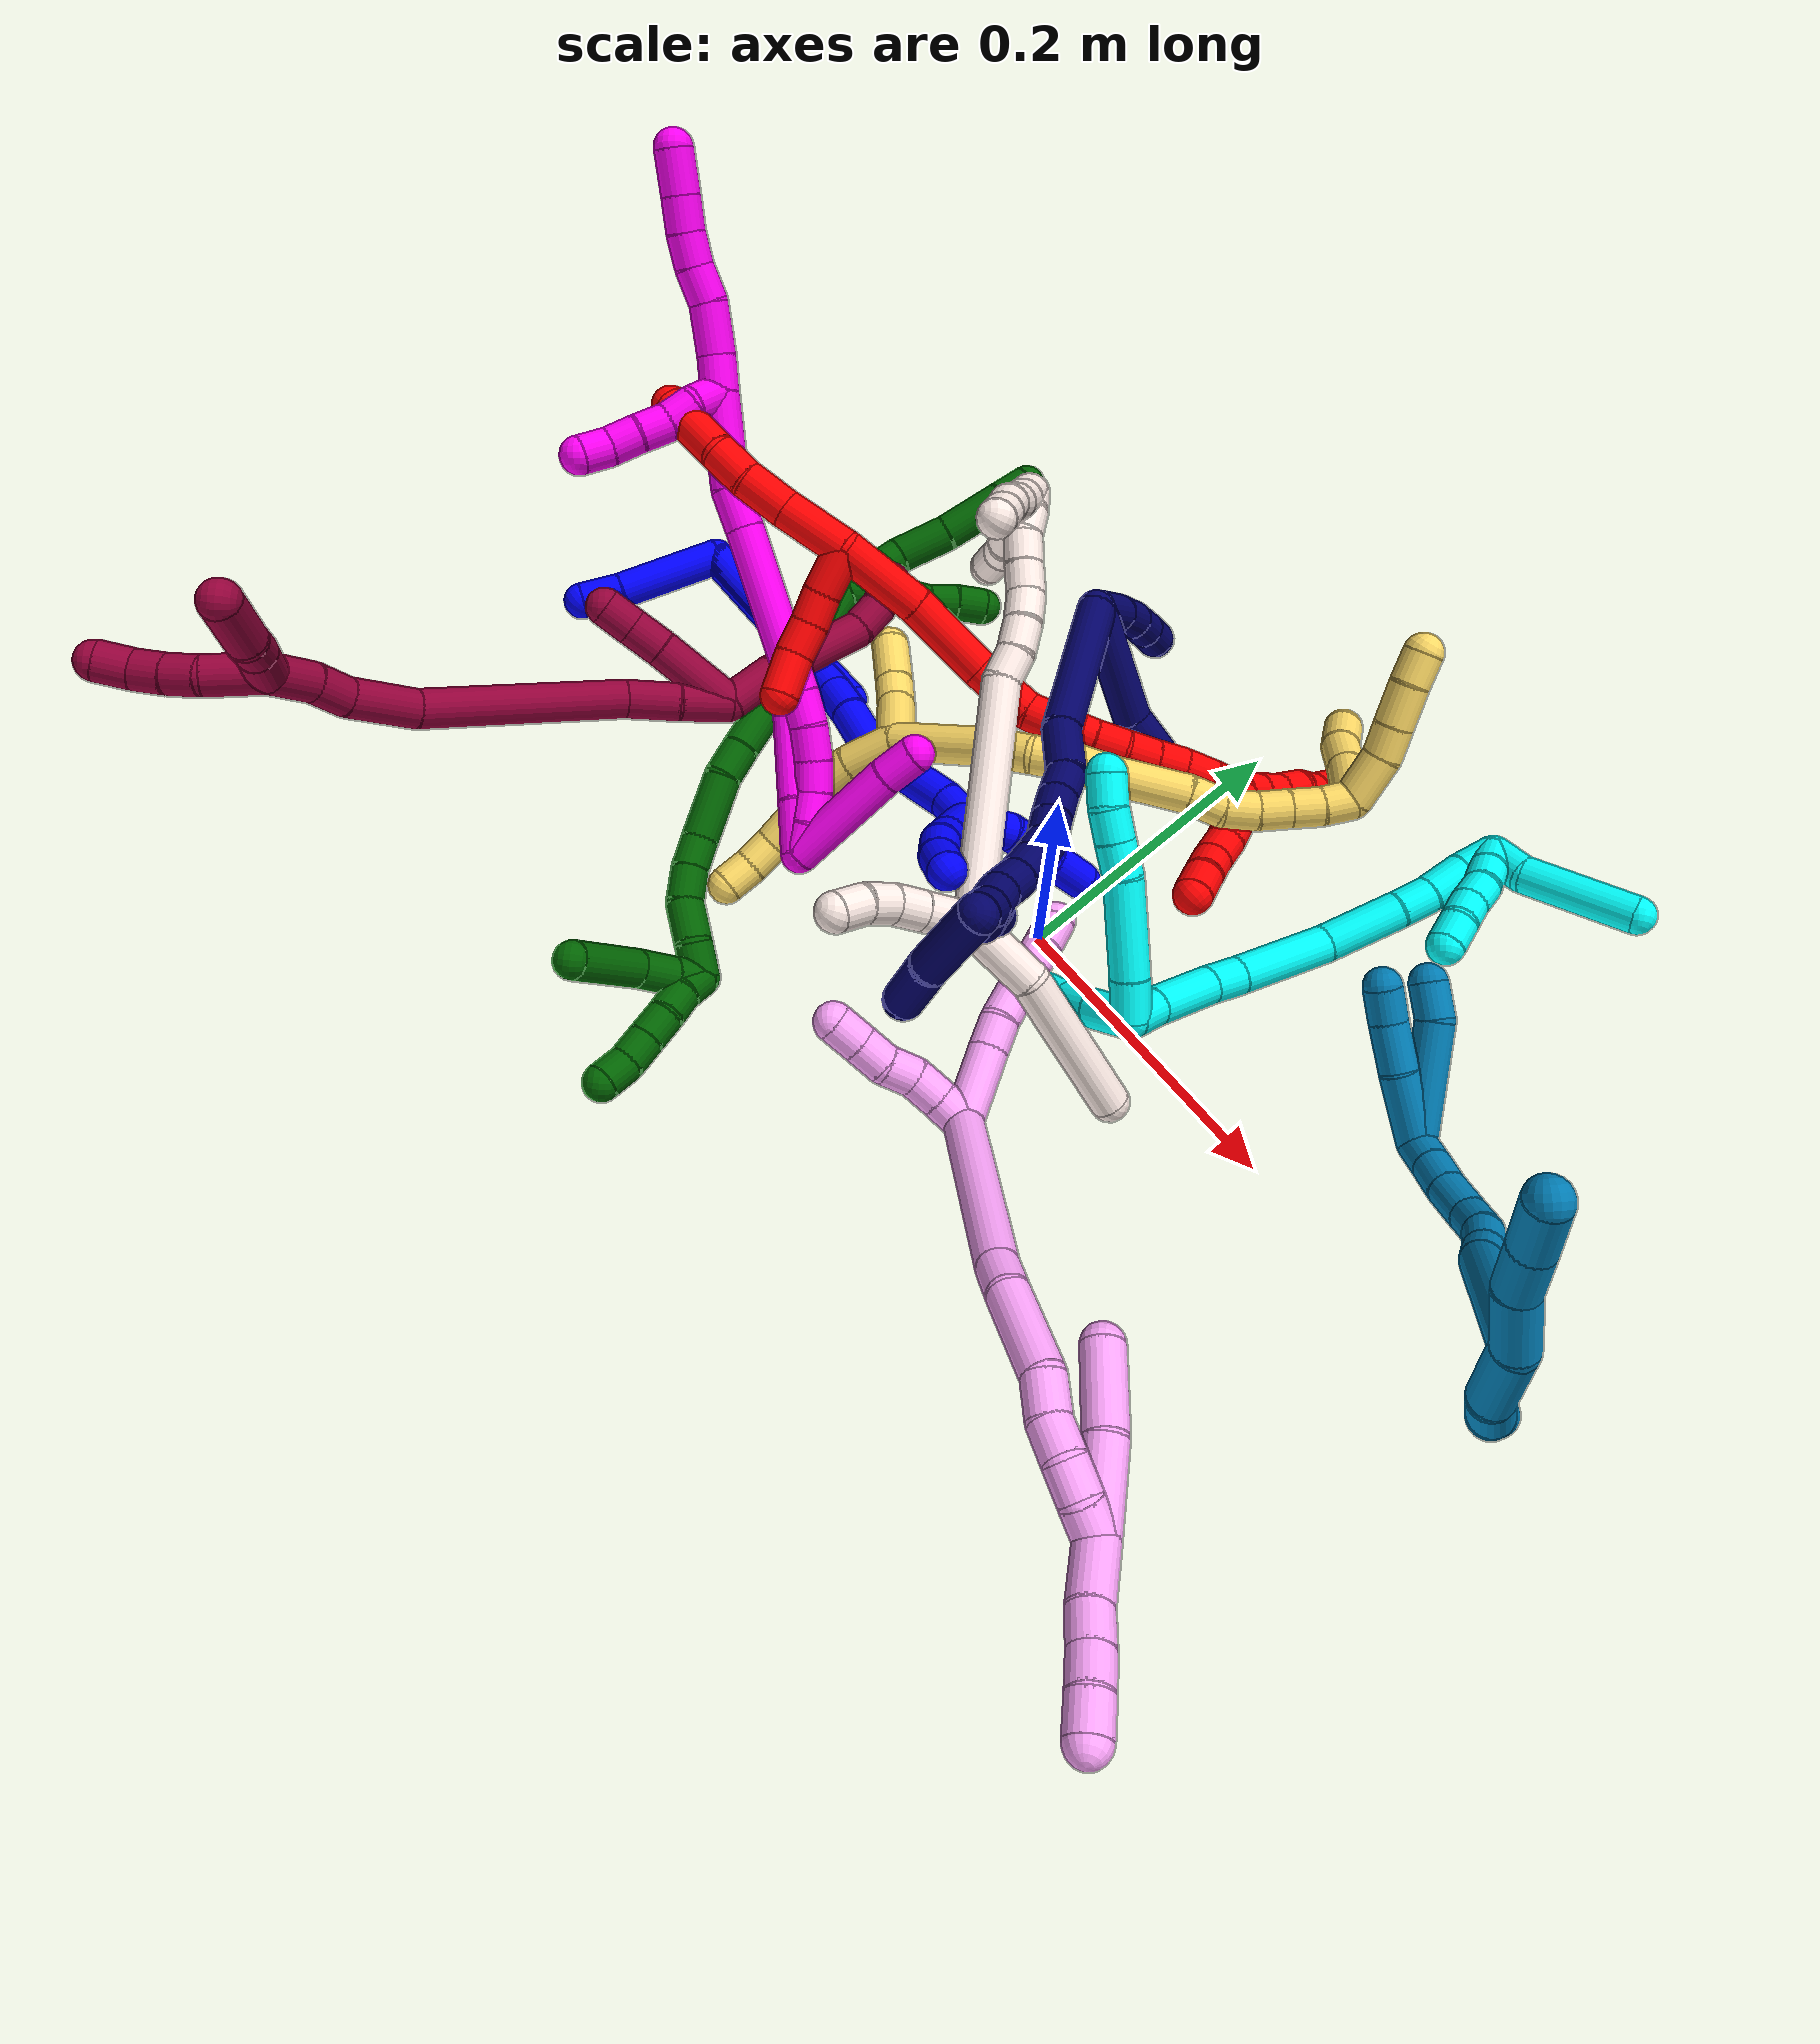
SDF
<sdf version="1.7">
 <world name="default">
  <plugin name="TubeGeneratorPlugin" filename="libtube_generator_plugin.so"/>
  <model name="photoneo_s_sensor">
   <static>1</static>
   <pose>0 0 2 1.57079 1.57079 3.14159</pose>
   <link name="link">
    <inertial><mass>0.1</mass></inertial>
    <sensor name="sensor" type="depth">
     <update_rate>30</update_rate>
     <camera>
      <horizontal_fov>1.22</horizontal_fov>
      <image><width>1920</width><height>1200</height><format>B8G8R8</format></image>
      <clip><near>0.1</near><far>4</far></clip>
      <depth_camera><output>points</output></depth_camera>
     </camera>
     <plugin name="camera_plugin" filename="libgazebo_ros_depth_camera.so">
      <baseline>0.2</baseline>
      <alwaysOn>1</alwaysOn>
      <updateRate>0.0</updateRate>
      <cameraName>camera_ir</cameraName>
      <imageTopicName>/camera/color/image_raw</imageTopicName>
      <cameraInfoTopicName>/camera/color/camera_info</cameraInfoTopicName>
      <depthImageTopicName>/camera/depth/image_raw</depthImageTopicName>
      <depthImageCameraInfoTopicName>/camera/depth/camera_info</depthImageCameraInfoTopicName>
      <pointCloudTopicName>/camera/depth/points</pointCloudTopicName>
      <frameName>fr_optical</frameName>
      <pointCloudCutoff>0.1</pointCloudCutoff>
      <pointCloudCutoffMax>2.0</pointCloudCutoffMax>
      <distortionK1>0</distortionK1>
      <distortionK2>0</distortionK2>
      <distortionK3>0</distortionK3>
      <distortionT1>0</distortionT1>
      <distortionT2>0</distortionT2>
      <CxPrime>0</CxPrime>
      <Cx>0</Cx>
      <Cy>0</Cy>
      <focalLength>0</focalLength>
      <hackBaseline>0</hackBaseline>
     </plugin>
    </sensor>
   </link>
  </model>
  <gravity>0 0 -9.8</gravity>
  <magnetic_field>6e-06 2.3e-05 -4.2e-05</magnetic_field>
  <atmosphere type="adiabatic"/>
  <physics name="default_physics" default="0" type="ode">
   <max_step_size>0.003</max_step_size>
   <real_time_factor>1</real_time_factor>
   <real_time_update_rate>1000</real_time_update_rate>
   <max_contacts>10000</max_contacts>
   <ode>
    <solver>
     <type>quick</type>
     <iters>100</iters>
     <sor>1.3</sor>
     <use_dynamic_moi_rescaling>0</use_dynamic_moi_rescaling>
    </solver>
    <constraints>
     <contact_max_correcting_vel>0</contact_max_correcting_vel>
     <contact_surface_layer>0.001</contact_surface_layer>
     <cfm>0</cfm>
     <erp>0.2</erp>
    </constraints>
   </ode>
  </physics>
  <scene><ambient>0.4 0.4 0.4 1</ambient><background>0.7 0.7 0.7 1</background><shadows>0</shadows></scene>
  <audio><device>default</device></audio>
  <spherical_coordinates>
   <surface_model>EARTH_WGS84</surface_model>
   <latitude_deg>0</latitude_deg>
   <longitude_deg>0</longitude_deg>
   <elevation>0</elevation>
   <heading_deg>0</heading_deg>
  </spherical_coordinates>
  <model name="bin">
   <static>1</static>
   <link name="bottom">
    <collision name="collision-bottom">
     <pose>0 0 -0.01 0 -0 0</pose>
     <geometry><box><size>0.8 0.6 0.02</size></box></geometry>
     <surface>
      <friction><ode><mu>100</mu><mu2>100</mu2></ode></friction>
      <contact><collide_bitmask>65535</collide_bitmask></contact>
     </surface>
    </collision>
   </link>
   <link name="west_wall">
    <collision name="collision-west_wall">
     <pose>-0.41 0 0.1 0 -0 0</pose>
     <geometry><box><size>0.02 0.6 0.2</size></box></geometry>
     <surface>
      <friction><ode><mu>100</mu><mu2>100</mu2></ode></friction>
      <contact><collide_bitmask>65535</collide_bitmask></contact>
     </surface>
    </collision>
   </link>
   <link name="east_wall">
    <collision name="collision-east_wall">
     <pose>0.41 0 0.1 0 -0 0</pose>
     <geometry><box><size>0.02 0.6 0.2</size></box></geometry>
     <surface>
      <friction><ode><mu>100</mu><mu2>100</mu2></ode></friction>
      <contact><collide_bitmask>65535</collide_bitmask></contact>
     </surface>
    </collision>
   </link>
   <link name="south_wall">
    <collision name="collision-south_wall">
     <pose>0 -0.31 0.1 0 -0 0</pose>
     <geometry><box><size>0.8 0.02 0.2</size></box></geometry>
     <surface>
      <friction><ode><mu>100</mu><mu2>100</mu2></ode></friction>
      <contact><collide_bitmask>65535</collide_bitmask></contact>
     </surface>
    </collision>
   </link>
   <link name="north_wall">
    <collision name="collision-north_wall">
     <pose>0 0.31 0.1 0 -0 0</pose>
     <geometry><box><size>0.8 0.02 0.2</size></box></geometry>
     <surface>
      <friction><ode><mu>100</mu><mu2>100</mu2></ode></friction>
      <contact><collide_bitmask>65535</collide_bitmask></contact>
     </surface>
    </collision>
   </link>
  </model>
  <model name="1">
   <static>0</static>
   <link name="1">
    <collision name="collision-cylinder-e_1_2_8">
     <pose>0.003902 0.002028 -0.055302 -3.10493 0.070403 -2.18167</pose>
     <geometry><cylinder><radius>0.0125</radius><length>0.110953</length></cylinder></geometry>
     <surface>
      <friction><ode><mu>1.16</mu><mu2>1.16</mu2><slip1>0</slip1><slip2>0</slip2></ode></friction>
      <contact><ode><kp>1e+06</kp><kd>1</kd><max_vel>0</max_vel><min_depth>0.001</min_depth></ode></contact>
     </surface>
    </collision>
    <visual name="visual-cylinder-e_1_2_8">
     <pose>0.003902 0.002028 -0.055302 -3.10493 0.070403 -2.18167</pose>
     <geometry><cylinder><radius>0.0125</radius><length>0.110953</length></cylinder></geometry>
     <material><ambient>0 0 1 1</ambient></material>
    </visual>
    <collision name="collision-cylinder-e_2_8_6">
     <pose>0.008786 0.005256 -0.130065 -3.08002 0.05027 -1.36926</pose>
     <geometry><cylinder><radius>0.0125</radius><length>0.039047</length></cylinder></geometry>
     <surface>
      <friction><ode><mu>1.16</mu><mu2>1.16</mu2><slip1>0</slip1><slip2>0</slip2></ode></friction>
      <contact><ode><kp>1e+06</kp><kd>1</kd><max_vel>0</max_vel><min_depth>0.001</min_depth></ode></contact>
     </surface>
    </collision>
    <visual name="visual-cylinder-e_2_8_6">
     <pose>0.008786 0.005256 -0.130065 -3.08002 0.05027 -1.36926</pose>
     <geometry><cylinder><radius>0.0125</radius><length>0.039047</length></cylinder></geometry>
     <material><ambient>0 0 1 1</ambient></material>
    </visual>
    <collision name="collision-cylinder-e_1_2_9">
     <pose>-0.014876 -0.032429 0.006212 1.38152 -0.423312 -0.351569</pose>
     <geometry><cylinder><radius>0.0125</radius><length>0.07243</length></cylinder></geometry>
     <surface>
      <friction><ode><mu>1.16</mu><mu2>1.16</mu2><slip1>0</slip1><slip2>0</slip2></ode></friction>
      <contact><ode><kp>1e+06</kp><kd>1</kd><max_vel>0</max_vel><min_depth>0.001</min_depth></ode></contact>
     </surface>
    </collision>
    <visual name="visual-cylinder-e_1_2_9">
     <pose>-0.014876 -0.032429 0.006212 1.38152 -0.423312 -0.351569</pose>
     <geometry><cylinder><radius>0.0125</radius><length>0.07243</length></cylinder></geometry>
     <material><ambient>0 0 1 1</ambient></material>
    </visual>
    <collision name="collision-cylinder-e_2_9_5">
     <pose>-0.035422 -0.076801 0.016326 1.25511 -0.423854 -0.309642</pose>
     <geometry><cylinder><radius>0.0125</radius><length>0.02757</length></cylinder></geometry>
     <surface>
      <friction><ode><mu>1.16</mu><mu2>1.16</mu2><slip1>0</slip1><slip2>0</slip2></ode></friction>
      <contact><ode><kp>1e+06</kp><kd>1</kd><max_vel>0</max_vel><min_depth>0.001</min_depth></ode></contact>
     </surface>
    </collision>
    <visual name="visual-cylinder-e_2_9_5">
     <pose>-0.035422 -0.076801 0.016326 1.25511 -0.423854 -0.309642</pose>
     <geometry><cylinder><radius>0.0125</radius><length>0.02757</length></cylinder></geometry>
     <material><ambient>0 0 1 1</ambient></material>
    </visual>
    <collision name="collision-cylinder-e_1_2_10">
     <pose>0.002466 0.001609 -0.04363 -3.10473 0.056415 -1.98418</pose>
     <geometry><cylinder><radius>0.0125</radius><length>0.087459</length></cylinder></geometry>
     <surface>
      <friction><ode><mu>1.16</mu><mu2>1.16</mu2><slip1>0</slip1><slip2>0</slip2></ode></friction>
      <contact><ode><kp>1e+06</kp><kd>1</kd><max_vel>0</max_vel><min_depth>0.001</min_depth></ode></contact>
     </surface>
    </collision>
    <visual name="visual-cylinder-e_1_2_10">
     <pose>0.002466 0.001609 -0.04363 -3.10473 0.056415 -1.98418</pose>
     <geometry><cylinder><radius>0.0125</radius><length>0.087459</length></cylinder></geometry>
     <material><ambient>0 0 1 1</ambient></material>
    </visual>
    <collision name="collision-cylinder-e_2_10_11">
     <pose>0.005581 0.002708 -0.099985 3.10153 0.050989 1.80982</pose>
     <geometry><cylinder><radius>0.0125</radius><length>0.025504</length></cylinder></geometry>
     <surface>
      <friction><ode><mu>1.16</mu><mu2>1.16</mu2><slip1>0</slip1><slip2>0</slip2></ode></friction>
      <contact><ode><kp>1e+06</kp><kd>1</kd><max_vel>0</max_vel><min_depth>0.001</min_depth></ode></contact>
     </surface>
    </collision>
    <visual name="visual-cylinder-e_2_10_11">
     <pose>0.005581 0.002708 -0.099985 3.10153 0.050989 1.80982</pose>
     <geometry><cylinder><radius>0.0125</radius><length>0.025504</length></cylinder></geometry>
     <material><ambient>0 0 1 1</ambient></material>
    </visual>
    <collision name="collision-cylinder-e_3_11_12">
     <pose>0.010662 -0.00149 -0.127997 2.90484 0.274602 1.72016</pose>
     <geometry><cylinder><radius>0.0125</radius><length>0.032676</length></cylinder></geometry>
     <surface>
      <friction><ode><mu>1.16</mu><mu2>1.16</mu2><slip1>0</slip1><slip2>0</slip2></ode></friction>
      <contact><ode><kp>1e+06</kp><kd>1</kd><max_vel>0</max_vel><min_depth>0.001</min_depth></ode></contact>
     </surface>
    </collision>
    <visual name="visual-cylinder-e_3_11_12">
     <pose>0.010662 -0.00149 -0.127997 2.90484 0.274602 1.72016</pose>
     <geometry><cylinder><radius>0.0125</radius><length>0.032676</length></cylinder></geometry>
     <material><ambient>0 0 1 1</ambient></material>
    </visual>
    <collision name="collision-cylinder-e_4_12_13">
     <pose>0.018359 -0.008645 -0.154751 2.84803 0.266236 1.47195</pose>
     <geometry><cylinder><radius>0.0125</radius><length>0.024832</length></cylinder></geometry>
     <surface>
      <friction><ode><mu>1.16</mu><mu2>1.16</mu2><slip1>0</slip1><slip2>0</slip2></ode></friction>
      <contact><ode><kp>1e+06</kp><kd>1</kd><max_vel>0</max_vel><min_depth>0.001</min_depth></ode></contact>
     </surface>
    </collision>
    <visual name="visual-cylinder-e_4_12_13">
     <pose>0.018359 -0.008645 -0.154751 2.84803 0.266236 1.47195</pose>
     <geometry><cylinder><radius>0.0125</radius><length>0.024832</length></cylinder></geometry>
     <material><ambient>0 0 1 1</ambient></material>
    </visual>
    <collision name="collision-cylinder-e_5_13_14">
     <pose>0.024488 -0.017089 -0.184579 2.87687 0.149342 1.02387</pose>
     <geometry><cylinder><radius>0.0125</radius><length>0.038477</length></cylinder></geometry>
     <surface>
      <friction><ode><mu>1.16</mu><mu2>1.16</mu2><slip1>0</slip1><slip2>0</slip2></ode></friction>
      <contact><ode><kp>1e+06</kp><kd>1</kd><max_vel>0</max_vel><min_depth>0.001</min_depth></ode></contact>
     </surface>
    </collision>
    <visual name="visual-cylinder-e_5_13_14">
     <pose>0.024488 -0.017089 -0.184579 2.87687 0.149342 1.02387</pose>
     <geometry><cylinder><radius>0.0125</radius><length>0.038477</length></cylinder></geometry>
     <material><ambient>0 0 1 1</ambient></material>
    </visual>
    <collision name="collision-cylinder-e_6_14_15">
     <pose>0.039848 -0.021698 -0.234966 -3.13008 0.37206 -3.08043</pose>
     <geometry><cylinder><radius>0.0125</radius><length>0.06876</length></cylinder></geometry>
     <surface>
      <friction><ode><mu>1.16</mu><mu2>1.16</mu2><slip1>0</slip1><slip2>0</slip2></ode></friction>
      <contact><ode><kp>1e+06</kp><kd>1</kd><max_vel>0</max_vel><min_depth>0.001</min_depth></ode></contact>
     </surface>
    </collision>
    <visual name="visual-cylinder-e_6_14_15">
     <pose>0.039848 -0.021698 -0.234966 -3.13008 0.37206 -3.08043</pose>
     <geometry><cylinder><radius>0.0125</radius><length>0.06876</length></cylinder></geometry>
     <material><ambient>0 0 1 1</ambient></material>
    </visual>
    <collision name="collision-cylinder-e_7_15_1">
     <pose>0.055795 -0.023815 -0.277295 2.90482 0.314545 1.85452</pose>
     <geometry><cylinder><radius>0.0125</radius><length>0.022293</length></cylinder></geometry>
     <surface>
      <friction><ode><mu>1.16</mu><mu2>1.16</mu2><slip1>0</slip1><slip2>0</slip2></ode></friction>
      <contact><ode><kp>1e+06</kp><kd>1</kd><max_vel>0</max_vel><min_depth>0.001</min_depth></ode></contact>
     </surface>
    </collision>
    <visual name="visual-cylinder-e_7_15_1">
     <pose>0.055795 -0.023815 -0.277295 2.90482 0.314545 1.85452</pose>
     <geometry><cylinder><radius>0.0125</radius><length>0.022293</length></cylinder></geometry>
     <material><ambient>0 0 1 1</ambient></material>
    </visual>
    <collision name="collision-cylinder-e_1_1_16">
     <pose>0.057691 -0.012264 -0.296198 -2.12039 -0.094044 0.16762</pose>
     <geometry><cylinder><radius>0.0125</radius><length>0.03307</length></cylinder></geometry>
     <surface>
      <friction><ode><mu>1.16</mu><mu2>1.16</mu2><slip1>0</slip1><slip2>0</slip2></ode></friction>
      <contact><ode><kp>1e+06</kp><kd>1</kd><max_vel>0</max_vel><min_depth>0.001</min_depth></ode></contact>
     </surface>
    </collision>
    <visual name="visual-cylinder-e_1_1_16">
     <pose>0.057691 -0.012264 -0.296198 -2.12039 -0.094044 0.16762</pose>
     <geometry><cylinder><radius>0.0125</radius><length>0.03307</length></cylinder></geometry>
     <material><ambient>0 0 1 1</ambient></material>
    </visual>
    <collision name="collision-cylinder-e_2_16_17">
     <pose>0.049603 0.015437 -0.316539 -2.28076 -0.347973 0.731219</pose>
     <geometry><cylinder><radius>0.0125</radius><length>0.038329</length></cylinder></geometry>
     <surface>
      <friction><ode><mu>1.16</mu><mu2>1.16</mu2><slip1>0</slip1><slip2>0</slip2></ode></friction>
      <contact><ode><kp>1e+06</kp><kd>1</kd><max_vel>0</max_vel><min_depth>0.001</min_depth></ode></contact>
     </surface>
    </collision>
    <visual name="visual-cylinder-e_2_16_17">
     <pose>0.049603 0.015437 -0.316539 -2.28076 -0.347973 0.731219</pose>
     <geometry><cylinder><radius>0.0125</radius><length>0.038329</length></cylinder></geometry>
     <material><ambient>0 0 1 1</ambient></material>
    </visual>
    <collision name="collision-cylinder-e_3_17_4">
     <pose>0.038155 0.039248 -0.337078 -2.28495 -0.350751 0.740386</pose>
     <geometry><cylinder><radius>0.0125</radius><length>0.028601</length></cylinder></geometry>
     <surface>
      <friction><ode><mu>1.16</mu><mu2>1.16</mu2><slip1>0</slip1><slip2>0</slip2></ode></friction>
      <contact><ode><kp>1e+06</kp><kd>1</kd><max_vel>0</max_vel><min_depth>0.001</min_depth></ode></contact>
     </surface>
    </collision>
    <visual name="visual-cylinder-e_3_17_4">
     <pose>0.038155 0.039248 -0.337078 -2.28495 -0.350751 0.740386</pose>
     <geometry><cylinder><radius>0.0125</radius><length>0.028601</length></cylinder></geometry>
     <material><ambient>0 0 1 1</ambient></material>
    </visual>
    <collision name="collision-cylinder-e_1_1_18">
     <pose>0.066127 -0.043361 -0.293521 1.90494 0.364171 0.506534</pose>
     <geometry><cylinder><radius>0.0125</radius><length>0.038652</length></cylinder></geometry>
     <surface>
      <friction><ode><mu>1.16</mu><mu2>1.16</mu2><slip1>0</slip1><slip2>0</slip2></ode></friction>
      <contact><ode><kp>1e+06</kp><kd>1</kd><max_vel>0</max_vel><min_depth>0.001</min_depth></ode></contact>
     </surface>
    </collision>
    <visual name="visual-cylinder-e_1_1_18">
     <pose>0.066127 -0.043361 -0.293521 1.90494 0.364171 0.506534</pose>
     <geometry><cylinder><radius>0.0125</radius><length>0.038652</length></cylinder></geometry>
     <material><ambient>0 0 1 1</ambient></material>
    </visual>
    <collision name="collision-cylinder-e_2_18_19">
     <pose>0.077753 -0.068915 -0.302755 1.94248 0.479656 0.687171</pose>
     <geometry><cylinder><radius>0.0125</radius><length>0.020552</length></cylinder></geometry>
     <surface>
      <friction><ode><mu>1.16</mu><mu2>1.16</mu2><slip1>0</slip1><slip2>0</slip2></ode></friction>
      <contact><ode><kp>1e+06</kp><kd>1</kd><max_vel>0</max_vel><min_depth>0.001</min_depth></ode></contact>
     </surface>
    </collision>
    <visual name="visual-cylinder-e_2_18_19">
     <pose>0.077753 -0.068915 -0.302755 1.94248 0.479656 0.687171</pose>
     <geometry><cylinder><radius>0.0125</radius><length>0.020552</length></cylinder></geometry>
     <material><ambient>0 0 1 1</ambient></material>
    </visual>
    <collision name="collision-cylinder-e_3_19_20">
     <pose>0.086085 -0.084855 -0.311819 2.22865 0.364469 0.718006</pose>
     <geometry><cylinder><radius>0.0125</radius><length>0.020143</length></cylinder></geometry>
     <surface>
      <friction><ode><mu>1.16</mu><mu2>1.16</mu2><slip1>0</slip1><slip2>0</slip2></ode></friction>
      <contact><ode><kp>1e+06</kp><kd>1</kd><max_vel>0</max_vel><min_depth>0.001</min_depth></ode></contact>
     </surface>
    </collision>
    <visual name="visual-cylinder-e_3_19_20">
     <pose>0.086085 -0.084855 -0.311819 2.22865 0.364469 0.718006</pose>
     <geometry><cylinder><radius>0.0125</radius><length>0.020143</length></cylinder></geometry>
     <material><ambient>0 0 1 1</ambient></material>
    </visual>
    <collision name="collision-cylinder-e_4_20_3">
     <pose>0.094557 -0.097808 -0.324817 2.49167 0.492423 1.28179</pose>
     <geometry><cylinder><radius>0.0125</radius><length>0.020653</length></cylinder></geometry>
     <surface>
      <friction><ode><mu>1.16</mu><mu2>1.16</mu2><slip1>0</slip1><slip2>0</slip2></ode></friction>
      <contact><ode><kp>1e+06</kp><kd>1</kd><max_vel>0</max_vel><min_depth>0.001</min_depth></ode></contact>
     </surface>
    </collision>
    <visual name="visual-cylinder-e_4_20_3">
     <pose>0.094557 -0.097808 -0.324817 2.49167 0.492423 1.28179</pose>
     <geometry><cylinder><radius>0.0125</radius><length>0.020653</length></cylinder></geometry>
     <material><ambient>0 0 1 1</ambient></material>
    </visual>
    <collision name="collision-sphere-3">
     <pose>0.099439 -0.103314 -0.332061 0 -0 0</pose>
     <geometry><sphere><radius>0.0125</radius></sphere></geometry>
     <surface>
      <friction><ode><mu>1.16</mu><mu2>1.16</mu2><slip1>0</slip1><slip2>0</slip2></ode></friction>
      <contact><ode><kp>1e+06</kp><kd>1</kd><max_vel>0</max_vel><min_depth>0.001</min_depth></ode></contact>
     </surface>
    </collision>
    <visual name="visual-sphere-3">
     <pose>0.099439 -0.103314 -0.332061 0 -0 0</pose>
     <geometry><sphere><radius>0.0125</radius></sphere></geometry>
     <material><ambient>0 0 1 1</ambient></material>
    </visual>
    <collision name="collision-sphere-20">
     <pose>0.089675 -0.092301 -0.317572 0 -0 0</pose>
     <geometry><sphere><radius>0.0125</radius></sphere></geometry>
     <surface>
      <friction><ode><mu>1.16</mu><mu2>1.16</mu2><slip1>0</slip1><slip2>0</slip2></ode></friction>
      <contact><ode><kp>1e+06</kp><kd>1</kd><max_vel>0</max_vel><min_depth>0.001</min_depth></ode></contact>
     </surface>
    </collision>
    <visual name="visual-sphere-20">
     <pose>0.089675 -0.092301 -0.317572 0 -0 0</pose>
     <geometry><sphere><radius>0.0125</radius></sphere></geometry>
     <material><ambient>0 0 1 1</ambient></material>
    </visual>
    <collision name="collision-sphere-19">
     <pose>0.082495 -0.077409 -0.306066 0 -0 0</pose>
     <geometry><sphere><radius>0.0125</radius></sphere></geometry>
     <surface>
      <friction><ode><mu>1.16</mu><mu2>1.16</mu2><slip1>0</slip1><slip2>0</slip2></ode></friction>
      <contact><ode><kp>1e+06</kp><kd>1</kd><max_vel>0</max_vel><min_depth>0.001</min_depth></ode></contact>
     </surface>
    </collision>
    <visual name="visual-sphere-19">
     <pose>0.082495 -0.077409 -0.306066 0 -0 0</pose>
     <geometry><sphere><radius>0.0125</radius></sphere></geometry>
     <material><ambient>0 0 1 1</ambient></material>
    </visual>
    <collision name="collision-sphere-10">
     <pose>0.004931 0.003218 -0.08726 0 -0 0</pose>
     <geometry><sphere><radius>0.0125</radius></sphere></geometry>
     <surface>
      <friction><ode><mu>1.16</mu><mu2>1.16</mu2><slip1>0</slip1><slip2>0</slip2></ode></friction>
      <contact><ode><kp>1e+06</kp><kd>1</kd><max_vel>0</max_vel><min_depth>0.001</min_depth></ode></contact>
     </surface>
    </collision>
    <visual name="visual-sphere-10">
     <pose>0.004931 0.003218 -0.08726 0 -0 0</pose>
     <geometry><sphere><radius>0.0125</radius></sphere></geometry>
     <material><ambient>0 0 1 1</ambient></material>
    </visual>
    <collision name="collision-sphere-5">
     <pose>-0.041092 -0.088746 0.020227 0 -0 0</pose>
     <geometry><sphere><radius>0.0125</radius></sphere></geometry>
     <surface>
      <friction><ode><mu>1.16</mu><mu2>1.16</mu2><slip1>0</slip1><slip2>0</slip2></ode></friction>
      <contact><ode><kp>1e+06</kp><kd>1</kd><max_vel>0</max_vel><min_depth>0.001</min_depth></ode></contact>
     </surface>
    </collision>
    <visual name="visual-sphere-5">
     <pose>-0.041092 -0.088746 0.020227 0 -0 0</pose>
     <geometry><sphere><radius>0.0125</radius></sphere></geometry>
     <material><ambient>0 0 1 1</ambient></material>
    </visual>
    <collision name="collision-sphere-6">
     <pose>0.009767 0.006456 -0.149528 0 -0 0</pose>
     <geometry><sphere><radius>0.0125</radius></sphere></geometry>
     <surface>
      <friction><ode><mu>1.16</mu><mu2>1.16</mu2><slip1>0</slip1><slip2>0</slip2></ode></friction>
      <contact><ode><kp>1e+06</kp><kd>1</kd><max_vel>0</max_vel><min_depth>0.001</min_depth></ode></contact>
     </surface>
    </collision>
    <visual name="visual-sphere-6">
     <pose>0.009767 0.006456 -0.149528 0 -0 0</pose>
     <geometry><sphere><radius>0.0125</radius></sphere></geometry>
     <material><ambient>0 0 1 1</ambient></material>
    </visual>
    <collision name="collision-sphere-9">
     <pose>-0.029753 -0.064857 0.012425 0 -0 0</pose>
     <geometry><sphere><radius>0.0125</radius></sphere></geometry>
     <surface>
      <friction><ode><mu>1.16</mu><mu2>1.16</mu2><slip1>0</slip1><slip2>0</slip2></ode></friction>
      <contact><ode><kp>1e+06</kp><kd>1</kd><max_vel>0</max_vel><min_depth>0.001</min_depth></ode></contact>
     </surface>
    </collision>
    <visual name="visual-sphere-9">
     <pose>-0.029753 -0.064857 0.012425 0 -0 0</pose>
     <geometry><sphere><radius>0.0125</radius></sphere></geometry>
     <material><ambient>0 0 1 1</ambient></material>
    </visual>
    <collision name="collision-sphere-2">
     <geometry><sphere><radius>0.0125</radius></sphere></geometry>
     <surface>
      <friction><ode><mu>1.16</mu><mu2>1.16</mu2><slip1>0</slip1><slip2>0</slip2></ode></friction>
      <contact><ode><kp>1e+06</kp><kd>1</kd><max_vel>0</max_vel><min_depth>0.001</min_depth></ode></contact>
     </surface>
    </collision>
    <visual name="visual-sphere-2">
     <geometry><sphere><radius>0.0125</radius></sphere></geometry>
     <material><ambient>0 0 1 1</ambient></material>
    </visual>
    <collision name="collision-sphere-8">
     <pose>0.007805 0.004057 -0.110603 0 -0 0</pose>
     <geometry><sphere><radius>0.0125</radius></sphere></geometry>
     <surface>
      <friction><ode><mu>1.16</mu><mu2>1.16</mu2><slip1>0</slip1><slip2>0</slip2></ode></friction>
      <contact><ode><kp>1e+06</kp><kd>1</kd><max_vel>0</max_vel><min_depth>0.001</min_depth></ode></contact>
     </surface>
    </collision>
    <visual name="visual-sphere-8">
     <pose>0.007805 0.004057 -0.110603 0 -0 0</pose>
     <geometry><sphere><radius>0.0125</radius></sphere></geometry>
     <material><ambient>0 0 1 1</ambient></material>
    </visual>
    <collision name="collision-sphere-11">
     <pose>0.006231 0.002198 -0.11271 0 -0 0</pose>
     <geometry><sphere><radius>0.0125</radius></sphere></geometry>
     <surface>
      <friction><ode><mu>1.16</mu><mu2>1.16</mu2><slip1>0</slip1><slip2>0</slip2></ode></friction>
      <contact><ode><kp>1e+06</kp><kd>1</kd><max_vel>0</max_vel><min_depth>0.001</min_depth></ode></contact>
     </surface>
    </collision>
    <visual name="visual-sphere-11">
     <pose>0.006231 0.002198 -0.11271 0 -0 0</pose>
     <geometry><sphere><radius>0.0125</radius></sphere></geometry>
     <material><ambient>0 0 1 1</ambient></material>
    </visual>
    <collision name="collision-sphere-12">
     <pose>0.015092 -0.005179 -0.143285 0 -0 0</pose>
     <geometry><sphere><radius>0.0125</radius></sphere></geometry>
     <surface>
      <friction><ode><mu>1.16</mu><mu2>1.16</mu2><slip1>0</slip1><slip2>0</slip2></ode></friction>
      <contact><ode><kp>1e+06</kp><kd>1</kd><max_vel>0</max_vel><min_depth>0.001</min_depth></ode></contact>
     </surface>
    </collision>
    <visual name="visual-sphere-12">
     <pose>0.015092 -0.005179 -0.143285 0 -0 0</pose>
     <geometry><sphere><radius>0.0125</radius></sphere></geometry>
     <material><ambient>0 0 1 1</ambient></material>
    </visual>
    <collision name="collision-sphere-13">
     <pose>0.021625 -0.012111 -0.166217 0 -0 0</pose>
     <geometry><sphere><radius>0.0125</radius></sphere></geometry>
     <surface>
      <friction><ode><mu>1.16</mu><mu2>1.16</mu2><slip1>0</slip1><slip2>0</slip2></ode></friction>
      <contact><ode><kp>1e+06</kp><kd>1</kd><max_vel>0</max_vel><min_depth>0.001</min_depth></ode></contact>
     </surface>
    </collision>
    <visual name="visual-sphere-13">
     <pose>0.021625 -0.012111 -0.166217 0 -0 0</pose>
     <geometry><sphere><radius>0.0125</radius></sphere></geometry>
     <material><ambient>0 0 1 1</ambient></material>
    </visual>
    <collision name="collision-sphere-14">
     <pose>0.02735 -0.022066 -0.20294 0 -0 0</pose>
     <geometry><sphere><radius>0.0125</radius></sphere></geometry>
     <surface>
      <friction><ode><mu>1.16</mu><mu2>1.16</mu2><slip1>0</slip1><slip2>0</slip2></ode></friction>
      <contact><ode><kp>1e+06</kp><kd>1</kd><max_vel>0</max_vel><min_depth>0.001</min_depth></ode></contact>
     </surface>
    </collision>
    <visual name="visual-sphere-14">
     <pose>0.02735 -0.022066 -0.20294 0 -0 0</pose>
     <geometry><sphere><radius>0.0125</radius></sphere></geometry>
     <material><ambient>0 0 1 1</ambient></material>
    </visual>
    <collision name="collision-sphere-15">
     <pose>0.052347 -0.021329 -0.266991 0 -0 0</pose>
     <geometry><sphere><radius>0.0125</radius></sphere></geometry>
     <surface>
      <friction><ode><mu>1.16</mu><mu2>1.16</mu2><slip1>0</slip1><slip2>0</slip2></ode></friction>
      <contact><ode><kp>1e+06</kp><kd>1</kd><max_vel>0</max_vel><min_depth>0.001</min_depth></ode></contact>
     </surface>
    </collision>
    <visual name="visual-sphere-15">
     <pose>0.052347 -0.021329 -0.266991 0 -0 0</pose>
     <geometry><sphere><radius>0.0125</radius></sphere></geometry>
     <material><ambient>0 0 1 1</ambient></material>
    </visual>
    <collision name="collision-sphere-1">
     <pose>0.059244 -0.026302 -0.287599 0 -0 0</pose>
     <geometry><sphere><radius>0.0125</radius></sphere></geometry>
     <surface>
      <friction><ode><mu>1.16</mu><mu2>1.16</mu2><slip1>0</slip1><slip2>0</slip2></ode></friction>
      <contact><ode><kp>1e+06</kp><kd>1</kd><max_vel>0</max_vel><min_depth>0.001</min_depth></ode></contact>
     </surface>
    </collision>
    <visual name="visual-sphere-1">
     <pose>0.059244 -0.026302 -0.287599 0 -0 0</pose>
     <geometry><sphere><radius>0.0125</radius></sphere></geometry>
     <material><ambient>0 0 1 1</ambient></material>
    </visual>
    <collision name="collision-sphere-18">
     <pose>0.073011 -0.060421 -0.299444 0 -0 0</pose>
     <geometry><sphere><radius>0.0125</radius></sphere></geometry>
     <surface>
      <friction><ode><mu>1.16</mu><mu2>1.16</mu2><slip1>0</slip1><slip2>0</slip2></ode></friction>
      <contact><ode><kp>1e+06</kp><kd>1</kd><max_vel>0</max_vel><min_depth>0.001</min_depth></ode></contact>
     </surface>
    </collision>
    <visual name="visual-sphere-18">
     <pose>0.073011 -0.060421 -0.299444 0 -0 0</pose>
     <geometry><sphere><radius>0.0125</radius></sphere></geometry>
     <material><ambient>0 0 1 1</ambient></material>
    </visual>
    <collision name="collision-sphere-16">
     <pose>0.056138 0.001774 -0.304796 0 -0 0</pose>
     <geometry><sphere><radius>0.0125</radius></sphere></geometry>
     <surface>
      <friction><ode><mu>1.16</mu><mu2>1.16</mu2><slip1>0</slip1><slip2>0</slip2></ode></friction>
      <contact><ode><kp>1e+06</kp><kd>1</kd><max_vel>0</max_vel><min_depth>0.001</min_depth></ode></contact>
     </surface>
    </collision>
    <visual name="visual-sphere-16">
     <pose>0.056138 0.001774 -0.304796 0 -0 0</pose>
     <geometry><sphere><radius>0.0125</radius></sphere></geometry>
     <material><ambient>0 0 1 1</ambient></material>
    </visual>
    <collision name="collision-sphere-17">
     <pose>0.043068 0.0291 -0.328282 0 -0 0</pose>
     <geometry><sphere><radius>0.0125</radius></sphere></geometry>
     <surface>
      <friction><ode><mu>1.16</mu><mu2>1.16</mu2><slip1>0</slip1><slip2>0</slip2></ode></friction>
      <contact><ode><kp>1e+06</kp><kd>1</kd><max_vel>0</max_vel><min_depth>0.001</min_depth></ode></contact>
     </surface>
    </collision>
    <visual name="visual-sphere-17">
     <pose>0.043068 0.0291 -0.328282 0 -0 0</pose>
     <geometry><sphere><radius>0.0125</radius></sphere></geometry>
     <material><ambient>0 0 1 1</ambient></material>
    </visual>
    <collision name="collision-sphere-4">
     <pose>0.033241 0.049396 -0.345874 0 -0 0</pose>
     <geometry><sphere><radius>0.0125</radius></sphere></geometry>
     <surface>
      <friction><ode><mu>1.16</mu><mu2>1.16</mu2><slip1>0</slip1><slip2>0</slip2></ode></friction>
      <contact><ode><kp>1e+06</kp><kd>1</kd><max_vel>0</max_vel><min_depth>0.001</min_depth></ode></contact>
     </surface>
    </collision>
    <visual name="visual-sphere-4">
     <pose>0.033241 0.049396 -0.345874 0 -0 0</pose>
     <geometry><sphere><radius>0.0125</radius></sphere></geometry>
     <material><ambient>0 0 1 1</ambient></material>
    </visual>
    <inertial>
     <pose>0.023402 -0.016377 -0.155028 0 -0 0</pose>
     <mass>0.75</mass>
     <inertia>
      <ixx>-0.000205</ixx>
      <ixy>0</ixy>
      <ixz>0</ixz>
      <iyy>-2.6e-05</iyy>
      <iyz>0</iyz>
      <izz>-2.4e-05</izz>
     </inertia>
    </inertial>
   </link>
   <pose>-0.35852 0.016135 0.012507 -1.52723 -1.08054 1.4469</pose>
  </model>
  <model name="2">
   <static>0</static>
   <link name="2">
    <collision name="collision-cylinder-e_1_2_8">
     <pose>-0.00375 -0.004646 0.021303 0.21472 -0.170312 -0.018399</pose>
     <geometry><cylinder><radius>0.0125</radius><length>0.044247</length></cylinder></geometry>
     <surface>
      <friction><ode><mu>1.16</mu><mu2>1.16</mu2><slip1>0</slip1><slip2>0</slip2></ode></friction>
      <contact><ode><kp>1e+06</kp><kd>1</kd><max_vel>0</max_vel><min_depth>0.001</min_depth></ode></contact>
     </surface>
    </collision>
    <visual name="visual-cylinder-e_1_2_8">
     <pose>-0.00375 -0.004646 0.021303 0.21472 -0.170312 -0.018399</pose>
     <geometry><cylinder><radius>0.0125</radius><length>0.044247</length></cylinder></geometry>
     <material><ambient>1 0 0 1</ambient></material>
    </visual>
    <collision name="collision-cylinder-e_2_8_9">
     <pose>-0.008961 -0.013382 0.057338 0.27083 -0.095289 -0.012993</pose>
     <geometry><cylinder><radius>0.0125</radius><length>0.030718</length></cylinder></geometry>
     <surface>
      <friction><ode><mu>1.16</mu><mu2>1.16</mu2><slip1>0</slip1><slip2>0</slip2></ode></friction>
      <contact><ode><kp>1e+06</kp><kd>1</kd><max_vel>0</max_vel><min_depth>0.001</min_depth></ode></contact>
     </surface>
    </collision>
    <visual name="visual-cylinder-e_2_8_9">
     <pose>-0.008961 -0.013382 0.057338 0.27083 -0.095289 -0.012993</pose>
     <geometry><cylinder><radius>0.0125</radius><length>0.030718</length></cylinder></geometry>
     <material><ambient>1 0 0 1</ambient></material>
    </visual>
    <collision name="collision-cylinder-e_3_9_10">
     <pose>-0.010733 -0.018787 0.084493 0.10544 -0.024846 -0.001311</pose>
     <geometry><cylinder><radius>0.0125</radius><length>0.024992</length></cylinder></geometry>
     <surface>
      <friction><ode><mu>1.16</mu><mu2>1.16</mu2><slip1>0</slip1><slip2>0</slip2></ode></friction>
      <contact><ode><kp>1e+06</kp><kd>1</kd><max_vel>0</max_vel><min_depth>0.001</min_depth></ode></contact>
     </surface>
    </collision>
    <visual name="visual-cylinder-e_3_9_10">
     <pose>-0.010733 -0.018787 0.084493 0.10544 -0.024846 -0.001311</pose>
     <geometry><cylinder><radius>0.0125</radius><length>0.024992</length></cylinder></geometry>
     <material><ambient>1 0 0 1</ambient></material>
    </visual>
    <collision name="collision-cylinder-e_4_10_6">
     <pose>-0.013548 -0.015055 0.121294 -0.204124 -0.100263 0.010277</pose>
     <geometry><cylinder><radius>0.0125</radius><length>0.050042</length></cylinder></geometry>
     <surface>
      <friction><ode><mu>1.16</mu><mu2>1.16</mu2><slip1>0</slip1><slip2>0</slip2></ode></friction>
      <contact><ode><kp>1e+06</kp><kd>1</kd><max_vel>0</max_vel><min_depth>0.001</min_depth></ode></contact>
     </surface>
    </collision>
    <visual name="visual-cylinder-e_4_10_6">
     <pose>-0.013548 -0.015055 0.121294 -0.204124 -0.100263 0.010277</pose>
     <geometry><cylinder><radius>0.0125</radius><length>0.050042</length></cylinder></geometry>
     <material><ambient>1 0 0 1</ambient></material>
    </visual>
    <collision name="collision-cylinder-e_1_2_11">
     <pose>-0.014582 -0.00109 -0.00421 2.88836 -1.28097 -2.80325</pose>
     <geometry><cylinder><radius>0.0125</radius><length>0.030434</length></cylinder></geometry>
     <surface>
      <friction><ode><mu>1.16</mu><mu2>1.16</mu2><slip1>0</slip1><slip2>0</slip2></ode></friction>
      <contact><ode><kp>1e+06</kp><kd>1</kd><max_vel>0</max_vel><min_depth>0.001</min_depth></ode></contact>
     </surface>
    </collision>
    <visual name="visual-cylinder-e_1_2_11">
     <pose>-0.014582 -0.00109 -0.00421 2.88836 -1.28097 -2.80325</pose>
     <geometry><cylinder><radius>0.0125</radius><length>0.030434</length></cylinder></geometry>
     <material><ambient>1 0 0 1</ambient></material>
    </visual>
    <collision name="collision-cylinder-e_2_11_12">
     <pose>-0.038533 -0.003587 -0.012472 2.80712 -1.14142 -2.62732</pose>
     <geometry><cylinder><radius>0.0125</radius><length>0.020607</length></cylinder></geometry>
     <surface>
      <friction><ode><mu>1.16</mu><mu2>1.16</mu2><slip1>0</slip1><slip2>0</slip2></ode></friction>
      <contact><ode><kp>1e+06</kp><kd>1</kd><max_vel>0</max_vel><min_depth>0.001</min_depth></ode></contact>
     </surface>
    </collision>
    <visual name="visual-cylinder-e_2_11_12">
     <pose>-0.038533 -0.003587 -0.012472 2.80712 -1.14142 -2.62732</pose>
     <geometry><cylinder><radius>0.0125</radius><length>0.020607</length></cylinder></geometry>
     <material><ambient>1 0 0 1</ambient></material>
    </visual>
    <collision name="collision-cylinder-e_3_12_13">
     <pose>-0.057637 -0.008055 -0.020474 2.48261 -1.09656 -2.12076</pose>
     <geometry><cylinder><radius>0.0125</radius><length>0.021887</length></cylinder></geometry>
     <surface>
      <friction><ode><mu>1.16</mu><mu2>1.16</mu2><slip1>0</slip1><slip2>0</slip2></ode></friction>
      <contact><ode><kp>1e+06</kp><kd>1</kd><max_vel>0</max_vel><min_depth>0.001</min_depth></ode></contact>
     </surface>
    </collision>
    <visual name="visual-cylinder-e_3_12_13">
     <pose>-0.057637 -0.008055 -0.020474 2.48261 -1.09656 -2.12076</pose>
     <geometry><cylinder><radius>0.0125</radius><length>0.021887</length></cylinder></geometry>
     <material><ambient>1 0 0 1</ambient></material>
    </visual>
    <collision name="collision-cylinder-e_4_13_5">
     <pose>-0.077903 -0.016257 -0.0312 2.49234 -0.891392 -1.91425</pose>
     <geometry><cylinder><radius>0.0125</radius><length>0.027072</length></cylinder></geometry>
     <surface>
      <friction><ode><mu>1.16</mu><mu2>1.16</mu2><slip1>0</slip1><slip2>0</slip2></ode></friction>
      <contact><ode><kp>1e+06</kp><kd>1</kd><max_vel>0</max_vel><min_depth>0.001</min_depth></ode></contact>
     </surface>
    </collision>
    <visual name="visual-cylinder-e_4_13_5">
     <pose>-0.077903 -0.016257 -0.0312 2.49234 -0.891392 -1.91425</pose>
     <geometry><cylinder><radius>0.0125</radius><length>0.027072</length></cylinder></geometry>
     <material><ambient>1 0 0 1</ambient></material>
    </visual>
    <collision name="collision-cylinder-e_1_2_14">
     <pose>0.000173 0.013609 -0.024606 -2.63639 0.006146 -0.023808</pose>
     <geometry><cylinder><radius>0.0125</radius><length>0.056238</length></cylinder></geometry>
     <surface>
      <friction><ode><mu>1.16</mu><mu2>1.16</mu2><slip1>0</slip1><slip2>0</slip2></ode></friction>
      <contact><ode><kp>1e+06</kp><kd>1</kd><max_vel>0</max_vel><min_depth>0.001</min_depth></ode></contact>
     </surface>
    </collision>
    <visual name="visual-cylinder-e_1_2_14">
     <pose>0.000173 0.013609 -0.024606 -2.63639 0.006146 -0.023808</pose>
     <geometry><cylinder><radius>0.0125</radius><length>0.056238</length></cylinder></geometry>
     <material><ambient>1 0 0 1</ambient></material>
    </visual>
    <collision name="collision-cylinder-e_2_14_15">
     <pose>-0.002301 0.038827 -0.075325 -2.72326 -0.092336 0.42862</pose>
     <geometry><cylinder><radius>0.0125</radius><length>0.0574</length></cylinder></geometry>
     <surface>
      <friction><ode><mu>1.16</mu><mu2>1.16</mu2><slip1>0</slip1><slip2>0</slip2></ode></friction>
      <contact><ode><kp>1e+06</kp><kd>1</kd><max_vel>0</max_vel><min_depth>0.001</min_depth></ode></contact>
     </surface>
    </collision>
    <visual name="visual-cylinder-e_2_14_15">
     <pose>-0.002301 0.038827 -0.075325 -2.72326 -0.092336 0.42862</pose>
     <geometry><cylinder><radius>0.0125</radius><length>0.0574</length></cylinder></geometry>
     <material><ambient>1 0 0 1</ambient></material>
    </visual>
    <collision name="collision-cylinder-e_3_15_16">
     <pose>-0.003616 0.053123 -0.121446 -3.00809 0.06585 -0.915602</pose>
     <geometry><cylinder><radius>0.0125</radius><length>0.040462</length></cylinder></geometry>
     <surface>
      <friction><ode><mu>1.16</mu><mu2>1.16</mu2><slip1>0</slip1><slip2>0</slip2></ode></friction>
      <contact><ode><kp>1e+06</kp><kd>1</kd><max_vel>0</max_vel><min_depth>0.001</min_depth></ode></contact>
     </surface>
    </collision>
    <visual name="visual-cylinder-e_3_15_16">
     <pose>-0.003616 0.053123 -0.121446 -3.00809 0.06585 -0.915602</pose>
     <geometry><cylinder><radius>0.0125</radius><length>0.040462</length></cylinder></geometry>
     <material><ambient>1 0 0 1</ambient></material>
    </visual>
    <collision name="collision-cylinder-e_4_16_17">
     <pose>0.001249 0.058064 -0.150541 -2.89853 0.360872 -1.96165</pose>
     <geometry><cylinder><radius>0.0125</radius><length>0.020014</length></cylinder></geometry>
     <surface>
      <friction><ode><mu>1.16</mu><mu2>1.16</mu2><slip1>0</slip1><slip2>0</slip2></ode></friction>
      <contact><ode><kp>1e+06</kp><kd>1</kd><max_vel>0</max_vel><min_depth>0.001</min_depth></ode></contact>
     </surface>
    </collision>
    <visual name="visual-cylinder-e_4_16_17">
     <pose>0.001249 0.058064 -0.150541 -2.89853 0.360872 -1.96165</pose>
     <geometry><cylinder><radius>0.0125</radius><length>0.020014</length></cylinder></geometry>
     <material><ambient>1 0 0 1</ambient></material>
    </visual>
    <collision name="collision-cylinder-e_5_17_18">
     <pose>0.008995 0.064351 -0.170577 -2.78859 0.346495 -1.55181</pose>
     <geometry><cylinder><radius>0.0125</radius><length>0.024812</length></cylinder></geometry>
     <surface>
      <friction><ode><mu>1.16</mu><mu2>1.16</mu2><slip1>0</slip1><slip2>0</slip2></ode></friction>
      <contact><ode><kp>1e+06</kp><kd>1</kd><max_vel>0</max_vel><min_depth>0.001</min_depth></ode></contact>
     </surface>
    </collision>
    <visual name="visual-cylinder-e_5_17_18">
     <pose>0.008995 0.064351 -0.170577 -2.78859 0.346495 -1.55181</pose>
     <geometry><cylinder><radius>0.0125</radius><length>0.024812</length></cylinder></geometry>
     <material><ambient>1 0 0 1</ambient></material>
    </visual>
    <collision name="collision-cylinder-e_6_18_19">
     <pose>0.016957 0.072557 -0.189995 -2.68386 0.377949 -1.37486</pose>
     <geometry><cylinder><radius>0.0125</radius><length>0.020316</length></cylinder></geometry>
     <surface>
      <friction><ode><mu>1.16</mu><mu2>1.16</mu2><slip1>0</slip1><slip2>0</slip2></ode></friction>
      <contact><ode><kp>1e+06</kp><kd>1</kd><max_vel>0</max_vel><min_depth>0.001</min_depth></ode></contact>
     </surface>
    </collision>
    <visual name="visual-cylinder-e_6_18_19">
     <pose>0.016957 0.072557 -0.189995 -2.68386 0.377949 -1.37486</pose>
     <geometry><cylinder><radius>0.0125</radius><length>0.020316</length></cylinder></geometry>
     <material><ambient>1 0 0 1</ambient></material>
    </visual>
    <collision name="collision-cylinder-e_7_19_20">
     <pose>0.023892 0.082582 -0.206355 -2.50339 0.313627 -0.892694</pose>
     <geometry><cylinder><radius>0.0125</radius><length>0.020655</length></cylinder></geometry>
     <surface>
      <friction><ode><mu>1.16</mu><mu2>1.16</mu2><slip1>0</slip1><slip2>0</slip2></ode></friction>
      <contact><ode><kp>1e+06</kp><kd>1</kd><max_vel>0</max_vel><min_depth>0.001</min_depth></ode></contact>
     </surface>
    </collision>
    <visual name="visual-cylinder-e_7_19_20">
     <pose>0.023892 0.082582 -0.206355 -2.50339 0.313627 -0.892694</pose>
     <geometry><cylinder><radius>0.0125</radius><length>0.020655</length></cylinder></geometry>
     <material><ambient>1 0 0 1</ambient></material>
    </visual>
    <collision name="collision-cylinder-e_8_20_21">
     <pose>0.030396 0.094176 -0.221743 -2.48804 0.337844 -0.93241</pose>
     <geometry><cylinder><radius>0.0125</radius><length>0.020019</length></cylinder></geometry>
     <surface>
      <friction><ode><mu>1.16</mu><mu2>1.16</mu2><slip1>0</slip1><slip2>0</slip2></ode></friction>
      <contact><ode><kp>1e+06</kp><kd>1</kd><max_vel>0</max_vel><min_depth>0.001</min_depth></ode></contact>
     </surface>
    </collision>
    <visual name="visual-cylinder-e_8_20_21">
     <pose>0.030396 0.094176 -0.221743 -2.48804 0.337844 -0.93241</pose>
     <geometry><cylinder><radius>0.0125</radius><length>0.020019</length></cylinder></geometry>
     <material><ambient>1 0 0 1</ambient></material>
    </visual>
    <collision name="collision-cylinder-e_9_21_22">
     <pose>0.036625 0.104363 -0.237725 -2.65901 0.295145 -1.08681</pose>
     <geometry><cylinder><radius>0.0125</radius><length>0.020022</length></cylinder></geometry>
     <surface>
      <friction><ode><mu>1.16</mu><mu2>1.16</mu2><slip1>0</slip1><slip2>0</slip2></ode></friction>
      <contact><ode><kp>1e+06</kp><kd>1</kd><max_vel>0</max_vel><min_depth>0.001</min_depth></ode></contact>
     </surface>
    </collision>
    <visual name="visual-cylinder-e_9_21_22">
     <pose>0.036625 0.104363 -0.237725 -2.65901 0.295145 -1.08681</pose>
     <geometry><cylinder><radius>0.0125</radius><length>0.020022</length></cylinder></geometry>
     <material><ambient>1 0 0 1</ambient></material>
    </visual>
    <collision name="collision-cylinder-e_10_22_1">
     <pose>0.041931 0.113407 -0.254796 -2.64993 0.240916 -0.898973</pose>
     <geometry><cylinder><radius>0.0125</radius><length>0.020062</length></cylinder></geometry>
     <surface>
      <friction><ode><mu>1.16</mu><mu2>1.16</mu2><slip1>0</slip1><slip2>0</slip2></ode></friction>
      <contact><ode><kp>1e+06</kp><kd>1</kd><max_vel>0</max_vel><min_depth>0.001</min_depth></ode></contact>
     </surface>
    </collision>
    <visual name="visual-cylinder-e_10_22_1">
     <pose>0.041931 0.113407 -0.254796 -2.64993 0.240916 -0.898973</pose>
     <geometry><cylinder><radius>0.0125</radius><length>0.020062</length></cylinder></geometry>
     <material><ambient>1 0 0 1</ambient></material>
    </visual>
    <collision name="collision-cylinder-e_1_1_23">
     <pose>0.046299 0.127285 -0.266544 -1.899 0.198769 -0.2768</pose>
     <geometry><cylinder><radius>0.0125</radius><length>0.02</length></cylinder></geometry>
     <surface>
      <friction><ode><mu>1.16</mu><mu2>1.16</mu2><slip1>0</slip1><slip2>0</slip2></ode></friction>
      <contact><ode><kp>1e+06</kp><kd>1</kd><max_vel>0</max_vel><min_depth>0.001</min_depth></ode></contact>
     </surface>
    </collision>
    <visual name="visual-cylinder-e_1_1_23">
     <pose>0.046299 0.127285 -0.266544 -1.899 0.198769 -0.2768</pose>
     <geometry><cylinder><radius>0.0125</radius><length>0.02</length></cylinder></geometry>
     <material><ambient>1 0 0 1</ambient></material>
    </visual>
    <collision name="collision-cylinder-e_2_23_24">
     <pose>0.050904 0.145492 -0.273364 -1.95993 0.266187 -0.394024</pose>
     <geometry><cylinder><radius>0.0125</radius><length>0.02</length></cylinder></geometry>
     <surface>
      <friction><ode><mu>1.16</mu><mu2>1.16</mu2><slip1>0</slip1><slip2>0</slip2></ode></friction>
      <contact><ode><kp>1e+06</kp><kd>1</kd><max_vel>0</max_vel><min_depth>0.001</min_depth></ode></contact>
     </surface>
    </collision>
    <visual name="visual-cylinder-e_2_23_24">
     <pose>0.050904 0.145492 -0.273364 -1.95993 0.266187 -0.394024</pose>
     <geometry><cylinder><radius>0.0125</radius><length>0.02</length></cylinder></geometry>
     <material><ambient>1 0 0 1</ambient></material>
    </visual>
    <collision name="collision-cylinder-e_3_24_25">
     <pose>0.057365 0.163143 -0.280058 -1.90546 0.393098 -0.546129</pose>
     <geometry><cylinder><radius>0.0125</radius><length>0.02</length></cylinder></geometry>
     <surface>
      <friction><ode><mu>1.16</mu><mu2>1.16</mu2><slip1>0</slip1><slip2>0</slip2></ode></friction>
      <contact><ode><kp>1e+06</kp><kd>1</kd><max_vel>0</max_vel><min_depth>0.001</min_depth></ode></contact>
     </surface>
    </collision>
    <visual name="visual-cylinder-e_3_24_25">
     <pose>0.057365 0.163143 -0.280058 -1.90546 0.393098 -0.546129</pose>
     <geometry><cylinder><radius>0.0125</radius><length>0.02</length></cylinder></geometry>
     <material><ambient>1 0 0 1</ambient></material>
    </visual>
    <collision name="collision-cylinder-e_4_25_26">
     <pose>0.061766 0.181328 -0.286283 -1.89609 0.057122 -0.07953</pose>
     <geometry><cylinder><radius>0.0125</radius><length>0.02</length></cylinder></geometry>
     <surface>
      <friction><ode><mu>1.16</mu><mu2>1.16</mu2><slip1>0</slip1><slip2>0</slip2></ode></friction>
      <contact><ode><kp>1e+06</kp><kd>1</kd><max_vel>0</max_vel><min_depth>0.001</min_depth></ode></contact>
     </surface>
    </collision>
    <visual name="visual-cylinder-e_4_25_26">
     <pose>0.061766 0.181328 -0.286283 -1.89609 0.057122 -0.07953</pose>
     <geometry><cylinder><radius>0.0125</radius><length>0.02</length></cylinder></geometry>
     <material><ambient>1 0 0 1</ambient></material>
    </visual>
    <collision name="collision-cylinder-e_5_26_4">
     <pose>0.065773 0.199816 -0.292059 -1.8497 0.350781 -0.46178</pose>
     <geometry><cylinder><radius>0.0125</radius><length>0.02</length></cylinder></geometry>
     <surface>
      <friction><ode><mu>1.16</mu><mu2>1.16</mu2><slip1>0</slip1><slip2>0</slip2></ode></friction>
      <contact><ode><kp>1e+06</kp><kd>1</kd><max_vel>0</max_vel><min_depth>0.001</min_depth></ode></contact>
     </surface>
    </collision>
    <visual name="visual-cylinder-e_5_26_4">
     <pose>0.065773 0.199816 -0.292059 -1.8497 0.350781 -0.46178</pose>
     <geometry><cylinder><radius>0.0125</radius><length>0.02</length></cylinder></geometry>
     <material><ambient>1 0 0 1</ambient></material>
    </visual>
    <collision name="collision-cylinder-e_1_1_27">
     <pose>0.03955 0.111698 -0.269501 2.34093 -0.497657 -1.08148</pose>
     <geometry><cylinder><radius>0.0125</radius><length>0.02</length></cylinder></geometry>
     <surface>
      <friction><ode><mu>1.16</mu><mu2>1.16</mu2><slip1>0</slip1><slip2>0</slip2></ode></friction>
      <contact><ode><kp>1e+06</kp><kd>1</kd><max_vel>0</max_vel><min_depth>0.001</min_depth></ode></contact>
     </surface>
    </collision>
    <visual name="visual-cylinder-e_1_1_27">
     <pose>0.03955 0.111698 -0.269501 2.34093 -0.497657 -1.08148</pose>
     <geometry><cylinder><radius>0.0125</radius><length>0.02</length></cylinder></geometry>
     <material><ambient>1 0 0 1</ambient></material>
    </visual>
    <collision name="collision-cylinder-e_2_27_28">
     <pose>0.028976 0.097966 -0.278972 1.99495 -0.618735 -0.919346</pose>
     <geometry><cylinder><radius>0.0125</radius><length>0.02</length></cylinder></geometry>
     <surface>
      <friction><ode><mu>1.16</mu><mu2>1.16</mu2><slip1>0</slip1><slip2>0</slip2></ode></friction>
      <contact><ode><kp>1e+06</kp><kd>1</kd><max_vel>0</max_vel><min_depth>0.001</min_depth></ode></contact>
     </surface>
    </collision>
    <visual name="visual-cylinder-e_2_27_28">
     <pose>0.028976 0.097966 -0.278972 1.99495 -0.618735 -0.919346</pose>
     <geometry><cylinder><radius>0.0125</radius><length>0.02</length></cylinder></geometry>
     <material><ambient>1 0 0 1</ambient></material>
    </visual>
    <collision name="collision-cylinder-e_3_28_29">
     <pose>0.018405 0.082013 -0.284443 1.81432 -0.497392 -0.628052</pose>
     <geometry><cylinder><radius>0.0125</radius><length>0.02</length></cylinder></geometry>
     <surface>
      <friction><ode><mu>1.16</mu><mu2>1.16</mu2><slip1>0</slip1><slip2>0</slip2></ode></friction>
      <contact><ode><kp>1e+06</kp><kd>1</kd><max_vel>0</max_vel><min_depth>0.001</min_depth></ode></contact>
     </surface>
    </collision>
    <visual name="visual-cylinder-e_3_28_29">
     <pose>0.018405 0.082013 -0.284443 1.81432 -0.497392 -0.628052</pose>
     <geometry><cylinder><radius>0.0125</radius><length>0.02</length></cylinder></geometry>
     <material><ambient>1 0 0 1</ambient></material>
    </visual>
    <collision name="collision-cylinder-e_4_29_30">
     <pose>0.011041 0.064139 -0.289002 1.82614 -0.262278 -0.338231</pose>
     <geometry><cylinder><radius>0.0125</radius><length>0.02</length></cylinder></geometry>
     <surface>
      <friction><ode><mu>1.16</mu><mu2>1.16</mu2><slip1>0</slip1><slip2>0</slip2></ode></friction>
      <contact><ode><kp>1e+06</kp><kd>1</kd><max_vel>0</max_vel><min_depth>0.001</min_depth></ode></contact>
     </surface>
    </collision>
    <visual name="visual-cylinder-e_4_29_30">
     <pose>0.011041 0.064139 -0.289002 1.82614 -0.262278 -0.338231</pose>
     <geometry><cylinder><radius>0.0125</radius><length>0.02</length></cylinder></geometry>
     <material><ambient>1 0 0 1</ambient></material>
    </visual>
    <collision name="collision-cylinder-e_5_30_3">
     <pose>0.004437 0.046092 -0.294301 1.8883 -0.412674 -0.56288</pose>
     <geometry><cylinder><radius>0.0125</radius><length>0.02</length></cylinder></geometry>
     <surface>
      <friction><ode><mu>1.16</mu><mu2>1.16</mu2><slip1>0</slip1><slip2>0</slip2></ode></friction>
      <contact><ode><kp>1e+06</kp><kd>1</kd><max_vel>0</max_vel><min_depth>0.001</min_depth></ode></contact>
     </surface>
    </collision>
    <visual name="visual-cylinder-e_5_30_3">
     <pose>0.004437 0.046092 -0.294301 1.8883 -0.412674 -0.56288</pose>
     <geometry><cylinder><radius>0.0125</radius><length>0.02</length></cylinder></geometry>
     <material><ambient>1 0 0 1</ambient></material>
    </visual>
    <collision name="collision-sphere-3">
     <pose>0.000427 0.037389 -0.297161 0 -0 0</pose>
     <geometry><sphere><radius>0.0125</radius></sphere></geometry>
     <surface>
      <friction><ode><mu>1.16</mu><mu2>1.16</mu2><slip1>0</slip1><slip2>0</slip2></ode></friction>
      <contact><ode><kp>1e+06</kp><kd>1</kd><max_vel>0</max_vel><min_depth>0.001</min_depth></ode></contact>
     </surface>
    </collision>
    <visual name="visual-sphere-3">
     <pose>0.000427 0.037389 -0.297161 0 -0 0</pose>
     <geometry><sphere><radius>0.0125</radius></sphere></geometry>
     <material><ambient>1 0 0 1</ambient></material>
    </visual>
    <collision name="collision-sphere-30">
     <pose>0.008448 0.054794 -0.291441 0 -0 0</pose>
     <geometry><sphere><radius>0.0125</radius></sphere></geometry>
     <surface>
      <friction><ode><mu>1.16</mu><mu2>1.16</mu2><slip1>0</slip1><slip2>0</slip2></ode></friction>
      <contact><ode><kp>1e+06</kp><kd>1</kd><max_vel>0</max_vel><min_depth>0.001</min_depth></ode></contact>
     </surface>
    </collision>
    <visual name="visual-sphere-30">
     <pose>0.008448 0.054794 -0.291441 0 -0 0</pose>
     <geometry><sphere><radius>0.0125</radius></sphere></geometry>
     <material><ambient>1 0 0 1</ambient></material>
    </visual>
    <collision name="collision-sphere-29">
     <pose>0.013634 0.073484 -0.286563 0 -0 0</pose>
     <geometry><sphere><radius>0.0125</radius></sphere></geometry>
     <surface>
      <friction><ode><mu>1.16</mu><mu2>1.16</mu2><slip1>0</slip1><slip2>0</slip2></ode></friction>
      <contact><ode><kp>1e+06</kp><kd>1</kd><max_vel>0</max_vel><min_depth>0.001</min_depth></ode></contact>
     </surface>
    </collision>
    <visual name="visual-sphere-29">
     <pose>0.013634 0.073484 -0.286563 0 -0 0</pose>
     <geometry><sphere><radius>0.0125</radius></sphere></geometry>
     <material><ambient>1 0 0 1</ambient></material>
    </visual>
    <collision name="collision-sphere-28">
     <pose>0.023176 0.090542 -0.282324 0 -0 0</pose>
     <geometry><sphere><radius>0.0125</radius></sphere></geometry>
     <surface>
      <friction><ode><mu>1.16</mu><mu2>1.16</mu2><slip1>0</slip1><slip2>0</slip2></ode></friction>
      <contact><ode><kp>1e+06</kp><kd>1</kd><max_vel>0</max_vel><min_depth>0.001</min_depth></ode></contact>
     </surface>
    </collision>
    <visual name="visual-sphere-28">
     <pose>0.023176 0.090542 -0.282324 0 -0 0</pose>
     <geometry><sphere><radius>0.0125</radius></sphere></geometry>
     <material><ambient>1 0 0 1</ambient></material>
    </visual>
    <collision name="collision-sphere-27">
     <pose>0.034777 0.105391 -0.275619 0 -0 0</pose>
     <geometry><sphere><radius>0.0125</radius></sphere></geometry>
     <surface>
      <friction><ode><mu>1.16</mu><mu2>1.16</mu2><slip1>0</slip1><slip2>0</slip2></ode></friction>
      <contact><ode><kp>1e+06</kp><kd>1</kd><max_vel>0</max_vel><min_depth>0.001</min_depth></ode></contact>
     </surface>
    </collision>
    <visual name="visual-sphere-27">
     <pose>0.034777 0.105391 -0.275619 0 -0 0</pose>
     <geometry><sphere><radius>0.0125</radius></sphere></geometry>
     <material><ambient>1 0 0 1</ambient></material>
    </visual>
    <collision name="collision-sphere-4">
     <pose>0.06921 0.208844 -0.294644 0 -0 0</pose>
     <geometry><sphere><radius>0.0125</radius></sphere></geometry>
     <surface>
      <friction><ode><mu>1.16</mu><mu2>1.16</mu2><slip1>0</slip1><slip2>0</slip2></ode></friction>
      <contact><ode><kp>1e+06</kp><kd>1</kd><max_vel>0</max_vel><min_depth>0.001</min_depth></ode></contact>
     </surface>
    </collision>
    <visual name="visual-sphere-4">
     <pose>0.06921 0.208844 -0.294644 0 -0 0</pose>
     <geometry><sphere><radius>0.0125</radius></sphere></geometry>
     <material><ambient>1 0 0 1</ambient></material>
    </visual>
    <collision name="collision-sphere-26">
     <pose>0.062337 0.190788 -0.289474 0 -0 0</pose>
     <geometry><sphere><radius>0.0125</radius></sphere></geometry>
     <surface>
      <friction><ode><mu>1.16</mu><mu2>1.16</mu2><slip1>0</slip1><slip2>0</slip2></ode></friction>
      <contact><ode><kp>1e+06</kp><kd>1</kd><max_vel>0</max_vel><min_depth>0.001</min_depth></ode></contact>
     </surface>
    </collision>
    <visual name="visual-sphere-26">
     <pose>0.062337 0.190788 -0.289474 0 -0 0</pose>
     <geometry><sphere><radius>0.0125</radius></sphere></geometry>
     <material><ambient>1 0 0 1</ambient></material>
    </visual>
    <collision name="collision-sphere-25">
     <pose>0.061195 0.171868 -0.283092 0 -0 0</pose>
     <geometry><sphere><radius>0.0125</radius></sphere></geometry>
     <surface>
      <friction><ode><mu>1.16</mu><mu2>1.16</mu2><slip1>0</slip1><slip2>0</slip2></ode></friction>
      <contact><ode><kp>1e+06</kp><kd>1</kd><max_vel>0</max_vel><min_depth>0.001</min_depth></ode></contact>
     </surface>
    </collision>
    <visual name="visual-sphere-25">
     <pose>0.061195 0.171868 -0.283092 0 -0 0</pose>
     <geometry><sphere><radius>0.0125</radius></sphere></geometry>
     <material><ambient>1 0 0 1</ambient></material>
    </visual>
    <collision name="collision-sphere-24">
     <pose>0.053534 0.154418 -0.277024 0 -0 0</pose>
     <geometry><sphere><radius>0.0125</radius></sphere></geometry>
     <surface>
      <friction><ode><mu>1.16</mu><mu2>1.16</mu2><slip1>0</slip1><slip2>0</slip2></ode></friction>
      <contact><ode><kp>1e+06</kp><kd>1</kd><max_vel>0</max_vel><min_depth>0.001</min_depth></ode></contact>
     </surface>
    </collision>
    <visual name="visual-sphere-24">
     <pose>0.053534 0.154418 -0.277024 0 -0 0</pose>
     <geometry><sphere><radius>0.0125</radius></sphere></geometry>
     <material><ambient>1 0 0 1</ambient></material>
    </visual>
    <collision name="collision-sphere-23">
     <pose>0.048273 0.136565 -0.269704 0 -0 0</pose>
     <geometry><sphere><radius>0.0125</radius></sphere></geometry>
     <surface>
      <friction><ode><mu>1.16</mu><mu2>1.16</mu2><slip1>0</slip1><slip2>0</slip2></ode></friction>
      <contact><ode><kp>1e+06</kp><kd>1</kd><max_vel>0</max_vel><min_depth>0.001</min_depth></ode></contact>
     </surface>
    </collision>
    <visual name="visual-sphere-23">
     <pose>0.048273 0.136565 -0.269704 0 -0 0</pose>
     <geometry><sphere><radius>0.0125</radius></sphere></geometry>
     <material><ambient>1 0 0 1</ambient></material>
    </visual>
    <collision name="collision-sphere-1">
     <pose>0.044324 0.118006 -0.263384 0 -0 0</pose>
     <geometry><sphere><radius>0.0125</radius></sphere></geometry>
     <surface>
      <friction><ode><mu>1.16</mu><mu2>1.16</mu2><slip1>0</slip1><slip2>0</slip2></ode></friction>
      <contact><ode><kp>1e+06</kp><kd>1</kd><max_vel>0</max_vel><min_depth>0.001</min_depth></ode></contact>
     </surface>
    </collision>
    <visual name="visual-sphere-1">
     <pose>0.044324 0.118006 -0.263384 0 -0 0</pose>
     <geometry><sphere><radius>0.0125</radius></sphere></geometry>
     <material><ambient>1 0 0 1</ambient></material>
    </visual>
    <collision name="collision-sphere-22">
     <pose>0.039537 0.108808 -0.246209 0 -0 0</pose>
     <geometry><sphere><radius>0.0125</radius></sphere></geometry>
     <surface>
      <friction><ode><mu>1.16</mu><mu2>1.16</mu2><slip1>0</slip1><slip2>0</slip2></ode></friction>
      <contact><ode><kp>1e+06</kp><kd>1</kd><max_vel>0</max_vel><min_depth>0.001</min_depth></ode></contact>
     </surface>
    </collision>
    <visual name="visual-sphere-22">
     <pose>0.039537 0.108808 -0.246209 0 -0 0</pose>
     <geometry><sphere><radius>0.0125</radius></sphere></geometry>
     <material><ambient>1 0 0 1</ambient></material>
    </visual>
    <collision name="collision-sphere-21">
     <pose>0.033713 0.099918 -0.22924 0 -0 0</pose>
     <geometry><sphere><radius>0.0125</radius></sphere></geometry>
     <surface>
      <friction><ode><mu>1.16</mu><mu2>1.16</mu2><slip1>0</slip1><slip2>0</slip2></ode></friction>
      <contact><ode><kp>1e+06</kp><kd>1</kd><max_vel>0</max_vel><min_depth>0.001</min_depth></ode></contact>
     </surface>
    </collision>
    <visual name="visual-sphere-21">
     <pose>0.033713 0.099918 -0.22924 0 -0 0</pose>
     <geometry><sphere><radius>0.0125</radius></sphere></geometry>
     <material><ambient>1 0 0 1</ambient></material>
    </visual>
    <collision name="collision-sphere-11">
     <pose>-0.029165 -0.002179 -0.00842 0 -0 0</pose>
     <geometry><sphere><radius>0.0125</radius></sphere></geometry>
     <surface>
      <friction><ode><mu>1.16</mu><mu2>1.16</mu2><slip1>0</slip1><slip2>0</slip2></ode></friction>
      <contact><ode><kp>1e+06</kp><kd>1</kd><max_vel>0</max_vel><min_depth>0.001</min_depth></ode></contact>
     </surface>
    </collision>
    <visual name="visual-sphere-11">
     <pose>-0.029165 -0.002179 -0.00842 0 -0 0</pose>
     <geometry><sphere><radius>0.0125</radius></sphere></geometry>
     <material><ambient>1 0 0 1</ambient></material>
    </visual>
    <collision name="collision-sphere-6">
     <pose>-0.016052 -0.010009 0.145673 0 -0 0</pose>
     <geometry><sphere><radius>0.0125</radius></sphere></geometry>
     <surface>
      <friction><ode><mu>1.16</mu><mu2>1.16</mu2><slip1>0</slip1><slip2>0</slip2></ode></friction>
      <contact><ode><kp>1e+06</kp><kd>1</kd><max_vel>0</max_vel><min_depth>0.001</min_depth></ode></contact>
     </surface>
    </collision>
    <visual name="visual-sphere-6">
     <pose>-0.016052 -0.010009 0.145673 0 -0 0</pose>
     <geometry><sphere><radius>0.0125</radius></sphere></geometry>
     <material><ambient>1 0 0 1</ambient></material>
    </visual>
    <collision name="collision-sphere-10">
     <pose>-0.011043 -0.020102 0.096916 0 -0 0</pose>
     <geometry><sphere><radius>0.0125</radius></sphere></geometry>
     <surface>
      <friction><ode><mu>1.16</mu><mu2>1.16</mu2><slip1>0</slip1><slip2>0</slip2></ode></friction>
      <contact><ode><kp>1e+06</kp><kd>1</kd><max_vel>0</max_vel><min_depth>0.001</min_depth></ode></contact>
     </surface>
    </collision>
    <visual name="visual-sphere-10">
     <pose>-0.011043 -0.020102 0.096916 0 -0 0</pose>
     <geometry><sphere><radius>0.0125</radius></sphere></geometry>
     <material><ambient>1 0 0 1</ambient></material>
    </visual>
    <collision name="collision-sphere-9">
     <pose>-0.010422 -0.017472 0.07207 0 -0 0</pose>
     <geometry><sphere><radius>0.0125</radius></sphere></geometry>
     <surface>
      <friction><ode><mu>1.16</mu><mu2>1.16</mu2><slip1>0</slip1><slip2>0</slip2></ode></friction>
      <contact><ode><kp>1e+06</kp><kd>1</kd><max_vel>0</max_vel><min_depth>0.001</min_depth></ode></contact>
     </surface>
    </collision>
    <visual name="visual-sphere-9">
     <pose>-0.010422 -0.017472 0.07207 0 -0 0</pose>
     <geometry><sphere><radius>0.0125</radius></sphere></geometry>
     <material><ambient>1 0 0 1</ambient></material>
    </visual>
    <collision name="collision-sphere-2">
     <geometry><sphere><radius>0.0125</radius></sphere></geometry>
     <surface>
      <friction><ode><mu>1.16</mu><mu2>1.16</mu2><slip1>0</slip1><slip2>0</slip2></ode></friction>
      <contact><ode><kp>1e+06</kp><kd>1</kd><max_vel>0</max_vel><min_depth>0.001</min_depth></ode></contact>
     </surface>
    </collision>
    <visual name="visual-sphere-2">
     <geometry><sphere><radius>0.0125</radius></sphere></geometry>
     <material><ambient>1 0 0 1</ambient></material>
    </visual>
    <collision name="collision-sphere-19">
     <pose>0.020706 0.076729 -0.198465 0 -0 0</pose>
     <geometry><sphere><radius>0.0125</radius></sphere></geometry>
     <surface>
      <friction><ode><mu>1.16</mu><mu2>1.16</mu2><slip1>0</slip1><slip2>0</slip2></ode></friction>
      <contact><ode><kp>1e+06</kp><kd>1</kd><max_vel>0</max_vel><min_depth>0.001</min_depth></ode></contact>
     </surface>
    </collision>
    <visual name="visual-sphere-19">
     <pose>0.020706 0.076729 -0.198465 0 -0 0</pose>
     <geometry><sphere><radius>0.0125</radius></sphere></geometry>
     <material><ambient>1 0 0 1</ambient></material>
    </visual>
    <collision name="collision-sphere-8">
     <pose>-0.007499 -0.009292 0.042606 0 -0 0</pose>
     <geometry><sphere><radius>0.0125</radius></sphere></geometry>
     <surface>
      <friction><ode><mu>1.16</mu><mu2>1.16</mu2><slip1>0</slip1><slip2>0</slip2></ode></friction>
      <contact><ode><kp>1e+06</kp><kd>1</kd><max_vel>0</max_vel><min_depth>0.001</min_depth></ode></contact>
     </surface>
    </collision>
    <visual name="visual-sphere-8">
     <pose>-0.007499 -0.009292 0.042606 0 -0 0</pose>
     <geometry><sphere><radius>0.0125</radius></sphere></geometry>
     <material><ambient>1 0 0 1</ambient></material>
    </visual>
    <collision name="collision-sphere-12">
     <pose>-0.047901 -0.004995 -0.016523 0 -0 0</pose>
     <geometry><sphere><radius>0.0125</radius></sphere></geometry>
     <surface>
      <friction><ode><mu>1.16</mu><mu2>1.16</mu2><slip1>0</slip1><slip2>0</slip2></ode></friction>
      <contact><ode><kp>1e+06</kp><kd>1</kd><max_vel>0</max_vel><min_depth>0.001</min_depth></ode></contact>
     </surface>
    </collision>
    <visual name="visual-sphere-12">
     <pose>-0.047901 -0.004995 -0.016523 0 -0 0</pose>
     <geometry><sphere><radius>0.0125</radius></sphere></geometry>
     <material><ambient>1 0 0 1</ambient></material>
    </visual>
    <collision name="collision-sphere-13">
     <pose>-0.067372 -0.011115 -0.024425 0 -0 0</pose>
     <geometry><sphere><radius>0.0125</radius></sphere></geometry>
     <surface>
      <friction><ode><mu>1.16</mu><mu2>1.16</mu2><slip1>0</slip1><slip2>0</slip2></ode></friction>
      <contact><ode><kp>1e+06</kp><kd>1</kd><max_vel>0</max_vel><min_depth>0.001</min_depth></ode></contact>
     </surface>
    </collision>
    <visual name="visual-sphere-13">
     <pose>-0.067372 -0.011115 -0.024425 0 -0 0</pose>
     <geometry><sphere><radius>0.0125</radius></sphere></geometry>
     <material><ambient>1 0 0 1</ambient></material>
    </visual>
    <collision name="collision-sphere-5">
     <pose>-0.088433 -0.021399 -0.037975 0 -0 0</pose>
     <geometry><sphere><radius>0.0125</radius></sphere></geometry>
     <surface>
      <friction><ode><mu>1.16</mu><mu2>1.16</mu2><slip1>0</slip1><slip2>0</slip2></ode></friction>
      <contact><ode><kp>1e+06</kp><kd>1</kd><max_vel>0</max_vel><min_depth>0.001</min_depth></ode></contact>
     </surface>
    </collision>
    <visual name="visual-sphere-5">
     <pose>-0.088433 -0.021399 -0.037975 0 -0 0</pose>
     <geometry><sphere><radius>0.0125</radius></sphere></geometry>
     <material><ambient>1 0 0 1</ambient></material>
    </visual>
    <collision name="collision-sphere-14">
     <pose>0.000346 0.027218 -0.049211 0 -0 0</pose>
     <geometry><sphere><radius>0.0125</radius></sphere></geometry>
     <surface>
      <friction><ode><mu>1.16</mu><mu2>1.16</mu2><slip1>0</slip1><slip2>0</slip2></ode></friction>
      <contact><ode><kp>1e+06</kp><kd>1</kd><max_vel>0</max_vel><min_depth>0.001</min_depth></ode></contact>
     </surface>
    </collision>
    <visual name="visual-sphere-14">
     <pose>0.000346 0.027218 -0.049211 0 -0 0</pose>
     <geometry><sphere><radius>0.0125</radius></sphere></geometry>
     <material><ambient>1 0 0 1</ambient></material>
    </visual>
    <collision name="collision-sphere-15">
     <pose>-0.004947 0.050436 -0.101438 0 -0 0</pose>
     <geometry><sphere><radius>0.0125</radius></sphere></geometry>
     <surface>
      <friction><ode><mu>1.16</mu><mu2>1.16</mu2><slip1>0</slip1><slip2>0</slip2></ode></friction>
      <contact><ode><kp>1e+06</kp><kd>1</kd><max_vel>0</max_vel><min_depth>0.001</min_depth></ode></contact>
     </surface>
    </collision>
    <visual name="visual-sphere-15">
     <pose>-0.004947 0.050436 -0.101438 0 -0 0</pose>
     <geometry><sphere><radius>0.0125</radius></sphere></geometry>
     <material><ambient>1 0 0 1</ambient></material>
    </visual>
    <collision name="collision-sphere-16">
     <pose>-0.002284 0.05581 -0.141453 0 -0 0</pose>
     <geometry><sphere><radius>0.0125</radius></sphere></geometry>
     <surface>
      <friction><ode><mu>1.16</mu><mu2>1.16</mu2><slip1>0</slip1><slip2>0</slip2></ode></friction>
      <contact><ode><kp>1e+06</kp><kd>1</kd><max_vel>0</max_vel><min_depth>0.001</min_depth></ode></contact>
     </surface>
    </collision>
    <visual name="visual-sphere-16">
     <pose>-0.002284 0.05581 -0.141453 0 -0 0</pose>
     <geometry><sphere><radius>0.0125</radius></sphere></geometry>
     <material><ambient>1 0 0 1</ambient></material>
    </visual>
    <collision name="collision-sphere-17">
     <pose>0.004782 0.060317 -0.159628 0 -0 0</pose>
     <geometry><sphere><radius>0.0125</radius></sphere></geometry>
     <surface>
      <friction><ode><mu>1.16</mu><mu2>1.16</mu2><slip1>0</slip1><slip2>0</slip2></ode></friction>
      <contact><ode><kp>1e+06</kp><kd>1</kd><max_vel>0</max_vel><min_depth>0.001</min_depth></ode></contact>
     </surface>
    </collision>
    <visual name="visual-sphere-17">
     <pose>0.004782 0.060317 -0.159628 0 -0 0</pose>
     <geometry><sphere><radius>0.0125</radius></sphere></geometry>
     <material><ambient>1 0 0 1</ambient></material>
    </visual>
    <collision name="collision-sphere-18">
     <pose>0.013209 0.068385 -0.181526 0 -0 0</pose>
     <geometry><sphere><radius>0.0125</radius></sphere></geometry>
     <surface>
      <friction><ode><mu>1.16</mu><mu2>1.16</mu2><slip1>0</slip1><slip2>0</slip2></ode></friction>
      <contact><ode><kp>1e+06</kp><kd>1</kd><max_vel>0</max_vel><min_depth>0.001</min_depth></ode></contact>
     </surface>
    </collision>
    <visual name="visual-sphere-18">
     <pose>0.013209 0.068385 -0.181526 0 -0 0</pose>
     <geometry><sphere><radius>0.0125</radius></sphere></geometry>
     <material><ambient>1 0 0 1</ambient></material>
    </visual>
    <collision name="collision-sphere-20">
     <pose>0.027078 0.088434 -0.214245 0 -0 0</pose>
     <geometry><sphere><radius>0.0125</radius></sphere></geometry>
     <surface>
      <friction><ode><mu>1.16</mu><mu2>1.16</mu2><slip1>0</slip1><slip2>0</slip2></ode></friction>
      <contact><ode><kp>1e+06</kp><kd>1</kd><max_vel>0</max_vel><min_depth>0.001</min_depth></ode></contact>
     </surface>
    </collision>
    <visual name="visual-sphere-20">
     <pose>0.027078 0.088434 -0.214245 0 -0 0</pose>
     <geometry><sphere><radius>0.0125</radius></sphere></geometry>
     <material><ambient>1 0 0 1</ambient></material>
    </visual>
    <inertial>
     <pose>0.00626 0.052198 -0.11651 0 -0 0</pose>
     <mass>0.75</mass>
     <inertia>
      <ixx>5.3e-05</ixx>
      <ixy>0</ixy>
      <ixz>0</ixz>
      <iyy>-1.1e-05</iyy>
      <iyz>0</iyz>
      <izz>-2.6e-05</izz>
     </inertia>
    </inertial>
   </link>
   <pose>-0.22494 0.028512 0.167357 -1.41247 -0.666001 1.49372</pose>
  </model>
  <model name="3">
   <static>0</static>
   <link name="3">
    <collision name="collision-cylinder-e_1_2_8">
     <pose>0.00566 -0.005322 0.010529 0.467992 0.447331 0.108335</pose>
     <geometry><cylinder><radius>0.0125</radius><length>0.02617</length></cylinder></geometry>
     <surface>
      <friction><ode><mu>1.16</mu><mu2>1.16</mu2><slip1>0</slip1><slip2>0</slip2></ode></friction>
      <contact><ode><kp>1e+06</kp><kd>1</kd><max_vel>0</max_vel><min_depth>0.001</min_depth></ode></contact>
     </surface>
    </collision>
    <visual name="visual-cylinder-e_1_2_8">
     <pose>0.00566 -0.005322 0.010529 0.467992 0.447331 0.108335</pose>
     <geometry><cylinder><radius>0.0125</radius><length>0.02617</length></cylinder></geometry>
     <material><ambient>0.003922 1 0.996078 1</ambient></material>
    </visual>
    <collision name="collision-cylinder-e_2_8_9">
     <pose>0.022712 -0.02375 0.046172 0.481006 0.382341 0.094857</pose>
     <geometry><cylinder><radius>0.0125</radius><length>0.061065</length></cylinder></geometry>
     <surface>
      <friction><ode><mu>1.16</mu><mu2>1.16</mu2><slip1>0</slip1><slip2>0</slip2></ode></friction>
      <contact><ode><kp>1e+06</kp><kd>1</kd><max_vel>0</max_vel><min_depth>0.001</min_depth></ode></contact>
     </surface>
    </collision>
    <visual name="visual-cylinder-e_2_8_9">
     <pose>0.022712 -0.02375 0.046172 0.481006 0.382341 0.094857</pose>
     <geometry><cylinder><radius>0.0125</radius><length>0.061065</length></cylinder></geometry>
     <material><ambient>0.003922 1 0.996078 1</ambient></material>
    </visual>
    <collision name="collision-cylinder-e_3_9_10">
     <pose>0.036901 -0.042846 0.080336 0.584625 0.252321 0.0763</pose>
     <geometry><cylinder><radius>0.0125</radius><length>0.022416</length></cylinder></geometry>
     <surface>
      <friction><ode><mu>1.16</mu><mu2>1.16</mu2><slip1>0</slip1><slip2>0</slip2></ode></friction>
      <contact><ode><kp>1e+06</kp><kd>1</kd><max_vel>0</max_vel><min_depth>0.001</min_depth></ode></contact>
     </surface>
    </collision>
    <visual name="visual-cylinder-e_3_9_10">
     <pose>0.036901 -0.042846 0.080336 0.584625 0.252321 0.0763</pose>
     <geometry><cylinder><radius>0.0125</radius><length>0.022416</length></cylinder></geometry>
     <material><ambient>0.003922 1 0.996078 1</ambient></material>
    </visual>
    <collision name="collision-cylinder-e_4_10_11">
     <pose>0.042244 -0.05395 0.097603 0.556746 0.257092 0.073849</pose>
     <geometry><cylinder><radius>0.0125</radius><length>0.020013</length></cylinder></geometry>
     <surface>
      <friction><ode><mu>1.16</mu><mu2>1.16</mu2><slip1>0</slip1><slip2>0</slip2></ode></friction>
      <contact><ode><kp>1e+06</kp><kd>1</kd><max_vel>0</max_vel><min_depth>0.001</min_depth></ode></contact>
     </surface>
    </collision>
    <visual name="visual-cylinder-e_4_10_11">
     <pose>0.042244 -0.05395 0.097603 0.556746 0.257092 0.073849</pose>
     <geometry><cylinder><radius>0.0125</radius><length>0.020013</length></cylinder></geometry>
     <material><ambient>0.003922 1 0.996078 1</ambient></material>
    </visual>
    <collision name="collision-cylinder-e_5_11_6">
     <pose>0.046546 -0.062257 0.115311 0.324511 0.173711 0.028505</pose>
     <geometry><cylinder><radius>0.0125</radius><length>0.020336</length></cylinder></geometry>
     <surface>
      <friction><ode><mu>1.16</mu><mu2>1.16</mu2><slip1>0</slip1><slip2>0</slip2></ode></friction>
      <contact><ode><kp>1e+06</kp><kd>1</kd><max_vel>0</max_vel><min_depth>0.001</min_depth></ode></contact>
     </surface>
    </collision>
    <visual name="visual-cylinder-e_5_11_6">
     <pose>0.046546 -0.062257 0.115311 0.324511 0.173711 0.028505</pose>
     <geometry><cylinder><radius>0.0125</radius><length>0.020336</length></cylinder></geometry>
     <material><ambient>0.003922 1 0.996078 1</ambient></material>
    </visual>
    <collision name="collision-cylinder-e_1_2_12">
     <pose>-0.014488 -0.004875 0.004607 0.813653 -1.13723 -0.537345</pose>
     <geometry><cylinder><radius>0.0125</radius><length>0.031929</length></cylinder></geometry>
     <surface>
      <friction><ode><mu>1.16</mu><mu2>1.16</mu2><slip1>0</slip1><slip2>0</slip2></ode></friction>
      <contact><ode><kp>1e+06</kp><kd>1</kd><max_vel>0</max_vel><min_depth>0.001</min_depth></ode></contact>
     </surface>
    </collision>
    <visual name="visual-cylinder-e_1_2_12">
     <pose>-0.014488 -0.004875 0.004607 0.813653 -1.13723 -0.537345</pose>
     <geometry><cylinder><radius>0.0125</radius><length>0.031929</length></cylinder></geometry>
     <material><ambient>0.003922 1 0.996078 1</ambient></material>
    </visual>
    <collision name="collision-cylinder-e_2_12_13">
     <pose>-0.040901 -0.013251 0.013006 0.745483 -1.16231 -0.502793</pose>
     <geometry><cylinder><radius>0.0125</radius><length>0.02599</length></cylinder></geometry>
     <surface>
      <friction><ode><mu>1.16</mu><mu2>1.16</mu2><slip1>0</slip1><slip2>0</slip2></ode></friction>
      <contact><ode><kp>1e+06</kp><kd>1</kd><max_vel>0</max_vel><min_depth>0.001</min_depth></ode></contact>
     </surface>
    </collision>
    <visual name="visual-cylinder-e_2_12_13">
     <pose>-0.040901 -0.013251 0.013006 0.745483 -1.16231 -0.502793</pose>
     <geometry><cylinder><radius>0.0125</radius><length>0.02599</length></cylinder></geometry>
     <material><ambient>0.003922 1 0.996078 1</ambient></material>
    </visual>
    <collision name="collision-cylinder-e_3_13_14">
     <pose>-0.061956 -0.020616 0.020961 0.748172 -1.01429 -0.429511</pose>
     <geometry><cylinder><radius>0.0125</radius><length>0.021503</length></cylinder></geometry>
     <surface>
      <friction><ode><mu>1.16</mu><mu2>1.16</mu2><slip1>0</slip1><slip2>0</slip2></ode></friction>
      <contact><ode><kp>1e+06</kp><kd>1</kd><max_vel>0</max_vel><min_depth>0.001</min_depth></ode></contact>
     </surface>
    </collision>
    <visual name="visual-cylinder-e_3_13_14">
     <pose>-0.061956 -0.020616 0.020961 0.748172 -1.01429 -0.429511</pose>
     <geometry><cylinder><radius>0.0125</radius><length>0.021503</length></cylinder></geometry>
     <material><ambient>0.003922 1 0.996078 1</ambient></material>
    </visual>
    <collision name="collision-cylinder-e_4_14_5">
     <pose>-0.079385 -0.028887 0.029311 0.811045 -0.938564 -0.428695</pose>
     <geometry><cylinder><radius>0.0125</radius><length>0.020578</length></cylinder></geometry>
     <surface>
      <friction><ode><mu>1.16</mu><mu2>1.16</mu2><slip1>0</slip1><slip2>0</slip2></ode></friction>
      <contact><ode><kp>1e+06</kp><kd>1</kd><max_vel>0</max_vel><min_depth>0.001</min_depth></ode></contact>
     </surface>
    </collision>
    <visual name="visual-cylinder-e_4_14_5">
     <pose>-0.079385 -0.028887 0.029311 0.811045 -0.938564 -0.428695</pose>
     <geometry><cylinder><radius>0.0125</radius><length>0.020578</length></cylinder></geometry>
     <material><ambient>0.003922 1 0.996078 1</ambient></material>
    </visual>
    <collision name="collision-cylinder-e_1_2_15">
     <pose>-0.003007 0.008986 0.00677 -0.925138 -0.261171 0.130792</pose>
     <geometry><cylinder><radius>0.0125</radius><length>0.023292</length></cylinder></geometry>
     <surface>
      <friction><ode><mu>1.16</mu><mu2>1.16</mu2><slip1>0</slip1><slip2>0</slip2></ode></friction>
      <contact><ode><kp>1e+06</kp><kd>1</kd><max_vel>0</max_vel><min_depth>0.001</min_depth></ode></contact>
     </surface>
    </collision>
    <visual name="visual-cylinder-e_1_2_15">
     <pose>-0.003007 0.008986 0.00677 -0.925138 -0.261171 0.130792</pose>
     <geometry><cylinder><radius>0.0125</radius><length>0.023292</length></cylinder></geometry>
     <material><ambient>0.003922 1 0.996078 1</ambient></material>
    </visual>
    <collision name="collision-cylinder-e_2_15_16">
     <pose>-0.011923 0.039791 0.027852 -0.990257 -0.222683 0.120601</pose>
     <geometry><cylinder><radius>0.0125</radius><length>0.053509</length></cylinder></geometry>
     <surface>
      <friction><ode><mu>1.16</mu><mu2>1.16</mu2><slip1>0</slip1><slip2>0</slip2></ode></friction>
      <contact><ode><kp>1e+06</kp><kd>1</kd><max_vel>0</max_vel><min_depth>0.001</min_depth></ode></contact>
     </surface>
    </collision>
    <visual name="visual-cylinder-e_2_15_16">
     <pose>-0.011923 0.039791 0.027852 -0.990257 -0.222683 0.120601</pose>
     <geometry><cylinder><radius>0.0125</radius><length>0.053509</length></cylinder></geometry>
     <material><ambient>0.003922 1 0.996078 1</ambient></material>
    </visual>
    <collision name="collision-cylinder-e_3_16_17">
     <pose>-0.016524 0.071673 0.048083 -1.0391 0.111563 -0.063854</pose>
     <geometry><cylinder><radius>0.0125</radius><length>0.023496</length></cylinder></geometry>
     <surface>
      <friction><ode><mu>1.16</mu><mu2>1.16</mu2><slip1>0</slip1><slip2>0</slip2></ode></friction>
      <contact><ode><kp>1e+06</kp><kd>1</kd><max_vel>0</max_vel><min_depth>0.001</min_depth></ode></contact>
     </surface>
    </collision>
    <visual name="visual-cylinder-e_3_16_17">
     <pose>-0.016524 0.071673 0.048083 -1.0391 0.111563 -0.063854</pose>
     <geometry><cylinder><radius>0.0125</radius><length>0.023496</length></cylinder></geometry>
     <material><ambient>0.003922 1 0.996078 1</ambient></material>
    </visual>
    <collision name="collision-cylinder-e_4_17_18">
     <pose>-0.010861 0.109782 0.071883 -1.00322 0.130186 -0.071464</pose>
     <geometry><cylinder><radius>0.0125</radius><length>0.06709</length></cylinder></geometry>
     <surface>
      <friction><ode><mu>1.16</mu><mu2>1.16</mu2><slip1>0</slip1><slip2>0</slip2></ode></friction>
      <contact><ode><kp>1e+06</kp><kd>1</kd><max_vel>0</max_vel><min_depth>0.001</min_depth></ode></contact>
     </surface>
    </collision>
    <visual name="visual-cylinder-e_4_17_18">
     <pose>-0.010861 0.109782 0.071883 -1.00322 0.130186 -0.071464</pose>
     <geometry><cylinder><radius>0.0125</radius><length>0.06709</length></cylinder></geometry>
     <material><ambient>0.003922 1 0.996078 1</ambient></material>
    </visual>
    <collision name="collision-cylinder-e_5_18_19">
     <pose>0.003789 0.157379 0.104872 -0.912893 0.39479 -0.195784</pose>
     <geometry><cylinder><radius>0.0125</radius><length>0.053535</length></cylinder></geometry>
     <surface>
      <friction><ode><mu>1.16</mu><mu2>1.16</mu2><slip1>0</slip1><slip2>0</slip2></ode></friction>
      <contact><ode><kp>1e+06</kp><kd>1</kd><max_vel>0</max_vel><min_depth>0.001</min_depth></ode></contact>
     </surface>
    </collision>
    <visual name="visual-cylinder-e_5_18_19">
     <pose>0.003789 0.157379 0.104872 -0.912893 0.39479 -0.195784</pose>
     <geometry><cylinder><radius>0.0125</radius><length>0.053535</length></cylinder></geometry>
     <material><ambient>0.003922 1 0.996078 1</ambient></material>
    </visual>
    <collision name="collision-cylinder-e_6_19_20">
     <pose>0.017704 0.185907 0.127266 -0.888965 0.303402 -0.145363</pose>
     <geometry><cylinder><radius>0.0125</radius><length>0.02423</length></cylinder></geometry>
     <surface>
      <friction><ode><mu>1.16</mu><mu2>1.16</mu2><slip1>0</slip1><slip2>0</slip2></ode></friction>
      <contact><ode><kp>1e+06</kp><kd>1</kd><max_vel>0</max_vel><min_depth>0.001</min_depth></ode></contact>
     </surface>
    </collision>
    <visual name="visual-cylinder-e_6_19_20">
     <pose>0.017704 0.185907 0.127266 -0.888965 0.303402 -0.145363</pose>
     <geometry><cylinder><radius>0.0125</radius><length>0.02423</length></cylinder></geometry>
     <material><ambient>0.003922 1 0.996078 1</ambient></material>
    </visual>
    <collision name="collision-cylinder-e_7_20_21">
     <pose>0.024828 0.204609 0.144722 -0.763083 0.244126 -0.098354</pose>
     <geometry><cylinder><radius>0.0125</radius><length>0.029003</length></cylinder></geometry>
     <surface>
      <friction><ode><mu>1.16</mu><mu2>1.16</mu2><slip1>0</slip1><slip2>0</slip2></ode></friction>
      <contact><ode><kp>1e+06</kp><kd>1</kd><max_vel>0</max_vel><min_depth>0.001</min_depth></ode></contact>
     </surface>
    </collision>
    <visual name="visual-cylinder-e_7_20_21">
     <pose>0.024828 0.204609 0.144722 -0.763083 0.244126 -0.098354</pose>
     <geometry><cylinder><radius>0.0125</radius><length>0.029003</length></cylinder></geometry>
     <material><ambient>0.003922 1 0.996078 1</ambient></material>
    </visual>
    <collision name="collision-cylinder-e_8_21_1">
     <pose>0.032011 0.223698 0.163004 -0.856891 0.288539 -0.132515</pose>
     <geometry><cylinder><radius>0.0125</radius><length>0.025846</length></cylinder></geometry>
     <surface>
      <friction><ode><mu>1.16</mu><mu2>1.16</mu2><slip1>0</slip1><slip2>0</slip2></ode></friction>
      <contact><ode><kp>1e+06</kp><kd>1</kd><max_vel>0</max_vel><min_depth>0.001</min_depth></ode></contact>
     </surface>
    </collision>
    <visual name="visual-cylinder-e_8_21_1">
     <pose>0.032011 0.223698 0.163004 -0.856891 0.288539 -0.132515</pose>
     <geometry><cylinder><radius>0.0125</radius><length>0.025846</length></cylinder></geometry>
     <material><ambient>0.003922 1 0.996078 1</ambient></material>
    </visual>
    <collision name="collision-cylinder-e_1_1_22">
     <pose>0.044359 0.238412 0.163421 -2.53404 0.746591 -1.79164</pose>
     <geometry><cylinder><radius>0.0125</radius><length>0.025536</length></cylinder></geometry>
     <surface>
      <friction><ode><mu>1.16</mu><mu2>1.16</mu2><slip1>0</slip1><slip2>0</slip2></ode></friction>
      <contact><ode><kp>1e+06</kp><kd>1</kd><max_vel>0</max_vel><min_depth>0.001</min_depth></ode></contact>
     </surface>
    </collision>
    <visual name="visual-cylinder-e_1_1_22">
     <pose>0.044359 0.238412 0.163421 -2.53404 0.746591 -1.79164</pose>
     <geometry><cylinder><radius>0.0125</radius><length>0.025536</length></cylinder></geometry>
     <material><ambient>0.003922 1 0.996078 1</ambient></material>
    </visual>
    <collision name="collision-cylinder-e_2_22_4">
     <pose>0.078414 0.267849 0.143012 -2.05649 0.750189 -1.15705</pose>
     <geometry><cylinder><radius>0.0125</radius><length>0.074464</length></cylinder></geometry>
     <surface>
      <friction><ode><mu>1.16</mu><mu2>1.16</mu2><slip1>0</slip1><slip2>0</slip2></ode></friction>
      <contact><ode><kp>1e+06</kp><kd>1</kd><max_vel>0</max_vel><min_depth>0.001</min_depth></ode></contact>
     </surface>
    </collision>
    <visual name="visual-cylinder-e_2_22_4">
     <pose>0.078414 0.267849 0.143012 -2.05649 0.750189 -1.15705</pose>
     <geometry><cylinder><radius>0.0125</radius><length>0.074464</length></cylinder></geometry>
     <material><ambient>0.003922 1 0.996078 1</ambient></material>
    </visual>
    <collision name="collision-cylinder-e_1_1_23">
     <pose>0.039586 0.228125 0.163342 2.57584 0.400377 1.21885</pose>
     <geometry><cylinder><radius>0.0125</radius><length>0.02</length></cylinder></geometry>
     <surface>
      <friction><ode><mu>1.16</mu><mu2>1.16</mu2><slip1>0</slip1><slip2>0</slip2></ode></friction>
      <contact><ode><kp>1e+06</kp><kd>1</kd><max_vel>0</max_vel><min_depth>0.001</min_depth></ode></contact>
     </surface>
    </collision>
    <visual name="visual-cylinder-e_1_1_23">
     <pose>0.039586 0.228125 0.163342 2.57584 0.400377 1.21885</pose>
     <geometry><cylinder><radius>0.0125</radius><length>0.02</length></cylinder></geometry>
     <material><ambient>0.003922 1 0.996078 1</ambient></material>
    </visual>
    <collision name="collision-cylinder-e_2_23_24">
     <pose>0.046786 0.21861 0.147314 2.63511 0.336577 1.16183</pose>
     <geometry><cylinder><radius>0.0125</radius><length>0.02</length></cylinder></geometry>
     <surface>
      <friction><ode><mu>1.16</mu><mu2>1.16</mu2><slip1>0</slip1><slip2>0</slip2></ode></friction>
      <contact><ode><kp>1e+06</kp><kd>1</kd><max_vel>0</max_vel><min_depth>0.001</min_depth></ode></contact>
     </surface>
    </collision>
    <visual name="visual-cylinder-e_2_23_24">
     <pose>0.046786 0.21861 0.147314 2.63511 0.336577 1.16183</pose>
     <geometry><cylinder><radius>0.0125</radius><length>0.02</length></cylinder></geometry>
     <material><ambient>0.003922 1 0.996078 1</ambient></material>
    </visual>
    <collision name="collision-cylinder-e_3_24_25">
     <pose>0.051177 0.208271 0.130958 2.52352 0.1091 0.338786</pose>
     <geometry><cylinder><radius>0.0125</radius><length>0.02</length></cylinder></geometry>
     <surface>
      <friction><ode><mu>1.16</mu><mu2>1.16</mu2><slip1>0</slip1><slip2>0</slip2></ode></friction>
      <contact><ode><kp>1e+06</kp><kd>1</kd><max_vel>0</max_vel><min_depth>0.001</min_depth></ode></contact>
     </surface>
    </collision>
    <visual name="visual-cylinder-e_3_24_25">
     <pose>0.051177 0.208271 0.130958 2.52352 0.1091 0.338786</pose>
     <geometry><cylinder><radius>0.0125</radius><length>0.02</length></cylinder></geometry>
     <material><ambient>0.003922 1 0.996078 1</ambient></material>
    </visual>
    <collision name="collision-cylinder-e_4_25_26">
     <pose>0.054537 0.197314 0.11462 2.57869 0.22904 0.757266</pose>
     <geometry><cylinder><radius>0.0125</radius><length>0.02</length></cylinder></geometry>
     <surface>
      <friction><ode><mu>1.16</mu><mu2>1.16</mu2><slip1>0</slip1><slip2>0</slip2></ode></friction>
      <contact><ode><kp>1e+06</kp><kd>1</kd><max_vel>0</max_vel><min_depth>0.001</min_depth></ode></contact>
     </surface>
    </collision>
    <visual name="visual-cylinder-e_4_25_26">
     <pose>0.054537 0.197314 0.11462 2.57869 0.22904 0.757266</pose>
     <geometry><cylinder><radius>0.0125</radius><length>0.02</length></cylinder></geometry>
     <material><ambient>0.003922 1 0.996078 1</ambient></material>
    </visual>
    <collision name="collision-cylinder-e_5_26_3">
     <pose>0.056648 0.187842 0.097345 2.69986 -0.015865 -0.07063</pose>
     <geometry><cylinder><radius>0.0125</radius><length>0.02</length></cylinder></geometry>
     <surface>
      <friction><ode><mu>1.16</mu><mu2>1.16</mu2><slip1>0</slip1><slip2>0</slip2></ode></friction>
      <contact><ode><kp>1e+06</kp><kd>1</kd><max_vel>0</max_vel><min_depth>0.001</min_depth></ode></contact>
     </surface>
    </collision>
    <visual name="visual-cylinder-e_5_26_3">
     <pose>0.056648 0.187842 0.097345 2.69986 -0.015865 -0.07063</pose>
     <geometry><cylinder><radius>0.0125</radius><length>0.02</length></cylinder></geometry>
     <material><ambient>0.003922 1 0.996078 1</ambient></material>
    </visual>
    <collision name="collision-sphere-3">
     <pose>0.05649 0.183567 0.088306 0 -0 0</pose>
     <geometry><sphere><radius>0.0125</radius></sphere></geometry>
     <surface>
      <friction><ode><mu>1.16</mu><mu2>1.16</mu2><slip1>0</slip1><slip2>0</slip2></ode></friction>
      <contact><ode><kp>1e+06</kp><kd>1</kd><max_vel>0</max_vel><min_depth>0.001</min_depth></ode></contact>
     </surface>
    </collision>
    <visual name="visual-sphere-3">
     <pose>0.05649 0.183567 0.088306 0 -0 0</pose>
     <geometry><sphere><radius>0.0125</radius></sphere></geometry>
     <material><ambient>0.003922 1 0.996078 1</ambient></material>
    </visual>
    <collision name="collision-sphere-26">
     <pose>0.056807 0.192116 0.106384 0 -0 0</pose>
     <geometry><sphere><radius>0.0125</radius></sphere></geometry>
     <surface>
      <friction><ode><mu>1.16</mu><mu2>1.16</mu2><slip1>0</slip1><slip2>0</slip2></ode></friction>
      <contact><ode><kp>1e+06</kp><kd>1</kd><max_vel>0</max_vel><min_depth>0.001</min_depth></ode></contact>
     </surface>
    </collision>
    <visual name="visual-sphere-26">
     <pose>0.056807 0.192116 0.106384 0 -0 0</pose>
     <geometry><sphere><radius>0.0125</radius></sphere></geometry>
     <material><ambient>0.003922 1 0.996078 1</ambient></material>
    </visual>
    <collision name="collision-sphere-25">
     <pose>0.052266 0.202511 0.122857 0 -0 0</pose>
     <geometry><sphere><radius>0.0125</radius></sphere></geometry>
     <surface>
      <friction><ode><mu>1.16</mu><mu2>1.16</mu2><slip1>0</slip1><slip2>0</slip2></ode></friction>
      <contact><ode><kp>1e+06</kp><kd>1</kd><max_vel>0</max_vel><min_depth>0.001</min_depth></ode></contact>
     </surface>
    </collision>
    <visual name="visual-sphere-25">
     <pose>0.052266 0.202511 0.122857 0 -0 0</pose>
     <geometry><sphere><radius>0.0125</radius></sphere></geometry>
     <material><ambient>0.003922 1 0.996078 1</ambient></material>
    </visual>
    <collision name="collision-sphere-24">
     <pose>0.050088 0.214031 0.13906 0 -0 0</pose>
     <geometry><sphere><radius>0.0125</radius></sphere></geometry>
     <surface>
      <friction><ode><mu>1.16</mu><mu2>1.16</mu2><slip1>0</slip1><slip2>0</slip2></ode></friction>
      <contact><ode><kp>1e+06</kp><kd>1</kd><max_vel>0</max_vel><min_depth>0.001</min_depth></ode></contact>
     </surface>
    </collision>
    <visual name="visual-sphere-24">
     <pose>0.050088 0.214031 0.13906 0 -0 0</pose>
     <geometry><sphere><radius>0.0125</radius></sphere></geometry>
     <material><ambient>0.003922 1 0.996078 1</ambient></material>
    </visual>
    <collision name="collision-sphere-23">
     <pose>0.043483 0.223189 0.155567 0 -0 0</pose>
     <geometry><sphere><radius>0.0125</radius></sphere></geometry>
     <surface>
      <friction><ode><mu>1.16</mu><mu2>1.16</mu2><slip1>0</slip1><slip2>0</slip2></ode></friction>
      <contact><ode><kp>1e+06</kp><kd>1</kd><max_vel>0</max_vel><min_depth>0.001</min_depth></ode></contact>
     </surface>
    </collision>
    <visual name="visual-sphere-23">
     <pose>0.043483 0.223189 0.155567 0 -0 0</pose>
     <geometry><sphere><radius>0.0125</radius></sphere></geometry>
     <material><ambient>0.003922 1 0.996078 1</ambient></material>
    </visual>
    <collision name="collision-sphere-4">
     <pose>0.103798 0.291937 0.130297 0 -0 0</pose>
     <geometry><sphere><radius>0.0125</radius></sphere></geometry>
     <surface>
      <friction><ode><mu>1.16</mu><mu2>1.16</mu2><slip1>0</slip1><slip2>0</slip2></ode></friction>
      <contact><ode><kp>1e+06</kp><kd>1</kd><max_vel>0</max_vel><min_depth>0.001</min_depth></ode></contact>
     </surface>
    </collision>
    <visual name="visual-sphere-4">
     <pose>0.103798 0.291937 0.130297 0 -0 0</pose>
     <geometry><sphere><radius>0.0125</radius></sphere></geometry>
     <material><ambient>0.003922 1 0.996078 1</ambient></material>
    </visual>
    <collision name="collision-sphere-22">
     <pose>0.05303 0.243762 0.155727 0 -0 0</pose>
     <geometry><sphere><radius>0.0125</radius></sphere></geometry>
     <surface>
      <friction><ode><mu>1.16</mu><mu2>1.16</mu2><slip1>0</slip1><slip2>0</slip2></ode></friction>
      <contact><ode><kp>1e+06</kp><kd>1</kd><max_vel>0</max_vel><min_depth>0.001</min_depth></ode></contact>
     </surface>
    </collision>
    <visual name="visual-sphere-22">
     <pose>0.05303 0.243762 0.155727 0 -0 0</pose>
     <geometry><sphere><radius>0.0125</radius></sphere></geometry>
     <material><ambient>0.003922 1 0.996078 1</ambient></material>
    </visual>
    <collision name="collision-sphere-1">
     <pose>0.035688 0.233062 0.171116 0 -0 0</pose>
     <geometry><sphere><radius>0.0125</radius></sphere></geometry>
     <surface>
      <friction><ode><mu>1.16</mu><mu2>1.16</mu2><slip1>0</slip1><slip2>0</slip2></ode></friction>
      <contact><ode><kp>1e+06</kp><kd>1</kd><max_vel>0</max_vel><min_depth>0.001</min_depth></ode></contact>
     </surface>
    </collision>
    <visual name="visual-sphere-1">
     <pose>0.035688 0.233062 0.171116 0 -0 0</pose>
     <geometry><sphere><radius>0.0125</radius></sphere></geometry>
     <material><ambient>0.003922 1 0.996078 1</ambient></material>
    </visual>
    <collision name="collision-sphere-21">
     <pose>0.028333 0.214334 0.154892 0 -0 0</pose>
     <geometry><sphere><radius>0.0125</radius></sphere></geometry>
     <surface>
      <friction><ode><mu>1.16</mu><mu2>1.16</mu2><slip1>0</slip1><slip2>0</slip2></ode></friction>
      <contact><ode><kp>1e+06</kp><kd>1</kd><max_vel>0</max_vel><min_depth>0.001</min_depth></ode></contact>
     </surface>
    </collision>
    <visual name="visual-sphere-21">
     <pose>0.028333 0.214334 0.154892 0 -0 0</pose>
     <geometry><sphere><radius>0.0125</radius></sphere></geometry>
     <material><ambient>0.003922 1 0.996078 1</ambient></material>
    </visual>
    <collision name="collision-sphere-6">
     <pose>0.048303 -0.06545 0.124803 0 -0 0</pose>
     <geometry><sphere><radius>0.0125</radius></sphere></geometry>
     <surface>
      <friction><ode><mu>1.16</mu><mu2>1.16</mu2><slip1>0</slip1><slip2>0</slip2></ode></friction>
      <contact><ode><kp>1e+06</kp><kd>1</kd><max_vel>0</max_vel><min_depth>0.001</min_depth></ode></contact>
     </surface>
    </collision>
    <visual name="visual-sphere-6">
     <pose>0.048303 -0.06545 0.124803 0 -0 0</pose>
     <geometry><sphere><radius>0.0125</radius></sphere></geometry>
     <material><ambient>0.003922 1 0.996078 1</ambient></material>
    </visual>
    <collision name="collision-sphere-11">
     <pose>0.044788 -0.059064 0.105819 0 -0 0</pose>
     <geometry><sphere><radius>0.0125</radius></sphere></geometry>
     <surface>
      <friction><ode><mu>1.16</mu><mu2>1.16</mu2><slip1>0</slip1><slip2>0</slip2></ode></friction>
      <contact><ode><kp>1e+06</kp><kd>1</kd><max_vel>0</max_vel><min_depth>0.001</min_depth></ode></contact>
     </surface>
    </collision>
    <visual name="visual-sphere-11">
     <pose>0.044788 -0.059064 0.105819 0 -0 0</pose>
     <geometry><sphere><radius>0.0125</radius></sphere></geometry>
     <material><ambient>0.003922 1 0.996078 1</ambient></material>
    </visual>
    <collision name="collision-sphere-10">
     <pose>0.039699 -0.048836 0.089386 0 -0 0</pose>
     <geometry><sphere><radius>0.0125</radius></sphere></geometry>
     <surface>
      <friction><ode><mu>1.16</mu><mu2>1.16</mu2><slip1>0</slip1><slip2>0</slip2></ode></friction>
      <contact><ode><kp>1e+06</kp><kd>1</kd><max_vel>0</max_vel><min_depth>0.001</min_depth></ode></contact>
     </surface>
    </collision>
    <visual name="visual-sphere-10">
     <pose>0.039699 -0.048836 0.089386 0 -0 0</pose>
     <geometry><sphere><radius>0.0125</radius></sphere></geometry>
     <material><ambient>0.003922 1 0.996078 1</ambient></material>
    </visual>
    <collision name="collision-sphere-9">
     <pose>0.034103 -0.036857 0.071285 0 -0 0</pose>
     <geometry><sphere><radius>0.0125</radius></sphere></geometry>
     <surface>
      <friction><ode><mu>1.16</mu><mu2>1.16</mu2><slip1>0</slip1><slip2>0</slip2></ode></friction>
      <contact><ode><kp>1e+06</kp><kd>1</kd><max_vel>0</max_vel><min_depth>0.001</min_depth></ode></contact>
     </surface>
    </collision>
    <visual name="visual-sphere-9">
     <pose>0.034103 -0.036857 0.071285 0 -0 0</pose>
     <geometry><sphere><radius>0.0125</radius></sphere></geometry>
     <material><ambient>0.003922 1 0.996078 1</ambient></material>
    </visual>
    <collision name="collision-sphere-2">
     <geometry><sphere><radius>0.0125</radius></sphere></geometry>
     <surface>
      <friction><ode><mu>1.16</mu><mu2>1.16</mu2><slip1>0</slip1><slip2>0</slip2></ode></friction>
      <contact><ode><kp>1e+06</kp><kd>1</kd><max_vel>0</max_vel><min_depth>0.001</min_depth></ode></contact>
     </surface>
    </collision>
    <visual name="visual-sphere-2">
     <geometry><sphere><radius>0.0125</radius></sphere></geometry>
     <material><ambient>0.003922 1 0.996078 1</ambient></material>
    </visual>
    <collision name="collision-sphere-19">
     <pose>0.014084 0.17693 0.11998 0 -0 0</pose>
     <geometry><sphere><radius>0.0125</radius></sphere></geometry>
     <surface>
      <friction><ode><mu>1.16</mu><mu2>1.16</mu2><slip1>0</slip1><slip2>0</slip2></ode></friction>
      <contact><ode><kp>1e+06</kp><kd>1</kd><max_vel>0</max_vel><min_depth>0.001</min_depth></ode></contact>
     </surface>
    </collision>
    <visual name="visual-sphere-19">
     <pose>0.014084 0.17693 0.11998 0 -0 0</pose>
     <geometry><sphere><radius>0.0125</radius></sphere></geometry>
     <material><ambient>0.003922 1 0.996078 1</ambient></material>
    </visual>
    <collision name="collision-sphere-8">
     <pose>0.01132 -0.010644 0.021058 0 -0 0</pose>
     <geometry><sphere><radius>0.0125</radius></sphere></geometry>
     <surface>
      <friction><ode><mu>1.16</mu><mu2>1.16</mu2><slip1>0</slip1><slip2>0</slip2></ode></friction>
      <contact><ode><kp>1e+06</kp><kd>1</kd><max_vel>0</max_vel><min_depth>0.001</min_depth></ode></contact>
     </surface>
    </collision>
    <visual name="visual-sphere-8">
     <pose>0.01132 -0.010644 0.021058 0 -0 0</pose>
     <geometry><sphere><radius>0.0125</radius></sphere></geometry>
     <material><ambient>0.003922 1 0.996078 1</ambient></material>
    </visual>
    <collision name="collision-sphere-12">
     <pose>-0.028975 -0.009749 0.009213 0 -0 0</pose>
     <geometry><sphere><radius>0.0125</radius></sphere></geometry>
     <surface>
      <friction><ode><mu>1.16</mu><mu2>1.16</mu2><slip1>0</slip1><slip2>0</slip2></ode></friction>
      <contact><ode><kp>1e+06</kp><kd>1</kd><max_vel>0</max_vel><min_depth>0.001</min_depth></ode></contact>
     </surface>
    </collision>
    <visual name="visual-sphere-12">
     <pose>-0.028975 -0.009749 0.009213 0 -0 0</pose>
     <geometry><sphere><radius>0.0125</radius></sphere></geometry>
     <material><ambient>0.003922 1 0.996078 1</ambient></material>
    </visual>
    <collision name="collision-sphere-13">
     <pose>-0.052827 -0.016752 0.016799 0 -0 0</pose>
     <geometry><sphere><radius>0.0125</radius></sphere></geometry>
     <surface>
      <friction><ode><mu>1.16</mu><mu2>1.16</mu2><slip1>0</slip1><slip2>0</slip2></ode></friction>
      <contact><ode><kp>1e+06</kp><kd>1</kd><max_vel>0</max_vel><min_depth>0.001</min_depth></ode></contact>
     </surface>
    </collision>
    <visual name="visual-sphere-13">
     <pose>-0.052827 -0.016752 0.016799 0 -0 0</pose>
     <geometry><sphere><radius>0.0125</radius></sphere></geometry>
     <material><ambient>0.003922 1 0.996078 1</ambient></material>
    </visual>
    <collision name="collision-sphere-14">
     <pose>-0.071085 -0.024479 0.025124 0 -0 0</pose>
     <geometry><sphere><radius>0.0125</radius></sphere></geometry>
     <surface>
      <friction><ode><mu>1.16</mu><mu2>1.16</mu2><slip1>0</slip1><slip2>0</slip2></ode></friction>
      <contact><ode><kp>1e+06</kp><kd>1</kd><max_vel>0</max_vel><min_depth>0.001</min_depth></ode></contact>
     </surface>
    </collision>
    <visual name="visual-sphere-14">
     <pose>-0.071085 -0.024479 0.025124 0 -0 0</pose>
     <geometry><sphere><radius>0.0125</radius></sphere></geometry>
     <material><ambient>0.003922 1 0.996078 1</ambient></material>
    </visual>
    <collision name="collision-sphere-5">
     <pose>-0.087685 -0.033295 0.033499 0 -0 0</pose>
     <geometry><sphere><radius>0.0125</radius></sphere></geometry>
     <surface>
      <friction><ode><mu>1.16</mu><mu2>1.16</mu2><slip1>0</slip1><slip2>0</slip2></ode></friction>
      <contact><ode><kp>1e+06</kp><kd>1</kd><max_vel>0</max_vel><min_depth>0.001</min_depth></ode></contact>
     </surface>
    </collision>
    <visual name="visual-sphere-5">
     <pose>-0.087685 -0.033295 0.033499 0 -0 0</pose>
     <geometry><sphere><radius>0.0125</radius></sphere></geometry>
     <material><ambient>0.003922 1 0.996078 1</ambient></material>
    </visual>
    <collision name="collision-sphere-15">
     <pose>-0.006014 0.017973 0.01354 0 -0 0</pose>
     <geometry><sphere><radius>0.0125</radius></sphere></geometry>
     <surface>
      <friction><ode><mu>1.16</mu><mu2>1.16</mu2><slip1>0</slip1><slip2>0</slip2></ode></friction>
      <contact><ode><kp>1e+06</kp><kd>1</kd><max_vel>0</max_vel><min_depth>0.001</min_depth></ode></contact>
     </surface>
    </collision>
    <visual name="visual-sphere-15">
     <pose>-0.006014 0.017973 0.01354 0 -0 0</pose>
     <geometry><sphere><radius>0.0125</radius></sphere></geometry>
     <material><ambient>0.003922 1 0.996078 1</ambient></material>
    </visual>
    <collision name="collision-sphere-16">
     <pose>-0.017832 0.06161 0.042164 0 -0 0</pose>
     <geometry><sphere><radius>0.0125</radius></sphere></geometry>
     <surface>
      <friction><ode><mu>1.16</mu><mu2>1.16</mu2><slip1>0</slip1><slip2>0</slip2></ode></friction>
      <contact><ode><kp>1e+06</kp><kd>1</kd><max_vel>0</max_vel><min_depth>0.001</min_depth></ode></contact>
     </surface>
    </collision>
    <visual name="visual-sphere-16">
     <pose>-0.017832 0.06161 0.042164 0 -0 0</pose>
     <geometry><sphere><radius>0.0125</radius></sphere></geometry>
     <material><ambient>0.003922 1 0.996078 1</ambient></material>
    </visual>
    <collision name="collision-sphere-17">
     <pose>-0.015216 0.081736 0.054002 0 -0 0</pose>
     <geometry><sphere><radius>0.0125</radius></sphere></geometry>
     <surface>
      <friction><ode><mu>1.16</mu><mu2>1.16</mu2><slip1>0</slip1><slip2>0</slip2></ode></friction>
      <contact><ode><kp>1e+06</kp><kd>1</kd><max_vel>0</max_vel><min_depth>0.001</min_depth></ode></contact>
     </surface>
    </collision>
    <visual name="visual-sphere-17">
     <pose>-0.015216 0.081736 0.054002 0 -0 0</pose>
     <geometry><sphere><radius>0.0125</radius></sphere></geometry>
     <material><ambient>0.003922 1 0.996078 1</ambient></material>
    </visual>
    <collision name="collision-sphere-18">
     <pose>-0.006506 0.137828 0.089764 0 -0 0</pose>
     <geometry><sphere><radius>0.0125</radius></sphere></geometry>
     <surface>
      <friction><ode><mu>1.16</mu><mu2>1.16</mu2><slip1>0</slip1><slip2>0</slip2></ode></friction>
      <contact><ode><kp>1e+06</kp><kd>1</kd><max_vel>0</max_vel><min_depth>0.001</min_depth></ode></contact>
     </surface>
    </collision>
    <visual name="visual-sphere-18">
     <pose>-0.006506 0.137828 0.089764 0 -0 0</pose>
     <geometry><sphere><radius>0.0125</radius></sphere></geometry>
     <material><ambient>0.003922 1 0.996078 1</ambient></material>
    </visual>
    <collision name="collision-sphere-20">
     <pose>0.021323 0.194883 0.134553 0 -0 0</pose>
     <geometry><sphere><radius>0.0125</radius></sphere></geometry>
     <surface>
      <friction><ode><mu>1.16</mu><mu2>1.16</mu2><slip1>0</slip1><slip2>0</slip2></ode></friction>
      <contact><ode><kp>1e+06</kp><kd>1</kd><max_vel>0</max_vel><min_depth>0.001</min_depth></ode></contact>
     </surface>
    </collision>
    <visual name="visual-sphere-20">
     <pose>0.021323 0.194883 0.134553 0 -0 0</pose>
     <geometry><sphere><radius>0.0125</radius></sphere></geometry>
     <material><ambient>0.003922 1 0.996078 1</ambient></material>
    </visual>
    <inertial>
     <pose>0.015951 0.101915 0.084448 0 -0 0</pose>
     <mass>0.75</mass>
     <inertia><ixx>9.3e-05</ixx><ixy>0</ixy><ixz>0</ixz><iyy>7.2e-05</iyy><iyz>0</iyz><izz>-8.3e-05</izz></inertia>
    </inertial>
   </link>
   <pose>0.093617 -0.014771 0.072786 -1.41603 -1.10159 0.564499</pose>
  </model>
  <model name="4">
   <static>0</static>
   <link name="4">
    <collision name="collision-cylinder-e_1_2_8">
     <pose>-0.003821 0.01152 -0.020359 -2.62669 -0.1619 0.597785</pose>
     <geometry><cylinder><radius>0.0125</radius><length>0.047405</length></cylinder></geometry>
     <surface>
      <friction><ode><mu>1.16</mu><mu2>1.16</mu2><slip1>0</slip1><slip2>0</slip2></ode></friction>
      <contact><ode><kp>1e+06</kp><kd>1</kd><max_vel>0</max_vel><min_depth>0.001</min_depth></ode></contact>
     </surface>
    </collision>
    <visual name="visual-cylinder-e_1_2_8">
     <pose>-0.003821 0.01152 -0.020359 -2.62669 -0.1619 0.597785</pose>
     <geometry><cylinder><radius>0.0125</radius><length>0.047405</length></cylinder></geometry>
     <material><ambient>1 0.65098 0.996078 1</ambient></material>
    </visual>
    <collision name="collision-cylinder-e_2_8_9">
     <pose>-0.009279 0.02841 -0.049194 -2.57673 -0.161839 0.545016</pose>
     <geometry><cylinder><radius>0.0125</radius><length>0.020332</length></cylinder></geometry>
     <surface>
      <friction><ode><mu>1.16</mu><mu2>1.16</mu2><slip1>0</slip1><slip2>0</slip2></ode></friction>
      <contact><ode><kp>1e+06</kp><kd>1</kd><max_vel>0</max_vel><min_depth>0.001</min_depth></ode></contact>
     </surface>
    </collision>
    <visual name="visual-cylinder-e_2_8_9">
     <pose>-0.009279 0.02841 -0.049194 -2.57673 -0.161839 0.545016</pose>
     <geometry><cylinder><radius>0.0125</radius><length>0.020332</length></cylinder></geometry>
     <material><ambient>1 0.65098 0.996078 1</ambient></material>
    </visual>
    <collision name="collision-cylinder-e_3_9_10">
     <pose>-0.010387 0.038623 -0.067537 -2.68549 0.048255 -0.207212</pose>
     <geometry><cylinder><radius>0.0125</radius><length>0.02201</length></cylinder></geometry>
     <surface>
      <friction><ode><mu>1.16</mu><mu2>1.16</mu2><slip1>0</slip1><slip2>0</slip2></ode></friction>
      <contact><ode><kp>1e+06</kp><kd>1</kd><max_vel>0</max_vel><min_depth>0.001</min_depth></ode></contact>
     </surface>
    </collision>
    <visual name="visual-cylinder-e_3_9_10">
     <pose>-0.010387 0.038623 -0.067537 -2.68549 0.048255 -0.207212</pose>
     <geometry><cylinder><radius>0.0125</radius><length>0.02201</length></cylinder></geometry>
     <material><ambient>1 0.65098 0.996078 1</ambient></material>
    </visual>
    <collision name="collision-cylinder-e_4_10_11">
     <pose>-0.009099 0.04751 -0.086614 -2.72758 0.075077 -0.353914</pose>
     <geometry><cylinder><radius>0.0125</radius><length>0.020173</length></cylinder></geometry>
     <surface>
      <friction><ode><mu>1.16</mu><mu2>1.16</mu2><slip1>0</slip1><slip2>0</slip2></ode></friction>
      <contact><ode><kp>1e+06</kp><kd>1</kd><max_vel>0</max_vel><min_depth>0.001</min_depth></ode></contact>
     </surface>
    </collision>
    <visual name="visual-cylinder-e_4_10_11">
     <pose>-0.009099 0.04751 -0.086614 -2.72758 0.075077 -0.353914</pose>
     <geometry><cylinder><radius>0.0125</radius><length>0.020173</length></cylinder></geometry>
     <material><ambient>1 0.65098 0.996078 1</ambient></material>
    </visual>
    <collision name="collision-cylinder-e_5_11_12">
     <pose>-0.007609 0.055563 -0.104965 -2.72857 0.073415 -0.347064</pose>
     <geometry><cylinder><radius>0.0125</radius><length>0.020018</length></cylinder></geometry>
     <surface>
      <friction><ode><mu>1.16</mu><mu2>1.16</mu2><slip1>0</slip1><slip2>0</slip2></ode></friction>
      <contact><ode><kp>1e+06</kp><kd>1</kd><max_vel>0</max_vel><min_depth>0.001</min_depth></ode></contact>
     </surface>
    </collision>
    <visual name="visual-cylinder-e_5_11_12">
     <pose>-0.007609 0.055563 -0.104965 -2.72857 0.073415 -0.347064</pose>
     <geometry><cylinder><radius>0.0125</radius><length>0.020018</length></cylinder></geometry>
     <material><ambient>1 0.65098 0.996078 1</ambient></material>
    </visual>
    <collision name="collision-cylinder-e_6_12_6">
     <pose>-0.006685 0.064277 -0.122963 -2.65303 0.018859 -0.075627</pose>
     <geometry><cylinder><radius>0.0125</radius><length>0.020062</length></cylinder></geometry>
     <surface>
      <friction><ode><mu>1.16</mu><mu2>1.16</mu2><slip1>0</slip1><slip2>0</slip2></ode></friction>
      <contact><ode><kp>1e+06</kp><kd>1</kd><max_vel>0</max_vel><min_depth>0.001</min_depth></ode></contact>
     </surface>
    </collision>
    <visual name="visual-cylinder-e_6_12_6">
     <pose>-0.006685 0.064277 -0.122963 -2.65303 0.018859 -0.075627</pose>
     <geometry><cylinder><radius>0.0125</radius><length>0.020062</length></cylinder></geometry>
     <material><ambient>1 0.65098 0.996078 1</ambient></material>
    </visual>
    <collision name="collision-cylinder-e_1_2_13">
     <pose>-0.00965 -0.000773 -0.002508 2.8425 -1.30529 -2.75236</pose>
     <geometry><cylinder><radius>0.0125</radius><length>0.02</length></cylinder></geometry>
     <surface>
      <friction><ode><mu>1.16</mu><mu2>1.16</mu2><slip1>0</slip1><slip2>0</slip2></ode></friction>
      <contact><ode><kp>1e+06</kp><kd>1</kd><max_vel>0</max_vel><min_depth>0.001</min_depth></ode></contact>
     </surface>
    </collision>
    <visual name="visual-cylinder-e_1_2_13">
     <pose>-0.00965 -0.000773 -0.002508 2.8425 -1.30529 -2.75236</pose>
     <geometry><cylinder><radius>0.0125</radius><length>0.02</length></cylinder></geometry>
     <material><ambient>1 0.65098 0.996078 1</ambient></material>
    </visual>
    <collision name="collision-cylinder-e_2_13_14">
     <pose>-0.029075 -0.002472 -0.006906 2.68636 -1.35869 -2.58295</pose>
     <geometry><cylinder><radius>0.0125</radius><length>0.02</length></cylinder></geometry>
     <surface>
      <friction><ode><mu>1.16</mu><mu2>1.16</mu2><slip1>0</slip1><slip2>0</slip2></ode></friction>
      <contact><ode><kp>1e+06</kp><kd>1</kd><max_vel>0</max_vel><min_depth>0.001</min_depth></ode></contact>
     </surface>
    </collision>
    <visual name="visual-cylinder-e_2_13_14">
     <pose>-0.029075 -0.002472 -0.006906 2.68636 -1.35869 -2.58295</pose>
     <geometry><cylinder><radius>0.0125</radius><length>0.02</length></cylinder></geometry>
     <material><ambient>1 0.65098 0.996078 1</ambient></material>
    </visual>
    <collision name="collision-cylinder-e_3_14_15">
     <pose>-0.048539 -0.005461 -0.007423 0.983259 -1.32032 -0.787984</pose>
     <geometry><cylinder><radius>0.0125</radius><length>0.02</length></cylinder></geometry>
     <surface>
      <friction><ode><mu>1.16</mu><mu2>1.16</mu2><slip1>0</slip1><slip2>0</slip2></ode></friction>
      <contact><ode><kp>1e+06</kp><kd>1</kd><max_vel>0</max_vel><min_depth>0.001</min_depth></ode></contact>
     </surface>
    </collision>
    <visual name="visual-cylinder-e_3_14_15">
     <pose>-0.048539 -0.005461 -0.007423 0.983259 -1.32032 -0.787984</pose>
     <geometry><cylinder><radius>0.0125</radius><length>0.02</length></cylinder></geometry>
     <material><ambient>1 0.65098 0.996078 1</ambient></material>
    </visual>
    <collision name="collision-cylinder-e_4_15_16">
     <pose>-0.068116 -0.008151 -0.007393 2.70469 -1.4219 -2.63702</pose>
     <geometry><cylinder><radius>0.0125</radius><length>0.02</length></cylinder></geometry>
     <surface>
      <friction><ode><mu>1.16</mu><mu2>1.16</mu2><slip1>0</slip1><slip2>0</slip2></ode></friction>
      <contact><ode><kp>1e+06</kp><kd>1</kd><max_vel>0</max_vel><min_depth>0.001</min_depth></ode></contact>
     </surface>
    </collision>
    <visual name="visual-cylinder-e_4_15_16">
     <pose>-0.068116 -0.008151 -0.007393 2.70469 -1.4219 -2.63702</pose>
     <geometry><cylinder><radius>0.0125</radius><length>0.02</length></cylinder></geometry>
     <material><ambient>1 0.65098 0.996078 1</ambient></material>
    </visual>
    <collision name="collision-cylinder-e_5_16_5">
     <pose>-0.087924 -0.009346 -0.009879 2.68105 -1.44293 -2.6207</pose>
     <geometry><cylinder><radius>0.0125</radius><length>0.02</length></cylinder></geometry>
     <surface>
      <friction><ode><mu>1.16</mu><mu2>1.16</mu2><slip1>0</slip1><slip2>0</slip2></ode></friction>
      <contact><ode><kp>1e+06</kp><kd>1</kd><max_vel>0</max_vel><min_depth>0.001</min_depth></ode></contact>
     </surface>
    </collision>
    <visual name="visual-cylinder-e_5_16_5">
     <pose>-0.087924 -0.009346 -0.009879 2.68105 -1.44293 -2.6207</pose>
     <geometry><cylinder><radius>0.0125</radius><length>0.02</length></cylinder></geometry>
     <material><ambient>1 0.65098 0.996078 1</ambient></material>
    </visual>
    <collision name="collision-cylinder-e_1_2_17">
     <pose>0.00623 0.019172 0.065149 -0.286197 0.091485 -0.01319</pose>
     <geometry><cylinder><radius>0.0125</radius><length>0.136393</length></cylinder></geometry>
     <surface>
      <friction><ode><mu>1.16</mu><mu2>1.16</mu2><slip1>0</slip1><slip2>0</slip2></ode></friction>
      <contact><ode><kp>1e+06</kp><kd>1</kd><max_vel>0</max_vel><min_depth>0.001</min_depth></ode></contact>
     </surface>
    </collision>
    <visual name="visual-cylinder-e_1_2_17">
     <pose>0.00623 0.019172 0.065149 -0.286197 0.091485 -0.01319</pose>
     <geometry><cylinder><radius>0.0125</radius><length>0.136393</length></cylinder></geometry>
     <material><ambient>1 0.65098 0.996078 1</ambient></material>
    </visual>
    <collision name="collision-cylinder-e_2_17_18">
     <pose>0.013899 0.042532 0.141081 -0.370465 0.123673 -0.023202</pose>
     <geometry><cylinder><radius>0.0125</radius><length>0.023314</length></cylinder></geometry>
     <surface>
      <friction><ode><mu>1.16</mu><mu2>1.16</mu2><slip1>0</slip1><slip2>0</slip2></ode></friction>
      <contact><ode><kp>1e+06</kp><kd>1</kd><max_vel>0</max_vel><min_depth>0.001</min_depth></ode></contact>
     </surface>
    </collision>
    <visual name="visual-cylinder-e_2_17_18">
     <pose>0.013899 0.042532 0.141081 -0.370465 0.123673 -0.023202</pose>
     <geometry><cylinder><radius>0.0125</radius><length>0.023314</length></cylinder></geometry>
     <material><ambient>1 0.65098 0.996078 1</ambient></material>
    </visual>
    <collision name="collision-cylinder-e_3_18_19">
     <pose>0.024877 0.053756 0.176737 -0.27567 0.353605 -0.049558</pose>
     <geometry><cylinder><radius>0.0125</radius><length>0.055105</length></cylinder></geometry>
     <surface>
      <friction><ode><mu>1.16</mu><mu2>1.16</mu2><slip1>0</slip1><slip2>0</slip2></ode></friction>
      <contact><ode><kp>1e+06</kp><kd>1</kd><max_vel>0</max_vel><min_depth>0.001</min_depth></ode></contact>
     </surface>
    </collision>
    <visual name="visual-cylinder-e_3_18_19">
     <pose>0.024877 0.053756 0.176737 -0.27567 0.353605 -0.049558</pose>
     <geometry><cylinder><radius>0.0125</radius><length>0.055105</length></cylinder></geometry>
     <material><ambient>1 0.65098 0.996078 1</ambient></material>
    </visual>
    <collision name="collision-cylinder-e_4_19_20">
     <pose>0.038851 0.059816 0.2126 0.088489 0.381965 0.017119</pose>
     <geometry><cylinder><radius>0.0125</radius><length>0.023783</length></cylinder></geometry>
     <surface>
      <friction><ode><mu>1.16</mu><mu2>1.16</mu2><slip1>0</slip1><slip2>0</slip2></ode></friction>
      <contact><ode><kp>1e+06</kp><kd>1</kd><max_vel>0</max_vel><min_depth>0.001</min_depth></ode></contact>
     </surface>
    </collision>
    <visual name="visual-cylinder-e_4_19_20">
     <pose>0.038851 0.059816 0.2126 0.088489 0.381965 0.017119</pose>
     <geometry><cylinder><radius>0.0125</radius><length>0.023783</length></cylinder></geometry>
     <material><ambient>1 0.65098 0.996078 1</ambient></material>
    </visual>
    <collision name="collision-cylinder-e_5_20_21">
     <pose>0.048791 0.059925 0.232522 -0.120859 0.54934 -0.034095</pose>
     <geometry><cylinder><radius>0.0125</radius><length>0.021095</length></cylinder></geometry>
     <surface>
      <friction><ode><mu>1.16</mu><mu2>1.16</mu2><slip1>0</slip1><slip2>0</slip2></ode></friction>
      <contact><ode><kp>1e+06</kp><kd>1</kd><max_vel>0</max_vel><min_depth>0.001</min_depth></ode></contact>
     </surface>
    </collision>
    <visual name="visual-cylinder-e_5_20_21">
     <pose>0.048791 0.059925 0.232522 -0.120859 0.54934 -0.034095</pose>
     <geometry><cylinder><radius>0.0125</radius><length>0.021095</length></cylinder></geometry>
     <material><ambient>1 0.65098 0.996078 1</ambient></material>
    </visual>
    <collision name="collision-cylinder-e_6_21_22">
     <pose>0.06141 0.060275 0.248469 0.104334 0.78942 0.043495</pose>
     <geometry><cylinder><radius>0.0125</radius><length>0.020037</length></cylinder></geometry>
     <surface>
      <friction><ode><mu>1.16</mu><mu2>1.16</mu2><slip1>0</slip1><slip2>0</slip2></ode></friction>
      <contact><ode><kp>1e+06</kp><kd>1</kd><max_vel>0</max_vel><min_depth>0.001</min_depth></ode></contact>
     </surface>
    </collision>
    <visual name="visual-cylinder-e_6_21_22">
     <pose>0.06141 0.060275 0.248469 0.104334 0.78942 0.043495</pose>
     <geometry><cylinder><radius>0.0125</radius><length>0.020037</length></cylinder></geometry>
     <material><ambient>1 0.65098 0.996078 1</ambient></material>
    </visual>
    <collision name="collision-cylinder-e_7_22_1">
     <pose>0.077086 0.056988 0.260272 0.490051 1.00617 0.273496</pose>
     <geometry><cylinder><radius>0.0125</radius><length>0.020272</length></cylinder></geometry>
     <surface>
      <friction><ode><mu>1.16</mu><mu2>1.16</mu2><slip1>0</slip1><slip2>0</slip2></ode></friction>
      <contact><ode><kp>1e+06</kp><kd>1</kd><max_vel>0</max_vel><min_depth>0.001</min_depth></ode></contact>
     </surface>
    </collision>
    <visual name="visual-cylinder-e_7_22_1">
     <pose>0.077086 0.056988 0.260272 0.490051 1.00617 0.273496</pose>
     <geometry><cylinder><radius>0.0125</radius><length>0.020272</length></cylinder></geometry>
     <material><ambient>1 0.65098 0.996078 1</ambient></material>
    </visual>
    <collision name="collision-cylinder-e_1_1_23">
     <pose>0.085988 0.053633 0.283619 0.043183 0.01827 0.000395</pose>
     <geometry><cylinder><radius>0.0125</radius><length>0.037165</length></cylinder></geometry>
     <surface>
      <friction><ode><mu>1.16</mu><mu2>1.16</mu2><slip1>0</slip1><slip2>0</slip2></ode></friction>
      <contact><ode><kp>1e+06</kp><kd>1</kd><max_vel>0</max_vel><min_depth>0.001</min_depth></ode></contact>
     </surface>
    </collision>
    <visual name="visual-cylinder-e_1_1_23">
     <pose>0.085988 0.053633 0.283619 0.043183 0.01827 0.000395</pose>
     <geometry><cylinder><radius>0.0125</radius><length>0.037165</length></cylinder></geometry>
     <material><ambient>1 0.65098 0.996078 1</ambient></material>
    </visual>
    <collision name="collision-cylinder-e_2_23_24">
     <pose>0.087925 0.05284 0.312552 -0.000946 0.152795 -7.2e-05</pose>
     <geometry><cylinder><radius>0.0125</radius><length>0.020985</length></cylinder></geometry>
     <surface>
      <friction><ode><mu>1.16</mu><mu2>1.16</mu2><slip1>0</slip1><slip2>0</slip2></ode></friction>
      <contact><ode><kp>1e+06</kp><kd>1</kd><max_vel>0</max_vel><min_depth>0.001</min_depth></ode></contact>
     </surface>
    </collision>
    <visual name="visual-cylinder-e_2_23_24">
     <pose>0.087925 0.05284 0.312552 -0.000946 0.152795 -7.2e-05</pose>
     <geometry><cylinder><radius>0.0125</radius><length>0.020985</length></cylinder></geometry>
     <material><ambient>1 0.65098 0.996078 1</ambient></material>
    </visual>
    <collision name="collision-cylinder-e_3_24_25">
     <pose>0.090438 0.052695 0.333183 0.015151 0.089034 0.000675</pose>
     <geometry><cylinder><radius>0.0125</radius><length>0.020605</length></cylinder></geometry>
     <surface>
      <friction><ode><mu>1.16</mu><mu2>1.16</mu2><slip1>0</slip1><slip2>0</slip2></ode></friction>
      <contact><ode><kp>1e+06</kp><kd>1</kd><max_vel>0</max_vel><min_depth>0.001</min_depth></ode></contact>
     </surface>
    </collision>
    <visual name="visual-cylinder-e_3_24_25">
     <pose>0.090438 0.052695 0.333183 0.015151 0.089034 0.000675</pose>
     <geometry><cylinder><radius>0.0125</radius><length>0.020605</length></cylinder></geometry>
     <material><ambient>1 0.65098 0.996078 1</ambient></material>
    </visual>
    <collision name="collision-cylinder-e_4_25_4">
     <pose>0.093188 0.051083 0.353804 0.139682 0.173521 0.012169</pose>
     <geometry><cylinder><radius>0.0125</radius><length>0.021245</length></cylinder></geometry>
     <surface>
      <friction><ode><mu>1.16</mu><mu2>1.16</mu2><slip1>0</slip1><slip2>0</slip2></ode></friction>
      <contact><ode><kp>1e+06</kp><kd>1</kd><max_vel>0</max_vel><min_depth>0.001</min_depth></ode></contact>
     </surface>
    </collision>
    <visual name="visual-cylinder-e_4_25_4">
     <pose>0.093188 0.051083 0.353804 0.139682 0.173521 0.012169</pose>
     <geometry><cylinder><radius>0.0125</radius><length>0.021245</length></cylinder></geometry>
     <material><ambient>1 0.65098 0.996078 1</ambient></material>
    </visual>
    <collision name="collision-cylinder-e_1_1_26">
     <pose>0.079029 0.061797 0.242123 -2.83097 -0.268214 1.42247</pose>
     <geometry><cylinder><radius>0.0125</radius><length>0.049959</length></cylinder></geometry>
     <surface>
      <friction><ode><mu>1.16</mu><mu2>1.16</mu2><slip1>0</slip1><slip2>0</slip2></ode></friction>
      <contact><ode><kp>1e+06</kp><kd>1</kd><max_vel>0</max_vel><min_depth>0.001</min_depth></ode></contact>
     </surface>
    </collision>
    <visual name="visual-cylinder-e_1_1_26">
     <pose>0.079029 0.061797 0.242123 -2.83097 -0.268214 1.42247</pose>
     <geometry><cylinder><radius>0.0125</radius><length>0.049959</length></cylinder></geometry>
     <material><ambient>1 0.65098 0.996078 1</ambient></material>
    </visual>
    <collision name="collision-cylinder-e_2_26_3">
     <pose>0.06647 0.071629 0.19501 -3.03979 -0.23967 2.3411</pose>
     <geometry><cylinder><radius>0.0125</radius><length>0.050041</length></cylinder></geometry>
     <surface>
      <friction><ode><mu>1.16</mu><mu2>1.16</mu2><slip1>0</slip1><slip2>0</slip2></ode></friction>
      <contact><ode><kp>1e+06</kp><kd>1</kd><max_vel>0</max_vel><min_depth>0.001</min_depth></ode></contact>
     </surface>
    </collision>
    <visual name="visual-cylinder-e_2_26_3">
     <pose>0.06647 0.071629 0.19501 -3.03979 -0.23967 2.3411</pose>
     <geometry><cylinder><radius>0.0125</radius><length>0.050041</length></cylinder></geometry>
     <material><ambient>1 0.65098 0.996078 1</ambient></material>
    </visual>
    <collision name="collision-sphere-3">
     <pose>0.06053 0.074099 0.170831 0 -0 0</pose>
     <geometry><sphere><radius>0.0125</radius></sphere></geometry>
     <surface>
      <friction><ode><mu>1.16</mu><mu2>1.16</mu2><slip1>0</slip1><slip2>0</slip2></ode></friction>
      <contact><ode><kp>1e+06</kp><kd>1</kd><max_vel>0</max_vel><min_depth>0.001</min_depth></ode></contact>
     </surface>
    </collision>
    <visual name="visual-sphere-3">
     <pose>0.06053 0.074099 0.170831 0 -0 0</pose>
     <geometry><sphere><radius>0.0125</radius></sphere></geometry>
     <material><ambient>1 0.65098 0.996078 1</ambient></material>
    </visual>
    <collision name="collision-sphere-26">
     <pose>0.072409 0.069159 0.219189 0 -0 0</pose>
     <geometry><sphere><radius>0.0125</radius></sphere></geometry>
     <surface>
      <friction><ode><mu>1.16</mu><mu2>1.16</mu2><slip1>0</slip1><slip2>0</slip2></ode></friction>
      <contact><ode><kp>1e+06</kp><kd>1</kd><max_vel>0</max_vel><min_depth>0.001</min_depth></ode></contact>
     </surface>
    </collision>
    <visual name="visual-sphere-26">
     <pose>0.072409 0.069159 0.219189 0 -0 0</pose>
     <geometry><sphere><radius>0.0125</radius></sphere></geometry>
     <material><ambient>1 0.65098 0.996078 1</ambient></material>
    </visual>
    <collision name="collision-sphere-4">
     <pose>0.095022 0.049626 0.364165 0 -0 0</pose>
     <geometry><sphere><radius>0.0125</radius></sphere></geometry>
     <surface>
      <friction><ode><mu>1.16</mu><mu2>1.16</mu2><slip1>0</slip1><slip2>0</slip2></ode></friction>
      <contact><ode><kp>1e+06</kp><kd>1</kd><max_vel>0</max_vel><min_depth>0.001</min_depth></ode></contact>
     </surface>
    </collision>
    <visual name="visual-sphere-4">
     <pose>0.095022 0.049626 0.364165 0 -0 0</pose>
     <geometry><sphere><radius>0.0125</radius></sphere></geometry>
     <material><ambient>1 0.65098 0.996078 1</ambient></material>
    </visual>
    <collision name="collision-sphere-25">
     <pose>0.091354 0.052539 0.343443 0 -0 0</pose>
     <geometry><sphere><radius>0.0125</radius></sphere></geometry>
     <surface>
      <friction><ode><mu>1.16</mu><mu2>1.16</mu2><slip1>0</slip1><slip2>0</slip2></ode></friction>
      <contact><ode><kp>1e+06</kp><kd>1</kd><max_vel>0</max_vel><min_depth>0.001</min_depth></ode></contact>
     </surface>
    </collision>
    <visual name="visual-sphere-25">
     <pose>0.091354 0.052539 0.343443 0 -0 0</pose>
     <geometry><sphere><radius>0.0125</radius></sphere></geometry>
     <material><ambient>1 0.65098 0.996078 1</ambient></material>
    </visual>
    <collision name="collision-sphere-24">
     <pose>0.089522 0.05285 0.322922 0 -0 0</pose>
     <geometry><sphere><radius>0.0125</radius></sphere></geometry>
     <surface>
      <friction><ode><mu>1.16</mu><mu2>1.16</mu2><slip1>0</slip1><slip2>0</slip2></ode></friction>
      <contact><ode><kp>1e+06</kp><kd>1</kd><max_vel>0</max_vel><min_depth>0.001</min_depth></ode></contact>
     </surface>
    </collision>
    <visual name="visual-sphere-24">
     <pose>0.089522 0.05285 0.322922 0 -0 0</pose>
     <geometry><sphere><radius>0.0125</radius></sphere></geometry>
     <material><ambient>1 0.65098 0.996078 1</ambient></material>
    </visual>
    <collision name="collision-sphere-23">
     <pose>0.086328 0.052831 0.302181 0 -0 0</pose>
     <geometry><sphere><radius>0.0125</radius></sphere></geometry>
     <surface>
      <friction><ode><mu>1.16</mu><mu2>1.16</mu2><slip1>0</slip1><slip2>0</slip2></ode></friction>
      <contact><ode><kp>1e+06</kp><kd>1</kd><max_vel>0</max_vel><min_depth>0.001</min_depth></ode></contact>
     </surface>
    </collision>
    <visual name="visual-sphere-23">
     <pose>0.086328 0.052831 0.302181 0 -0 0</pose>
     <geometry><sphere><radius>0.0125</radius></sphere></geometry>
     <material><ambient>1 0.65098 0.996078 1</ambient></material>
    </visual>
    <collision name="collision-sphere-1">
     <pose>0.085649 0.054435 0.265057 0 -0 0</pose>
     <geometry><sphere><radius>0.0125</radius></sphere></geometry>
     <surface>
      <friction><ode><mu>1.16</mu><mu2>1.16</mu2><slip1>0</slip1><slip2>0</slip2></ode></friction>
      <contact><ode><kp>1e+06</kp><kd>1</kd><max_vel>0</max_vel><min_depth>0.001</min_depth></ode></contact>
     </surface>
    </collision>
    <visual name="visual-sphere-1">
     <pose>0.085649 0.054435 0.265057 0 -0 0</pose>
     <geometry><sphere><radius>0.0125</radius></sphere></geometry>
     <material><ambient>1 0.65098 0.996078 1</ambient></material>
    </visual>
    <collision name="collision-sphere-22">
     <pose>0.068523 0.05954 0.255486 0 -0 0</pose>
     <geometry><sphere><radius>0.0125</radius></sphere></geometry>
     <surface>
      <friction><ode><mu>1.16</mu><mu2>1.16</mu2><slip1>0</slip1><slip2>0</slip2></ode></friction>
      <contact><ode><kp>1e+06</kp><kd>1</kd><max_vel>0</max_vel><min_depth>0.001</min_depth></ode></contact>
     </surface>
    </collision>
    <visual name="visual-sphere-22">
     <pose>0.068523 0.05954 0.255486 0 -0 0</pose>
     <geometry><sphere><radius>0.0125</radius></sphere></geometry>
     <material><ambient>1 0.65098 0.996078 1</ambient></material>
    </visual>
    <collision name="collision-sphere-21">
     <pose>0.054298 0.06101 0.241452 0 -0 0</pose>
     <geometry><sphere><radius>0.0125</radius></sphere></geometry>
     <surface>
      <friction><ode><mu>1.16</mu><mu2>1.16</mu2><slip1>0</slip1><slip2>0</slip2></ode></friction>
      <contact><ode><kp>1e+06</kp><kd>1</kd><max_vel>0</max_vel><min_depth>0.001</min_depth></ode></contact>
     </surface>
    </collision>
    <visual name="visual-sphere-21">
     <pose>0.054298 0.06101 0.241452 0 -0 0</pose>
     <geometry><sphere><radius>0.0125</radius></sphere></geometry>
     <material><ambient>1 0.65098 0.996078 1</ambient></material>
    </visual>
    <collision name="collision-sphere-12">
     <pose>-0.006874 0.05957 -0.114107 0 -0 0</pose>
     <geometry><sphere><radius>0.0125</radius></sphere></geometry>
     <surface>
      <friction><ode><mu>1.16</mu><mu2>1.16</mu2><slip1>0</slip1><slip2>0</slip2></ode></friction>
      <contact><ode><kp>1e+06</kp><kd>1</kd><max_vel>0</max_vel><min_depth>0.001</min_depth></ode></contact>
     </surface>
    </collision>
    <visual name="visual-sphere-12">
     <pose>-0.006874 0.05957 -0.114107 0 -0 0</pose>
     <geometry><sphere><radius>0.0125</radius></sphere></geometry>
     <material><ambient>1 0.65098 0.996078 1</ambient></material>
    </visual>
    <collision name="collision-sphere-11">
     <pose>-0.008343 0.051556 -0.095822 0 -0 0</pose>
     <geometry><sphere><radius>0.0125</radius></sphere></geometry>
     <surface>
      <friction><ode><mu>1.16</mu><mu2>1.16</mu2><slip1>0</slip1><slip2>0</slip2></ode></friction>
      <contact><ode><kp>1e+06</kp><kd>1</kd><max_vel>0</max_vel><min_depth>0.001</min_depth></ode></contact>
     </surface>
    </collision>
    <visual name="visual-sphere-11">
     <pose>-0.008343 0.051556 -0.095822 0 -0 0</pose>
     <geometry><sphere><radius>0.0125</radius></sphere></geometry>
     <material><ambient>1 0.65098 0.996078 1</ambient></material>
    </visual>
    <collision name="collision-sphere-10">
     <pose>-0.009856 0.043464 -0.077406 0 -0 0</pose>
     <geometry><sphere><radius>0.0125</radius></sphere></geometry>
     <surface>
      <friction><ode><mu>1.16</mu><mu2>1.16</mu2><slip1>0</slip1><slip2>0</slip2></ode></friction>
      <contact><ode><kp>1e+06</kp><kd>1</kd><max_vel>0</max_vel><min_depth>0.001</min_depth></ode></contact>
     </surface>
    </collision>
    <visual name="visual-sphere-10">
     <pose>-0.009856 0.043464 -0.077406 0 -0 0</pose>
     <geometry><sphere><radius>0.0125</radius></sphere></geometry>
     <material><ambient>1 0.65098 0.996078 1</ambient></material>
    </visual>
    <collision name="collision-sphere-9">
     <pose>-0.010918 0.033781 -0.057668 0 -0 0</pose>
     <geometry><sphere><radius>0.0125</radius></sphere></geometry>
     <surface>
      <friction><ode><mu>1.16</mu><mu2>1.16</mu2><slip1>0</slip1><slip2>0</slip2></ode></friction>
      <contact><ode><kp>1e+06</kp><kd>1</kd><max_vel>0</max_vel><min_depth>0.001</min_depth></ode></contact>
     </surface>
    </collision>
    <visual name="visual-sphere-9">
     <pose>-0.010918 0.033781 -0.057668 0 -0 0</pose>
     <geometry><sphere><radius>0.0125</radius></sphere></geometry>
     <material><ambient>1 0.65098 0.996078 1</ambient></material>
    </visual>
    <collision name="collision-sphere-2">
     <geometry><sphere><radius>0.0125</radius></sphere></geometry>
     <surface>
      <friction><ode><mu>1.16</mu><mu2>1.16</mu2><slip1>0</slip1><slip2>0</slip2></ode></friction>
      <contact><ode><kp>1e+06</kp><kd>1</kd><max_vel>0</max_vel><min_depth>0.001</min_depth></ode></contact>
     </surface>
    </collision>
    <visual name="visual-sphere-2">
     <geometry><sphere><radius>0.0125</radius></sphere></geometry>
     <material><ambient>1 0.65098 0.996078 1</ambient></material>
    </visual>
    <collision name="collision-sphere-19">
     <pose>0.034418 0.060791 0.201609 0 -0 0</pose>
     <geometry><sphere><radius>0.0125</radius></sphere></geometry>
     <surface>
      <friction><ode><mu>1.16</mu><mu2>1.16</mu2><slip1>0</slip1><slip2>0</slip2></ode></friction>
      <contact><ode><kp>1e+06</kp><kd>1</kd><max_vel>0</max_vel><min_depth>0.001</min_depth></ode></contact>
     </surface>
    </collision>
    <visual name="visual-sphere-19">
     <pose>0.034418 0.060791 0.201609 0 -0 0</pose>
     <geometry><sphere><radius>0.0125</radius></sphere></geometry>
     <material><ambient>1 0.65098 0.996078 1</ambient></material>
    </visual>
    <collision name="collision-sphere-8">
     <pose>-0.007641 0.023039 -0.040719 0 -0 0</pose>
     <geometry><sphere><radius>0.0125</radius></sphere></geometry>
     <surface>
      <friction><ode><mu>1.16</mu><mu2>1.16</mu2><slip1>0</slip1><slip2>0</slip2></ode></friction>
      <contact><ode><kp>1e+06</kp><kd>1</kd><max_vel>0</max_vel><min_depth>0.001</min_depth></ode></contact>
     </surface>
    </collision>
    <visual name="visual-sphere-8">
     <pose>-0.007641 0.023039 -0.040719 0 -0 0</pose>
     <geometry><sphere><radius>0.0125</radius></sphere></geometry>
     <material><ambient>1 0.65098 0.996078 1</ambient></material>
    </visual>
    <collision name="collision-sphere-6">
     <pose>-0.006496 0.068984 -0.131819 0 -0 0</pose>
     <geometry><sphere><radius>0.0125</radius></sphere></geometry>
     <surface>
      <friction><ode><mu>1.16</mu><mu2>1.16</mu2><slip1>0</slip1><slip2>0</slip2></ode></friction>
      <contact><ode><kp>1e+06</kp><kd>1</kd><max_vel>0</max_vel><min_depth>0.001</min_depth></ode></contact>
     </surface>
    </collision>
    <visual name="visual-sphere-6">
     <pose>-0.006496 0.068984 -0.131819 0 -0 0</pose>
     <geometry><sphere><radius>0.0125</radius></sphere></geometry>
     <material><ambient>1 0.65098 0.996078 1</ambient></material>
    </visual>
    <collision name="collision-sphere-13">
     <pose>-0.019299 -0.001546 -0.005015 0 -0 0</pose>
     <geometry><sphere><radius>0.0125</radius></sphere></geometry>
     <surface>
      <friction><ode><mu>1.16</mu><mu2>1.16</mu2><slip1>0</slip1><slip2>0</slip2></ode></friction>
      <contact><ode><kp>1e+06</kp><kd>1</kd><max_vel>0</max_vel><min_depth>0.001</min_depth></ode></contact>
     </surface>
    </collision>
    <visual name="visual-sphere-13">
     <pose>-0.019299 -0.001546 -0.005015 0 -0 0</pose>
     <geometry><sphere><radius>0.0125</radius></sphere></geometry>
     <material><ambient>1 0.65098 0.996078 1</ambient></material>
    </visual>
    <collision name="collision-sphere-14">
     <pose>-0.038851 -0.003398 -0.008797 0 -0 0</pose>
     <geometry><sphere><radius>0.0125</radius></sphere></geometry>
     <surface>
      <friction><ode><mu>1.16</mu><mu2>1.16</mu2><slip1>0</slip1><slip2>0</slip2></ode></friction>
      <contact><ode><kp>1e+06</kp><kd>1</kd><max_vel>0</max_vel><min_depth>0.001</min_depth></ode></contact>
     </surface>
    </collision>
    <visual name="visual-sphere-14">
     <pose>-0.038851 -0.003398 -0.008797 0 -0 0</pose>
     <geometry><sphere><radius>0.0125</radius></sphere></geometry>
     <material><ambient>1 0.65098 0.996078 1</ambient></material>
    </visual>
    <collision name="collision-sphere-15">
     <pose>-0.058227 -0.007524 -0.006049 0 -0 0</pose>
     <geometry><sphere><radius>0.0125</radius></sphere></geometry>
     <surface>
      <friction><ode><mu>1.16</mu><mu2>1.16</mu2><slip1>0</slip1><slip2>0</slip2></ode></friction>
      <contact><ode><kp>1e+06</kp><kd>1</kd><max_vel>0</max_vel><min_depth>0.001</min_depth></ode></contact>
     </surface>
    </collision>
    <visual name="visual-sphere-15">
     <pose>-0.058227 -0.007524 -0.006049 0 -0 0</pose>
     <geometry><sphere><radius>0.0125</radius></sphere></geometry>
     <material><ambient>1 0.65098 0.996078 1</ambient></material>
    </visual>
    <collision name="collision-sphere-16">
     <pose>-0.078006 -0.008779 -0.008737 0 -0 0</pose>
     <geometry><sphere><radius>0.0125</radius></sphere></geometry>
     <surface>
      <friction><ode><mu>1.16</mu><mu2>1.16</mu2><slip1>0</slip1><slip2>0</slip2></ode></friction>
      <contact><ode><kp>1e+06</kp><kd>1</kd><max_vel>0</max_vel><min_depth>0.001</min_depth></ode></contact>
     </surface>
    </collision>
    <visual name="visual-sphere-16">
     <pose>-0.078006 -0.008779 -0.008737 0 -0 0</pose>
     <geometry><sphere><radius>0.0125</radius></sphere></geometry>
     <material><ambient>1 0.65098 0.996078 1</ambient></material>
    </visual>
    <collision name="collision-sphere-5">
     <pose>-0.097842 -0.009912 -0.011022 0 -0 0</pose>
     <geometry><sphere><radius>0.0125</radius></sphere></geometry>
     <surface>
      <friction><ode><mu>1.16</mu><mu2>1.16</mu2><slip1>0</slip1><slip2>0</slip2></ode></friction>
      <contact><ode><kp>1e+06</kp><kd>1</kd><max_vel>0</max_vel><min_depth>0.001</min_depth></ode></contact>
     </surface>
    </collision>
    <visual name="visual-sphere-5">
     <pose>-0.097842 -0.009912 -0.011022 0 -0 0</pose>
     <geometry><sphere><radius>0.0125</radius></sphere></geometry>
     <material><ambient>1 0.65098 0.996078 1</ambient></material>
    </visual>
    <collision name="collision-sphere-17">
     <pose>0.012461 0.038344 0.130298 0 -0 0</pose>
     <geometry><sphere><radius>0.0125</radius></sphere></geometry>
     <surface>
      <friction><ode><mu>1.16</mu><mu2>1.16</mu2><slip1>0</slip1><slip2>0</slip2></ode></friction>
      <contact><ode><kp>1e+06</kp><kd>1</kd><max_vel>0</max_vel><min_depth>0.001</min_depth></ode></contact>
     </surface>
    </collision>
    <visual name="visual-sphere-17">
     <pose>0.012461 0.038344 0.130298 0 -0 0</pose>
     <geometry><sphere><radius>0.0125</radius></sphere></geometry>
     <material><ambient>1 0.65098 0.996078 1</ambient></material>
    </visual>
    <collision name="collision-sphere-18">
     <pose>0.015337 0.04672 0.151865 0 -0 0</pose>
     <geometry><sphere><radius>0.0125</radius></sphere></geometry>
     <surface>
      <friction><ode><mu>1.16</mu><mu2>1.16</mu2><slip1>0</slip1><slip2>0</slip2></ode></friction>
      <contact><ode><kp>1e+06</kp><kd>1</kd><max_vel>0</max_vel><min_depth>0.001</min_depth></ode></contact>
     </surface>
    </collision>
    <visual name="visual-sphere-18">
     <pose>0.015337 0.04672 0.151865 0 -0 0</pose>
     <geometry><sphere><radius>0.0125</radius></sphere></geometry>
     <material><ambient>1 0.65098 0.996078 1</ambient></material>
    </visual>
    <collision name="collision-sphere-20">
     <pose>0.043283 0.058841 0.223592 0 -0 0</pose>
     <geometry><sphere><radius>0.0125</radius></sphere></geometry>
     <surface>
      <friction><ode><mu>1.16</mu><mu2>1.16</mu2><slip1>0</slip1><slip2>0</slip2></ode></friction>
      <contact><ode><kp>1e+06</kp><kd>1</kd><max_vel>0</max_vel><min_depth>0.001</min_depth></ode></contact>
     </surface>
    </collision>
    <visual name="visual-sphere-20">
     <pose>0.043283 0.058841 0.223592 0 -0 0</pose>
     <geometry><sphere><radius>0.0125</radius></sphere></geometry>
     <material><ambient>1 0.65098 0.996078 1</ambient></material>
    </visual>
    <inertial>
     <pose>0.023353 0.037831 0.113356 0 -0 0</pose>
     <mass>0.75</mass>
     <inertia>
      <ixx>0.000276</ixx>
      <ixy>0</ixy>
      <ixz>0</ixz>
      <iyy>0.000276</iyy>
      <iyz>0</iyz>
      <izz>-8.3e-05</izz>
     </inertia>
    </inertial>
   </link>
   <pose>0.072527 -0.128449 0.051535 0.947479 0.548934 0.336204</pose>
  </model>
  <model name="5">
   <static>0</static>
   <link name="5">
    <collision name="collision-cylinder-e_1_2_8">
     <pose>-0.009251 -0.002479 -0.014575 2.9731 -0.559121 -2.56941</pose>
     <geometry><cylinder><radius>0.0125</radius><length>0.034879</length></cylinder></geometry>
     <surface>
      <friction><ode><mu>1.16</mu><mu2>1.16</mu2><slip1>0</slip1><slip2>0</slip2></ode></friction>
      <contact><ode><kp>1e+06</kp><kd>1</kd><max_vel>0</max_vel><min_depth>0.001</min_depth></ode></contact>
     </surface>
    </collision>
    <visual name="visual-cylinder-e_1_2_8">
     <pose>-0.009251 -0.002479 -0.014575 2.9731 -0.559121 -2.56941</pose>
     <geometry><cylinder><radius>0.0125</radius><length>0.034879</length></cylinder></geometry>
     <material><ambient>1 0.858824 0.4 1</ambient></material>
    </visual>
    <collision name="collision-cylinder-e_2_8_9">
     <pose>-0.022766 -0.00629 -0.038984 3.00699 -0.405809 -2.5084</pose>
     <geometry><cylinder><radius>0.0125</radius><length>0.021605</length></cylinder></geometry>
     <surface>
      <friction><ode><mu>1.16</mu><mu2>1.16</mu2><slip1>0</slip1><slip2>0</slip2></ode></friction>
      <contact><ode><kp>1e+06</kp><kd>1</kd><max_vel>0</max_vel><min_depth>0.001</min_depth></ode></contact>
     </surface>
    </collision>
    <visual name="visual-cylinder-e_2_8_9">
     <pose>-0.022766 -0.00629 -0.038984 3.00699 -0.405809 -2.5084</pose>
     <geometry><cylinder><radius>0.0125</radius><length>0.021605</length></cylinder></geometry>
     <material><ambient>1 0.858824 0.4 1</ambient></material>
    </visual>
    <collision name="collision-cylinder-e_3_9_10">
     <pose>-0.028531 -0.009467 -0.064605 3.02524 -0.094192 -1.36071</pose>
     <geometry><cylinder><radius>0.0125</radius><length>0.031928</length></cylinder></geometry>
     <surface>
      <friction><ode><mu>1.16</mu><mu2>1.16</mu2><slip1>0</slip1><slip2>0</slip2></ode></friction>
      <contact><ode><kp>1e+06</kp><kd>1</kd><max_vel>0</max_vel><min_depth>0.001</min_depth></ode></contact>
     </surface>
    </collision>
    <visual name="visual-cylinder-e_3_9_10">
     <pose>-0.028531 -0.009467 -0.064605 3.02524 -0.094192 -1.36071</pose>
     <geometry><cylinder><radius>0.0125</radius><length>0.031928</length></cylinder></geometry>
     <material><ambient>1 0.858824 0.4 1</ambient></material>
    </visual>
    <collision name="collision-cylinder-e_4_10_11">
     <pose>-0.031373 -0.013351 -0.090643 2.94524 -0.127545 -1.15044</pose>
     <geometry><cylinder><radius>0.0125</radius><length>0.021076</length></cylinder></geometry>
     <surface>
      <friction><ode><mu>1.16</mu><mu2>1.16</mu2><slip1>0</slip1><slip2>0</slip2></ode></friction>
      <contact><ode><kp>1e+06</kp><kd>1</kd><max_vel>0</max_vel><min_depth>0.001</min_depth></ode></contact>
     </surface>
    </collision>
    <visual name="visual-cylinder-e_4_10_11">
     <pose>-0.031373 -0.013351 -0.090643 2.94524 -0.127545 -1.15044</pose>
     <geometry><cylinder><radius>0.0125</radius><length>0.021076</length></cylinder></geometry>
     <material><ambient>1 0.858824 0.4 1</ambient></material>
    </visual>
    <collision name="collision-cylinder-e_5_11_12">
     <pose>-0.033313 -0.019624 -0.110159 2.71299 -0.05877 -0.268478</pose>
     <geometry><cylinder><radius>0.0125</radius><length>0.020407</length></cylinder></geometry>
     <surface>
      <friction><ode><mu>1.16</mu><mu2>1.16</mu2><slip1>0</slip1><slip2>0</slip2></ode></friction>
      <contact><ode><kp>1e+06</kp><kd>1</kd><max_vel>0</max_vel><min_depth>0.001</min_depth></ode></contact>
     </surface>
    </collision>
    <visual name="visual-cylinder-e_5_11_12">
     <pose>-0.033313 -0.019624 -0.110159 2.71299 -0.05877 -0.268478</pose>
     <geometry><cylinder><radius>0.0125</radius><length>0.020407</length></cylinder></geometry>
     <material><ambient>1 0.858824 0.4 1</ambient></material>
    </visual>
    <collision name="collision-cylinder-e_6_12_6">
     <pose>-0.034955 -0.029193 -0.127879 2.57868 -0.103934 -0.355987</pose>
     <geometry><cylinder><radius>0.0125</radius><length>0.020106</length></cylinder></geometry>
     <surface>
      <friction><ode><mu>1.16</mu><mu2>1.16</mu2><slip1>0</slip1><slip2>0</slip2></ode></friction>
      <contact><ode><kp>1e+06</kp><kd>1</kd><max_vel>0</max_vel><min_depth>0.001</min_depth></ode></contact>
     </surface>
    </collision>
    <visual name="visual-cylinder-e_6_12_6">
     <pose>-0.034955 -0.029193 -0.127879 2.57868 -0.103934 -0.355987</pose>
     <geometry><cylinder><radius>0.0125</radius><length>0.020106</length></cylinder></geometry>
     <material><ambient>1 0.858824 0.4 1</ambient></material>
    </visual>
    <collision name="collision-cylinder-e_1_2_13">
     <pose>-0.01505 0.014819 0.005584 -1.21045 -0.759956 0.539165</pose>
     <geometry><cylinder><radius>0.0125</radius><length>0.043693</length></cylinder></geometry>
     <surface>
      <friction><ode><mu>1.16</mu><mu2>1.16</mu2><slip1>0</slip1><slip2>0</slip2></ode></friction>
      <contact><ode><kp>1e+06</kp><kd>1</kd><max_vel>0</max_vel><min_depth>0.001</min_depth></ode></contact>
     </surface>
    </collision>
    <visual name="visual-cylinder-e_1_2_13">
     <pose>-0.01505 0.014819 0.005584 -1.21045 -0.759956 0.539165</pose>
     <geometry><cylinder><radius>0.0125</radius><length>0.043693</length></cylinder></geometry>
     <material><ambient>1 0.858824 0.4 1</ambient></material>
    </visual>
    <collision name="collision-cylinder-e_2_13_14">
     <pose>-0.037735 0.034499 0.015507 -0.842037 -0.86431 0.407347</pose>
     <geometry><cylinder><radius>0.0125</radius><length>0.020077</length></cylinder></geometry>
     <surface>
      <friction><ode><mu>1.16</mu><mu2>1.16</mu2><slip1>0</slip1><slip2>0</slip2></ode></friction>
      <contact><ode><kp>1e+06</kp><kd>1</kd><max_vel>0</max_vel><min_depth>0.001</min_depth></ode></contact>
     </surface>
    </collision>
    <visual name="visual-cylinder-e_2_13_14">
     <pose>-0.037735 0.034499 0.015507 -0.842037 -0.86431 0.407347</pose>
     <geometry><cylinder><radius>0.0125</radius><length>0.020077</length></cylinder></geometry>
     <material><ambient>1 0.858824 0.4 1</ambient></material>
    </visual>
    <collision name="collision-cylinder-e_3_14_5">
     <pose>-0.059334 0.048149 0.027325 -0.865805 -0.880124 0.428522</pose>
     <geometry><cylinder><radius>0.0125</radius><length>0.036231</length></cylinder></geometry>
     <surface>
      <friction><ode><mu>1.16</mu><mu2>1.16</mu2><slip1>0</slip1><slip2>0</slip2></ode></friction>
      <contact><ode><kp>1e+06</kp><kd>1</kd><max_vel>0</max_vel><min_depth>0.001</min_depth></ode></contact>
     </surface>
    </collision>
    <visual name="visual-cylinder-e_3_14_5">
     <pose>-0.059334 0.048149 0.027325 -0.865805 -0.880124 0.428522</pose>
     <geometry><cylinder><radius>0.0125</radius><length>0.036231</length></cylinder></geometry>
     <material><ambient>1 0.858824 0.4 1</ambient></material>
    </visual>
    <collision name="collision-cylinder-e_1_2_15">
     <pose>0.026792 0.001745 0.015306 -0.113501 1.04898 -0.065712</pose>
     <geometry><cylinder><radius>0.0125</radius><length>0.061811</length></cylinder></geometry>
     <surface>
      <friction><ode><mu>1.16</mu><mu2>1.16</mu2><slip1>0</slip1><slip2>0</slip2></ode></friction>
      <contact><ode><kp>1e+06</kp><kd>1</kd><max_vel>0</max_vel><min_depth>0.001</min_depth></ode></contact>
     </surface>
    </collision>
    <visual name="visual-cylinder-e_1_2_15">
     <pose>0.026792 0.001745 0.015306 -0.113501 1.04898 -0.065712</pose>
     <geometry><cylinder><radius>0.0125</radius><length>0.061811</length></cylinder></geometry>
     <material><ambient>1 0.858824 0.4 1</ambient></material>
    </visual>
    <collision name="collision-cylinder-e_2_15_16">
     <pose>0.06906 0.005058 0.037655 -0.219189 1.13451 -0.139979</pose>
     <geometry><cylinder><radius>0.0125</radius><length>0.03415</length></cylinder></geometry>
     <surface>
      <friction><ode><mu>1.16</mu><mu2>1.16</mu2><slip1>0</slip1><slip2>0</slip2></ode></friction>
      <contact><ode><kp>1e+06</kp><kd>1</kd><max_vel>0</max_vel><min_depth>0.001</min_depth></ode></contact>
     </surface>
    </collision>
    <visual name="visual-cylinder-e_2_15_16">
     <pose>0.06906 0.005058 0.037655 -0.219189 1.13451 -0.139979</pose>
     <geometry><cylinder><radius>0.0125</radius><length>0.03415</length></cylinder></geometry>
     <material><ambient>1 0.858824 0.4 1</ambient></material>
    </visual>
    <collision name="collision-cylinder-e_3_16_17">
     <pose>0.09409 0.01122 0.048795 -0.842229 0.998536 -0.479155</pose>
     <geometry><cylinder><radius>0.0125</radius><length>0.022731</length></cylinder></geometry>
     <surface>
      <friction><ode><mu>1.16</mu><mu2>1.16</mu2><slip1>0</slip1><slip2>0</slip2></ode></friction>
      <contact><ode><kp>1e+06</kp><kd>1</kd><max_vel>0</max_vel><min_depth>0.001</min_depth></ode></contact>
     </surface>
    </collision>
    <visual name="visual-cylinder-e_3_16_17">
     <pose>0.09409 0.01122 0.048795 -0.842229 0.998536 -0.479155</pose>
     <geometry><cylinder><radius>0.0125</radius><length>0.022731</length></cylinder></geometry>
     <material><ambient>1 0.858824 0.4 1</ambient></material>
    </visual>
    <collision name="collision-cylinder-e_4_17_18">
     <pose>0.116011 0.023226 0.055984 -1.1759 0.9947 -0.694423</pose>
     <geometry><cylinder><radius>0.0125</radius><length>0.029491</length></cylinder></geometry>
     <surface>
      <friction><ode><mu>1.16</mu><mu2>1.16</mu2><slip1>0</slip1><slip2>0</slip2></ode></friction>
      <contact><ode><kp>1e+06</kp><kd>1</kd><max_vel>0</max_vel><min_depth>0.001</min_depth></ode></contact>
     </surface>
    </collision>
    <visual name="visual-cylinder-e_4_17_18">
     <pose>0.116011 0.023226 0.055984 -1.1759 0.9947 -0.694423</pose>
     <geometry><cylinder><radius>0.0125</radius><length>0.029491</length></cylinder></geometry>
     <material><ambient>1 0.858824 0.4 1</ambient></material>
    </visual>
    <collision name="collision-cylinder-e_5_18_19">
     <pose>0.14687 0.043696 0.065288 -1.12654 0.907248 -0.597348</pose>
     <geometry><cylinder><radius>0.0125</radius><length>0.04695</length></cylinder></geometry>
     <surface>
      <friction><ode><mu>1.16</mu><mu2>1.16</mu2><slip1>0</slip1><slip2>0</slip2></ode></friction>
      <contact><ode><kp>1e+06</kp><kd>1</kd><max_vel>0</max_vel><min_depth>0.001</min_depth></ode></contact>
     </surface>
    </collision>
    <visual name="visual-cylinder-e_5_18_19">
     <pose>0.14687 0.043696 0.065288 -1.12654 0.907248 -0.597348</pose>
     <geometry><cylinder><radius>0.0125</radius><length>0.04695</length></cylinder></geometry>
     <material><ambient>1 0.858824 0.4 1</ambient></material>
    </visual>
    <collision name="collision-cylinder-e_6_19_20">
     <pose>0.174808 0.063061 0.072801 -1.36779 0.972172 -0.813353</pose>
     <geometry><cylinder><radius>0.0125</radius><length>0.022864</length></cylinder></geometry>
     <surface>
      <friction><ode><mu>1.16</mu><mu2>1.16</mu2><slip1>0</slip1><slip2>0</slip2></ode></friction>
      <contact><ode><kp>1e+06</kp><kd>1</kd><max_vel>0</max_vel><min_depth>0.001</min_depth></ode></contact>
     </surface>
    </collision>
    <visual name="visual-cylinder-e_6_19_20">
     <pose>0.174808 0.063061 0.072801 -1.36779 0.972172 -0.813353</pose>
     <geometry><cylinder><radius>0.0125</radius><length>0.022864</length></cylinder></geometry>
     <material><ambient>1 0.858824 0.4 1</ambient></material>
    </visual>
    <collision name="collision-cylinder-e_7_20_21">
     <pose>0.191901 0.075781 0.078344 -0.985904 0.782853 -0.43636</pose>
     <geometry><cylinder><radius>0.0125</radius><length>0.02169</length></cylinder></geometry>
     <surface>
      <friction><ode><mu>1.16</mu><mu2>1.16</mu2><slip1>0</slip1><slip2>0</slip2></ode></friction>
      <contact><ode><kp>1e+06</kp><kd>1</kd><max_vel>0</max_vel><min_depth>0.001</min_depth></ode></contact>
     </surface>
    </collision>
    <visual name="visual-cylinder-e_7_20_21">
     <pose>0.191901 0.075781 0.078344 -0.985904 0.782853 -0.43636</pose>
     <geometry><cylinder><radius>0.0125</radius><length>0.02169</length></cylinder></geometry>
     <material><ambient>1 0.858824 0.4 1</ambient></material>
    </visual>
    <collision name="collision-cylinder-e_8_21_22">
     <pose>0.205871 0.088002 0.088006 -0.820438 0.672031 -0.301476</pose>
     <geometry><cylinder><radius>0.0125</radius><length>0.020303</length></cylinder></geometry>
     <surface>
      <friction><ode><mu>1.16</mu><mu2>1.16</mu2><slip1>0</slip1><slip2>0</slip2></ode></friction>
      <contact><ode><kp>1e+06</kp><kd>1</kd><max_vel>0</max_vel><min_depth>0.001</min_depth></ode></contact>
     </surface>
    </collision>
    <visual name="visual-cylinder-e_8_21_22">
     <pose>0.205871 0.088002 0.088006 -0.820438 0.672031 -0.301476</pose>
     <geometry><cylinder><radius>0.0125</radius><length>0.020303</length></cylinder></geometry>
     <material><ambient>1 0.858824 0.4 1</ambient></material>
    </visual>
    <collision name="collision-cylinder-e_9_22_23">
     <pose>0.218467 0.099566 0.098675 -0.830983 0.678209 -0.308755</pose>
     <geometry><cylinder><radius>0.0125</radius><length>0.020008</length></cylinder></geometry>
     <surface>
      <friction><ode><mu>1.16</mu><mu2>1.16</mu2><slip1>0</slip1><slip2>0</slip2></ode></friction>
      <contact><ode><kp>1e+06</kp><kd>1</kd><max_vel>0</max_vel><min_depth>0.001</min_depth></ode></contact>
     </surface>
    </collision>
    <visual name="visual-cylinder-e_9_22_23">
     <pose>0.218467 0.099566 0.098675 -0.830983 0.678209 -0.308755</pose>
     <geometry><cylinder><radius>0.0125</radius><length>0.020008</length></cylinder></geometry>
     <material><ambient>1 0.858824 0.4 1</ambient></material>
    </visual>
    <collision name="collision-cylinder-e_10_23_1">
     <pose>0.22999 0.111134 0.110147 -0.751648 0.552185 -0.222666</pose>
     <geometry><cylinder><radius>0.0125</radius><length>0.020001</length></cylinder></geometry>
     <surface>
      <friction><ode><mu>1.16</mu><mu2>1.16</mu2><slip1>0</slip1><slip2>0</slip2></ode></friction>
      <contact><ode><kp>1e+06</kp><kd>1</kd><max_vel>0</max_vel><min_depth>0.001</min_depth></ode></contact>
     </surface>
    </collision>
    <visual name="visual-cylinder-e_10_23_1">
     <pose>0.22999 0.111134 0.110147 -0.751648 0.552185 -0.222666</pose>
     <geometry><cylinder><radius>0.0125</radius><length>0.020001</length></cylinder></geometry>
     <material><ambient>1 0.858824 0.4 1</ambient></material>
    </visual>
    <collision name="collision-cylinder-e_1_1_24">
     <pose>0.235532 0.117259 0.132431 -0.019331 0.018419 -0.000178</pose>
     <geometry><cylinder><radius>0.0125</radius><length>0.032138</length></cylinder></geometry>
     <surface>
      <friction><ode><mu>1.16</mu><mu2>1.16</mu2><slip1>0</slip1><slip2>0</slip2></ode></friction>
      <contact><ode><kp>1e+06</kp><kd>1</kd><max_vel>0</max_vel><min_depth>0.001</min_depth></ode></contact>
     </surface>
    </collision>
    <visual name="visual-cylinder-e_1_1_24">
     <pose>0.235532 0.117259 0.132431 -0.019331 0.018419 -0.000178</pose>
     <geometry><cylinder><radius>0.0125</radius><length>0.032138</length></cylinder></geometry>
     <material><ambient>1 0.858824 0.4 1</ambient></material>
    </visual>
    <collision name="collision-cylinder-e_2_24_25">
     <pose>0.233914 0.116267 0.158526 0.129056 -0.186959 -0.012116</pose>
     <geometry><cylinder><radius>0.0125</radius><length>0.02059</length></cylinder></geometry>
     <surface>
      <friction><ode><mu>1.16</mu><mu2>1.16</mu2><slip1>0</slip1><slip2>0</slip2></ode></friction>
      <contact><ode><kp>1e+06</kp><kd>1</kd><max_vel>0</max_vel><min_depth>0.001</min_depth></ode></contact>
     </surface>
    </collision>
    <visual name="visual-cylinder-e_2_24_25">
     <pose>0.233914 0.116267 0.158526 0.129056 -0.186959 -0.012116</pose>
     <geometry><cylinder><radius>0.0125</radius><length>0.02059</length></cylinder></geometry>
     <material><ambient>1 0.858824 0.4 1</ambient></material>
    </visual>
    <collision name="collision-cylinder-e_3_25_26">
     <pose>0.229516 0.113733 0.181649 0.093843 -0.186723 -0.008793</pose>
     <geometry><cylinder><radius>0.0125</radius><length>0.026764</length></cylinder></geometry>
     <surface>
      <friction><ode><mu>1.16</mu><mu2>1.16</mu2><slip1>0</slip1><slip2>0</slip2></ode></friction>
      <contact><ode><kp>1e+06</kp><kd>1</kd><max_vel>0</max_vel><min_depth>0.001</min_depth></ode></contact>
     </surface>
    </collision>
    <visual name="visual-cylinder-e_3_25_26">
     <pose>0.229516 0.113733 0.181649 0.093843 -0.186723 -0.008793</pose>
     <geometry><cylinder><radius>0.0125</radius><length>0.026764</length></cylinder></geometry>
     <material><ambient>1 0.858824 0.4 1</ambient></material>
    </visual>
    <collision name="collision-cylinder-e_4_26_4">
     <pose>0.225173 0.112901 0.204816 -0.039629 -0.18232 0.003623</pose>
     <geometry><cylinder><radius>0.0125</radius><length>0.020508</length></cylinder></geometry>
     <surface>
      <friction><ode><mu>1.16</mu><mu2>1.16</mu2><slip1>0</slip1><slip2>0</slip2></ode></friction>
      <contact><ode><kp>1e+06</kp><kd>1</kd><max_vel>0</max_vel><min_depth>0.001</min_depth></ode></contact>
     </surface>
    </collision>
    <visual name="visual-cylinder-e_4_26_4">
     <pose>0.225173 0.112901 0.204816 -0.039629 -0.18232 0.003623</pose>
     <geometry><cylinder><radius>0.0125</radius><length>0.020508</length></cylinder></geometry>
     <material><ambient>1 0.858824 0.4 1</ambient></material>
    </visual>
    <collision name="collision-cylinder-e_1_1_27">
     <pose>0.223191 0.132566 0.120985 -1.28331 -0.636779 0.482895</pose>
     <geometry><cylinder><radius>0.0125</radius><length>0.040512</length></cylinder></geometry>
     <surface>
      <friction><ode><mu>1.16</mu><mu2>1.16</mu2><slip1>0</slip1><slip2>0</slip2></ode></friction>
      <contact><ode><kp>1e+06</kp><kd>1</kd><max_vel>0</max_vel><min_depth>0.001</min_depth></ode></contact>
     </surface>
    </collision>
    <visual name="visual-cylinder-e_1_1_27">
     <pose>0.223191 0.132566 0.120985 -1.28331 -0.636779 0.482895</pose>
     <geometry><cylinder><radius>0.0125</radius><length>0.040512</length></cylinder></geometry>
     <material><ambient>1 0.858824 0.4 1</ambient></material>
    </visual>
    <collision name="collision-cylinder-e_2_27_28">
     <pose>0.201738 0.159161 0.128696 -1.2962 -0.689778 0.531196</pose>
     <geometry><cylinder><radius>0.0125</radius><length>0.029571</length></cylinder></geometry>
     <surface>
      <friction><ode><mu>1.16</mu><mu2>1.16</mu2><slip1>0</slip1><slip2>0</slip2></ode></friction>
      <contact><ode><kp>1e+06</kp><kd>1</kd><max_vel>0</max_vel><min_depth>0.001</min_depth></ode></contact>
     </surface>
    </collision>
    <visual name="visual-cylinder-e_2_27_28">
     <pose>0.201738 0.159161 0.128696 -1.2962 -0.689778 0.531196</pose>
     <geometry><cylinder><radius>0.0125</radius><length>0.029571</length></cylinder></geometry>
     <material><ambient>1 0.858824 0.4 1</ambient></material>
    </visual>
    <collision name="collision-cylinder-e_3_28_3">
     <pose>0.185289 0.182675 0.135918 -1.25259 -0.489984 0.357879</pose>
     <geometry><cylinder><radius>0.0125</radius><length>0.029917</length></cylinder></geometry>
     <surface>
      <friction><ode><mu>1.16</mu><mu2>1.16</mu2><slip1>0</slip1><slip2>0</slip2></ode></friction>
      <contact><ode><kp>1e+06</kp><kd>1</kd><max_vel>0</max_vel><min_depth>0.001</min_depth></ode></contact>
     </surface>
    </collision>
    <visual name="visual-cylinder-e_3_28_3">
     <pose>0.185289 0.182675 0.135918 -1.25259 -0.489984 0.357879</pose>
     <geometry><cylinder><radius>0.0125</radius><length>0.029917</length></cylinder></geometry>
     <material><ambient>1 0.858824 0.4 1</ambient></material>
    </visual>
    <collision name="collision-sphere-3">
     <pose>0.17825 0.195211 0.140047 0 -0 0</pose>
     <geometry><sphere><radius>0.0125</radius></sphere></geometry>
     <surface>
      <friction><ode><mu>1.16</mu><mu2>1.16</mu2><slip1>0</slip1><slip2>0</slip2></ode></friction>
      <contact><ode><kp>1e+06</kp><kd>1</kd><max_vel>0</max_vel><min_depth>0.001</min_depth></ode></contact>
     </surface>
    </collision>
    <visual name="visual-sphere-3">
     <pose>0.17825 0.195211 0.140047 0 -0 0</pose>
     <geometry><sphere><radius>0.0125</radius></sphere></geometry>
     <material><ambient>1 0.858824 0.4 1</ambient></material>
    </visual>
    <collision name="collision-sphere-28">
     <pose>0.192329 0.170139 0.131789 0 -0 0</pose>
     <geometry><sphere><radius>0.0125</radius></sphere></geometry>
     <surface>
      <friction><ode><mu>1.16</mu><mu2>1.16</mu2><slip1>0</slip1><slip2>0</slip2></ode></friction>
      <contact><ode><kp>1e+06</kp><kd>1</kd><max_vel>0</max_vel><min_depth>0.001</min_depth></ode></contact>
     </surface>
    </collision>
    <visual name="visual-sphere-28">
     <pose>0.192329 0.170139 0.131789 0 -0 0</pose>
     <geometry><sphere><radius>0.0125</radius></sphere></geometry>
     <material><ambient>1 0.858824 0.4 1</ambient></material>
    </visual>
    <collision name="collision-sphere-27">
     <pose>0.211147 0.148184 0.125603 0 -0 0</pose>
     <geometry><sphere><radius>0.0125</radius></sphere></geometry>
     <surface>
      <friction><ode><mu>1.16</mu><mu2>1.16</mu2><slip1>0</slip1><slip2>0</slip2></ode></friction>
      <contact><ode><kp>1e+06</kp><kd>1</kd><max_vel>0</max_vel><min_depth>0.001</min_depth></ode></contact>
     </surface>
    </collision>
    <visual name="visual-sphere-27">
     <pose>0.211147 0.148184 0.125603 0 -0 0</pose>
     <geometry><sphere><radius>0.0125</radius></sphere></geometry>
     <material><ambient>1 0.858824 0.4 1</ambient></material>
    </visual>
    <collision name="collision-sphere-4">
     <pose>0.223314 0.1133 0.214892 0 -0 0</pose>
     <geometry><sphere><radius>0.0125</radius></sphere></geometry>
     <surface>
      <friction><ode><mu>1.16</mu><mu2>1.16</mu2><slip1>0</slip1><slip2>0</slip2></ode></friction>
      <contact><ode><kp>1e+06</kp><kd>1</kd><max_vel>0</max_vel><min_depth>0.001</min_depth></ode></contact>
     </surface>
    </collision>
    <visual name="visual-sphere-4">
     <pose>0.223314 0.1133 0.214892 0 -0 0</pose>
     <geometry><sphere><radius>0.0125</radius></sphere></geometry>
     <material><ambient>1 0.858824 0.4 1</ambient></material>
    </visual>
    <collision name="collision-sphere-26">
     <pose>0.227032 0.112501 0.19474 0 -0 0</pose>
     <geometry><sphere><radius>0.0125</radius></sphere></geometry>
     <surface>
      <friction><ode><mu>1.16</mu><mu2>1.16</mu2><slip1>0</slip1><slip2>0</slip2></ode></friction>
      <contact><ode><kp>1e+06</kp><kd>1</kd><max_vel>0</max_vel><min_depth>0.001</min_depth></ode></contact>
     </surface>
    </collision>
    <visual name="visual-sphere-26">
     <pose>0.227032 0.112501 0.19474 0 -0 0</pose>
     <geometry><sphere><radius>0.0125</radius></sphere></geometry>
     <material><ambient>1 0.858824 0.4 1</ambient></material>
    </visual>
    <collision name="collision-sphere-25">
     <pose>0.232 0.114965 0.168557 0 -0 0</pose>
     <geometry><sphere><radius>0.0125</radius></sphere></geometry>
     <surface>
      <friction><ode><mu>1.16</mu><mu2>1.16</mu2><slip1>0</slip1><slip2>0</slip2></ode></friction>
      <contact><ode><kp>1e+06</kp><kd>1</kd><max_vel>0</max_vel><min_depth>0.001</min_depth></ode></contact>
     </surface>
    </collision>
    <visual name="visual-sphere-25">
     <pose>0.232 0.114965 0.168557 0 -0 0</pose>
     <geometry><sphere><radius>0.0125</radius></sphere></geometry>
     <material><ambient>1 0.858824 0.4 1</ambient></material>
    </visual>
    <collision name="collision-sphere-24">
     <pose>0.235828 0.117569 0.148494 0 -0 0</pose>
     <geometry><sphere><radius>0.0125</radius></sphere></geometry>
     <surface>
      <friction><ode><mu>1.16</mu><mu2>1.16</mu2><slip1>0</slip1><slip2>0</slip2></ode></friction>
      <contact><ode><kp>1e+06</kp><kd>1</kd><max_vel>0</max_vel><min_depth>0.001</min_depth></ode></contact>
     </surface>
    </collision>
    <visual name="visual-sphere-24">
     <pose>0.235828 0.117569 0.148494 0 -0 0</pose>
     <geometry><sphere><radius>0.0125</radius></sphere></geometry>
     <material><ambient>1 0.858824 0.4 1</ambient></material>
    </visual>
    <collision name="collision-sphere-1">
     <pose>0.235236 0.116948 0.116368 0 -0 0</pose>
     <geometry><sphere><radius>0.0125</radius></sphere></geometry>
     <surface>
      <friction><ode><mu>1.16</mu><mu2>1.16</mu2><slip1>0</slip1><slip2>0</slip2></ode></friction>
      <contact><ode><kp>1e+06</kp><kd>1</kd><max_vel>0</max_vel><min_depth>0.001</min_depth></ode></contact>
     </surface>
    </collision>
    <visual name="visual-sphere-1">
     <pose>0.235236 0.116948 0.116368 0 -0 0</pose>
     <geometry><sphere><radius>0.0125</radius></sphere></geometry>
     <material><ambient>1 0.858824 0.4 1</ambient></material>
    </visual>
    <collision name="collision-sphere-23">
     <pose>0.224744 0.10532 0.103927 0 -0 0</pose>
     <geometry><sphere><radius>0.0125</radius></sphere></geometry>
     <surface>
      <friction><ode><mu>1.16</mu><mu2>1.16</mu2><slip1>0</slip1><slip2>0</slip2></ode></friction>
      <contact><ode><kp>1e+06</kp><kd>1</kd><max_vel>0</max_vel><min_depth>0.001</min_depth></ode></contact>
     </surface>
    </collision>
    <visual name="visual-sphere-23">
     <pose>0.224744 0.10532 0.103927 0 -0 0</pose>
     <geometry><sphere><radius>0.0125</radius></sphere></geometry>
     <material><ambient>1 0.858824 0.4 1</ambient></material>
    </visual>
    <collision name="collision-sphere-22">
     <pose>0.212191 0.093812 0.093423 0 -0 0</pose>
     <geometry><sphere><radius>0.0125</radius></sphere></geometry>
     <surface>
      <friction><ode><mu>1.16</mu><mu2>1.16</mu2><slip1>0</slip1><slip2>0</slip2></ode></friction>
      <contact><ode><kp>1e+06</kp><kd>1</kd><max_vel>0</max_vel><min_depth>0.001</min_depth></ode></contact>
     </surface>
    </collision>
    <visual name="visual-sphere-22">
     <pose>0.212191 0.093812 0.093423 0 -0 0</pose>
     <geometry><sphere><radius>0.0125</radius></sphere></geometry>
     <material><ambient>1 0.858824 0.4 1</ambient></material>
    </visual>
    <collision name="collision-sphere-21">
     <pose>0.19955 0.082191 0.082589 0 -0 0</pose>
     <geometry><sphere><radius>0.0125</radius></sphere></geometry>
     <surface>
      <friction><ode><mu>1.16</mu><mu2>1.16</mu2><slip1>0</slip1><slip2>0</slip2></ode></friction>
      <contact><ode><kp>1e+06</kp><kd>1</kd><max_vel>0</max_vel><min_depth>0.001</min_depth></ode></contact>
     </surface>
    </collision>
    <visual name="visual-sphere-21">
     <pose>0.19955 0.082191 0.082589 0 -0 0</pose>
     <geometry><sphere><radius>0.0125</radius></sphere></geometry>
     <material><ambient>1 0.858824 0.4 1</ambient></material>
    </visual>
    <collision name="collision-sphere-12">
     <pose>-0.033912 -0.023857 -0.119423 0 -0 0</pose>
     <geometry><sphere><radius>0.0125</radius></sphere></geometry>
     <surface>
      <friction><ode><mu>1.16</mu><mu2>1.16</mu2><slip1>0</slip1><slip2>0</slip2></ode></friction>
      <contact><ode><kp>1e+06</kp><kd>1</kd><max_vel>0</max_vel><min_depth>0.001</min_depth></ode></contact>
     </surface>
    </collision>
    <visual name="visual-sphere-12">
     <pose>-0.033912 -0.023857 -0.119423 0 -0 0</pose>
     <geometry><sphere><radius>0.0125</radius></sphere></geometry>
     <material><ambient>1 0.858824 0.4 1</ambient></material>
    </visual>
    <collision name="collision-sphere-11">
     <pose>-0.032714 -0.015391 -0.100894 0 -0 0</pose>
     <geometry><sphere><radius>0.0125</radius></sphere></geometry>
     <surface>
      <friction><ode><mu>1.16</mu><mu2>1.16</mu2><slip1>0</slip1><slip2>0</slip2></ode></friction>
      <contact><ode><kp>1e+06</kp><kd>1</kd><max_vel>0</max_vel><min_depth>0.001</min_depth></ode></contact>
     </surface>
    </collision>
    <visual name="visual-sphere-11">
     <pose>-0.032714 -0.015391 -0.100894 0 -0 0</pose>
     <geometry><sphere><radius>0.0125</radius></sphere></geometry>
     <material><ambient>1 0.858824 0.4 1</ambient></material>
    </visual>
    <collision name="collision-sphere-10">
     <pose>-0.030033 -0.011312 -0.080391 0 -0 0</pose>
     <geometry><sphere><radius>0.0125</radius></sphere></geometry>
     <surface>
      <friction><ode><mu>1.16</mu><mu2>1.16</mu2><slip1>0</slip1><slip2>0</slip2></ode></friction>
      <contact><ode><kp>1e+06</kp><kd>1</kd><max_vel>0</max_vel><min_depth>0.001</min_depth></ode></contact>
     </surface>
    </collision>
    <visual name="visual-sphere-10">
     <pose>-0.030033 -0.011312 -0.080391 0 -0 0</pose>
     <geometry><sphere><radius>0.0125</radius></sphere></geometry>
     <material><ambient>1 0.858824 0.4 1</ambient></material>
    </visual>
    <collision name="collision-sphere-9">
     <pose>-0.02703 -0.007622 -0.04882 0 -0 0</pose>
     <geometry><sphere><radius>0.0125</radius></sphere></geometry>
     <surface>
      <friction><ode><mu>1.16</mu><mu2>1.16</mu2><slip1>0</slip1><slip2>0</slip2></ode></friction>
      <contact><ode><kp>1e+06</kp><kd>1</kd><max_vel>0</max_vel><min_depth>0.001</min_depth></ode></contact>
     </surface>
    </collision>
    <visual name="visual-sphere-9">
     <pose>-0.02703 -0.007622 -0.04882 0 -0 0</pose>
     <geometry><sphere><radius>0.0125</radius></sphere></geometry>
     <material><ambient>1 0.858824 0.4 1</ambient></material>
    </visual>
    <collision name="collision-sphere-2">
     <geometry><sphere><radius>0.0125</radius></sphere></geometry>
     <surface>
      <friction><ode><mu>1.16</mu><mu2>1.16</mu2><slip1>0</slip1><slip2>0</slip2></ode></friction>
      <contact><ode><kp>1e+06</kp><kd>1</kd><max_vel>0</max_vel><min_depth>0.001</min_depth></ode></contact>
     </surface>
    </collision>
    <visual name="visual-sphere-2">
     <geometry><sphere><radius>0.0125</radius></sphere></geometry>
     <material><ambient>1 0.858824 0.4 1</ambient></material>
    </visual>
    <collision name="collision-sphere-19">
     <pose>0.165364 0.056751 0.071502 0 -0 0</pose>
     <geometry><sphere><radius>0.0125</radius></sphere></geometry>
     <surface>
      <friction><ode><mu>1.16</mu><mu2>1.16</mu2><slip1>0</slip1><slip2>0</slip2></ode></friction>
      <contact><ode><kp>1e+06</kp><kd>1</kd><max_vel>0</max_vel><min_depth>0.001</min_depth></ode></contact>
     </surface>
    </collision>
    <visual name="visual-sphere-19">
     <pose>0.165364 0.056751 0.071502 0 -0 0</pose>
     <geometry><sphere><radius>0.0125</radius></sphere></geometry>
     <material><ambient>1 0.858824 0.4 1</ambient></material>
    </visual>
    <collision name="collision-sphere-8">
     <pose>-0.018501 -0.004958 -0.029149 0 -0 0</pose>
     <geometry><sphere><radius>0.0125</radius></sphere></geometry>
     <surface>
      <friction><ode><mu>1.16</mu><mu2>1.16</mu2><slip1>0</slip1><slip2>0</slip2></ode></friction>
      <contact><ode><kp>1e+06</kp><kd>1</kd><max_vel>0</max_vel><min_depth>0.001</min_depth></ode></contact>
     </surface>
    </collision>
    <visual name="visual-sphere-8">
     <pose>-0.018501 -0.004958 -0.029149 0 -0 0</pose>
     <geometry><sphere><radius>0.0125</radius></sphere></geometry>
     <material><ambient>1 0.858824 0.4 1</ambient></material>
    </visual>
    <collision name="collision-sphere-6">
     <pose>-0.035998 -0.034529 -0.136335 0 -0 0</pose>
     <geometry><sphere><radius>0.0125</radius></sphere></geometry>
     <surface>
      <friction><ode><mu>1.16</mu><mu2>1.16</mu2><slip1>0</slip1><slip2>0</slip2></ode></friction>
      <contact><ode><kp>1e+06</kp><kd>1</kd><max_vel>0</max_vel><min_depth>0.001</min_depth></ode></contact>
     </surface>
    </collision>
    <visual name="visual-sphere-6">
     <pose>-0.035998 -0.034529 -0.136335 0 -0 0</pose>
     <geometry><sphere><radius>0.0125</radius></sphere></geometry>
     <material><ambient>1 0.858824 0.4 1</ambient></material>
    </visual>
    <collision name="collision-sphere-13">
     <pose>-0.030099 0.029637 0.011167 0 -0 0</pose>
     <geometry><sphere><radius>0.0125</radius></sphere></geometry>
     <surface>
      <friction><ode><mu>1.16</mu><mu2>1.16</mu2><slip1>0</slip1><slip2>0</slip2></ode></friction>
      <contact><ode><kp>1e+06</kp><kd>1</kd><max_vel>0</max_vel><min_depth>0.001</min_depth></ode></contact>
     </surface>
    </collision>
    <visual name="visual-sphere-13">
     <pose>-0.030099 0.029637 0.011167 0 -0 0</pose>
     <geometry><sphere><radius>0.0125</radius></sphere></geometry>
     <material><ambient>1 0.858824 0.4 1</ambient></material>
    </visual>
    <collision name="collision-sphere-14">
     <pose>-0.045371 0.03936 0.019847 0 -0 0</pose>
     <geometry><sphere><radius>0.0125</radius></sphere></geometry>
     <surface>
      <friction><ode><mu>1.16</mu><mu2>1.16</mu2><slip1>0</slip1><slip2>0</slip2></ode></friction>
      <contact><ode><kp>1e+06</kp><kd>1</kd><max_vel>0</max_vel><min_depth>0.001</min_depth></ode></contact>
     </surface>
    </collision>
    <visual name="visual-sphere-14">
     <pose>-0.045371 0.03936 0.019847 0 -0 0</pose>
     <geometry><sphere><radius>0.0125</radius></sphere></geometry>
     <material><ambient>1 0.858824 0.4 1</ambient></material>
    </visual>
    <collision name="collision-sphere-5">
     <pose>-0.073298 0.056939 0.034804 0 -0 0</pose>
     <geometry><sphere><radius>0.0125</radius></sphere></geometry>
     <surface>
      <friction><ode><mu>1.16</mu><mu2>1.16</mu2><slip1>0</slip1><slip2>0</slip2></ode></friction>
      <contact><ode><kp>1e+06</kp><kd>1</kd><max_vel>0</max_vel><min_depth>0.001</min_depth></ode></contact>
     </surface>
    </collision>
    <visual name="visual-sphere-5">
     <pose>-0.073298 0.056939 0.034804 0 -0 0</pose>
     <geometry><sphere><radius>0.0125</radius></sphere></geometry>
     <material><ambient>1 0.858824 0.4 1</ambient></material>
    </visual>
    <collision name="collision-sphere-15">
     <pose>0.053585 0.003489 0.030612 0 -0 0</pose>
     <geometry><sphere><radius>0.0125</radius></sphere></geometry>
     <surface>
      <friction><ode><mu>1.16</mu><mu2>1.16</mu2><slip1>0</slip1><slip2>0</slip2></ode></friction>
      <contact><ode><kp>1e+06</kp><kd>1</kd><max_vel>0</max_vel><min_depth>0.001</min_depth></ode></contact>
     </surface>
    </collision>
    <visual name="visual-sphere-15">
     <pose>0.053585 0.003489 0.030612 0 -0 0</pose>
     <geometry><sphere><radius>0.0125</radius></sphere></geometry>
     <material><ambient>1 0.858824 0.4 1</ambient></material>
    </visual>
    <collision name="collision-sphere-16">
     <pose>0.084536 0.006627 0.044698 0 -0 0</pose>
     <geometry><sphere><radius>0.0125</radius></sphere></geometry>
     <surface>
      <friction><ode><mu>1.16</mu><mu2>1.16</mu2><slip1>0</slip1><slip2>0</slip2></ode></friction>
      <contact><ode><kp>1e+06</kp><kd>1</kd><max_vel>0</max_vel><min_depth>0.001</min_depth></ode></contact>
     </surface>
    </collision>
    <visual name="visual-sphere-16">
     <pose>0.084536 0.006627 0.044698 0 -0 0</pose>
     <geometry><sphere><radius>0.0125</radius></sphere></geometry>
     <material><ambient>1 0.858824 0.4 1</ambient></material>
    </visual>
    <collision name="collision-sphere-17">
     <pose>0.103645 0.015812 0.052893 0 -0 0</pose>
     <geometry><sphere><radius>0.0125</radius></sphere></geometry>
     <surface>
      <friction><ode><mu>1.16</mu><mu2>1.16</mu2><slip1>0</slip1><slip2>0</slip2></ode></friction>
      <contact><ode><kp>1e+06</kp><kd>1</kd><max_vel>0</max_vel><min_depth>0.001</min_depth></ode></contact>
     </surface>
    </collision>
    <visual name="visual-sphere-17">
     <pose>0.103645 0.015812 0.052893 0 -0 0</pose>
     <geometry><sphere><radius>0.0125</radius></sphere></geometry>
     <material><ambient>1 0.858824 0.4 1</ambient></material>
    </visual>
    <collision name="collision-sphere-18">
     <pose>0.128376 0.030641 0.059074 0 -0 0</pose>
     <geometry><sphere><radius>0.0125</radius></sphere></geometry>
     <surface>
      <friction><ode><mu>1.16</mu><mu2>1.16</mu2><slip1>0</slip1><slip2>0</slip2></ode></friction>
      <contact><ode><kp>1e+06</kp><kd>1</kd><max_vel>0</max_vel><min_depth>0.001</min_depth></ode></contact>
     </surface>
    </collision>
    <visual name="visual-sphere-18">
     <pose>0.128376 0.030641 0.059074 0 -0 0</pose>
     <geometry><sphere><radius>0.0125</radius></sphere></geometry>
     <material><ambient>1 0.858824 0.4 1</ambient></material>
    </visual>
    <collision name="collision-sphere-20">
     <pose>0.184252 0.069371 0.0741 0 -0 0</pose>
     <geometry><sphere><radius>0.0125</radius></sphere></geometry>
     <surface>
      <friction><ode><mu>1.16</mu><mu2>1.16</mu2><slip1>0</slip1><slip2>0</slip2></ode></friction>
      <contact><ode><kp>1e+06</kp><kd>1</kd><max_vel>0</max_vel><min_depth>0.001</min_depth></ode></contact>
     </surface>
    </collision>
    <visual name="visual-sphere-20">
     <pose>0.184252 0.069371 0.0741 0 -0 0</pose>
     <geometry><sphere><radius>0.0125</radius></sphere></geometry>
     <material><ambient>1 0.858824 0.4 1</ambient></material>
    </visual>
    <inertial>
     <pose>0.098858 0.054286 0.050858 0 -0 0</pose>
     <mass>0.75</mass>
     <inertia><ixx>5.1e-05</ixx><ixy>0</ixy><ixz>0</ixz><iyy>8.4e-05</iyy><iyz>0</iyz><izz>-3.7e-05</izz></inertia>
    </inertial>
   </link>
   <pose>-0.139137 -0.003137 0.076888 -0.918279 -0.177839 0.085027</pose>
  </model>
  <model name="6">
   <static>0</static>
   <link name="6">
    <collision name="collision-cylinder-e_1_2_8">
     <pose>-0.001309 0.016059 -0.017225 -2.39121 -0.055532 0.140801</pose>
     <geometry><cylinder><radius>0.0125</radius><length>0.047173</length></cylinder></geometry>
     <surface>
      <friction><ode><mu>1.16</mu><mu2>1.16</mu2><slip1>0</slip1><slip2>0</slip2></ode></friction>
      <contact><ode><kp>1e+06</kp><kd>1</kd><max_vel>0</max_vel><min_depth>0.001</min_depth></ode></contact>
     </surface>
    </collision>
    <visual name="visual-cylinder-e_1_2_8">
     <pose>-0.001309 0.016059 -0.017225 -2.39121 -0.055532 0.140801</pose>
     <geometry><cylinder><radius>0.0125</radius><length>0.047173</length></cylinder></geometry>
     <material><ambient>0 0.392157 0.003922 1</ambient></material>
    </visual>
    <collision name="collision-cylinder-e_2_8_9">
     <pose>0.000597 0.040928 -0.050002 -2.62619 0.177984 -0.652866</pose>
     <geometry><cylinder><radius>0.0125</radius><length>0.036319</length></cylinder></geometry>
     <surface>
      <friction><ode><mu>1.16</mu><mu2>1.16</mu2><slip1>0</slip1><slip2>0</slip2></ode></friction>
      <contact><ode><kp>1e+06</kp><kd>1</kd><max_vel>0</max_vel><min_depth>0.001</min_depth></ode></contact>
     </surface>
    </collision>
    <visual name="visual-cylinder-e_2_8_9">
     <pose>0.000597 0.040928 -0.050002 -2.62619 0.177984 -0.652866</pose>
     <geometry><cylinder><radius>0.0125</radius><length>0.036319</length></cylinder></geometry>
     <material><ambient>0 0.392157 0.003922 1</ambient></material>
    </visual>
    <collision name="collision-cylinder-e_3_9_10">
     <pose>0.008325 0.062533 -0.083113 -2.51186 0.204812 -0.61127</pose>
     <geometry><cylinder><radius>0.0125</radius><length>0.044383</length></cylinder></geometry>
     <surface>
      <friction><ode><mu>1.16</mu><mu2>1.16</mu2><slip1>0</slip1><slip2>0</slip2></ode></friction>
      <contact><ode><kp>1e+06</kp><kd>1</kd><max_vel>0</max_vel><min_depth>0.001</min_depth></ode></contact>
     </surface>
    </collision>
    <visual name="visual-cylinder-e_3_9_10">
     <pose>0.008325 0.062533 -0.083113 -2.51186 0.204812 -0.61127</pose>
     <geometry><cylinder><radius>0.0125</radius><length>0.044383</length></cylinder></geometry>
     <material><ambient>0 0.392157 0.003922 1</ambient></material>
    </visual>
    <collision name="collision-cylinder-e_4_10_6">
     <pose>0.013458 0.082367 -0.109185 -2.45074 0.056047 -0.155477</pose>
     <geometry><cylinder><radius>0.0125</radius><length>0.022125</length></cylinder></geometry>
     <surface>
      <friction><ode><mu>1.16</mu><mu2>1.16</mu2><slip1>0</slip1><slip2>0</slip2></ode></friction>
      <contact><ode><kp>1e+06</kp><kd>1</kd><max_vel>0</max_vel><min_depth>0.001</min_depth></ode></contact>
     </surface>
    </collision>
    <visual name="visual-cylinder-e_4_10_6">
     <pose>0.013458 0.082367 -0.109185 -2.45074 0.056047 -0.155477</pose>
     <geometry><cylinder><radius>0.0125</radius><length>0.022125</length></cylinder></geometry>
     <material><ambient>0 0.392157 0.003922 1</ambient></material>
    </visual>
    <collision name="collision-cylinder-e_1_2_11">
     <pose>-0.000789 0.000701 -0.009944 -3.07118 -0.079006 1.68575</pose>
     <geometry><cylinder><radius>0.0125</radius><length>0.02</length></cylinder></geometry>
     <surface>
      <friction><ode><mu>1.16</mu><mu2>1.16</mu2><slip1>0</slip1><slip2>0</slip2></ode></friction>
      <contact><ode><kp>1e+06</kp><kd>1</kd><max_vel>0</max_vel><min_depth>0.001</min_depth></ode></contact>
     </surface>
    </collision>
    <visual name="visual-cylinder-e_1_2_11">
     <pose>-0.000789 0.000701 -0.009944 -3.07118 -0.079006 1.68575</pose>
     <geometry><cylinder><radius>0.0125</radius><length>0.02</length></cylinder></geometry>
     <material><ambient>0 0.392157 0.003922 1</ambient></material>
    </visual>
    <collision name="collision-cylinder-e_2_11_12">
     <pose>-0.005318 0.003152 -0.028996 -2.95186 -0.383299 2.2297</pose>
     <geometry><cylinder><radius>0.0125</radius><length>0.02</length></cylinder></geometry>
     <surface>
      <friction><ode><mu>1.16</mu><mu2>1.16</mu2><slip1>0</slip1><slip2>0</slip2></ode></friction>
      <contact><ode><kp>1e+06</kp><kd>1</kd><max_vel>0</max_vel><min_depth>0.001</min_depth></ode></contact>
     </surface>
    </collision>
    <visual name="visual-cylinder-e_2_11_12">
     <pose>-0.005318 0.003152 -0.028996 -2.95186 -0.383299 2.2297</pose>
     <geometry><cylinder><radius>0.0125</radius><length>0.02</length></cylinder></geometry>
     <material><ambient>0 0.392157 0.003922 1</ambient></material>
    </visual>
    <collision name="collision-cylinder-e_3_12_13">
     <pose>-0.011899 0.004836 -0.047692 3.13479 -0.288016 -3.09471</pose>
     <geometry><cylinder><radius>0.0125</radius><length>0.02</length></cylinder></geometry>
     <surface>
      <friction><ode><mu>1.16</mu><mu2>1.16</mu2><slip1>0</slip1><slip2>0</slip2></ode></friction>
      <contact><ode><kp>1e+06</kp><kd>1</kd><max_vel>0</max_vel><min_depth>0.001</min_depth></ode></contact>
     </surface>
    </collision>
    <visual name="visual-cylinder-e_3_12_13">
     <pose>-0.011899 0.004836 -0.047692 3.13479 -0.288016 -3.09471</pose>
     <geometry><cylinder><radius>0.0125</radius><length>0.02</length></cylinder></geometry>
     <material><ambient>0 0.392157 0.003922 1</ambient></material>
    </visual>
    <collision name="collision-cylinder-e_4_13_14">
     <pose>-0.016146 0.006601 -0.06701 -2.95566 -0.141147 1.29746</pose>
     <geometry><cylinder><radius>0.0125</radius><length>0.02</length></cylinder></geometry>
     <surface>
      <friction><ode><mu>1.16</mu><mu2>1.16</mu2><slip1>0</slip1><slip2>0</slip2></ode></friction>
      <contact><ode><kp>1e+06</kp><kd>1</kd><max_vel>0</max_vel><min_depth>0.001</min_depth></ode></contact>
     </surface>
    </collision>
    <visual name="visual-cylinder-e_4_13_14">
     <pose>-0.016146 0.006601 -0.06701 -2.95566 -0.141147 1.29746</pose>
     <geometry><cylinder><radius>0.0125</radius><length>0.02</length></cylinder></geometry>
     <material><ambient>0 0.392157 0.003922 1</ambient></material>
    </visual>
    <collision name="collision-cylinder-e_5_14_5">
     <pose>-0.019631 0.008963 -0.086507 -3.08723 -0.209346 2.63509</pose>
     <geometry><cylinder><radius>0.0125</radius><length>0.02</length></cylinder></geometry>
     <surface>
      <friction><ode><mu>1.16</mu><mu2>1.16</mu2><slip1>0</slip1><slip2>0</slip2></ode></friction>
      <contact><ode><kp>1e+06</kp><kd>1</kd><max_vel>0</max_vel><min_depth>0.001</min_depth></ode></contact>
     </surface>
    </collision>
    <visual name="visual-cylinder-e_5_14_5">
     <pose>-0.019631 0.008963 -0.086507 -3.08723 -0.209346 2.63509</pose>
     <geometry><cylinder><radius>0.0125</radius><length>0.02</length></cylinder></geometry>
     <material><ambient>0 0.392157 0.003922 1</ambient></material>
    </visual>
    <collision name="collision-cylinder-e_1_2_15">
     <pose>0.002452 -0.062666 0.028578 1.14293 0.03559 0.022887</pose>
     <geometry><cylinder><radius>0.0125</radius><length>0.137836</length></cylinder></geometry>
     <surface>
      <friction><ode><mu>1.16</mu><mu2>1.16</mu2><slip1>0</slip1><slip2>0</slip2></ode></friction>
      <contact><ode><kp>1e+06</kp><kd>1</kd><max_vel>0</max_vel><min_depth>0.001</min_depth></ode></contact>
     </surface>
    </collision>
    <visual name="visual-cylinder-e_1_2_15">
     <pose>0.002452 -0.062666 0.028578 1.14293 0.03559 0.022887</pose>
     <geometry><cylinder><radius>0.0125</radius><length>0.137836</length></cylinder></geometry>
     <material><ambient>0 0.392157 0.003922 1</ambient></material>
    </visual>
    <collision name="collision-cylinder-e_2_15_16">
     <pose>0.004824 -0.136081 0.061886 1.15631 -0.006819 -0.00445</pose>
     <geometry><cylinder><radius>0.0125</radius><length>0.023488</length></cylinder></geometry>
     <surface>
      <friction><ode><mu>1.16</mu><mu2>1.16</mu2><slip1>0</slip1><slip2>0</slip2></ode></friction>
      <contact><ode><kp>1e+06</kp><kd>1</kd><max_vel>0</max_vel><min_depth>0.001</min_depth></ode></contact>
     </surface>
    </collision>
    <visual name="visual-cylinder-e_2_15_16">
     <pose>0.004824 -0.136081 0.061886 1.15631 -0.006819 -0.00445</pose>
     <geometry><cylinder><radius>0.0125</radius><length>0.023488</length></cylinder></geometry>
     <material><ambient>0 0.392157 0.003922 1</ambient></material>
    </visual>
    <collision name="collision-cylinder-e_3_16_17">
     <pose>0.000345 -0.167685 0.071724 1.33055 -0.202079 -0.158757</pose>
     <geometry><cylinder><radius>0.0125</radius><length>0.043835</length></cylinder></geometry>
     <surface>
      <friction><ode><mu>1.16</mu><mu2>1.16</mu2><slip1>0</slip1><slip2>0</slip2></ode></friction>
      <contact><ode><kp>1e+06</kp><kd>1</kd><max_vel>0</max_vel><min_depth>0.001</min_depth></ode></contact>
     </surface>
    </collision>
    <visual name="visual-cylinder-e_3_16_17">
     <pose>0.000345 -0.167685 0.071724 1.33055 -0.202079 -0.158757</pose>
     <geometry><cylinder><radius>0.0125</radius><length>0.043835</length></cylinder></geometry>
     <material><ambient>0 0.392157 0.003922 1</ambient></material>
    </visual>
    <collision name="collision-cylinder-e_4_17_18">
     <pose>-0.004139 -0.198923 0.078832 1.38063 -0.008111 -0.006698</pose>
     <geometry><cylinder><radius>0.0125</radius><length>0.021148</length></cylinder></geometry>
     <surface>
      <friction><ode><mu>1.16</mu><mu2>1.16</mu2><slip1>0</slip1><slip2>0</slip2></ode></friction>
      <contact><ode><kp>1e+06</kp><kd>1</kd><max_vel>0</max_vel><min_depth>0.001</min_depth></ode></contact>
     </surface>
    </collision>
    <visual name="visual-cylinder-e_4_17_18">
     <pose>-0.004139 -0.198923 0.078832 1.38063 -0.008111 -0.006698</pose>
     <geometry><cylinder><radius>0.0125</radius><length>0.021148</length></cylinder></geometry>
     <material><ambient>0 0.392157 0.003922 1</ambient></material>
    </visual>
    <collision name="collision-cylinder-e_5_18_19">
     <pose>-0.004336 -0.220738 0.081108 1.54652 -0.009693 -0.00946</pose>
     <geometry><cylinder><radius>0.0125</radius><length>0.022872</length></cylinder></geometry>
     <surface>
      <friction><ode><mu>1.16</mu><mu2>1.16</mu2><slip1>0</slip1><slip2>0</slip2></ode></friction>
      <contact><ode><kp>1e+06</kp><kd>1</kd><max_vel>0</max_vel><min_depth>0.001</min_depth></ode></contact>
     </surface>
    </collision>
    <visual name="visual-cylinder-e_5_18_19">
     <pose>-0.004336 -0.220738 0.081108 1.54652 -0.009693 -0.00946</pose>
     <geometry><cylinder><radius>0.0125</radius><length>0.022872</length></cylinder></geometry>
     <material><ambient>0 0.392157 0.003922 1</ambient></material>
    </visual>
    <collision name="collision-cylinder-e_6_19_20">
     <pose>-0.003992 -0.245351 0.077014 1.89105 0.032765 0.045384</pose>
     <geometry><cylinder><radius>0.0125</radius><length>0.027789</length></cylinder></geometry>
     <surface>
      <friction><ode><mu>1.16</mu><mu2>1.16</mu2><slip1>0</slip1><slip2>0</slip2></ode></friction>
      <contact><ode><kp>1e+06</kp><kd>1</kd><max_vel>0</max_vel><min_depth>0.001</min_depth></ode></contact>
     </surface>
    </collision>
    <visual name="visual-cylinder-e_6_19_20">
     <pose>-0.003992 -0.245351 0.077014 1.89105 0.032765 0.045384</pose>
     <geometry><cylinder><radius>0.0125</radius><length>0.027789</length></cylinder></geometry>
     <material><ambient>0 0.392157 0.003922 1</ambient></material>
    </visual>
    <collision name="collision-cylinder-e_7_20_1">
     <pose>-0.00659 -0.269055 0.069099 1.89554 -0.268368 -0.371445</pose>
     <geometry><cylinder><radius>0.0125</radius><length>0.023031</length></cylinder></geometry>
     <surface>
      <friction><ode><mu>1.16</mu><mu2>1.16</mu2><slip1>0</slip1><slip2>0</slip2></ode></friction>
      <contact><ode><kp>1e+06</kp><kd>1</kd><max_vel>0</max_vel><min_depth>0.001</min_depth></ode></contact>
     </surface>
    </collision>
    <visual name="visual-cylinder-e_7_20_1">
     <pose>-0.00659 -0.269055 0.069099 1.89554 -0.268368 -0.371445</pose>
     <geometry><cylinder><radius>0.0125</radius><length>0.023031</length></cylinder></geometry>
     <material><ambient>0 0.392157 0.003922 1</ambient></material>
    </visual>
    <collision name="collision-cylinder-e_1_1_21">
     <pose>-0.004391 -0.286489 0.070522 0.947792 0.553012 0.289054</pose>
     <geometry><cylinder><radius>0.0125</radius><length>0.02</length></cylinder></geometry>
     <surface>
      <friction><ode><mu>1.16</mu><mu2>1.16</mu2><slip1>0</slip1><slip2>0</slip2></ode></friction>
      <contact><ode><kp>1e+06</kp><kd>1</kd><max_vel>0</max_vel><min_depth>0.001</min_depth></ode></contact>
     </surface>
    </collision>
    <visual name="visual-cylinder-e_1_1_21">
     <pose>-0.004391 -0.286489 0.070522 0.947792 0.553012 0.289054</pose>
     <geometry><cylinder><radius>0.0125</radius><length>0.02</length></cylinder></geometry>
     <material><ambient>0 0.392157 0.003922 1</ambient></material>
    </visual>
    <collision name="collision-cylinder-e_2_21_22">
     <pose>0.004388 -0.301885 0.079431 1.13568 0.360421 0.231405</pose>
     <geometry><cylinder><radius>0.0125</radius><length>0.02</length></cylinder></geometry>
     <surface>
      <friction><ode><mu>1.16</mu><mu2>1.16</mu2><slip1>0</slip1><slip2>0</slip2></ode></friction>
      <contact><ode><kp>1e+06</kp><kd>1</kd><max_vel>0</max_vel><min_depth>0.001</min_depth></ode></contact>
     </surface>
    </collision>
    <visual name="visual-cylinder-e_2_21_22">
     <pose>0.004388 -0.301885 0.079431 1.13568 0.360421 0.231405</pose>
     <geometry><cylinder><radius>0.0125</radius><length>0.02</length></cylinder></geometry>
     <material><ambient>0 0.392157 0.003922 1</ambient></material>
    </visual>
    <collision name="collision-cylinder-e_3_22_23">
     <pose>0.009472 -0.318917 0.088329 1.0455 0.15636 0.09022</pose>
     <geometry><cylinder><radius>0.0125</radius><length>0.02</length></cylinder></geometry>
     <surface>
      <friction><ode><mu>1.16</mu><mu2>1.16</mu2><slip1>0</slip1><slip2>0</slip2></ode></friction>
      <contact><ode><kp>1e+06</kp><kd>1</kd><max_vel>0</max_vel><min_depth>0.001</min_depth></ode></contact>
     </surface>
    </collision>
    <visual name="visual-cylinder-e_3_22_23">
     <pose>0.009472 -0.318917 0.088329 1.0455 0.15636 0.09022</pose>
     <geometry><cylinder><radius>0.0125</radius><length>0.02</length></cylinder></geometry>
     <material><ambient>0 0.392157 0.003922 1</ambient></material>
    </visual>
    <collision name="collision-cylinder-e_4_23_24">
     <pose>0.012648 -0.336027 0.098185 1.05085 0.162542 0.094378</pose>
     <geometry><cylinder><radius>0.0125</radius><length>0.02</length></cylinder></geometry>
     <surface>
      <friction><ode><mu>1.16</mu><mu2>1.16</mu2><slip1>0</slip1><slip2>0</slip2></ode></friction>
      <contact><ode><kp>1e+06</kp><kd>1</kd><max_vel>0</max_vel><min_depth>0.001</min_depth></ode></contact>
     </surface>
    </collision>
    <visual name="visual-cylinder-e_4_23_24">
     <pose>0.012648 -0.336027 0.098185 1.05085 0.162542 0.094378</pose>
     <geometry><cylinder><radius>0.0125</radius><length>0.02</length></cylinder></geometry>
     <material><ambient>0 0.392157 0.003922 1</ambient></material>
    </visual>
    <collision name="collision-cylinder-e_5_24_4">
     <pose>0.017318 -0.351855 0.109247 0.86753 0.310108 0.144548</pose>
     <geometry><cylinder><radius>0.0125</radius><length>0.02</length></cylinder></geometry>
     <surface>
      <friction><ode><mu>1.16</mu><mu2>1.16</mu2><slip1>0</slip1><slip2>0</slip2></ode></friction>
      <contact><ode><kp>1e+06</kp><kd>1</kd><max_vel>0</max_vel><min_depth>0.001</min_depth></ode></contact>
     </surface>
    </collision>
    <visual name="visual-cylinder-e_5_24_4">
     <pose>0.017318 -0.351855 0.109247 0.86753 0.310108 0.144548</pose>
     <geometry><cylinder><radius>0.0125</radius><length>0.02</length></cylinder></geometry>
     <material><ambient>0 0.392157 0.003922 1</ambient></material>
    </visual>
    <collision name="collision-cylinder-e_1_1_25">
     <pose>-0.003909 -0.281226 0.074278 0.18674 0.573598 0.055222</pose>
     <geometry><cylinder><radius>0.0125</radius><length>0.021135</length></cylinder></geometry>
     <surface>
      <friction><ode><mu>1.16</mu><mu2>1.16</mu2><slip1>0</slip1><slip2>0</slip2></ode></friction>
      <contact><ode><kp>1e+06</kp><kd>1</kd><max_vel>0</max_vel><min_depth>0.001</min_depth></ode></contact>
     </surface>
    </collision>
    <visual name="visual-cylinder-e_1_1_25">
     <pose>-0.003909 -0.281226 0.074278 0.18674 0.573598 0.055222</pose>
     <geometry><cylinder><radius>0.0125</radius><length>0.021135</length></cylinder></geometry>
     <material><ambient>0 0.392157 0.003922 1</ambient></material>
    </visual>
    <collision name="collision-cylinder-e_2_25_26">
     <pose>0.00876 -0.283603 0.093694 0.068043 0.574227 0.020098</pose>
     <geometry><cylinder><radius>0.0125</radius><length>0.025533</length></cylinder></geometry>
     <surface>
      <friction><ode><mu>1.16</mu><mu2>1.16</mu2><slip1>0</slip1><slip2>0</slip2></ode></friction>
      <contact><ode><kp>1e+06</kp><kd>1</kd><max_vel>0</max_vel><min_depth>0.001</min_depth></ode></contact>
     </surface>
    </collision>
    <visual name="visual-cylinder-e_2_25_26">
     <pose>0.00876 -0.283603 0.093694 0.068043 0.574227 0.020098</pose>
     <geometry><cylinder><radius>0.0125</radius><length>0.025533</length></cylinder></geometry>
     <material><ambient>0 0.392157 0.003922 1</ambient></material>
    </visual>
    <collision name="collision-cylinder-e_3_26_3">
     <pose>0.035251 -0.289218 0.121846 0.272919 0.823278 0.119753</pose>
     <geometry><cylinder><radius>0.0125</radius><length>0.053333</length></cylinder></geometry>
     <surface>
      <friction><ode><mu>1.16</mu><mu2>1.16</mu2><slip1>0</slip1><slip2>0</slip2></ode></friction>
      <contact><ode><kp>1e+06</kp><kd>1</kd><max_vel>0</max_vel><min_depth>0.001</min_depth></ode></contact>
     </surface>
    </collision>
    <visual name="visual-cylinder-e_3_26_3">
     <pose>0.035251 -0.289218 0.121846 0.272919 0.823278 0.119753</pose>
     <geometry><cylinder><radius>0.0125</radius><length>0.053333</length></cylinder></geometry>
     <material><ambient>0 0.392157 0.003922 1</ambient></material>
    </visual>
    <collision name="collision-sphere-3">
     <pose>0.054807 -0.294104 0.139303 0 -0 0</pose>
     <geometry><sphere><radius>0.0125</radius></sphere></geometry>
     <surface>
      <friction><ode><mu>1.16</mu><mu2>1.16</mu2><slip1>0</slip1><slip2>0</slip2></ode></friction>
      <contact><ode><kp>1e+06</kp><kd>1</kd><max_vel>0</max_vel><min_depth>0.001</min_depth></ode></contact>
     </surface>
    </collision>
    <visual name="visual-sphere-3">
     <pose>0.054807 -0.294104 0.139303 0 -0 0</pose>
     <geometry><sphere><radius>0.0125</radius></sphere></geometry>
     <material><ambient>0 0.392157 0.003922 1</ambient></material>
    </visual>
    <collision name="collision-sphere-26">
     <pose>0.015694 -0.284332 0.104388 0 -0 0</pose>
     <geometry><sphere><radius>0.0125</radius></sphere></geometry>
     <surface>
      <friction><ode><mu>1.16</mu><mu2>1.16</mu2><slip1>0</slip1><slip2>0</slip2></ode></friction>
      <contact><ode><kp>1e+06</kp><kd>1</kd><max_vel>0</max_vel><min_depth>0.001</min_depth></ode></contact>
     </surface>
    </collision>
    <visual name="visual-sphere-26">
     <pose>0.015694 -0.284332 0.104388 0 -0 0</pose>
     <geometry><sphere><radius>0.0125</radius></sphere></geometry>
     <material><ambient>0 0.392157 0.003922 1</ambient></material>
    </visual>
    <collision name="collision-sphere-25">
     <pose>0.001825 -0.282874 0.083 0 -0 0</pose>
     <geometry><sphere><radius>0.0125</radius></sphere></geometry>
     <surface>
      <friction><ode><mu>1.16</mu><mu2>1.16</mu2><slip1>0</slip1><slip2>0</slip2></ode></friction>
      <contact><ode><kp>1e+06</kp><kd>1</kd><max_vel>0</max_vel><min_depth>0.001</min_depth></ode></contact>
     </surface>
    </collision>
    <visual name="visual-sphere-25">
     <pose>0.001825 -0.282874 0.083 0 -0 0</pose>
     <geometry><sphere><radius>0.0125</radius></sphere></geometry>
     <material><ambient>0 0.392157 0.003922 1</ambient></material>
    </visual>
    <collision name="collision-sphere-4">
     <pose>0.020369 -0.359119 0.115406 0 -0 0</pose>
     <geometry><sphere><radius>0.0125</radius></sphere></geometry>
     <surface>
      <friction><ode><mu>1.16</mu><mu2>1.16</mu2><slip1>0</slip1><slip2>0</slip2></ode></friction>
      <contact><ode><kp>1e+06</kp><kd>1</kd><max_vel>0</max_vel><min_depth>0.001</min_depth></ode></contact>
     </surface>
    </collision>
    <visual name="visual-sphere-4">
     <pose>0.020369 -0.359119 0.115406 0 -0 0</pose>
     <geometry><sphere><radius>0.0125</radius></sphere></geometry>
     <material><ambient>0 0.392157 0.003922 1</ambient></material>
    </visual>
    <collision name="collision-sphere-24">
     <pose>0.014266 -0.344592 0.103088 0 -0 0</pose>
     <geometry><sphere><radius>0.0125</radius></sphere></geometry>
     <surface>
      <friction><ode><mu>1.16</mu><mu2>1.16</mu2><slip1>0</slip1><slip2>0</slip2></ode></friction>
      <contact><ode><kp>1e+06</kp><kd>1</kd><max_vel>0</max_vel><min_depth>0.001</min_depth></ode></contact>
     </surface>
    </collision>
    <visual name="visual-sphere-24">
     <pose>0.014266 -0.344592 0.103088 0 -0 0</pose>
     <geometry><sphere><radius>0.0125</radius></sphere></geometry>
     <material><ambient>0 0.392157 0.003922 1</ambient></material>
    </visual>
    <collision name="collision-sphere-23">
     <pose>0.011029 -0.327463 0.093283 0 -0 0</pose>
     <geometry><sphere><radius>0.0125</radius></sphere></geometry>
     <surface>
      <friction><ode><mu>1.16</mu><mu2>1.16</mu2><slip1>0</slip1><slip2>0</slip2></ode></friction>
      <contact><ode><kp>1e+06</kp><kd>1</kd><max_vel>0</max_vel><min_depth>0.001</min_depth></ode></contact>
     </surface>
    </collision>
    <visual name="visual-sphere-23">
     <pose>0.011029 -0.327463 0.093283 0 -0 0</pose>
     <geometry><sphere><radius>0.0125</radius></sphere></geometry>
     <material><ambient>0 0.392157 0.003922 1</ambient></material>
    </visual>
    <collision name="collision-sphere-22">
     <pose>0.007915 -0.310371 0.083376 0 -0 0</pose>
     <geometry><sphere><radius>0.0125</radius></sphere></geometry>
     <surface>
      <friction><ode><mu>1.16</mu><mu2>1.16</mu2><slip1>0</slip1><slip2>0</slip2></ode></friction>
      <contact><ode><kp>1e+06</kp><kd>1</kd><max_vel>0</max_vel><min_depth>0.001</min_depth></ode></contact>
     </surface>
    </collision>
    <visual name="visual-sphere-22">
     <pose>0.007915 -0.310371 0.083376 0 -0 0</pose>
     <geometry><sphere><radius>0.0125</radius></sphere></geometry>
     <material><ambient>0 0.392157 0.003922 1</ambient></material>
    </visual>
    <collision name="collision-sphere-21">
     <pose>0.000862 -0.2934 0.075487 0 -0 0</pose>
     <geometry><sphere><radius>0.0125</radius></sphere></geometry>
     <surface>
      <friction><ode><mu>1.16</mu><mu2>1.16</mu2><slip1>0</slip1><slip2>0</slip2></ode></friction>
      <contact><ode><kp>1e+06</kp><kd>1</kd><max_vel>0</max_vel><min_depth>0.001</min_depth></ode></contact>
     </surface>
    </collision>
    <visual name="visual-sphere-21">
     <pose>0.000862 -0.2934 0.075487 0 -0 0</pose>
     <geometry><sphere><radius>0.0125</radius></sphere></geometry>
     <material><ambient>0 0.392157 0.003922 1</ambient></material>
    </visual>
    <collision name="collision-sphere-1">
     <pose>-0.009643 -0.279578 0.065557 0 -0 0</pose>
     <geometry><sphere><radius>0.0125</radius></sphere></geometry>
     <surface>
      <friction><ode><mu>1.16</mu><mu2>1.16</mu2><slip1>0</slip1><slip2>0</slip2></ode></friction>
      <contact><ode><kp>1e+06</kp><kd>1</kd><max_vel>0</max_vel><min_depth>0.001</min_depth></ode></contact>
     </surface>
    </collision>
    <visual name="visual-sphere-1">
     <pose>-0.009643 -0.279578 0.065557 0 -0 0</pose>
     <geometry><sphere><radius>0.0125</radius></sphere></geometry>
     <material><ambient>0 0.392157 0.003922 1</ambient></material>
    </visual>
    <collision name="collision-sphere-11">
     <pose>-0.001578 0.001403 -0.019888 0 -0 0</pose>
     <geometry><sphere><radius>0.0125</radius></sphere></geometry>
     <surface>
      <friction><ode><mu>1.16</mu><mu2>1.16</mu2><slip1>0</slip1><slip2>0</slip2></ode></friction>
      <contact><ode><kp>1e+06</kp><kd>1</kd><max_vel>0</max_vel><min_depth>0.001</min_depth></ode></contact>
     </surface>
    </collision>
    <visual name="visual-sphere-11">
     <pose>-0.001578 0.001403 -0.019888 0 -0 0</pose>
     <geometry><sphere><radius>0.0125</radius></sphere></geometry>
     <material><ambient>0 0.392157 0.003922 1</ambient></material>
    </visual>
    <collision name="collision-sphere-6">
     <pose>0.014078 0.089405 -0.117697 0 -0 0</pose>
     <geometry><sphere><radius>0.0125</radius></sphere></geometry>
     <surface>
      <friction><ode><mu>1.16</mu><mu2>1.16</mu2><slip1>0</slip1><slip2>0</slip2></ode></friction>
      <contact><ode><kp>1e+06</kp><kd>1</kd><max_vel>0</max_vel><min_depth>0.001</min_depth></ode></contact>
     </surface>
    </collision>
    <visual name="visual-sphere-6">
     <pose>0.014078 0.089405 -0.117697 0 -0 0</pose>
     <geometry><sphere><radius>0.0125</radius></sphere></geometry>
     <material><ambient>0 0.392157 0.003922 1</ambient></material>
    </visual>
    <collision name="collision-sphere-10">
     <pose>0.012839 0.075329 -0.100672 0 -0 0</pose>
     <geometry><sphere><radius>0.0125</radius></sphere></geometry>
     <surface>
      <friction><ode><mu>1.16</mu><mu2>1.16</mu2><slip1>0</slip1><slip2>0</slip2></ode></friction>
      <contact><ode><kp>1e+06</kp><kd>1</kd><max_vel>0</max_vel><min_depth>0.001</min_depth></ode></contact>
     </surface>
    </collision>
    <visual name="visual-sphere-10">
     <pose>0.012839 0.075329 -0.100672 0 -0 0</pose>
     <geometry><sphere><radius>0.0125</radius></sphere></geometry>
     <material><ambient>0 0.392157 0.003922 1</ambient></material>
    </visual>
    <collision name="collision-sphere-9">
     <pose>0.003812 0.049737 -0.065553 0 -0 0</pose>
     <geometry><sphere><radius>0.0125</radius></sphere></geometry>
     <surface>
      <friction><ode><mu>1.16</mu><mu2>1.16</mu2><slip1>0</slip1><slip2>0</slip2></ode></friction>
      <contact><ode><kp>1e+06</kp><kd>1</kd><max_vel>0</max_vel><min_depth>0.001</min_depth></ode></contact>
     </surface>
    </collision>
    <visual name="visual-sphere-9">
     <pose>0.003812 0.049737 -0.065553 0 -0 0</pose>
     <geometry><sphere><radius>0.0125</radius></sphere></geometry>
     <material><ambient>0 0.392157 0.003922 1</ambient></material>
    </visual>
    <collision name="collision-sphere-2">
     <geometry><sphere><radius>0.0125</radius></sphere></geometry>
     <surface>
      <friction><ode><mu>1.16</mu><mu2>1.16</mu2><slip1>0</slip1><slip2>0</slip2></ode></friction>
      <contact><ode><kp>1e+06</kp><kd>1</kd><max_vel>0</max_vel><min_depth>0.001</min_depth></ode></contact>
     </surface>
    </collision>
    <visual name="visual-sphere-2">
     <geometry><sphere><radius>0.0125</radius></sphere></geometry>
     <material><ambient>0 0.392157 0.003922 1</ambient></material>
    </visual>
    <collision name="collision-sphere-19">
     <pose>-0.004447 -0.23217 0.081386 0 -0 0</pose>
     <geometry><sphere><radius>0.0125</radius></sphere></geometry>
     <surface>
      <friction><ode><mu>1.16</mu><mu2>1.16</mu2><slip1>0</slip1><slip2>0</slip2></ode></friction>
      <contact><ode><kp>1e+06</kp><kd>1</kd><max_vel>0</max_vel><min_depth>0.001</min_depth></ode></contact>
     </surface>
    </collision>
    <visual name="visual-sphere-19">
     <pose>-0.004447 -0.23217 0.081386 0 -0 0</pose>
     <geometry><sphere><radius>0.0125</radius></sphere></geometry>
     <material><ambient>0 0.392157 0.003922 1</ambient></material>
    </visual>
    <collision name="collision-sphere-8">
     <pose>-0.002618 0.032119 -0.034451 0 -0 0</pose>
     <geometry><sphere><radius>0.0125</radius></sphere></geometry>
     <surface>
      <friction><ode><mu>1.16</mu><mu2>1.16</mu2><slip1>0</slip1><slip2>0</slip2></ode></friction>
      <contact><ode><kp>1e+06</kp><kd>1</kd><max_vel>0</max_vel><min_depth>0.001</min_depth></ode></contact>
     </surface>
    </collision>
    <visual name="visual-sphere-8">
     <pose>-0.002618 0.032119 -0.034451 0 -0 0</pose>
     <geometry><sphere><radius>0.0125</radius></sphere></geometry>
     <material><ambient>0 0.392157 0.003922 1</ambient></material>
    </visual>
    <collision name="collision-sphere-12">
     <pose>-0.009058 0.004901 -0.038104 0 -0 0</pose>
     <geometry><sphere><radius>0.0125</radius></sphere></geometry>
     <surface>
      <friction><ode><mu>1.16</mu><mu2>1.16</mu2><slip1>0</slip1><slip2>0</slip2></ode></friction>
      <contact><ode><kp>1e+06</kp><kd>1</kd><max_vel>0</max_vel><min_depth>0.001</min_depth></ode></contact>
     </surface>
    </collision>
    <visual name="visual-sphere-12">
     <pose>-0.009058 0.004901 -0.038104 0 -0 0</pose>
     <geometry><sphere><radius>0.0125</radius></sphere></geometry>
     <material><ambient>0 0.392157 0.003922 1</ambient></material>
    </visual>
    <collision name="collision-sphere-13">
     <pose>-0.014739 0.004771 -0.05728 0 -0 0</pose>
     <geometry><sphere><radius>0.0125</radius></sphere></geometry>
     <surface>
      <friction><ode><mu>1.16</mu><mu2>1.16</mu2><slip1>0</slip1><slip2>0</slip2></ode></friction>
      <contact><ode><kp>1e+06</kp><kd>1</kd><max_vel>0</max_vel><min_depth>0.001</min_depth></ode></contact>
     </surface>
    </collision>
    <visual name="visual-sphere-13">
     <pose>-0.014739 0.004771 -0.05728 0 -0 0</pose>
     <geometry><sphere><radius>0.0125</radius></sphere></geometry>
     <material><ambient>0 0.392157 0.003922 1</ambient></material>
    </visual>
    <collision name="collision-sphere-14">
     <pose>-0.017553 0.008431 -0.07674 0 -0 0</pose>
     <geometry><sphere><radius>0.0125</radius></sphere></geometry>
     <surface>
      <friction><ode><mu>1.16</mu><mu2>1.16</mu2><slip1>0</slip1><slip2>0</slip2></ode></friction>
      <contact><ode><kp>1e+06</kp><kd>1</kd><max_vel>0</max_vel><min_depth>0.001</min_depth></ode></contact>
     </surface>
    </collision>
    <visual name="visual-sphere-14">
     <pose>-0.017553 0.008431 -0.07674 0 -0 0</pose>
     <geometry><sphere><radius>0.0125</radius></sphere></geometry>
     <material><ambient>0 0.392157 0.003922 1</ambient></material>
    </visual>
    <collision name="collision-sphere-5">
     <pose>-0.021709 0.009494 -0.096274 0 -0 0</pose>
     <geometry><sphere><radius>0.0125</radius></sphere></geometry>
     <surface>
      <friction><ode><mu>1.16</mu><mu2>1.16</mu2><slip1>0</slip1><slip2>0</slip2></ode></friction>
      <contact><ode><kp>1e+06</kp><kd>1</kd><max_vel>0</max_vel><min_depth>0.001</min_depth></ode></contact>
     </surface>
    </collision>
    <visual name="visual-sphere-5">
     <pose>-0.021709 0.009494 -0.096274 0 -0 0</pose>
     <geometry><sphere><radius>0.0125</radius></sphere></geometry>
     <material><ambient>0 0.392157 0.003922 1</ambient></material>
    </visual>
    <collision name="collision-sphere-15">
     <pose>0.004905 -0.125331 0.057156 0 -0 0</pose>
     <geometry><sphere><radius>0.0125</radius></sphere></geometry>
     <surface>
      <friction><ode><mu>1.16</mu><mu2>1.16</mu2><slip1>0</slip1><slip2>0</slip2></ode></friction>
      <contact><ode><kp>1e+06</kp><kd>1</kd><max_vel>0</max_vel><min_depth>0.001</min_depth></ode></contact>
     </surface>
    </collision>
    <visual name="visual-sphere-15">
     <pose>0.004905 -0.125331 0.057156 0 -0 0</pose>
     <geometry><sphere><radius>0.0125</radius></sphere></geometry>
     <material><ambient>0 0.392157 0.003922 1</ambient></material>
    </visual>
    <collision name="collision-sphere-16">
     <pose>0.004744 -0.14683 0.066615 0 -0 0</pose>
     <geometry><sphere><radius>0.0125</radius></sphere></geometry>
     <surface>
      <friction><ode><mu>1.16</mu><mu2>1.16</mu2><slip1>0</slip1><slip2>0</slip2></ode></friction>
      <contact><ode><kp>1e+06</kp><kd>1</kd><max_vel>0</max_vel><min_depth>0.001</min_depth></ode></contact>
     </surface>
    </collision>
    <visual name="visual-sphere-16">
     <pose>0.004744 -0.14683 0.066615 0 -0 0</pose>
     <geometry><sphere><radius>0.0125</radius></sphere></geometry>
     <material><ambient>0 0.392157 0.003922 1</ambient></material>
    </visual>
    <collision name="collision-sphere-17">
     <pose>-0.004054 -0.18854 0.076833 0 -0 0</pose>
     <geometry><sphere><radius>0.0125</radius></sphere></geometry>
     <surface>
      <friction><ode><mu>1.16</mu><mu2>1.16</mu2><slip1>0</slip1><slip2>0</slip2></ode></friction>
      <contact><ode><kp>1e+06</kp><kd>1</kd><max_vel>0</max_vel><min_depth>0.001</min_depth></ode></contact>
     </surface>
    </collision>
    <visual name="visual-sphere-17">
     <pose>-0.004054 -0.18854 0.076833 0 -0 0</pose>
     <geometry><sphere><radius>0.0125</radius></sphere></geometry>
     <material><ambient>0 0.392157 0.003922 1</ambient></material>
    </visual>
    <collision name="collision-sphere-18">
     <pose>-0.004225 -0.209306 0.080831 0 -0 0</pose>
     <geometry><sphere><radius>0.0125</radius></sphere></geometry>
     <surface>
      <friction><ode><mu>1.16</mu><mu2>1.16</mu2><slip1>0</slip1><slip2>0</slip2></ode></friction>
      <contact><ode><kp>1e+06</kp><kd>1</kd><max_vel>0</max_vel><min_depth>0.001</min_depth></ode></contact>
     </surface>
    </collision>
    <visual name="visual-sphere-18">
     <pose>-0.004225 -0.209306 0.080831 0 -0 0</pose>
     <geometry><sphere><radius>0.0125</radius></sphere></geometry>
     <material><ambient>0 0.392157 0.003922 1</ambient></material>
    </visual>
    <collision name="collision-sphere-20">
     <pose>-0.003536 -0.258532 0.072642 0 -0 0</pose>
     <geometry><sphere><radius>0.0125</radius></sphere></geometry>
     <surface>
      <friction><ode><mu>1.16</mu><mu2>1.16</mu2><slip1>0</slip1><slip2>0</slip2></ode></friction>
      <contact><ode><kp>1e+06</kp><kd>1</kd><max_vel>0</max_vel><min_depth>0.001</min_depth></ode></contact>
     </surface>
    </collision>
    <visual name="visual-sphere-20">
     <pose>-0.003536 -0.258532 0.072642 0 -0 0</pose>
     <geometry><sphere><radius>0.0125</radius></sphere></geometry>
     <material><ambient>0 0.392157 0.003922 1</ambient></material>
    </visual>
    <inertial>
     <pose>0.003171 -0.126188 0.028839 0 -0 0</pose>
     <mass>0.75</mass>
     <inertia><ixx>0.000291</ixx><ixy>0</ixy><ixz>0</ixz><iyy>8.5e-05</iyy><iyz>0</iyz><izz>0.00019</izz></inertia>
    </inertial>
   </link>
   <pose>-0.265262 0.057262 0.040198 0.865527 -1.46298 -0.075606</pose>
  </model>
  <model name="7">
   <static>0</static>
   <link name="7">
    <collision name="collision-cylinder-e_1_2_8">
     <pose>0.029284 0.003197 -0.027603 -3.02627 0.81162 -2.87449</pose>
     <geometry><cylinder><radius>0.0125</radius><length>0.080738</length></cylinder></geometry>
     <surface>
      <friction><ode><mu>1.16</mu><mu2>1.16</mu2><slip1>0</slip1><slip2>0</slip2></ode></friction>
      <contact><ode><kp>1e+06</kp><kd>1</kd><max_vel>0</max_vel><min_depth>0.001</min_depth></ode></contact>
     </surface>
    </collision>
    <visual name="visual-cylinder-e_1_2_8">
     <pose>0.029284 0.003197 -0.027603 -3.02627 0.81162 -2.87449</pose>
     <geometry><cylinder><radius>0.0125</radius><length>0.080738</length></cylinder></geometry>
     <material><ambient>0.003922 0 0.403922 1</ambient></material>
    </visual>
    <collision name="collision-cylinder-e_2_8_6">
     <pose>0.081639 0.019745 -0.077314 -2.59834 0.729098 -1.88065</pose>
     <geometry><cylinder><radius>0.0125</radius><length>0.069262</length></cylinder></geometry>
     <surface>
      <friction><ode><mu>1.16</mu><mu2>1.16</mu2><slip1>0</slip1><slip2>0</slip2></ode></friction>
      <contact><ode><kp>1e+06</kp><kd>1</kd><max_vel>0</max_vel><min_depth>0.001</min_depth></ode></contact>
     </surface>
    </collision>
    <visual name="visual-cylinder-e_2_8_6">
     <pose>0.081639 0.019745 -0.077314 -2.59834 0.729098 -1.88065</pose>
     <geometry><cylinder><radius>0.0125</radius><length>0.069262</length></cylinder></geometry>
     <material><ambient>0.003922 0 0.403922 1</ambient></material>
    </visual>
    <collision name="collision-cylinder-e_1_2_9">
     <pose>-0.003225 0.002914 -0.01648 -2.96658 -0.190364 1.65524</pose>
     <geometry><cylinder><radius>0.0125</radius><length>0.034087</length></cylinder></geometry>
     <surface>
      <friction><ode><mu>1.16</mu><mu2>1.16</mu2><slip1>0</slip1><slip2>0</slip2></ode></friction>
      <contact><ode><kp>1e+06</kp><kd>1</kd><max_vel>0</max_vel><min_depth>0.001</min_depth></ode></contact>
     </surface>
    </collision>
    <visual name="visual-cylinder-e_1_2_9">
     <pose>-0.003225 0.002914 -0.01648 -2.96658 -0.190364 1.65524</pose>
     <geometry><cylinder><radius>0.0125</radius><length>0.034087</length></cylinder></geometry>
     <material><ambient>0.003922 0 0.403922 1</ambient></material>
    </visual>
    <collision name="collision-cylinder-e_2_9_10">
     <pose>-0.007555 0.007797 -0.045553 -2.9865 -0.086473 1.01606</pose>
     <geometry><cylinder><radius>0.0125</radius><length>0.025587</length></cylinder></geometry>
     <surface>
      <friction><ode><mu>1.16</mu><mu2>1.16</mu2><slip1>0</slip1><slip2>0</slip2></ode></friction>
      <contact><ode><kp>1e+06</kp><kd>1</kd><max_vel>0</max_vel><min_depth>0.001</min_depth></ode></contact>
     </surface>
    </collision>
    <visual name="visual-cylinder-e_2_9_10">
     <pose>-0.007555 0.007797 -0.045553 -2.9865 -0.086473 1.01606</pose>
     <geometry><cylinder><radius>0.0125</radius><length>0.025587</length></cylinder></geometry>
     <material><ambient>0.003922 0 0.403922 1</ambient></material>
    </visual>
    <collision name="collision-cylinder-e_3_10_11">
     <pose>-0.008175 0.011171 -0.06816 -3.00224 0.047903 -0.661312</pose>
     <geometry><cylinder><radius>0.0125</radius><length>0.020249</length></cylinder></geometry>
     <surface>
      <friction><ode><mu>1.16</mu><mu2>1.16</mu2><slip1>0</slip1><slip2>0</slip2></ode></friction>
      <contact><ode><kp>1e+06</kp><kd>1</kd><max_vel>0</max_vel><min_depth>0.001</min_depth></ode></contact>
     </surface>
    </collision>
    <visual name="visual-cylinder-e_3_10_11">
     <pose>-0.008175 0.011171 -0.06816 -3.00224 0.047903 -0.661312</pose>
     <geometry><cylinder><radius>0.0125</radius><length>0.020249</length></cylinder></geometry>
     <material><ambient>0.003922 0 0.403922 1</ambient></material>
    </visual>
    <collision name="collision-cylinder-e_4_11_5">
     <pose>-0.006649 0.013835 -0.088079 -3.01507 0.103883 -1.37448</pose>
     <geometry><cylinder><radius>0.0125</radius><length>0.020077</length></cylinder></geometry>
     <surface>
      <friction><ode><mu>1.16</mu><mu2>1.16</mu2><slip1>0</slip1><slip2>0</slip2></ode></friction>
      <contact><ode><kp>1e+06</kp><kd>1</kd><max_vel>0</max_vel><min_depth>0.001</min_depth></ode></contact>
     </surface>
    </collision>
    <visual name="visual-cylinder-e_4_11_5">
     <pose>-0.006649 0.013835 -0.088079 -3.01507 0.103883 -1.37448</pose>
     <geometry><cylinder><radius>0.0125</radius><length>0.020077</length></cylinder></geometry>
     <material><ambient>0.003922 0 0.403922 1</ambient></material>
    </visual>
    <collision name="collision-cylinder-e_1_2_12">
     <pose>0.044587 -0.006308 0.024621 0.250816 1.0527 0.146239</pose>
     <geometry><cylinder><radius>0.0125</radius><length>0.102644</length></cylinder></geometry>
     <surface>
      <friction><ode><mu>1.16</mu><mu2>1.16</mu2><slip1>0</slip1><slip2>0</slip2></ode></friction>
      <contact><ode><kp>1e+06</kp><kd>1</kd><max_vel>0</max_vel><min_depth>0.001</min_depth></ode></contact>
     </surface>
    </collision>
    <visual name="visual-cylinder-e_1_2_12">
     <pose>0.044587 -0.006308 0.024621 0.250816 1.0527 0.146239</pose>
     <geometry><cylinder><radius>0.0125</radius><length>0.102644</length></cylinder></geometry>
     <material><ambient>0.003922 0 0.403922 1</ambient></material>
    </visual>
    <collision name="collision-cylinder-e_2_12_13">
     <pose>0.104871 -0.009478 0.057106 -0.379693 1.0761 -0.228358</pose>
     <geometry><cylinder><radius>0.0125</radius><length>0.035672</length></cylinder></geometry>
     <surface>
      <friction><ode><mu>1.16</mu><mu2>1.16</mu2><slip1>0</slip1><slip2>0</slip2></ode></friction>
      <contact><ode><kp>1e+06</kp><kd>1</kd><max_vel>0</max_vel><min_depth>0.001</min_depth></ode></contact>
     </surface>
    </collision>
    <visual name="visual-cylinder-e_2_12_13">
     <pose>0.104871 -0.009478 0.057106 -0.379693 1.0761 -0.228358</pose>
     <geometry><cylinder><radius>0.0125</radius><length>0.035672</length></cylinder></geometry>
     <material><ambient>0.003922 0 0.403922 1</ambient></material>
    </visual>
    <collision name="collision-cylinder-e_3_13_14">
     <pose>0.128908 -0.007802 0.070656 0.251941 0.957418 0.131257</pose>
     <geometry><cylinder><radius>0.0125</radius><length>0.020395</length></cylinder></geometry>
     <surface>
      <friction><ode><mu>1.16</mu><mu2>1.16</mu2><slip1>0</slip1><slip2>0</slip2></ode></friction>
      <contact><ode><kp>1e+06</kp><kd>1</kd><max_vel>0</max_vel><min_depth>0.001</min_depth></ode></contact>
     </surface>
    </collision>
    <visual name="visual-cylinder-e_3_13_14">
     <pose>0.128908 -0.007802 0.070656 0.251941 0.957418 0.131257</pose>
     <geometry><cylinder><radius>0.0125</radius><length>0.020395</length></cylinder></geometry>
     <material><ambient>0.003922 0 0.403922 1</ambient></material>
    </visual>
    <collision name="collision-cylinder-e_4_14_15">
     <pose>0.145142 -0.009535 0.083059 0.040083 0.865391 0.018516</pose>
     <geometry><cylinder><radius>0.0125</radius><length>0.020742</length></cylinder></geometry>
     <surface>
      <friction><ode><mu>1.16</mu><mu2>1.16</mu2><slip1>0</slip1><slip2>0</slip2></ode></friction>
      <contact><ode><kp>1e+06</kp><kd>1</kd><max_vel>0</max_vel><min_depth>0.001</min_depth></ode></contact>
     </surface>
    </collision>
    <visual name="visual-cylinder-e_4_14_15">
     <pose>0.145142 -0.009535 0.083059 0.040083 0.865391 0.018516</pose>
     <geometry><cylinder><radius>0.0125</radius><length>0.020742</length></cylinder></geometry>
     <material><ambient>0.003922 0 0.403922 1</ambient></material>
    </visual>
    <collision name="collision-cylinder-e_5_15_16">
     <pose>0.160748 -0.009644 0.096295 -0.024619 0.868792 -0.011423</pose>
     <geometry><cylinder><radius>0.0125</radius><length>0.020193</length></cylinder></geometry>
     <surface>
      <friction><ode><mu>1.16</mu><mu2>1.16</mu2><slip1>0</slip1><slip2>0</slip2></ode></friction>
      <contact><ode><kp>1e+06</kp><kd>1</kd><max_vel>0</max_vel><min_depth>0.001</min_depth></ode></contact>
     </surface>
    </collision>
    <visual name="visual-cylinder-e_5_15_16">
     <pose>0.160748 -0.009644 0.096295 -0.024619 0.868792 -0.011423</pose>
     <geometry><cylinder><radius>0.0125</radius><length>0.020193</length></cylinder></geometry>
     <material><ambient>0.003922 0 0.403922 1</ambient></material>
    </visual>
    <collision name="collision-cylinder-e_6_16_17">
     <pose>0.174817 -0.011653 0.11034 0.280534 0.682022 0.100129</pose>
     <geometry><cylinder><radius>0.0125</radius><length>0.020181</length></cylinder></geometry>
     <surface>
      <friction><ode><mu>1.16</mu><mu2>1.16</mu2><slip1>0</slip1><slip2>0</slip2></ode></friction>
      <contact><ode><kp>1e+06</kp><kd>1</kd><max_vel>0</max_vel><min_depth>0.001</min_depth></ode></contact>
     </surface>
    </collision>
    <visual name="visual-cylinder-e_6_16_17">
     <pose>0.174817 -0.011653 0.11034 0.280534 0.682022 0.100129</pose>
     <geometry><cylinder><radius>0.0125</radius><length>0.020181</length></cylinder></geometry>
     <material><ambient>0.003922 0 0.403922 1</ambient></material>
    </visual>
    <collision name="collision-cylinder-e_7_17_18">
     <pose>0.187265 -0.016116 0.125533 0.290877 0.650312 0.098678</pose>
     <geometry><cylinder><radius>0.0125</radius><length>0.020106</length></cylinder></geometry>
     <surface>
      <friction><ode><mu>1.16</mu><mu2>1.16</mu2><slip1>0</slip1><slip2>0</slip2></ode></friction>
      <contact><ode><kp>1e+06</kp><kd>1</kd><max_vel>0</max_vel><min_depth>0.001</min_depth></ode></contact>
     </surface>
    </collision>
    <visual name="visual-cylinder-e_7_17_18">
     <pose>0.187265 -0.016116 0.125533 0.290877 0.650312 0.098678</pose>
     <geometry><cylinder><radius>0.0125</radius><length>0.020106</length></cylinder></geometry>
     <material><ambient>0.003922 0 0.403922 1</ambient></material>
    </visual>
    <collision name="collision-cylinder-e_8_18_19">
     <pose>0.198404 -0.02124 0.141367 0.333368 0.528924 0.09106</pose>
     <geometry><cylinder><radius>0.0125</radius><length>0.020027</length></cylinder></geometry>
     <surface>
      <friction><ode><mu>1.16</mu><mu2>1.16</mu2><slip1>0</slip1><slip2>0</slip2></ode></friction>
      <contact><ode><kp>1e+06</kp><kd>1</kd><max_vel>0</max_vel><min_depth>0.001</min_depth></ode></contact>
     </surface>
    </collision>
    <visual name="visual-cylinder-e_8_18_19">
     <pose>0.198404 -0.02124 0.141367 0.333368 0.528924 0.09106</pose>
     <geometry><cylinder><radius>0.0125</radius><length>0.020027</length></cylinder></geometry>
     <material><ambient>0.003922 0 0.403922 1</ambient></material>
    </visual>
    <collision name="collision-cylinder-e_9_19_20">
     <pose>0.209036 -0.024753 0.157829 0.082356 0.590605 0.025065</pose>
     <geometry><cylinder><radius>0.0125</radius><length>0.020037</length></cylinder></geometry>
     <surface>
      <friction><ode><mu>1.16</mu><mu2>1.16</mu2><slip1>0</slip1><slip2>0</slip2></ode></friction>
      <contact><ode><kp>1e+06</kp><kd>1</kd><max_vel>0</max_vel><min_depth>0.001</min_depth></ode></contact>
     </surface>
    </collision>
    <visual name="visual-cylinder-e_9_19_20">
     <pose>0.209036 -0.024753 0.157829 0.082356 0.590605 0.025065</pose>
     <geometry><cylinder><radius>0.0125</radius><length>0.020037</length></cylinder></geometry>
     <material><ambient>0.003922 0 0.403922 1</ambient></material>
    </visual>
    <collision name="collision-cylinder-e_10_20_1">
     <pose>0.217868 -0.025281 0.175579 -0.016556 0.331283 -0.002768</pose>
     <geometry><cylinder><radius>0.0125</radius><length>0.020002</length></cylinder></geometry>
     <surface>
      <friction><ode><mu>1.16</mu><mu2>1.16</mu2><slip1>0</slip1><slip2>0</slip2></ode></friction>
      <contact><ode><kp>1e+06</kp><kd>1</kd><max_vel>0</max_vel><min_depth>0.001</min_depth></ode></contact>
     </surface>
    </collision>
    <visual name="visual-cylinder-e_10_20_1">
     <pose>0.217868 -0.025281 0.175579 -0.016556 0.331283 -0.002768</pose>
     <geometry><cylinder><radius>0.0125</radius><length>0.020002</length></cylinder></geometry>
     <material><ambient>0.003922 0 0.403922 1</ambient></material>
    </visual>
    <collision name="collision-cylinder-e_1_1_21">
     <pose>0.22061 -0.028469 0.171047 2.90691 -0.035489 -0.298836</pose>
     <geometry><cylinder><radius>0.0125</radius><length>0.028782</length></cylinder></geometry>
     <surface>
      <friction><ode><mu>1.16</mu><mu2>1.16</mu2><slip1>0</slip1><slip2>0</slip2></ode></friction>
      <contact><ode><kp>1e+06</kp><kd>1</kd><max_vel>0</max_vel><min_depth>0.001</min_depth></ode></contact>
     </surface>
    </collision>
    <visual name="visual-cylinder-e_1_1_21">
     <pose>0.22061 -0.028469 0.171047 2.90691 -0.035489 -0.298836</pose>
     <geometry><cylinder><radius>0.0125</radius><length>0.028782</length></cylinder></geometry>
     <material><ambient>0.003922 0 0.403922 1</ambient></material>
    </visual>
    <collision name="collision-cylinder-e_2_21_22">
     <pose>0.216283 -0.034215 0.144969 2.94548 -0.300272 -1.98842</pose>
     <geometry><cylinder><radius>0.0125</radius><length>0.025808</length></cylinder></geometry>
     <surface>
      <friction><ode><mu>1.16</mu><mu2>1.16</mu2><slip1>0</slip1><slip2>0</slip2></ode></friction>
      <contact><ode><kp>1e+06</kp><kd>1</kd><max_vel>0</max_vel><min_depth>0.001</min_depth></ode></contact>
     </surface>
    </collision>
    <visual name="visual-cylinder-e_2_21_22">
     <pose>0.216283 -0.034215 0.144969 2.94548 -0.300272 -1.98842</pose>
     <geometry><cylinder><radius>0.0125</radius><length>0.025808</length></cylinder></geometry>
     <material><ambient>0.003922 0 0.403922 1</ambient></material>
    </visual>
    <collision name="collision-cylinder-e_3_22_23">
     <pose>0.20903 -0.039022 0.1211 2.94019 -0.278411 -1.89203</pose>
     <geometry><cylinder><radius>0.0125</radius><length>0.025006</length></cylinder></geometry>
     <surface>
      <friction><ode><mu>1.16</mu><mu2>1.16</mu2><slip1>0</slip1><slip2>0</slip2></ode></friction>
      <contact><ode><kp>1e+06</kp><kd>1</kd><max_vel>0</max_vel><min_depth>0.001</min_depth></ode></contact>
     </surface>
    </collision>
    <visual name="visual-cylinder-e_3_22_23">
     <pose>0.20903 -0.039022 0.1211 2.94019 -0.278411 -1.89203</pose>
     <geometry><cylinder><radius>0.0125</radius><length>0.025006</length></cylinder></geometry>
     <material><ambient>0.003922 0 0.403922 1</ambient></material>
    </visual>
    <collision name="collision-cylinder-e_4_23_4">
     <pose>0.206068 -0.043558 0.099356 2.93096 0.046483 0.432925</pose>
     <geometry><cylinder><radius>0.0125</radius><length>0.020404</length></cylinder></geometry>
     <surface>
      <friction><ode><mu>1.16</mu><mu2>1.16</mu2><slip1>0</slip1><slip2>0</slip2></ode></friction>
      <contact><ode><kp>1e+06</kp><kd>1</kd><max_vel>0</max_vel><min_depth>0.001</min_depth></ode></contact>
     </surface>
    </collision>
    <visual name="visual-cylinder-e_4_23_4">
     <pose>0.206068 -0.043558 0.099356 2.93096 0.046483 0.432925</pose>
     <geometry><cylinder><radius>0.0125</radius><length>0.020404</length></cylinder></geometry>
     <material><ambient>0.003922 0 0.403922 1</ambient></material>
    </visual>
    <collision name="collision-cylinder-e_1_1_24">
     <pose>0.231516 -0.044751 0.169154 2.25109 0.390578 0.785906</pose>
     <geometry><cylinder><radius>0.0125</radius><length>0.054607</length></cylinder></geometry>
     <surface>
      <friction><ode><mu>1.16</mu><mu2>1.16</mu2><slip1>0</slip1><slip2>0</slip2></ode></friction>
      <contact><ode><kp>1e+06</kp><kd>1</kd><max_vel>0</max_vel><min_depth>0.001</min_depth></ode></contact>
     </surface>
    </collision>
    <visual name="visual-cylinder-e_1_1_24">
     <pose>0.231516 -0.044751 0.169154 2.25109 0.390578 0.785906</pose>
     <geometry><cylinder><radius>0.0125</radius><length>0.054607</length></cylinder></geometry>
     <material><ambient>0.003922 0 0.403922 1</ambient></material>
    </visual>
    <collision name="collision-cylinder-e_2_24_3">
     <pose>0.248474 -0.078294 0.136587 2.44648 0.29338 0.774522</pose>
     <geometry><cylinder><radius>0.0125</radius><length>0.045393</length></cylinder></geometry>
     <surface>
      <friction><ode><mu>1.16</mu><mu2>1.16</mu2><slip1>0</slip1><slip2>0</slip2></ode></friction>
      <contact><ode><kp>1e+06</kp><kd>1</kd><max_vel>0</max_vel><min_depth>0.001</min_depth></ode></contact>
     </surface>
    </collision>
    <visual name="visual-cylinder-e_2_24_3">
     <pose>0.248474 -0.078294 0.136587 2.44648 0.29338 0.774522</pose>
     <geometry><cylinder><radius>0.0125</radius><length>0.045393</length></cylinder></geometry>
     <material><ambient>0.003922 0 0.403922 1</ambient></material>
    </visual>
    <collision name="collision-sphere-3">
     <pose>0.255038 -0.092209 0.119901 0 -0 0</pose>
     <geometry><sphere><radius>0.0125</radius></sphere></geometry>
     <surface>
      <friction><ode><mu>1.16</mu><mu2>1.16</mu2><slip1>0</slip1><slip2>0</slip2></ode></friction>
      <contact><ode><kp>1e+06</kp><kd>1</kd><max_vel>0</max_vel><min_depth>0.001</min_depth></ode></contact>
     </surface>
    </collision>
    <visual name="visual-sphere-3">
     <pose>0.255038 -0.092209 0.119901 0 -0 0</pose>
     <geometry><sphere><radius>0.0125</radius></sphere></geometry>
     <material><ambient>0.003922 0 0.403922 1</ambient></material>
    </visual>
    <collision name="collision-sphere-24">
     <pose>0.241911 -0.064378 0.153273 0 -0 0</pose>
     <geometry><sphere><radius>0.0125</radius></sphere></geometry>
     <surface>
      <friction><ode><mu>1.16</mu><mu2>1.16</mu2><slip1>0</slip1><slip2>0</slip2></ode></friction>
      <contact><ode><kp>1e+06</kp><kd>1</kd><max_vel>0</max_vel><min_depth>0.001</min_depth></ode></contact>
     </surface>
    </collision>
    <visual name="visual-sphere-24">
     <pose>0.241911 -0.064378 0.153273 0 -0 0</pose>
     <geometry><sphere><radius>0.0125</radius></sphere></geometry>
     <material><ambient>0.003922 0 0.403922 1</ambient></material>
    </visual>
    <collision name="collision-sphere-4">
     <pose>0.206542 -0.045688 0.08939 0 -0 0</pose>
     <geometry><sphere><radius>0.0125</radius></sphere></geometry>
     <surface>
      <friction><ode><mu>1.16</mu><mu2>1.16</mu2><slip1>0</slip1><slip2>0</slip2></ode></friction>
      <contact><ode><kp>1e+06</kp><kd>1</kd><max_vel>0</max_vel><min_depth>0.001</min_depth></ode></contact>
     </surface>
    </collision>
    <visual name="visual-sphere-4">
     <pose>0.206542 -0.045688 0.08939 0 -0 0</pose>
     <geometry><sphere><radius>0.0125</radius></sphere></geometry>
     <material><ambient>0.003922 0 0.403922 1</ambient></material>
    </visual>
    <collision name="collision-sphere-23">
     <pose>0.205594 -0.041427 0.109322 0 -0 0</pose>
     <geometry><sphere><radius>0.0125</radius></sphere></geometry>
     <surface>
      <friction><ode><mu>1.16</mu><mu2>1.16</mu2><slip1>0</slip1><slip2>0</slip2></ode></friction>
      <contact><ode><kp>1e+06</kp><kd>1</kd><max_vel>0</max_vel><min_depth>0.001</min_depth></ode></contact>
     </surface>
    </collision>
    <visual name="visual-sphere-23">
     <pose>0.205594 -0.041427 0.109322 0 -0 0</pose>
     <geometry><sphere><radius>0.0125</radius></sphere></geometry>
     <material><ambient>0.003922 0 0.403922 1</ambient></material>
    </visual>
    <collision name="collision-sphere-22">
     <pose>0.212466 -0.036617 0.132879 0 -0 0</pose>
     <geometry><sphere><radius>0.0125</radius></sphere></geometry>
     <surface>
      <friction><ode><mu>1.16</mu><mu2>1.16</mu2><slip1>0</slip1><slip2>0</slip2></ode></friction>
      <contact><ode><kp>1e+06</kp><kd>1</kd><max_vel>0</max_vel><min_depth>0.001</min_depth></ode></contact>
     </surface>
    </collision>
    <visual name="visual-sphere-22">
     <pose>0.212466 -0.036617 0.132879 0 -0 0</pose>
     <geometry><sphere><radius>0.0125</radius></sphere></geometry>
     <material><ambient>0.003922 0 0.403922 1</ambient></material>
    </visual>
    <collision name="collision-sphere-21">
     <pose>0.220099 -0.031813 0.157059 0 -0 0</pose>
     <geometry><sphere><radius>0.0125</radius></sphere></geometry>
     <surface>
      <friction><ode><mu>1.16</mu><mu2>1.16</mu2><slip1>0</slip1><slip2>0</slip2></ode></friction>
      <contact><ode><kp>1e+06</kp><kd>1</kd><max_vel>0</max_vel><min_depth>0.001</min_depth></ode></contact>
     </surface>
    </collision>
    <visual name="visual-sphere-21">
     <pose>0.220099 -0.031813 0.157059 0 -0 0</pose>
     <geometry><sphere><radius>0.0125</radius></sphere></geometry>
     <material><ambient>0.003922 0 0.403922 1</ambient></material>
    </visual>
    <collision name="collision-sphere-1">
     <pose>0.221121 -0.025125 0.185034 0 -0 0</pose>
     <geometry><sphere><radius>0.0125</radius></sphere></geometry>
     <surface>
      <friction><ode><mu>1.16</mu><mu2>1.16</mu2><slip1>0</slip1><slip2>0</slip2></ode></friction>
      <contact><ode><kp>1e+06</kp><kd>1</kd><max_vel>0</max_vel><min_depth>0.001</min_depth></ode></contact>
     </surface>
    </collision>
    <visual name="visual-sphere-1">
     <pose>0.221121 -0.025125 0.185034 0 -0 0</pose>
     <geometry><sphere><radius>0.0125</radius></sphere></geometry>
     <material><ambient>0.003922 0 0.403922 1</ambient></material>
    </visual>
    <collision name="collision-sphere-11">
     <pose>-0.00769 0.012575 -0.078175 0 -0 0</pose>
     <geometry><sphere><radius>0.0125</radius></sphere></geometry>
     <surface>
      <friction><ode><mu>1.16</mu><mu2>1.16</mu2><slip1>0</slip1><slip2>0</slip2></ode></friction>
      <contact><ode><kp>1e+06</kp><kd>1</kd><max_vel>0</max_vel><min_depth>0.001</min_depth></ode></contact>
     </surface>
    </collision>
    <visual name="visual-sphere-11">
     <pose>-0.00769 0.012575 -0.078175 0 -0 0</pose>
     <geometry><sphere><radius>0.0125</radius></sphere></geometry>
     <material><ambient>0.003922 0 0.403922 1</ambient></material>
    </visual>
    <collision name="collision-sphere-10">
     <pose>-0.00866 0.009766 -0.058145 0 -0 0</pose>
     <geometry><sphere><radius>0.0125</radius></sphere></geometry>
     <surface>
      <friction><ode><mu>1.16</mu><mu2>1.16</mu2><slip1>0</slip1><slip2>0</slip2></ode></friction>
      <contact><ode><kp>1e+06</kp><kd>1</kd><max_vel>0</max_vel><min_depth>0.001</min_depth></ode></contact>
     </surface>
    </collision>
    <visual name="visual-sphere-10">
     <pose>-0.00866 0.009766 -0.058145 0 -0 0</pose>
     <geometry><sphere><radius>0.0125</radius></sphere></geometry>
     <material><ambient>0.003922 0 0.403922 1</ambient></material>
    </visual>
    <collision name="collision-sphere-6">
     <pose>0.10471 0.033096 -0.099422 0 -0 0</pose>
     <geometry><sphere><radius>0.0125</radius></sphere></geometry>
     <surface>
      <friction><ode><mu>1.16</mu><mu2>1.16</mu2><slip1>0</slip1><slip2>0</slip2></ode></friction>
      <contact><ode><kp>1e+06</kp><kd>1</kd><max_vel>0</max_vel><min_depth>0.001</min_depth></ode></contact>
     </surface>
    </collision>
    <visual name="visual-sphere-6">
     <pose>0.10471 0.033096 -0.099422 0 -0 0</pose>
     <geometry><sphere><radius>0.0125</radius></sphere></geometry>
     <material><ambient>0.003922 0 0.403922 1</ambient></material>
    </visual>
    <collision name="collision-sphere-9">
     <pose>-0.00645 0.005828 -0.03296 0 -0 0</pose>
     <geometry><sphere><radius>0.0125</radius></sphere></geometry>
     <surface>
      <friction><ode><mu>1.16</mu><mu2>1.16</mu2><slip1>0</slip1><slip2>0</slip2></ode></friction>
      <contact><ode><kp>1e+06</kp><kd>1</kd><max_vel>0</max_vel><min_depth>0.001</min_depth></ode></contact>
     </surface>
    </collision>
    <visual name="visual-sphere-9">
     <pose>-0.00645 0.005828 -0.03296 0 -0 0</pose>
     <geometry><sphere><radius>0.0125</radius></sphere></geometry>
     <material><ambient>0.003922 0 0.403922 1</ambient></material>
    </visual>
    <collision name="collision-sphere-2">
     <geometry><sphere><radius>0.0125</radius></sphere></geometry>
     <surface>
      <friction><ode><mu>1.16</mu><mu2>1.16</mu2><slip1>0</slip1><slip2>0</slip2></ode></friction>
      <contact><ode><kp>1e+06</kp><kd>1</kd><max_vel>0</max_vel><min_depth>0.001</min_depth></ode></contact>
     </surface>
    </collision>
    <visual name="visual-sphere-2">
     <geometry><sphere><radius>0.0125</radius></sphere></geometry>
     <material><ambient>0.003922 0 0.403922 1</ambient></material>
    </visual>
    <collision name="collision-sphere-19">
     <pose>0.203457 -0.024069 0.149536 0 -0 0</pose>
     <geometry><sphere><radius>0.0125</radius></sphere></geometry>
     <surface>
      <friction><ode><mu>1.16</mu><mu2>1.16</mu2><slip1>0</slip1><slip2>0</slip2></ode></friction>
      <contact><ode><kp>1e+06</kp><kd>1</kd><max_vel>0</max_vel><min_depth>0.001</min_depth></ode></contact>
     </surface>
    </collision>
    <visual name="visual-sphere-19">
     <pose>0.203457 -0.024069 0.149536 0 -0 0</pose>
     <geometry><sphere><radius>0.0125</radius></sphere></geometry>
     <material><ambient>0.003922 0 0.403922 1</ambient></material>
    </visual>
    <collision name="collision-sphere-8">
     <pose>0.058568 0.006395 -0.055205 0 -0 0</pose>
     <geometry><sphere><radius>0.0125</radius></sphere></geometry>
     <surface>
      <friction><ode><mu>1.16</mu><mu2>1.16</mu2><slip1>0</slip1><slip2>0</slip2></ode></friction>
      <contact><ode><kp>1e+06</kp><kd>1</kd><max_vel>0</max_vel><min_depth>0.001</min_depth></ode></contact>
     </surface>
    </collision>
    <visual name="visual-sphere-8">
     <pose>0.058568 0.006395 -0.055205 0 -0 0</pose>
     <geometry><sphere><radius>0.0125</radius></sphere></geometry>
     <material><ambient>0.003922 0 0.403922 1</ambient></material>
    </visual>
    <collision name="collision-sphere-5">
     <pose>-0.005608 0.015095 -0.097984 0 -0 0</pose>
     <geometry><sphere><radius>0.0125</radius></sphere></geometry>
     <surface>
      <friction><ode><mu>1.16</mu><mu2>1.16</mu2><slip1>0</slip1><slip2>0</slip2></ode></friction>
      <contact><ode><kp>1e+06</kp><kd>1</kd><max_vel>0</max_vel><min_depth>0.001</min_depth></ode></contact>
     </surface>
    </collision>
    <visual name="visual-sphere-5">
     <pose>-0.005608 0.015095 -0.097984 0 -0 0</pose>
     <geometry><sphere><radius>0.0125</radius></sphere></geometry>
     <material><ambient>0.003922 0 0.403922 1</ambient></material>
    </visual>
    <collision name="collision-sphere-12">
     <pose>0.089174 -0.012616 0.049241 0 -0 0</pose>
     <geometry><sphere><radius>0.0125</radius></sphere></geometry>
     <surface>
      <friction><ode><mu>1.16</mu><mu2>1.16</mu2><slip1>0</slip1><slip2>0</slip2></ode></friction>
      <contact><ode><kp>1e+06</kp><kd>1</kd><max_vel>0</max_vel><min_depth>0.001</min_depth></ode></contact>
     </surface>
    </collision>
    <visual name="visual-sphere-12">
     <pose>0.089174 -0.012616 0.049241 0 -0 0</pose>
     <geometry><sphere><radius>0.0125</radius></sphere></geometry>
     <material><ambient>0.003922 0 0.403922 1</ambient></material>
    </visual>
    <collision name="collision-sphere-13">
     <pose>0.120569 -0.006339 0.064971 0 -0 0</pose>
     <geometry><sphere><radius>0.0125</radius></sphere></geometry>
     <surface>
      <friction><ode><mu>1.16</mu><mu2>1.16</mu2><slip1>0</slip1><slip2>0</slip2></ode></friction>
      <contact><ode><kp>1e+06</kp><kd>1</kd><max_vel>0</max_vel><min_depth>0.001</min_depth></ode></contact>
     </surface>
    </collision>
    <visual name="visual-sphere-13">
     <pose>0.120569 -0.006339 0.064971 0 -0 0</pose>
     <geometry><sphere><radius>0.0125</radius></sphere></geometry>
     <material><ambient>0.003922 0 0.403922 1</ambient></material>
    </visual>
    <collision name="collision-sphere-14">
     <pose>0.137246 -0.009266 0.07634 0 -0 0</pose>
     <geometry><sphere><radius>0.0125</radius></sphere></geometry>
     <surface>
      <friction><ode><mu>1.16</mu><mu2>1.16</mu2><slip1>0</slip1><slip2>0</slip2></ode></friction>
      <contact><ode><kp>1e+06</kp><kd>1</kd><max_vel>0</max_vel><min_depth>0.001</min_depth></ode></contact>
     </surface>
    </collision>
    <visual name="visual-sphere-14">
     <pose>0.137246 -0.009266 0.07634 0 -0 0</pose>
     <geometry><sphere><radius>0.0125</radius></sphere></geometry>
     <material><ambient>0.003922 0 0.403922 1</ambient></material>
    </visual>
    <collision name="collision-sphere-15">
     <pose>0.153038 -0.009805 0.089778 0 -0 0</pose>
     <geometry><sphere><radius>0.0125</radius></sphere></geometry>
     <surface>
      <friction><ode><mu>1.16</mu><mu2>1.16</mu2><slip1>0</slip1><slip2>0</slip2></ode></friction>
      <contact><ode><kp>1e+06</kp><kd>1</kd><max_vel>0</max_vel><min_depth>0.001</min_depth></ode></contact>
     </surface>
    </collision>
    <visual name="visual-sphere-15">
     <pose>0.153038 -0.009805 0.089778 0 -0 0</pose>
     <geometry><sphere><radius>0.0125</radius></sphere></geometry>
     <material><ambient>0.003922 0 0.403922 1</ambient></material>
    </visual>
    <collision name="collision-sphere-16">
     <pose>0.168457 -0.009484 0.102813 0 -0 0</pose>
     <geometry><sphere><radius>0.0125</radius></sphere></geometry>
     <surface>
      <friction><ode><mu>1.16</mu><mu2>1.16</mu2><slip1>0</slip1><slip2>0</slip2></ode></friction>
      <contact><ode><kp>1e+06</kp><kd>1</kd><max_vel>0</max_vel><min_depth>0.001</min_depth></ode></contact>
     </surface>
    </collision>
    <visual name="visual-sphere-16">
     <pose>0.168457 -0.009484 0.102813 0 -0 0</pose>
     <geometry><sphere><radius>0.0125</radius></sphere></geometry>
     <material><ambient>0.003922 0 0.403922 1</ambient></material>
    </visual>
    <collision name="collision-sphere-17">
     <pose>0.181178 -0.013821 0.117867 0 -0 0</pose>
     <geometry><sphere><radius>0.0125</radius></sphere></geometry>
     <surface>
      <friction><ode><mu>1.16</mu><mu2>1.16</mu2><slip1>0</slip1><slip2>0</slip2></ode></friction>
      <contact><ode><kp>1e+06</kp><kd>1</kd><max_vel>0</max_vel><min_depth>0.001</min_depth></ode></contact>
     </surface>
    </collision>
    <visual name="visual-sphere-17">
     <pose>0.181178 -0.013821 0.117867 0 -0 0</pose>
     <geometry><sphere><radius>0.0125</radius></sphere></geometry>
     <material><ambient>0.003922 0 0.403922 1</ambient></material>
    </visual>
    <collision name="collision-sphere-18">
     <pose>0.193351 -0.018411 0.133198 0 -0 0</pose>
     <geometry><sphere><radius>0.0125</radius></sphere></geometry>
     <surface>
      <friction><ode><mu>1.16</mu><mu2>1.16</mu2><slip1>0</slip1><slip2>0</slip2></ode></friction>
      <contact><ode><kp>1e+06</kp><kd>1</kd><max_vel>0</max_vel><min_depth>0.001</min_depth></ode></contact>
     </surface>
    </collision>
    <visual name="visual-sphere-18">
     <pose>0.193351 -0.018411 0.133198 0 -0 0</pose>
     <geometry><sphere><radius>0.0125</radius></sphere></geometry>
     <material><ambient>0.003922 0 0.403922 1</ambient></material>
    </visual>
    <collision name="collision-sphere-20">
     <pose>0.214615 -0.025438 0.166123 0 -0 0</pose>
     <geometry><sphere><radius>0.0125</radius></sphere></geometry>
     <surface>
      <friction><ode><mu>1.16</mu><mu2>1.16</mu2><slip1>0</slip1><slip2>0</slip2></ode></friction>
      <contact><ode><kp>1e+06</kp><kd>1</kd><max_vel>0</max_vel><min_depth>0.001</min_depth></ode></contact>
     </surface>
    </collision>
    <visual name="visual-sphere-20">
     <pose>0.214615 -0.025438 0.166123 0 -0 0</pose>
     <geometry><sphere><radius>0.0125</radius></sphere></geometry>
     <material><ambient>0.003922 0 0.403922 1</ambient></material>
    </visual>
    <inertial>
     <pose>0.119623 -0.014213 0.054169 0 -0 0</pose>
     <mass>0.75</mass>
     <inertia>
      <ixx>6.1e-05</ixx>
      <ixy>0</ixy>
      <ixz>0</ixz>
      <iyy>0.00015</iyy>
      <iyz>0</iyz>
      <izz>-0.000154</izz>
     </inertia>
    </inertial>
   </link>
   <pose>-0.11285 0.141302 0.117958 0.362303 0.231596 -0.675868</pose>
  </model>
  <model name="8">
   <static>0</static>
   <link name="8">
    <collision name="collision-cylinder-e_1_2_8">
     <pose>0.002901 0.012716 -0.013158 -2.37326 0.157228 -0.384918</pose>
     <geometry><cylinder><radius>0.0125</radius><length>0.037053</length></cylinder></geometry>
     <surface>
      <friction><ode><mu>1.16</mu><mu2>1.16</mu2><slip1>0</slip1><slip2>0</slip2></ode></friction>
      <contact><ode><kp>1e+06</kp><kd>1</kd><max_vel>0</max_vel><min_depth>0.001</min_depth></ode></contact>
     </surface>
    </collision>
    <visual name="visual-cylinder-e_1_2_8">
     <pose>0.002901 0.012716 -0.013158 -2.37326 0.157228 -0.384918</pose>
     <geometry><cylinder><radius>0.0125</radius><length>0.037053</length></cylinder></geometry>
     <material><ambient>0.584314 0 0.227451 1</ambient></material>
    </visual>
    <collision name="collision-cylinder-e_2_8_9">
     <pose>0.009753 0.046269 -0.054654 -2.50758 0.111859 -0.338061</pose>
     <geometry><cylinder><radius>0.0125</radius><length>0.070791</length></cylinder></geometry>
     <surface>
      <friction><ode><mu>1.16</mu><mu2>1.16</mu2><slip1>0</slip1><slip2>0</slip2></ode></friction>
      <contact><ode><kp>1e+06</kp><kd>1</kd><max_vel>0</max_vel><min_depth>0.001</min_depth></ode></contact>
     </surface>
    </collision>
    <visual name="visual-cylinder-e_2_8_9">
     <pose>0.009753 0.046269 -0.054654 -2.50758 0.111859 -0.338061</pose>
     <geometry><cylinder><radius>0.0125</radius><length>0.070791</length></cylinder></geometry>
     <material><ambient>0.584314 0 0.227451 1</ambient></material>
    </visual>
    <collision name="collision-cylinder-e_3_9_10">
     <pose>0.017588 0.07495 -0.089454 -2.25983 0.365024 -0.745703</pose>
     <geometry><cylinder><radius>0.0125</radius><length>0.02176</length></cylinder></geometry>
     <surface>
      <friction><ode><mu>1.16</mu><mu2>1.16</mu2><slip1>0</slip1><slip2>0</slip2></ode></friction>
      <contact><ode><kp>1e+06</kp><kd>1</kd><max_vel>0</max_vel><min_depth>0.001</min_depth></ode></contact>
     </surface>
    </collision>
    <visual name="visual-cylinder-e_3_9_10">
     <pose>0.017588 0.07495 -0.089454 -2.25983 0.365024 -0.745703</pose>
     <geometry><cylinder><radius>0.0125</radius><length>0.02176</length></cylinder></geometry>
     <material><ambient>0.584314 0 0.227451 1</ambient></material>
    </visual>
    <collision name="collision-cylinder-e_4_10_6">
     <pose>0.02643 0.090861 -0.099703 -2.00975 0.507701 -0.775505</pose>
     <geometry><cylinder><radius>0.0125</radius><length>0.020395</length></cylinder></geometry>
     <surface>
      <friction><ode><mu>1.16</mu><mu2>1.16</mu2><slip1>0</slip1><slip2>0</slip2></ode></friction>
      <contact><ode><kp>1e+06</kp><kd>1</kd><max_vel>0</max_vel><min_depth>0.001</min_depth></ode></contact>
     </surface>
    </collision>
    <visual name="visual-cylinder-e_4_10_6">
     <pose>0.02643 0.090861 -0.099703 -2.00975 0.507701 -0.775505</pose>
     <geometry><cylinder><radius>0.0125</radius><length>0.020395</length></cylinder></geometry>
     <material><ambient>0.584314 0 0.227451 1</ambient></material>
    </visual>
    <collision name="collision-cylinder-e_1_2_11">
     <pose>0.012984 0.008815 0.023349 -0.361007 0.479709 -0.089201</pose>
     <geometry><cylinder><radius>0.0125</radius><length>0.056266</length></cylinder></geometry>
     <surface>
      <friction><ode><mu>1.16</mu><mu2>1.16</mu2><slip1>0</slip1><slip2>0</slip2></ode></friction>
      <contact><ode><kp>1e+06</kp><kd>1</kd><max_vel>0</max_vel><min_depth>0.001</min_depth></ode></contact>
     </surface>
    </collision>
    <visual name="visual-cylinder-e_1_2_11">
     <pose>0.012984 0.008815 0.023349 -0.361007 0.479709 -0.089201</pose>
     <geometry><cylinder><radius>0.0125</radius><length>0.056266</length></cylinder></geometry>
     <material><ambient>0.584314 0 0.227451 1</ambient></material>
    </visual>
    <collision name="collision-cylinder-e_2_11_12">
     <pose>0.030431 0.021423 0.056446 -0.370999 0.403272 -0.076682</pose>
     <geometry><cylinder><radius>0.0125</radius><length>0.022743</length></cylinder></geometry>
     <surface>
      <friction><ode><mu>1.16</mu><mu2>1.16</mu2><slip1>0</slip1><slip2>0</slip2></ode></friction>
      <contact><ode><kp>1e+06</kp><kd>1</kd><max_vel>0</max_vel><min_depth>0.001</min_depth></ode></contact>
     </surface>
    </collision>
    <visual name="visual-cylinder-e_2_11_12">
     <pose>0.030431 0.021423 0.056446 -0.370999 0.403272 -0.076682</pose>
     <geometry><cylinder><radius>0.0125</radius><length>0.022743</length></cylinder></geometry>
     <material><ambient>0.584314 0 0.227451 1</ambient></material>
    </visual>
    <collision name="collision-cylinder-e_3_12_5">
     <pose>0.039252 0.028564 0.075134 -0.358403 0.428319 -0.078755</pose>
     <geometry><cylinder><radius>0.0125</radius><length>0.02099</length></cylinder></geometry>
     <surface>
      <friction><ode><mu>1.16</mu><mu2>1.16</mu2><slip1>0</slip1><slip2>0</slip2></ode></friction>
      <contact><ode><kp>1e+06</kp><kd>1</kd><max_vel>0</max_vel><min_depth>0.001</min_depth></ode></contact>
     </surface>
    </collision>
    <visual name="visual-cylinder-e_3_12_5">
     <pose>0.039252 0.028564 0.075134 -0.358403 0.428319 -0.078755</pose>
     <geometry><cylinder><radius>0.0125</radius><length>0.02099</length></cylinder></geometry>
     <material><ambient>0.584314 0 0.227451 1</ambient></material>
    </visual>
    <collision name="collision-cylinder-e_1_2_13">
     <pose>0.001786 -0.003425 0.01611 0.209502 0.108034 0.011369</pose>
     <geometry><cylinder><radius>0.0125</radius><length>0.033133</length></cylinder></geometry>
     <surface>
      <friction><ode><mu>1.16</mu><mu2>1.16</mu2><slip1>0</slip1><slip2>0</slip2></ode></friction>
      <contact><ode><kp>1e+06</kp><kd>1</kd><max_vel>0</max_vel><min_depth>0.001</min_depth></ode></contact>
     </surface>
    </collision>
    <visual name="visual-cylinder-e_1_2_13">
     <pose>0.001786 -0.003425 0.01611 0.209502 0.108034 0.011369</pose>
     <geometry><cylinder><radius>0.0125</radius><length>0.033133</length></cylinder></geometry>
     <material><ambient>0.584314 0 0.227451 1</ambient></material>
    </visual>
    <collision name="collision-cylinder-e_2_13_14">
     <pose>0.004128 -0.008212 0.049321 0.079458 0.032342 0.001286</pose>
     <geometry><cylinder><radius>0.0125</radius><length>0.034329</length></cylinder></geometry>
     <surface>
      <friction><ode><mu>1.16</mu><mu2>1.16</mu2><slip1>0</slip1><slip2>0</slip2></ode></friction>
      <contact><ode><kp>1e+06</kp><kd>1</kd><max_vel>0</max_vel><min_depth>0.001</min_depth></ode></contact>
     </surface>
    </collision>
    <visual name="visual-cylinder-e_2_13_14">
     <pose>0.004128 -0.008212 0.049321 0.079458 0.032342 0.001286</pose>
     <geometry><cylinder><radius>0.0125</radius><length>0.034329</length></cylinder></geometry>
     <material><ambient>0.584314 0 0.227451 1</ambient></material>
    </visual>
    <collision name="collision-cylinder-e_3_14_15">
     <pose>0.013903 -0.03134 0.128232 0.338591 0.139791 0.023933</pose>
     <geometry><cylinder><radius>0.0125</radius><length>0.132352</length></cylinder></geometry>
     <surface>
      <friction><ode><mu>1.16</mu><mu2>1.16</mu2><slip1>0</slip1><slip2>0</slip2></ode></friction>
      <contact><ode><kp>1e+06</kp><kd>1</kd><max_vel>0</max_vel><min_depth>0.001</min_depth></ode></contact>
     </surface>
    </collision>
    <visual name="visual-cylinder-e_3_14_15">
     <pose>0.013903 -0.03134 0.128232 0.338591 0.139791 0.023933</pose>
     <geometry><cylinder><radius>0.0125</radius><length>0.132352</length></cylinder></geometry>
     <material><ambient>0.584314 0 0.227451 1</ambient></material>
    </visual>
    <collision name="collision-cylinder-e_4_15_16">
     <pose>0.032534 -0.060027 0.209331 0.344462 0.430442 0.076019</pose>
     <geometry><cylinder><radius>0.0125</radius><length>0.045101</length></cylinder></geometry>
     <surface>
      <friction><ode><mu>1.16</mu><mu2>1.16</mu2><slip1>0</slip1><slip2>0</slip2></ode></friction>
      <contact><ode><kp>1e+06</kp><kd>1</kd><max_vel>0</max_vel><min_depth>0.001</min_depth></ode></contact>
     </surface>
    </collision>
    <visual name="visual-cylinder-e_4_15_16">
     <pose>0.032534 -0.060027 0.209331 0.344462 0.430442 0.076019</pose>
     <geometry><cylinder><radius>0.0125</radius><length>0.045101</length></cylinder></geometry>
     <material><ambient>0.584314 0 0.227451 1</ambient></material>
    </visual>
    <collision name="collision-cylinder-e_5_16_17">
     <pose>0.049623 -0.069612 0.237492 0.291739 0.692187 0.105857</pose>
     <geometry><cylinder><radius>0.0125</radius><length>0.024064</length></cylinder></geometry>
     <surface>
      <friction><ode><mu>1.16</mu><mu2>1.16</mu2><slip1>0</slip1><slip2>0</slip2></ode></friction>
      <contact><ode><kp>1e+06</kp><kd>1</kd><max_vel>0</max_vel><min_depth>0.001</min_depth></ode></contact>
     </surface>
    </collision>
    <visual name="visual-cylinder-e_5_16_17">
     <pose>0.049623 -0.069612 0.237492 0.291739 0.692187 0.105857</pose>
     <geometry><cylinder><radius>0.0125</radius><length>0.024064</length></cylinder></geometry>
     <material><ambient>0.584314 0 0.227451 1</ambient></material>
    </visual>
    <collision name="collision-cylinder-e_6_17_1">
     <pose>0.065977 -0.078861 0.257408 0.537652 0.59353 0.168093</pose>
     <geometry><cylinder><radius>0.0125</radius><length>0.031021</length></cylinder></geometry>
     <surface>
      <friction><ode><mu>1.16</mu><mu2>1.16</mu2><slip1>0</slip1><slip2>0</slip2></ode></friction>
      <contact><ode><kp>1e+06</kp><kd>1</kd><max_vel>0</max_vel><min_depth>0.001</min_depth></ode></contact>
     </surface>
    </collision>
    <visual name="visual-cylinder-e_6_17_1">
     <pose>0.065977 -0.078861 0.257408 0.537652 0.59353 0.168093</pose>
     <geometry><cylinder><radius>0.0125</radius><length>0.031021</length></cylinder></geometry>
     <material><ambient>0.584314 0 0.227451 1</ambient></material>
    </visual>
    <collision name="collision-cylinder-e_1_1_18">
     <pose>0.090919 -0.093429 0.268967 1.50634 1.11374 1.05671</pose>
     <geometry><cylinder><radius>0.0125</radius><length>0.036257</length></cylinder></geometry>
     <surface>
      <friction><ode><mu>1.16</mu><mu2>1.16</mu2><slip1>0</slip1><slip2>0</slip2></ode></friction>
      <contact><ode><kp>1e+06</kp><kd>1</kd><max_vel>0</max_vel><min_depth>0.001</min_depth></ode></contact>
     </surface>
    </collision>
    <visual name="visual-cylinder-e_1_1_18">
     <pose>0.090919 -0.093429 0.268967 1.50634 1.11374 1.05671</pose>
     <geometry><cylinder><radius>0.0125</radius><length>0.036257</length></cylinder></geometry>
     <material><ambient>0.584314 0 0.227451 1</ambient></material>
    </visual>
    <collision name="collision-cylinder-e_2_18_19">
     <pose>0.117526 -0.107903 0.27001 1.4896 1.00876 0.941501</pose>
     <geometry><cylinder><radius>0.0125</radius><length>0.024437</length></cylinder></geometry>
     <surface>
      <friction><ode><mu>1.16</mu><mu2>1.16</mu2><slip1>0</slip1><slip2>0</slip2></ode></friction>
      <contact><ode><kp>1e+06</kp><kd>1</kd><max_vel>0</max_vel><min_depth>0.001</min_depth></ode></contact>
     </surface>
    </collision>
    <visual name="visual-cylinder-e_2_18_19">
     <pose>0.117526 -0.107903 0.27001 1.4896 1.00876 0.941501</pose>
     <geometry><cylinder><radius>0.0125</radius><length>0.024437</length></cylinder></geometry>
     <material><ambient>0.584314 0 0.227451 1</ambient></material>
    </visual>
    <collision name="collision-cylinder-e_3_19_4">
     <pose>0.146353 -0.119528 0.274788 0.87958 1.22476 0.638448</pose>
     <geometry><cylinder><radius>0.0125</radius><length>0.039307</length></cylinder></geometry>
     <surface>
      <friction><ode><mu>1.16</mu><mu2>1.16</mu2><slip1>0</slip1><slip2>0</slip2></ode></friction>
      <contact><ode><kp>1e+06</kp><kd>1</kd><max_vel>0</max_vel><min_depth>0.001</min_depth></ode></contact>
     </surface>
    </collision>
    <visual name="visual-cylinder-e_3_19_4">
     <pose>0.146353 -0.119528 0.274788 0.87958 1.22476 0.638448</pose>
     <geometry><cylinder><radius>0.0125</radius><length>0.039307</length></cylinder></geometry>
     <material><ambient>0.584314 0 0.227451 1</ambient></material>
    </visual>
    <collision name="collision-cylinder-e_1_1_20">
     <pose>0.072756 -0.087046 0.286394 0.088935 -0.104839 -0.004669</pose>
     <geometry><cylinder><radius>0.0125</radius><length>0.036226</length></cylinder></geometry>
     <surface>
      <friction><ode><mu>1.16</mu><mu2>1.16</mu2><slip1>0</slip1><slip2>0</slip2></ode></friction>
      <contact><ode><kp>1e+06</kp><kd>1</kd><max_vel>0</max_vel><min_depth>0.001</min_depth></ode></contact>
     </surface>
    </collision>
    <visual name="visual-cylinder-e_1_1_20">
     <pose>0.072756 -0.087046 0.286394 0.088935 -0.104839 -0.004669</pose>
     <geometry><cylinder><radius>0.0125</radius><length>0.036226</length></cylinder></geometry>
     <material><ambient>0.584314 0 0.227451 1</ambient></material>
    </visual>
    <collision name="collision-cylinder-e_2_20_21">
     <pose>0.068353 -0.086834 0.314318 -0.1795 -0.242369 0.021918</pose>
     <geometry><cylinder><radius>0.0125</radius><length>0.020901</length></cylinder></geometry>
     <surface>
      <friction><ode><mu>1.16</mu><mu2>1.16</mu2><slip1>0</slip1><slip2>0</slip2></ode></friction>
      <contact><ode><kp>1e+06</kp><kd>1</kd><max_vel>0</max_vel><min_depth>0.001</min_depth></ode></contact>
     </surface>
    </collision>
    <visual name="visual-cylinder-e_2_20_21">
     <pose>0.068353 -0.086834 0.314318 -0.1795 -0.242369 0.021918</pose>
     <geometry><cylinder><radius>0.0125</radius><length>0.020901</length></cylinder></geometry>
     <material><ambient>0.584314 0 0.227451 1</ambient></material>
    </visual>
    <collision name="collision-cylinder-e_3_21_22">
     <pose>0.063796 -0.082381 0.334261 -0.25926 -0.196199 0.025658</pose>
     <geometry><cylinder><radius>0.0125</radius><length>0.021013</length></cylinder></geometry>
     <surface>
      <friction><ode><mu>1.16</mu><mu2>1.16</mu2><slip1>0</slip1><slip2>0</slip2></ode></friction>
      <contact><ode><kp>1e+06</kp><kd>1</kd><max_vel>0</max_vel><min_depth>0.001</min_depth></ode></contact>
     </surface>
    </collision>
    <visual name="visual-cylinder-e_3_21_22">
     <pose>0.063796 -0.082381 0.334261 -0.25926 -0.196199 0.025658</pose>
     <geometry><cylinder><radius>0.0125</radius><length>0.021013</length></cylinder></geometry>
     <material><ambient>0.584314 0 0.227451 1</ambient></material>
    </visual>
    <collision name="collision-cylinder-e_4_22_3">
     <pose>0.062774 -0.07863 0.355046 -0.102161 0.093993 -0.004809</pose>
     <geometry><cylinder><radius>0.0125</radius><length>0.02186</length></cylinder></geometry>
     <surface>
      <friction><ode><mu>1.16</mu><mu2>1.16</mu2><slip1>0</slip1><slip2>0</slip2></ode></friction>
      <contact><ode><kp>1e+06</kp><kd>1</kd><max_vel>0</max_vel><min_depth>0.001</min_depth></ode></contact>
     </surface>
    </collision>
    <visual name="visual-cylinder-e_4_22_3">
     <pose>0.062774 -0.07863 0.355046 -0.102161 0.093993 -0.004809</pose>
     <geometry><cylinder><radius>0.0125</radius><length>0.02186</length></cylinder></geometry>
     <material><ambient>0.584314 0 0.227451 1</ambient></material>
    </visual>
    <collision name="collision-sphere-3">
     <pose>0.0638 -0.07752 0.365872 0 -0 0</pose>
     <geometry><sphere><radius>0.0125</radius></sphere></geometry>
     <surface>
      <friction><ode><mu>1.16</mu><mu2>1.16</mu2><slip1>0</slip1><slip2>0</slip2></ode></friction>
      <contact><ode><kp>1e+06</kp><kd>1</kd><max_vel>0</max_vel><min_depth>0.001</min_depth></ode></contact>
     </surface>
    </collision>
    <visual name="visual-sphere-3">
     <pose>0.0638 -0.07752 0.365872 0 -0 0</pose>
     <geometry><sphere><radius>0.0125</radius></sphere></geometry>
     <material><ambient>0.584314 0 0.227451 1</ambient></material>
    </visual>
    <collision name="collision-sphere-22">
     <pose>0.061748 -0.079739 0.344221 0 -0 0</pose>
     <geometry><sphere><radius>0.0125</radius></sphere></geometry>
     <surface>
      <friction><ode><mu>1.16</mu><mu2>1.16</mu2><slip1>0</slip1><slip2>0</slip2></ode></friction>
      <contact><ode><kp>1e+06</kp><kd>1</kd><max_vel>0</max_vel><min_depth>0.001</min_depth></ode></contact>
     </surface>
    </collision>
    <visual name="visual-sphere-22">
     <pose>0.061748 -0.079739 0.344221 0 -0 0</pose>
     <geometry><sphere><radius>0.0125</radius></sphere></geometry>
     <material><ambient>0.584314 0 0.227451 1</ambient></material>
    </visual>
    <collision name="collision-sphere-21">
     <pose>0.065844 -0.085023 0.3243 0 -0 0</pose>
     <geometry><sphere><radius>0.0125</radius></sphere></geometry>
     <surface>
      <friction><ode><mu>1.16</mu><mu2>1.16</mu2><slip1>0</slip1><slip2>0</slip2></ode></friction>
      <contact><ode><kp>1e+06</kp><kd>1</kd><max_vel>0</max_vel><min_depth>0.001</min_depth></ode></contact>
     </surface>
    </collision>
    <visual name="visual-sphere-21">
     <pose>0.065844 -0.085023 0.3243 0 -0 0</pose>
     <geometry><sphere><radius>0.0125</radius></sphere></geometry>
     <material><ambient>0.584314 0 0.227451 1</ambient></material>
    </visual>
    <collision name="collision-sphere-20">
     <pose>0.070861 -0.088646 0.304336 0 -0 0</pose>
     <geometry><sphere><radius>0.0125</radius></sphere></geometry>
     <surface>
      <friction><ode><mu>1.16</mu><mu2>1.16</mu2><slip1>0</slip1><slip2>0</slip2></ode></friction>
      <contact><ode><kp>1e+06</kp><kd>1</kd><max_vel>0</max_vel><min_depth>0.001</min_depth></ode></contact>
     </surface>
    </collision>
    <visual name="visual-sphere-20">
     <pose>0.070861 -0.088646 0.304336 0 -0 0</pose>
     <geometry><sphere><radius>0.0125</radius></sphere></geometry>
     <material><ambient>0.584314 0 0.227451 1</ambient></material>
    </visual>
    <collision name="collision-sphere-4">
     <pose>0.164841 -0.124664 0.279037 0 -0 0</pose>
     <geometry><sphere><radius>0.0125</radius></sphere></geometry>
     <surface>
      <friction><ode><mu>1.16</mu><mu2>1.16</mu2><slip1>0</slip1><slip2>0</slip2></ode></friction>
      <contact><ode><kp>1e+06</kp><kd>1</kd><max_vel>0</max_vel><min_depth>0.001</min_depth></ode></contact>
     </surface>
    </collision>
    <visual name="visual-sphere-4">
     <pose>0.164841 -0.124664 0.279037 0 -0 0</pose>
     <geometry><sphere><radius>0.0125</radius></sphere></geometry>
     <material><ambient>0.584314 0 0.227451 1</ambient></material>
    </visual>
    <collision name="collision-sphere-11">
     <pose>0.025968 0.017631 0.046698 0 -0 0</pose>
     <geometry><sphere><radius>0.0125</radius></sphere></geometry>
     <surface>
      <friction><ode><mu>1.16</mu><mu2>1.16</mu2><slip1>0</slip1><slip2>0</slip2></ode></friction>
      <contact><ode><kp>1e+06</kp><kd>1</kd><max_vel>0</max_vel><min_depth>0.001</min_depth></ode></contact>
     </surface>
    </collision>
    <visual name="visual-sphere-11">
     <pose>0.025968 0.017631 0.046698 0 -0 0</pose>
     <geometry><sphere><radius>0.0125</radius></sphere></geometry>
     <material><ambient>0.584314 0 0.227451 1</ambient></material>
    </visual>
    <collision name="collision-sphere-6">
     <pose>0.031387 0.098928 -0.10349 0 -0 0</pose>
     <geometry><sphere><radius>0.0125</radius></sphere></geometry>
     <surface>
      <friction><ode><mu>1.16</mu><mu2>1.16</mu2><slip1>0</slip1><slip2>0</slip2></ode></friction>
      <contact><ode><kp>1e+06</kp><kd>1</kd><max_vel>0</max_vel><min_depth>0.001</min_depth></ode></contact>
     </surface>
    </collision>
    <visual name="visual-sphere-6">
     <pose>0.031387 0.098928 -0.10349 0 -0 0</pose>
     <geometry><sphere><radius>0.0125</radius></sphere></geometry>
     <material><ambient>0.584314 0 0.227451 1</ambient></material>
    </visual>
    <collision name="collision-sphere-10">
     <pose>0.021472 0.082795 -0.095916 0 -0 0</pose>
     <geometry><sphere><radius>0.0125</radius></sphere></geometry>
     <surface>
      <friction><ode><mu>1.16</mu><mu2>1.16</mu2><slip1>0</slip1><slip2>0</slip2></ode></friction>
      <contact><ode><kp>1e+06</kp><kd>1</kd><max_vel>0</max_vel><min_depth>0.001</min_depth></ode></contact>
     </surface>
    </collision>
    <visual name="visual-sphere-10">
     <pose>0.021472 0.082795 -0.095916 0 -0 0</pose>
     <geometry><sphere><radius>0.0125</radius></sphere></geometry>
     <material><ambient>0.584314 0 0.227451 1</ambient></material>
    </visual>
    <collision name="collision-sphere-9">
     <pose>0.013704 0.067105 -0.082992 0 -0 0</pose>
     <geometry><sphere><radius>0.0125</radius></sphere></geometry>
     <surface>
      <friction><ode><mu>1.16</mu><mu2>1.16</mu2><slip1>0</slip1><slip2>0</slip2></ode></friction>
      <contact><ode><kp>1e+06</kp><kd>1</kd><max_vel>0</max_vel><min_depth>0.001</min_depth></ode></contact>
     </surface>
    </collision>
    <visual name="visual-sphere-9">
     <pose>0.013704 0.067105 -0.082992 0 -0 0</pose>
     <geometry><sphere><radius>0.0125</radius></sphere></geometry>
     <material><ambient>0.584314 0 0.227451 1</ambient></material>
    </visual>
    <collision name="collision-sphere-2">
     <geometry><sphere><radius>0.0125</radius></sphere></geometry>
     <surface>
      <friction><ode><mu>1.16</mu><mu2>1.16</mu2><slip1>0</slip1><slip2>0</slip2></ode></friction>
      <contact><ode><kp>1e+06</kp><kd>1</kd><max_vel>0</max_vel><min_depth>0.001</min_depth></ode></contact>
     </surface>
    </collision>
    <visual name="visual-sphere-2">
     <geometry><sphere><radius>0.0125</radius></sphere></geometry>
     <material><ambient>0.584314 0 0.227451 1</ambient></material>
    </visual>
    <collision name="collision-sphere-19">
     <pose>0.127865 -0.114392 0.270538 0 -0 0</pose>
     <geometry><sphere><radius>0.0125</radius></sphere></geometry>
     <surface>
      <friction><ode><mu>1.16</mu><mu2>1.16</mu2><slip1>0</slip1><slip2>0</slip2></ode></friction>
      <contact><ode><kp>1e+06</kp><kd>1</kd><max_vel>0</max_vel><min_depth>0.001</min_depth></ode></contact>
     </surface>
    </collision>
    <visual name="visual-sphere-19">
     <pose>0.127865 -0.114392 0.270538 0 -0 0</pose>
     <geometry><sphere><radius>0.0125</radius></sphere></geometry>
     <material><ambient>0.584314 0 0.227451 1</ambient></material>
    </visual>
    <collision name="collision-sphere-8">
     <pose>0.005802 0.025432 -0.026315 0 -0 0</pose>
     <geometry><sphere><radius>0.0125</radius></sphere></geometry>
     <surface>
      <friction><ode><mu>1.16</mu><mu2>1.16</mu2><slip1>0</slip1><slip2>0</slip2></ode></friction>
      <contact><ode><kp>1e+06</kp><kd>1</kd><max_vel>0</max_vel><min_depth>0.001</min_depth></ode></contact>
     </surface>
    </collision>
    <visual name="visual-sphere-8">
     <pose>0.005802 0.025432 -0.026315 0 -0 0</pose>
     <geometry><sphere><radius>0.0125</radius></sphere></geometry>
     <material><ambient>0.584314 0 0.227451 1</ambient></material>
    </visual>
    <collision name="collision-sphere-12">
     <pose>0.034893 0.025215 0.066194 0 -0 0</pose>
     <geometry><sphere><radius>0.0125</radius></sphere></geometry>
     <surface>
      <friction><ode><mu>1.16</mu><mu2>1.16</mu2><slip1>0</slip1><slip2>0</slip2></ode></friction>
      <contact><ode><kp>1e+06</kp><kd>1</kd><max_vel>0</max_vel><min_depth>0.001</min_depth></ode></contact>
     </surface>
    </collision>
    <visual name="visual-sphere-12">
     <pose>0.034893 0.025215 0.066194 0 -0 0</pose>
     <geometry><sphere><radius>0.0125</radius></sphere></geometry>
     <material><ambient>0.584314 0 0.227451 1</ambient></material>
    </visual>
    <collision name="collision-sphere-5">
     <pose>0.043611 0.031913 0.084075 0 -0 0</pose>
     <geometry><sphere><radius>0.0125</radius></sphere></geometry>
     <surface>
      <friction><ode><mu>1.16</mu><mu2>1.16</mu2><slip1>0</slip1><slip2>0</slip2></ode></friction>
      <contact><ode><kp>1e+06</kp><kd>1</kd><max_vel>0</max_vel><min_depth>0.001</min_depth></ode></contact>
     </surface>
    </collision>
    <visual name="visual-sphere-5">
     <pose>0.043611 0.031913 0.084075 0 -0 0</pose>
     <geometry><sphere><radius>0.0125</radius></sphere></geometry>
     <material><ambient>0.584314 0 0.227451 1</ambient></material>
    </visual>
    <collision name="collision-sphere-13">
     <pose>0.003573 -0.006851 0.03222 0 -0 0</pose>
     <geometry><sphere><radius>0.0125</radius></sphere></geometry>
     <surface>
      <friction><ode><mu>1.16</mu><mu2>1.16</mu2><slip1>0</slip1><slip2>0</slip2></ode></friction>
      <contact><ode><kp>1e+06</kp><kd>1</kd><max_vel>0</max_vel><min_depth>0.001</min_depth></ode></contact>
     </surface>
    </collision>
    <visual name="visual-sphere-13">
     <pose>0.003573 -0.006851 0.03222 0 -0 0</pose>
     <geometry><sphere><radius>0.0125</radius></sphere></geometry>
     <material><ambient>0.584314 0 0.227451 1</ambient></material>
    </visual>
    <collision name="collision-sphere-14">
     <pose>0.004683 -0.009574 0.066422 0 -0 0</pose>
     <geometry><sphere><radius>0.0125</radius></sphere></geometry>
     <surface>
      <friction><ode><mu>1.16</mu><mu2>1.16</mu2><slip1>0</slip1><slip2>0</slip2></ode></friction>
      <contact><ode><kp>1e+06</kp><kd>1</kd><max_vel>0</max_vel><min_depth>0.001</min_depth></ode></contact>
     </surface>
    </collision>
    <visual name="visual-sphere-14">
     <pose>0.004683 -0.009574 0.066422 0 -0 0</pose>
     <geometry><sphere><radius>0.0125</radius></sphere></geometry>
     <material><ambient>0.584314 0 0.227451 1</ambient></material>
    </visual>
    <collision name="collision-sphere-15">
     <pose>0.023124 -0.053107 0.190042 0 -0 0</pose>
     <geometry><sphere><radius>0.0125</radius></sphere></geometry>
     <surface>
      <friction><ode><mu>1.16</mu><mu2>1.16</mu2><slip1>0</slip1><slip2>0</slip2></ode></friction>
      <contact><ode><kp>1e+06</kp><kd>1</kd><max_vel>0</max_vel><min_depth>0.001</min_depth></ode></contact>
     </surface>
    </collision>
    <visual name="visual-sphere-15">
     <pose>0.023124 -0.053107 0.190042 0 -0 0</pose>
     <geometry><sphere><radius>0.0125</radius></sphere></geometry>
     <material><ambient>0.584314 0 0.227451 1</ambient></material>
    </visual>
    <collision name="collision-sphere-16">
     <pose>0.041943 -0.066948 0.228621 0 -0 0</pose>
     <geometry><sphere><radius>0.0125</radius></sphere></geometry>
     <surface>
      <friction><ode><mu>1.16</mu><mu2>1.16</mu2><slip1>0</slip1><slip2>0</slip2></ode></friction>
      <contact><ode><kp>1e+06</kp><kd>1</kd><max_vel>0</max_vel><min_depth>0.001</min_depth></ode></contact>
     </surface>
    </collision>
    <visual name="visual-sphere-16">
     <pose>0.041943 -0.066948 0.228621 0 -0 0</pose>
     <geometry><sphere><radius>0.0125</radius></sphere></geometry>
     <material><ambient>0.584314 0 0.227451 1</ambient></material>
    </visual>
    <collision name="collision-sphere-17">
     <pose>0.057302 -0.072276 0.246364 0 -0 0</pose>
     <geometry><sphere><radius>0.0125</radius></sphere></geometry>
     <surface>
      <friction><ode><mu>1.16</mu><mu2>1.16</mu2><slip1>0</slip1><slip2>0</slip2></ode></friction>
      <contact><ode><kp>1e+06</kp><kd>1</kd><max_vel>0</max_vel><min_depth>0.001</min_depth></ode></contact>
     </surface>
    </collision>
    <visual name="visual-sphere-17">
     <pose>0.057302 -0.072276 0.246364 0 -0 0</pose>
     <geometry><sphere><radius>0.0125</radius></sphere></geometry>
     <material><ambient>0.584314 0 0.227451 1</ambient></material>
    </visual>
    <collision name="collision-sphere-1">
     <pose>0.074652 -0.085446 0.268452 0 -0 0</pose>
     <geometry><sphere><radius>0.0125</radius></sphere></geometry>
     <surface>
      <friction><ode><mu>1.16</mu><mu2>1.16</mu2><slip1>0</slip1><slip2>0</slip2></ode></friction>
      <contact><ode><kp>1e+06</kp><kd>1</kd><max_vel>0</max_vel><min_depth>0.001</min_depth></ode></contact>
     </surface>
    </collision>
    <visual name="visual-sphere-1">
     <pose>0.074652 -0.085446 0.268452 0 -0 0</pose>
     <geometry><sphere><radius>0.0125</radius></sphere></geometry>
     <material><ambient>0.584314 0 0.227451 1</ambient></material>
    </visual>
    <collision name="collision-sphere-18">
     <pose>0.107187 -0.101413 0.269482 0 -0 0</pose>
     <geometry><sphere><radius>0.0125</radius></sphere></geometry>
     <surface>
      <friction><ode><mu>1.16</mu><mu2>1.16</mu2><slip1>0</slip1><slip2>0</slip2></ode></friction>
      <contact><ode><kp>1e+06</kp><kd>1</kd><max_vel>0</max_vel><min_depth>0.001</min_depth></ode></contact>
     </surface>
    </collision>
    <visual name="visual-sphere-18">
     <pose>0.107187 -0.101413 0.269482 0 -0 0</pose>
     <geometry><sphere><radius>0.0125</radius></sphere></geometry>
     <material><ambient>0.584314 0 0.227451 1</ambient></material>
    </visual>
    <inertial>
     <pose>0.039218 -0.028932 0.129411 0 -0 0</pose>
     <mass>0.75</mass>
     <inertia><ixx>0.0003</ixx><ixy>0</ixy><ixz>0</ixz><iyy>0.00022</iyy><iyz>0</iyz><izz>1e-05</izz></inertia>
    </inertial>
   </link>
   <pose>-0.2309 -0.06616 0.073345 -1.05286 -1.24198 1.9273</pose>
  </model>
  <model name="9">
   <static>0</static>
   <link name="9">
    <collision name="collision-cylinder-e_1_2_8">
     <pose>0.010214 0.01663 0.014331 -0.859507 0.435471 -0.202111</pose>
     <geometry><cylinder><radius>0.0125</radius><length>0.048425</length></cylinder></geometry>
     <surface>
      <friction><ode><mu>1.16</mu><mu2>1.16</mu2><slip1>0</slip1><slip2>0</slip2></ode></friction>
      <contact><ode><kp>1e+06</kp><kd>1</kd><max_vel>0</max_vel><min_depth>0.001</min_depth></ode></contact>
     </surface>
    </collision>
    <visual name="visual-cylinder-e_1_2_8">
     <pose>0.010214 0.01663 0.014331 -0.859507 0.435471 -0.202111</pose>
     <geometry><cylinder><radius>0.0125</radius><length>0.048425</length></cylinder></geometry>
     <material><ambient>0 0.490196 0.709804 1</ambient></material>
    </visual>
    <collision name="collision-cylinder-e_2_8_9">
     <pose>0.023129 0.044742 0.034736 -1.08426 0.205031 -0.123772</pose>
     <geometry><cylinder><radius>0.0125</radius><length>0.026537</length></cylinder></geometry>
     <surface>
      <friction><ode><mu>1.16</mu><mu2>1.16</mu2><slip1>0</slip1><slip2>0</slip2></ode></friction>
      <contact><ode><kp>1e+06</kp><kd>1</kd><max_vel>0</max_vel><min_depth>0.001</min_depth></ode></contact>
     </surface>
    </collision>
    <visual name="visual-cylinder-e_2_8_9">
     <pose>0.023129 0.044742 0.034736 -1.08426 0.205031 -0.123772</pose>
     <geometry><cylinder><radius>0.0125</radius><length>0.026537</length></cylinder></geometry>
     <material><ambient>0 0.490196 0.709804 1</ambient></material>
    </visual>
    <collision name="collision-cylinder-e_3_9_10">
     <pose>0.028491 0.067894 0.043387 -1.35347 0.219112 -0.176257</pose>
     <geometry><cylinder><radius>0.0125</radius><length>0.024484</length></cylinder></geometry>
     <surface>
      <friction><ode><mu>1.16</mu><mu2>1.16</mu2><slip1>0</slip1><slip2>0</slip2></ode></friction>
      <contact><ode><kp>1e+06</kp><kd>1</kd><max_vel>0</max_vel><min_depth>0.001</min_depth></ode></contact>
     </surface>
    </collision>
    <visual name="visual-cylinder-e_3_9_10">
     <pose>0.028491 0.067894 0.043387 -1.35347 0.219112 -0.176257</pose>
     <geometry><cylinder><radius>0.0125</radius><length>0.024484</length></cylinder></geometry>
     <material><ambient>0 0.490196 0.709804 1</ambient></material>
    </visual>
    <collision name="collision-cylinder-e_4_10_11">
     <pose>0.031719 0.090539 0.047403 -1.44034 0.051177 -0.044903</pose>
     <geometry><cylinder><radius>0.0125</radius><length>0.022171</length></cylinder></geometry>
     <surface>
      <friction><ode><mu>1.16</mu><mu2>1.16</mu2><slip1>0</slip1><slip2>0</slip2></ode></friction>
      <contact><ode><kp>1e+06</kp><kd>1</kd><max_vel>0</max_vel><min_depth>0.001</min_depth></ode></contact>
     </surface>
    </collision>
    <visual name="visual-cylinder-e_4_10_11">
     <pose>0.031719 0.090539 0.047403 -1.44034 0.051177 -0.044903</pose>
     <geometry><cylinder><radius>0.0125</radius><length>0.022171</length></cylinder></geometry>
     <material><ambient>0 0.490196 0.709804 1</ambient></material>
    </visual>
    <collision name="collision-cylinder-e_5_11_6">
     <pose>0.036571 0.114922 0.050667 -1.43562 0.306671 -0.268282</pose>
     <geometry><cylinder><radius>0.0125</radius><length>0.028383</length></cylinder></geometry>
     <surface>
      <friction><ode><mu>1.16</mu><mu2>1.16</mu2><slip1>0</slip1><slip2>0</slip2></ode></friction>
      <contact><ode><kp>1e+06</kp><kd>1</kd><max_vel>0</max_vel><min_depth>0.001</min_depth></ode></contact>
     </surface>
    </collision>
    <visual name="visual-cylinder-e_5_11_6">
     <pose>0.036571 0.114922 0.050667 -1.43562 0.306671 -0.268282</pose>
     <geometry><cylinder><radius>0.0125</radius><length>0.028383</length></cylinder></geometry>
     <material><ambient>0 0.490196 0.709804 1</ambient></material>
    </visual>
    <collision name="collision-cylinder-e_1_2_12">
     <pose>-0.003538 -0.01047 -0.015065 2.53424 -0.190526 -0.59193</pose>
     <geometry><cylinder><radius>0.0125</radius><length>0.037367</length></cylinder></geometry>
     <surface>
      <friction><ode><mu>1.16</mu><mu2>1.16</mu2><slip1>0</slip1><slip2>0</slip2></ode></friction>
      <contact><ode><kp>1e+06</kp><kd>1</kd><max_vel>0</max_vel><min_depth>0.001</min_depth></ode></contact>
     </surface>
    </collision>
    <visual name="visual-cylinder-e_1_2_12">
     <pose>-0.003538 -0.01047 -0.015065 2.53424 -0.190526 -0.59193</pose>
     <geometry><cylinder><radius>0.0125</radius><length>0.037367</length></cylinder></geometry>
     <material><ambient>0 0.490196 0.709804 1</ambient></material>
    </visual>
    <collision name="collision-cylinder-e_2_12_13">
     <pose>-0.013029 -0.029434 -0.04066 2.4628 -0.414462 -1.07423</pose>
     <geometry><cylinder><radius>0.0125</radius><length>0.029563</length></cylinder></geometry>
     <surface>
      <friction><ode><mu>1.16</mu><mu2>1.16</mu2><slip1>0</slip1><slip2>0</slip2></ode></friction>
      <contact><ode><kp>1e+06</kp><kd>1</kd><max_vel>0</max_vel><min_depth>0.001</min_depth></ode></contact>
     </surface>
    </collision>
    <visual name="visual-cylinder-e_2_12_13">
     <pose>-0.013029 -0.029434 -0.04066 2.4628 -0.414462 -1.07423</pose>
     <geometry><cylinder><radius>0.0125</radius><length>0.029563</length></cylinder></geometry>
     <material><ambient>0 0.490196 0.709804 1</ambient></material>
    </visual>
    <collision name="collision-cylinder-e_3_13_5">
     <pose>-0.025248 -0.048397 -0.062351 2.38816 -0.388708 -0.923383</pose>
     <geometry><cylinder><radius>0.0125</radius><length>0.03307</length></cylinder></geometry>
     <surface>
      <friction><ode><mu>1.16</mu><mu2>1.16</mu2><slip1>0</slip1><slip2>0</slip2></ode></friction>
      <contact><ode><kp>1e+06</kp><kd>1</kd><max_vel>0</max_vel><min_depth>0.001</min_depth></ode></contact>
     </surface>
    </collision>
    <visual name="visual-cylinder-e_3_13_5">
     <pose>-0.025248 -0.048397 -0.062351 2.38816 -0.388708 -0.923383</pose>
     <geometry><cylinder><radius>0.0125</radius><length>0.03307</length></cylinder></geometry>
     <material><ambient>0 0.490196 0.709804 1</ambient></material>
    </visual>
    <collision name="collision-cylinder-e_1_2_14">
     <pose>0.021697 0.078618 -0.01156 -1.71679 0.26655 -0.307991</pose>
     <geometry><cylinder><radius>0.0125</radius><length>0.164745</length></cylinder></geometry>
     <surface>
      <friction><ode><mu>1.16</mu><mu2>1.16</mu2><slip1>0</slip1><slip2>0</slip2></ode></friction>
      <contact><ode><kp>1e+06</kp><kd>1</kd><max_vel>0</max_vel><min_depth>0.001</min_depth></ode></contact>
     </surface>
    </collision>
    <visual name="visual-cylinder-e_1_2_14">
     <pose>0.021697 0.078618 -0.01156 -1.71679 0.26655 -0.307991</pose>
     <geometry><cylinder><radius>0.0125</radius><length>0.164745</length></cylinder></geometry>
     <material><ambient>0 0.490196 0.709804 1</ambient></material>
    </visual>
    <collision name="collision-cylinder-e_2_14_15">
     <pose>0.044486 0.167761 -0.025088 -1.75564 0.10157 -0.122274</pose>
     <geometry><cylinder><radius>0.0125</radius><length>0.021525</length></cylinder></geometry>
     <surface>
      <friction><ode><mu>1.16</mu><mu2>1.16</mu2><slip1>0</slip1><slip2>0</slip2></ode></friction>
      <contact><ode><kp>1e+06</kp><kd>1</kd><max_vel>0</max_vel><min_depth>0.001</min_depth></ode></contact>
     </surface>
    </collision>
    <visual name="visual-cylinder-e_2_14_15">
     <pose>0.044486 0.167761 -0.025088 -1.75564 0.10157 -0.122274</pose>
     <geometry><cylinder><radius>0.0125</radius><length>0.021525</length></cylinder></geometry>
     <material><ambient>0 0.490196 0.709804 1</ambient></material>
    </visual>
    <collision name="collision-cylinder-e_3_15_16">
     <pose>0.04727 0.18792 -0.031048 -1.96363 0.160945 -0.240265</pose>
     <geometry><cylinder><radius>0.0125</radius><length>0.021132</length></cylinder></geometry>
     <surface>
      <friction><ode><mu>1.16</mu><mu2>1.16</mu2><slip1>0</slip1><slip2>0</slip2></ode></friction>
      <contact><ode><kp>1e+06</kp><kd>1</kd><max_vel>0</max_vel><min_depth>0.001</min_depth></ode></contact>
     </surface>
    </collision>
    <visual name="visual-cylinder-e_3_15_16">
     <pose>0.04727 0.18792 -0.031048 -1.96363 0.160945 -0.240265</pose>
     <geometry><cylinder><radius>0.0125</radius><length>0.021132</length></cylinder></geometry>
     <material><ambient>0 0.490196 0.709804 1</ambient></material>
    </visual>
    <collision name="collision-cylinder-e_4_16_17">
     <pose>0.054393 0.206851 -0.038978 -1.97149 0.493481 -0.726705</pose>
     <geometry><cylinder><radius>0.0125</radius><length>0.022926</length></cylinder></geometry>
     <surface>
      <friction><ode><mu>1.16</mu><mu2>1.16</mu2><slip1>0</slip1><slip2>0</slip2></ode></friction>
      <contact><ode><kp>1e+06</kp><kd>1</kd><max_vel>0</max_vel><min_depth>0.001</min_depth></ode></contact>
     </surface>
    </collision>
    <visual name="visual-cylinder-e_4_16_17">
     <pose>0.054393 0.206851 -0.038978 -1.97149 0.493481 -0.726705</pose>
     <geometry><cylinder><radius>0.0125</radius><length>0.022926</length></cylinder></geometry>
     <material><ambient>0 0.490196 0.709804 1</ambient></material>
    </visual>
    <collision name="collision-cylinder-e_5_17_18">
     <pose>0.067337 0.224241 -0.050325 -2.31198 0.600389 -1.22541</pose>
     <geometry><cylinder><radius>0.0125</radius><length>0.026599</length></cylinder></geometry>
     <surface>
      <friction><ode><mu>1.16</mu><mu2>1.16</mu2><slip1>0</slip1><slip2>0</slip2></ode></friction>
      <contact><ode><kp>1e+06</kp><kd>1</kd><max_vel>0</max_vel><min_depth>0.001</min_depth></ode></contact>
     </surface>
    </collision>
    <visual name="visual-cylinder-e_5_17_18">
     <pose>0.067337 0.224241 -0.050325 -2.31198 0.600389 -1.22541</pose>
     <geometry><cylinder><radius>0.0125</radius><length>0.026599</length></cylinder></geometry>
     <material><ambient>0 0.490196 0.709804 1</ambient></material>
    </visual>
    <collision name="collision-cylinder-e_6_18_19">
     <pose>0.080115 0.238969 -0.064205 -2.34379 0.516613 -1.11983</pose>
     <geometry><cylinder><radius>0.0125</radius><length>0.021314</length></cylinder></geometry>
     <surface>
      <friction><ode><mu>1.16</mu><mu2>1.16</mu2><slip1>0</slip1><slip2>0</slip2></ode></friction>
      <contact><ode><kp>1e+06</kp><kd>1</kd><max_vel>0</max_vel><min_depth>0.001</min_depth></ode></contact>
     </surface>
    </collision>
    <visual name="visual-cylinder-e_6_18_19">
     <pose>0.080115 0.238969 -0.064205 -2.34379 0.516613 -1.11983</pose>
     <geometry><cylinder><radius>0.0125</radius><length>0.021314</length></cylinder></geometry>
     <material><ambient>0 0.490196 0.709804 1</ambient></material>
    </visual>
    <collision name="collision-cylinder-e_7_19_1">
     <pose>0.090866 0.25257 -0.076977 -2.30601 0.528603 -1.09495</pose>
     <geometry><cylinder><radius>0.0125</radius><length>0.021759</length></cylinder></geometry>
     <surface>
      <friction><ode><mu>1.16</mu><mu2>1.16</mu2><slip1>0</slip1><slip2>0</slip2></ode></friction>
      <contact><ode><kp>1e+06</kp><kd>1</kd><max_vel>0</max_vel><min_depth>0.001</min_depth></ode></contact>
     </surface>
    </collision>
    <visual name="visual-cylinder-e_7_19_1">
     <pose>0.090866 0.25257 -0.076977 -2.30601 0.528603 -1.09495</pose>
     <geometry><cylinder><radius>0.0125</radius><length>0.021759</length></cylinder></geometry>
     <material><ambient>0 0.490196 0.709804 1</ambient></material>
    </visual>
    <collision name="collision-cylinder-e_1_1_20">
     <pose>0.086949 0.258122 -0.120481 3.10354 -0.247412 -2.83791</pose>
     <geometry><cylinder><radius>0.0125</radius><length>0.076799</length></cylinder></geometry>
     <surface>
      <friction><ode><mu>1.16</mu><mu2>1.16</mu2><slip1>0</slip1><slip2>0</slip2></ode></friction>
      <contact><ode><kp>1e+06</kp><kd>1</kd><max_vel>0</max_vel><min_depth>0.001</min_depth></ode></contact>
     </surface>
    </collision>
    <visual name="visual-cylinder-e_1_1_20">
     <pose>0.086949 0.258122 -0.120481 3.10354 -0.247412 -2.83791</pose>
     <geometry><cylinder><radius>0.0125</radius><length>0.076799</length></cylinder></geometry>
     <material><ambient>0 0.490196 0.709804 1</ambient></material>
    </visual>
    <collision name="collision-cylinder-e_2_20_4">
     <pose>0.078591 0.256834 -0.169237 -3.13049 0.090289 -2.89706</pose>
     <geometry><cylinder><radius>0.0125</radius><length>0.023201</length></cylinder></geometry>
     <surface>
      <friction><ode><mu>1.16</mu><mu2>1.16</mu2><slip1>0</slip1><slip2>0</slip2></ode></friction>
      <contact><ode><kp>1e+06</kp><kd>1</kd><max_vel>0</max_vel><min_depth>0.001</min_depth></ode></contact>
     </surface>
    </collision>
    <visual name="visual-cylinder-e_2_20_4">
     <pose>0.078591 0.256834 -0.169237 -3.13049 0.090289 -2.89706</pose>
     <geometry><cylinder><radius>0.0125</radius><length>0.023201</length></cylinder></geometry>
     <material><ambient>0 0.490196 0.709804 1</ambient></material>
    </visual>
    <collision name="collision-cylinder-e_1_1_21">
     <pose>0.098224 0.252508 -0.105565 2.83603 0.079913 0.508044</pose>
     <geometry><cylinder><radius>0.0125</radius><length>0.046889</length></cylinder></geometry>
     <surface>
      <friction><ode><mu>1.16</mu><mu2>1.16</mu2><slip1>0</slip1><slip2>0</slip2></ode></friction>
      <contact><ode><kp>1e+06</kp><kd>1</kd><max_vel>0</max_vel><min_depth>0.001</min_depth></ode></contact>
     </surface>
    </collision>
    <visual name="visual-cylinder-e_1_1_21">
     <pose>0.098224 0.252508 -0.105565 2.83603 0.079913 0.508044</pose>
     <geometry><cylinder><radius>0.0125</radius><length>0.046889</length></cylinder></geometry>
     <material><ambient>0 0.490196 0.709804 1</ambient></material>
    </visual>
    <collision name="collision-cylinder-e_2_21_22">
     <pose>0.101417 0.243538 -0.143101 3.01507 0.085731 1.19042</pose>
     <geometry><cylinder><radius>0.0125</radius><length>0.030858</length></cylinder></geometry>
     <surface>
      <friction><ode><mu>1.16</mu><mu2>1.16</mu2><slip1>0</slip1><slip2>0</slip2></ode></friction>
      <contact><ode><kp>1e+06</kp><kd>1</kd><max_vel>0</max_vel><min_depth>0.001</min_depth></ode></contact>
     </surface>
    </collision>
    <visual name="visual-cylinder-e_2_21_22">
     <pose>0.101417 0.243538 -0.143101 3.01507 0.085731 1.19042</pose>
     <geometry><cylinder><radius>0.0125</radius><length>0.030858</length></cylinder></geometry>
     <material><ambient>0 0.490196 0.709804 1</ambient></material>
    </visual>
    <collision name="collision-cylinder-e_3_22_3">
     <pose>0.102814 0.238636 -0.169075 2.87205 0.006816 0.050257</pose>
     <geometry><cylinder><radius>0.0125</radius><length>0.022254</length></cylinder></geometry>
     <surface>
      <friction><ode><mu>1.16</mu><mu2>1.16</mu2><slip1>0</slip1><slip2>0</slip2></ode></friction>
      <contact><ode><kp>1e+06</kp><kd>1</kd><max_vel>0</max_vel><min_depth>0.001</min_depth></ode></contact>
     </surface>
    </collision>
    <visual name="visual-cylinder-e_3_22_3">
     <pose>0.102814 0.238636 -0.169075 2.87205 0.006816 0.050257</pose>
     <geometry><cylinder><radius>0.0125</radius><length>0.022254</length></cylinder></geometry>
     <material><ambient>0 0.490196 0.709804 1</ambient></material>
    </visual>
    <collision name="collision-sphere-3">
     <pose>0.10289 0.235673 -0.1798 0 -0 0</pose>
     <geometry><sphere><radius>0.0125</radius></sphere></geometry>
     <surface>
      <friction><ode><mu>1.16</mu><mu2>1.16</mu2><slip1>0</slip1><slip2>0</slip2></ode></friction>
      <contact><ode><kp>1e+06</kp><kd>1</kd><max_vel>0</max_vel><min_depth>0.001</min_depth></ode></contact>
     </surface>
    </collision>
    <visual name="visual-sphere-3">
     <pose>0.10289 0.235673 -0.1798 0 -0 0</pose>
     <geometry><sphere><radius>0.0125</radius></sphere></geometry>
     <material><ambient>0 0.490196 0.709804 1</ambient></material>
    </visual>
    <collision name="collision-sphere-22">
     <pose>0.102738 0.241599 -0.158351 0 -0 0</pose>
     <geometry><sphere><radius>0.0125</radius></sphere></geometry>
     <surface>
      <friction><ode><mu>1.16</mu><mu2>1.16</mu2><slip1>0</slip1><slip2>0</slip2></ode></friction>
      <contact><ode><kp>1e+06</kp><kd>1</kd><max_vel>0</max_vel><min_depth>0.001</min_depth></ode></contact>
     </surface>
    </collision>
    <visual name="visual-sphere-22">
     <pose>0.102738 0.241599 -0.158351 0 -0 0</pose>
     <geometry><sphere><radius>0.0125</radius></sphere></geometry>
     <material><ambient>0 0.490196 0.709804 1</ambient></material>
    </visual>
    <collision name="collision-sphere-21">
     <pose>0.100096 0.245478 -0.127852 0 -0 0</pose>
     <geometry><sphere><radius>0.0125</radius></sphere></geometry>
     <surface>
      <friction><ode><mu>1.16</mu><mu2>1.16</mu2><slip1>0</slip1><slip2>0</slip2></ode></friction>
      <contact><ode><kp>1e+06</kp><kd>1</kd><max_vel>0</max_vel><min_depth>0.001</min_depth></ode></contact>
     </surface>
    </collision>
    <visual name="visual-sphere-21">
     <pose>0.100096 0.245478 -0.127852 0 -0 0</pose>
     <geometry><sphere><radius>0.0125</radius></sphere></geometry>
     <material><ambient>0 0.490196 0.709804 1</ambient></material>
    </visual>
    <collision name="collision-sphere-4">
     <pose>0.079637 0.256962 -0.18079 0 -0 0</pose>
     <geometry><sphere><radius>0.0125</radius></sphere></geometry>
     <surface>
      <friction><ode><mu>1.16</mu><mu2>1.16</mu2><slip1>0</slip1><slip2>0</slip2></ode></friction>
      <contact><ode><kp>1e+06</kp><kd>1</kd><max_vel>0</max_vel><min_depth>0.001</min_depth></ode></contact>
     </surface>
    </collision>
    <visual name="visual-sphere-4">
     <pose>0.079637 0.256962 -0.18079 0 -0 0</pose>
     <geometry><sphere><radius>0.0125</radius></sphere></geometry>
     <material><ambient>0 0.490196 0.709804 1</ambient></material>
    </visual>
    <collision name="collision-sphere-20">
     <pose>0.077545 0.256706 -0.157684 0 -0 0</pose>
     <geometry><sphere><radius>0.0125</radius></sphere></geometry>
     <surface>
      <friction><ode><mu>1.16</mu><mu2>1.16</mu2><slip1>0</slip1><slip2>0</slip2></ode></friction>
      <contact><ode><kp>1e+06</kp><kd>1</kd><max_vel>0</max_vel><min_depth>0.001</min_depth></ode></contact>
     </surface>
    </collision>
    <visual name="visual-sphere-20">
     <pose>0.077545 0.256706 -0.157684 0 -0 0</pose>
     <geometry><sphere><radius>0.0125</radius></sphere></geometry>
     <material><ambient>0 0.490196 0.709804 1</ambient></material>
    </visual>
    <collision name="collision-sphere-6">
     <pose>0.040855 0.128328 0.05249 0 -0 0</pose>
     <geometry><sphere><radius>0.0125</radius></sphere></geometry>
     <surface>
      <friction><ode><mu>1.16</mu><mu2>1.16</mu2><slip1>0</slip1><slip2>0</slip2></ode></friction>
      <contact><ode><kp>1e+06</kp><kd>1</kd><max_vel>0</max_vel><min_depth>0.001</min_depth></ode></contact>
     </surface>
    </collision>
    <visual name="visual-sphere-6">
     <pose>0.040855 0.128328 0.05249 0 -0 0</pose>
     <geometry><sphere><radius>0.0125</radius></sphere></geometry>
     <material><ambient>0 0.490196 0.709804 1</ambient></material>
    </visual>
    <collision name="collision-sphere-11">
     <pose>0.032286 0.101516 0.048843 0 -0 0</pose>
     <geometry><sphere><radius>0.0125</radius></sphere></geometry>
     <surface>
      <friction><ode><mu>1.16</mu><mu2>1.16</mu2><slip1>0</slip1><slip2>0</slip2></ode></friction>
      <contact><ode><kp>1e+06</kp><kd>1</kd><max_vel>0</max_vel><min_depth>0.001</min_depth></ode></contact>
     </surface>
    </collision>
    <visual name="visual-sphere-11">
     <pose>0.032286 0.101516 0.048843 0 -0 0</pose>
     <geometry><sphere><radius>0.0125</radius></sphere></geometry>
     <material><ambient>0 0.490196 0.709804 1</ambient></material>
    </visual>
    <collision name="collision-sphere-10">
     <pose>0.031152 0.079562 0.045963 0 -0 0</pose>
     <geometry><sphere><radius>0.0125</radius></sphere></geometry>
     <surface>
      <friction><ode><mu>1.16</mu><mu2>1.16</mu2><slip1>0</slip1><slip2>0</slip2></ode></friction>
      <contact><ode><kp>1e+06</kp><kd>1</kd><max_vel>0</max_vel><min_depth>0.001</min_depth></ode></contact>
     </surface>
    </collision>
    <visual name="visual-sphere-10">
     <pose>0.031152 0.079562 0.045963 0 -0 0</pose>
     <geometry><sphere><radius>0.0125</radius></sphere></geometry>
     <material><ambient>0 0.490196 0.709804 1</ambient></material>
    </visual>
    <collision name="collision-sphere-9">
     <pose>0.02583 0.056226 0.04081 0 -0 0</pose>
     <geometry><sphere><radius>0.0125</radius></sphere></geometry>
     <surface>
      <friction><ode><mu>1.16</mu><mu2>1.16</mu2><slip1>0</slip1><slip2>0</slip2></ode></friction>
      <contact><ode><kp>1e+06</kp><kd>1</kd><max_vel>0</max_vel><min_depth>0.001</min_depth></ode></contact>
     </surface>
    </collision>
    <visual name="visual-sphere-9">
     <pose>0.02583 0.056226 0.04081 0 -0 0</pose>
     <geometry><sphere><radius>0.0125</radius></sphere></geometry>
     <material><ambient>0 0.490196 0.709804 1</ambient></material>
    </visual>
    <collision name="collision-sphere-2">
     <geometry><sphere><radius>0.0125</radius></sphere></geometry>
     <surface>
      <friction><ode><mu>1.16</mu><mu2>1.16</mu2><slip1>0</slip1><slip2>0</slip2></ode></friction>
      <contact><ode><kp>1e+06</kp><kd>1</kd><max_vel>0</max_vel><min_depth>0.001</min_depth></ode></contact>
     </surface>
    </collision>
    <visual name="visual-sphere-2">
     <geometry><sphere><radius>0.0125</radius></sphere></geometry>
     <material><ambient>0 0.490196 0.709804 1</ambient></material>
    </visual>
    <collision name="collision-sphere-19">
     <pose>0.085379 0.245603 -0.070675 0 -0 0</pose>
     <geometry><sphere><radius>0.0125</radius></sphere></geometry>
     <surface>
      <friction><ode><mu>1.16</mu><mu2>1.16</mu2><slip1>0</slip1><slip2>0</slip2></ode></friction>
      <contact><ode><kp>1e+06</kp><kd>1</kd><max_vel>0</max_vel><min_depth>0.001</min_depth></ode></contact>
     </surface>
    </collision>
    <visual name="visual-sphere-19">
     <pose>0.085379 0.245603 -0.070675 0 -0 0</pose>
     <geometry><sphere><radius>0.0125</radius></sphere></geometry>
     <material><ambient>0 0.490196 0.709804 1</ambient></material>
    </visual>
    <collision name="collision-sphere-8">
     <pose>0.020427 0.033259 0.028662 0 -0 0</pose>
     <geometry><sphere><radius>0.0125</radius></sphere></geometry>
     <surface>
      <friction><ode><mu>1.16</mu><mu2>1.16</mu2><slip1>0</slip1><slip2>0</slip2></ode></friction>
      <contact><ode><kp>1e+06</kp><kd>1</kd><max_vel>0</max_vel><min_depth>0.001</min_depth></ode></contact>
     </surface>
    </collision>
    <visual name="visual-sphere-8">
     <pose>0.020427 0.033259 0.028662 0 -0 0</pose>
     <geometry><sphere><radius>0.0125</radius></sphere></geometry>
     <material><ambient>0 0.490196 0.709804 1</ambient></material>
    </visual>
    <collision name="collision-sphere-12">
     <pose>-0.007076 -0.020939 -0.030129 0 -0 0</pose>
     <geometry><sphere><radius>0.0125</radius></sphere></geometry>
     <surface>
      <friction><ode><mu>1.16</mu><mu2>1.16</mu2><slip1>0</slip1><slip2>0</slip2></ode></friction>
      <contact><ode><kp>1e+06</kp><kd>1</kd><max_vel>0</max_vel><min_depth>0.001</min_depth></ode></contact>
     </surface>
    </collision>
    <visual name="visual-sphere-12">
     <pose>-0.007076 -0.020939 -0.030129 0 -0 0</pose>
     <geometry><sphere><radius>0.0125</radius></sphere></geometry>
     <material><ambient>0 0.490196 0.709804 1</ambient></material>
    </visual>
    <collision name="collision-sphere-13">
     <pose>-0.018981 -0.037929 -0.051191 0 -0 0</pose>
     <geometry><sphere><radius>0.0125</radius></sphere></geometry>
     <surface>
      <friction><ode><mu>1.16</mu><mu2>1.16</mu2><slip1>0</slip1><slip2>0</slip2></ode></friction>
      <contact><ode><kp>1e+06</kp><kd>1</kd><max_vel>0</max_vel><min_depth>0.001</min_depth></ode></contact>
     </surface>
    </collision>
    <visual name="visual-sphere-13">
     <pose>-0.018981 -0.037929 -0.051191 0 -0 0</pose>
     <geometry><sphere><radius>0.0125</radius></sphere></geometry>
     <material><ambient>0 0.490196 0.709804 1</ambient></material>
    </visual>
    <collision name="collision-sphere-5">
     <pose>-0.031515 -0.058866 -0.073511 0 -0 0</pose>
     <geometry><sphere><radius>0.0125</radius></sphere></geometry>
     <surface>
      <friction><ode><mu>1.16</mu><mu2>1.16</mu2><slip1>0</slip1><slip2>0</slip2></ode></friction>
      <contact><ode><kp>1e+06</kp><kd>1</kd><max_vel>0</max_vel><min_depth>0.001</min_depth></ode></contact>
     </surface>
    </collision>
    <visual name="visual-sphere-5">
     <pose>-0.031515 -0.058866 -0.073511 0 -0 0</pose>
     <geometry><sphere><radius>0.0125</radius></sphere></geometry>
     <material><ambient>0 0.490196 0.709804 1</ambient></material>
    </visual>
    <collision name="collision-sphere-14">
     <pose>0.043395 0.157236 -0.02312 0 -0 0</pose>
     <geometry><sphere><radius>0.0125</radius></sphere></geometry>
     <surface>
      <friction><ode><mu>1.16</mu><mu2>1.16</mu2><slip1>0</slip1><slip2>0</slip2></ode></friction>
      <contact><ode><kp>1e+06</kp><kd>1</kd><max_vel>0</max_vel><min_depth>0.001</min_depth></ode></contact>
     </surface>
    </collision>
    <visual name="visual-sphere-14">
     <pose>0.043395 0.157236 -0.02312 0 -0 0</pose>
     <geometry><sphere><radius>0.0125</radius></sphere></geometry>
     <material><ambient>0 0.490196 0.709804 1</ambient></material>
    </visual>
    <collision name="collision-sphere-15">
     <pose>0.045577 0.178285 -0.027055 0 -0 0</pose>
     <geometry><sphere><radius>0.0125</radius></sphere></geometry>
     <surface>
      <friction><ode><mu>1.16</mu><mu2>1.16</mu2><slip1>0</slip1><slip2>0</slip2></ode></friction>
      <contact><ode><kp>1e+06</kp><kd>1</kd><max_vel>0</max_vel><min_depth>0.001</min_depth></ode></contact>
     </surface>
    </collision>
    <visual name="visual-sphere-15">
     <pose>0.045577 0.178285 -0.027055 0 -0 0</pose>
     <geometry><sphere><radius>0.0125</radius></sphere></geometry>
     <material><ambient>0 0.490196 0.709804 1</ambient></material>
    </visual>
    <collision name="collision-sphere-16">
     <pose>0.048963 0.197555 -0.03504 0 -0 0</pose>
     <geometry><sphere><radius>0.0125</radius></sphere></geometry>
     <surface>
      <friction><ode><mu>1.16</mu><mu2>1.16</mu2><slip1>0</slip1><slip2>0</slip2></ode></friction>
      <contact><ode><kp>1e+06</kp><kd>1</kd><max_vel>0</max_vel><min_depth>0.001</min_depth></ode></contact>
     </surface>
    </collision>
    <visual name="visual-sphere-16">
     <pose>0.048963 0.197555 -0.03504 0 -0 0</pose>
     <geometry><sphere><radius>0.0125</radius></sphere></geometry>
     <material><ambient>0 0.490196 0.709804 1</ambient></material>
    </visual>
    <collision name="collision-sphere-17">
     <pose>0.059823 0.216146 -0.042916 0 -0 0</pose>
     <geometry><sphere><radius>0.0125</radius></sphere></geometry>
     <surface>
      <friction><ode><mu>1.16</mu><mu2>1.16</mu2><slip1>0</slip1><slip2>0</slip2></ode></friction>
      <contact><ode><kp>1e+06</kp><kd>1</kd><max_vel>0</max_vel><min_depth>0.001</min_depth></ode></contact>
     </surface>
    </collision>
    <visual name="visual-sphere-17">
     <pose>0.059823 0.216146 -0.042916 0 -0 0</pose>
     <geometry><sphere><radius>0.0125</radius></sphere></geometry>
     <material><ambient>0 0.490196 0.709804 1</ambient></material>
    </visual>
    <collision name="collision-sphere-18">
     <pose>0.074851 0.232336 -0.057734 0 -0 0</pose>
     <geometry><sphere><radius>0.0125</radius></sphere></geometry>
     <surface>
      <friction><ode><mu>1.16</mu><mu2>1.16</mu2><slip1>0</slip1><slip2>0</slip2></ode></friction>
      <contact><ode><kp>1e+06</kp><kd>1</kd><max_vel>0</max_vel><min_depth>0.001</min_depth></ode></contact>
     </surface>
    </collision>
    <visual name="visual-sphere-18">
     <pose>0.074851 0.232336 -0.057734 0 -0 0</pose>
     <geometry><sphere><radius>0.0125</radius></sphere></geometry>
     <material><ambient>0 0.490196 0.709804 1</ambient></material>
    </visual>
    <collision name="collision-sphere-1">
     <pose>0.096353 0.259538 -0.083278 0 -0 0</pose>
     <geometry><sphere><radius>0.0125</radius></sphere></geometry>
     <surface>
      <friction><ode><mu>1.16</mu><mu2>1.16</mu2><slip1>0</slip1><slip2>0</slip2></ode></friction>
      <contact><ode><kp>1e+06</kp><kd>1</kd><max_vel>0</max_vel><min_depth>0.001</min_depth></ode></contact>
     </surface>
    </collision>
    <visual name="visual-sphere-1">
     <pose>0.096353 0.259538 -0.083278 0 -0 0</pose>
     <geometry><sphere><radius>0.0125</radius></sphere></geometry>
     <material><ambient>0 0.490196 0.709804 1</ambient></material>
    </visual>
    <inertial>
     <pose>0.043964 0.13112 -0.044458 0 -0 0</pose>
     <mass>0.75</mass>
     <inertia>
      <ixx>0.000229</ixx>
      <ixy>0</ixy>
      <ixz>0</ixz>
      <iyy>-9.8e-05</iyy>
      <iyz>0</iyz>
      <izz>-0.000495</izz>
     </inertia>
    </inertial>
   </link>
   <pose>0.365651 -0.043514 0.245639 -1.93068 0.461595 -2.37269</pose>
  </model>
  <model name="10">
   <static>0</static>
   <link name="10">
    <collision name="collision-cylinder-e_1_2_8">
     <pose>0.000237 -0.000864 0.011578 0.074522 0.020386 0.00076</pose>
     <geometry><cylinder><radius>0.0125</radius><length>0.023226</length></cylinder></geometry>
     <surface>
      <friction><ode><mu>1.16</mu><mu2>1.16</mu2><slip1>0</slip1><slip2>0</slip2></ode></friction>
      <contact><ode><kp>1e+06</kp><kd>1</kd><max_vel>0</max_vel><min_depth>0.001</min_depth></ode></contact>
     </surface>
    </collision>
    <visual name="visual-cylinder-e_1_2_8">
     <pose>0.000237 -0.000864 0.011578 0.074522 0.020386 0.00076</pose>
     <geometry><cylinder><radius>0.0125</radius><length>0.023226</length></cylinder></geometry>
     <material><ambient>1 0 0.964706 1</ambient></material>
    </visual>
    <collision name="collision-cylinder-e_2_8_9">
     <pose>0.003082 -0.004324 0.039095 0.161377 0.160139 0.012977</pose>
     <geometry><cylinder><radius>0.0125</radius><length>0.032716</length></cylinder></geometry>
     <surface>
      <friction><ode><mu>1.16</mu><mu2>1.16</mu2><slip1>0</slip1><slip2>0</slip2></ode></friction>
      <contact><ode><kp>1e+06</kp><kd>1</kd><max_vel>0</max_vel><min_depth>0.001</min_depth></ode></contact>
     </surface>
    </collision>
    <visual name="visual-cylinder-e_2_8_9">
     <pose>0.003082 -0.004324 0.039095 0.161377 0.160139 0.012977</pose>
     <geometry><cylinder><radius>0.0125</radius><length>0.032716</length></cylinder></geometry>
     <material><ambient>1 0 0.964706 1</ambient></material>
    </visual>
    <collision name="collision-cylinder-e_3_9_10">
     <pose>0.007492 -0.011322 0.065413 0.401269 0.158516 0.032302</pose>
     <geometry><cylinder><radius>0.0125</radius><length>0.022835</length></cylinder></geometry>
     <surface>
      <friction><ode><mu>1.16</mu><mu2>1.16</mu2><slip1>0</slip1><slip2>0</slip2></ode></friction>
      <contact><ode><kp>1e+06</kp><kd>1</kd><max_vel>0</max_vel><min_depth>0.001</min_depth></ode></contact>
     </surface>
    </collision>
    <visual name="visual-cylinder-e_3_9_10">
     <pose>0.007492 -0.011322 0.065413 0.401269 0.158516 0.032302</pose>
     <geometry><cylinder><radius>0.0125</radius><length>0.022835</length></cylinder></geometry>
     <material><ambient>1 0 0.964706 1</ambient></material>
    </visual>
    <collision name="collision-cylinder-e_4_10_11">
     <pose>0.011429 -0.018384 0.085736 0.261245 0.204463 0.026953</pose>
     <geometry><cylinder><radius>0.0125</radius><length>0.021026</length></cylinder></geometry>
     <surface>
      <friction><ode><mu>1.16</mu><mu2>1.16</mu2><slip1>0</slip1><slip2>0</slip2></ode></friction>
      <contact><ode><kp>1e+06</kp><kd>1</kd><max_vel>0</max_vel><min_depth>0.001</min_depth></ode></contact>
     </surface>
    </collision>
    <visual name="visual-cylinder-e_4_10_11">
     <pose>0.011429 -0.018384 0.085736 0.261245 0.204463 0.026953</pose>
     <geometry><cylinder><radius>0.0125</radius><length>0.021026</length></cylinder></geometry>
     <material><ambient>1 0 0.964706 1</ambient></material>
    </visual>
    <collision name="collision-cylinder-e_5_11_12">
     <pose>0.016145 -0.022657 0.106313 0.150636 0.235613 0.017862</pose>
     <geometry><cylinder><radius>0.0125</radius><length>0.022118</length></cylinder></geometry>
     <surface>
      <friction><ode><mu>1.16</mu><mu2>1.16</mu2><slip1>0</slip1><slip2>0</slip2></ode></friction>
      <contact><ode><kp>1e+06</kp><kd>1</kd><max_vel>0</max_vel><min_depth>0.001</min_depth></ode></contact>
     </surface>
    </collision>
    <visual name="visual-cylinder-e_5_11_12">
     <pose>0.016145 -0.022657 0.106313 0.150636 0.235613 0.017862</pose>
     <geometry><cylinder><radius>0.0125</radius><length>0.022118</length></cylinder></geometry>
     <material><ambient>1 0 0.964706 1</ambient></material>
    </visual>
    <collision name="collision-cylinder-e_6_12_6">
     <pose>0.021925 -0.026537 0.130426 0.166571 0.22981 0.019268</pose>
     <geometry><cylinder><radius>0.0125</radius><length>0.028079</length></cylinder></geometry>
     <surface>
      <friction><ode><mu>1.16</mu><mu2>1.16</mu2><slip1>0</slip1><slip2>0</slip2></ode></friction>
      <contact><ode><kp>1e+06</kp><kd>1</kd><max_vel>0</max_vel><min_depth>0.001</min_depth></ode></contact>
     </surface>
    </collision>
    <visual name="visual-cylinder-e_6_12_6">
     <pose>0.021925 -0.026537 0.130426 0.166571 0.22981 0.019268</pose>
     <geometry><cylinder><radius>0.0125</radius><length>0.028079</length></cylinder></geometry>
     <material><ambient>1 0 0.964706 1</ambient></material>
    </visual>
    <collision name="collision-cylinder-e_1_2_13">
     <pose>0.002767 -0.008554 -0.004379 2.04399 0.280353 0.453586</pose>
     <geometry><cylinder><radius>0.0125</radius><length>0.02</length></cylinder></geometry>
     <surface>
      <friction><ode><mu>1.16</mu><mu2>1.16</mu2><slip1>0</slip1><slip2>0</slip2></ode></friction>
      <contact><ode><kp>1e+06</kp><kd>1</kd><max_vel>0</max_vel><min_depth>0.001</min_depth></ode></contact>
     </surface>
    </collision>
    <visual name="visual-cylinder-e_1_2_13">
     <pose>0.002767 -0.008554 -0.004379 2.04399 0.280353 0.453586</pose>
     <geometry><cylinder><radius>0.0125</radius><length>0.02</length></cylinder></geometry>
     <material><ambient>1 0 0.964706 1</ambient></material>
    </visual>
    <collision name="collision-cylinder-e_2_13_14">
     <pose>0.005784 -0.025307 -0.014478 2.17984 0.024979 0.047871</pose>
     <geometry><cylinder><radius>0.0125</radius><length>0.02</length></cylinder></geometry>
     <surface>
      <friction><ode><mu>1.16</mu><mu2>1.16</mu2><slip1>0</slip1><slip2>0</slip2></ode></friction>
      <contact><ode><kp>1e+06</kp><kd>1</kd><max_vel>0</max_vel><min_depth>0.001</min_depth></ode></contact>
     </surface>
    </collision>
    <visual name="visual-cylinder-e_2_13_14">
     <pose>0.005784 -0.025307 -0.014478 2.17984 0.024979 0.047871</pose>
     <geometry><cylinder><radius>0.0125</radius><length>0.02</length></cylinder></geometry>
     <material><ambient>1 0 0.964706 1</ambient></material>
    </visual>
    <collision name="collision-cylinder-e_3_14_15">
     <pose>0.007071 -0.042651 -0.024107 1.97482 0.103945 0.157305</pose>
     <geometry><cylinder><radius>0.0125</radius><length>0.02</length></cylinder></geometry>
     <surface>
      <friction><ode><mu>1.16</mu><mu2>1.16</mu2><slip1>0</slip1><slip2>0</slip2></ode></friction>
      <contact><ode><kp>1e+06</kp><kd>1</kd><max_vel>0</max_vel><min_depth>0.001</min_depth></ode></contact>
     </surface>
    </collision>
    <visual name="visual-cylinder-e_3_14_15">
     <pose>0.007071 -0.042651 -0.024107 1.97482 0.103945 0.157305</pose>
     <geometry><cylinder><radius>0.0125</radius><length>0.02</length></cylinder></geometry>
     <material><ambient>1 0 0.964706 1</ambient></material>
    </visual>
    <collision name="collision-cylinder-e_4_15_16">
     <pose>0.007949 -0.060873 -0.032212 2.00377 -0.015987 -0.025001</pose>
     <geometry><cylinder><radius>0.0125</radius><length>0.02</length></cylinder></geometry>
     <surface>
      <friction><ode><mu>1.16</mu><mu2>1.16</mu2><slip1>0</slip1><slip2>0</slip2></ode></friction>
      <contact><ode><kp>1e+06</kp><kd>1</kd><max_vel>0</max_vel><min_depth>0.001</min_depth></ode></contact>
     </surface>
    </collision>
    <visual name="visual-cylinder-e_4_15_16">
     <pose>0.007949 -0.060873 -0.032212 2.00377 -0.015987 -0.025001</pose>
     <geometry><cylinder><radius>0.0125</radius><length>0.02</length></cylinder></geometry>
     <material><ambient>1 0 0.964706 1</ambient></material>
    </visual>
    <collision name="collision-cylinder-e_5_16_5">
     <pose>0.00991 -0.07921 -0.039526 1.89565 0.213747 0.296475</pose>
     <geometry><cylinder><radius>0.0125</radius><length>0.02</length></cylinder></geometry>
     <surface>
      <friction><ode><mu>1.16</mu><mu2>1.16</mu2><slip1>0</slip1><slip2>0</slip2></ode></friction>
      <contact><ode><kp>1e+06</kp><kd>1</kd><max_vel>0</max_vel><min_depth>0.001</min_depth></ode></contact>
     </surface>
    </collision>
    <visual name="visual-cylinder-e_5_16_5">
     <pose>0.00991 -0.07921 -0.039526 1.89565 0.213747 0.296475</pose>
     <geometry><cylinder><radius>0.0125</radius><length>0.02</length></cylinder></geometry>
     <material><ambient>1 0 0.964706 1</ambient></material>
    </visual>
    <collision name="collision-cylinder-e_1_2_17">
     <pose>-0.001664 0.003063 -0.029795 -3.03915 -0.05549 0.992294</pose>
     <geometry><cylinder><radius>0.0125</radius><length>0.059997</length></cylinder></geometry>
     <surface>
      <friction><ode><mu>1.16</mu><mu2>1.16</mu2><slip1>0</slip1><slip2>0</slip2></ode></friction>
      <contact><ode><kp>1e+06</kp><kd>1</kd><max_vel>0</max_vel><min_depth>0.001</min_depth></ode></contact>
     </surface>
    </collision>
    <visual name="visual-cylinder-e_1_2_17">
     <pose>-0.001664 0.003063 -0.029795 -3.03915 -0.05549 0.992294</pose>
     <geometry><cylinder><radius>0.0125</radius><length>0.059997</length></cylinder></geometry>
     <material><ambient>1 0 0.964706 1</ambient></material>
    </visual>
    <collision name="collision-cylinder-e_2_17_18">
     <pose>-0.002317 0.010422 -0.072305 -2.81578 0.075179 -0.449862</pose>
     <geometry><cylinder><radius>0.0125</radius><length>0.026917</length></cylinder></geometry>
     <surface>
      <friction><ode><mu>1.16</mu><mu2>1.16</mu2><slip1>0</slip1><slip2>0</slip2></ode></friction>
      <contact><ode><kp>1e+06</kp><kd>1</kd><max_vel>0</max_vel><min_depth>0.001</min_depth></ode></contact>
     </surface>
    </collision>
    <visual name="visual-cylinder-e_2_17_18">
     <pose>-0.002317 0.010422 -0.072305 -2.81578 0.075179 -0.449862</pose>
     <geometry><cylinder><radius>0.0125</radius><length>0.026917</length></cylinder></geometry>
     <material><ambient>1 0 0.964706 1</ambient></material>
    </visual>
    <collision name="collision-cylinder-e_3_18_19">
     <pose>0.002656 0.027546 -0.126918 -2.84448 0.090177 -0.585628</pose>
     <geometry><cylinder><radius>0.0125</radius><length>0.087995</length></cylinder></geometry>
     <surface>
      <friction><ode><mu>1.16</mu><mu2>1.16</mu2><slip1>0</slip1><slip2>0</slip2></ode></friction>
      <contact><ode><kp>1e+06</kp><kd>1</kd><max_vel>0</max_vel><min_depth>0.001</min_depth></ode></contact>
     </surface>
    </collision>
    <visual name="visual-cylinder-e_3_18_19">
     <pose>0.002656 0.027546 -0.126918 -2.84448 0.090177 -0.585628</pose>
     <geometry><cylinder><radius>0.0125</radius><length>0.087995</length></cylinder></geometry>
     <material><ambient>1 0 0.964706 1</ambient></material>
    </visual>
    <collision name="collision-cylinder-e_4_19_20">
     <pose>0.007196 0.043534 -0.178692 -2.83186 0.055597 -0.352523</pose>
     <geometry><cylinder><radius>0.0125</radius><length>0.020768</length></cylinder></geometry>
     <surface>
      <friction><ode><mu>1.16</mu><mu2>1.16</mu2><slip1>0</slip1><slip2>0</slip2></ode></friction>
      <contact><ode><kp>1e+06</kp><kd>1</kd><max_vel>0</max_vel><min_depth>0.001</min_depth></ode></contact>
     </surface>
    </collision>
    <visual name="visual-cylinder-e_4_19_20">
     <pose>0.007196 0.043534 -0.178692 -2.83186 0.055597 -0.352523</pose>
     <geometry><cylinder><radius>0.0125</radius><length>0.020768</length></cylinder></geometry>
     <material><ambient>1 0 0.964706 1</ambient></material>
    </visual>
    <collision name="collision-cylinder-e_5_20_21">
     <pose>0.008308 0.049355 -0.199015 -2.89229 0.049583 -0.390746</pose>
     <geometry><cylinder><radius>0.0125</radius><length>0.021589</length></cylinder></geometry>
     <surface>
      <friction><ode><mu>1.16</mu><mu2>1.16</mu2><slip1>0</slip1><slip2>0</slip2></ode></friction>
      <contact><ode><kp>1e+06</kp><kd>1</kd><max_vel>0</max_vel><min_depth>0.001</min_depth></ode></contact>
     </surface>
    </collision>
    <visual name="visual-cylinder-e_5_20_21">
     <pose>0.008308 0.049355 -0.199015 -2.89229 0.049583 -0.390746</pose>
     <geometry><cylinder><radius>0.0125</radius><length>0.021589</length></cylinder></geometry>
     <material><ambient>1 0 0.964706 1</ambient></material>
    </visual>
    <collision name="collision-cylinder-e_6_21_22">
     <pose>0.007952 0.05355 -0.220453 -3.00278 -0.080126 1.04605</pose>
     <geometry><cylinder><radius>0.0125</radius><length>0.022265</length></cylinder></geometry>
     <surface>
      <friction><ode><mu>1.16</mu><mu2>1.16</mu2><slip1>0</slip1><slip2>0</slip2></ode></friction>
      <contact><ode><kp>1e+06</kp><kd>1</kd><max_vel>0</max_vel><min_depth>0.001</min_depth></ode></contact>
     </surface>
    </collision>
    <visual name="visual-cylinder-e_6_21_22">
     <pose>0.007952 0.05355 -0.220453 -3.00278 -0.080126 1.04605</pose>
     <geometry><cylinder><radius>0.0125</radius><length>0.022265</length></cylinder></geometry>
     <material><ambient>1 0 0.964706 1</ambient></material>
    </visual>
    <collision name="collision-cylinder-e_7_22_23">
     <pose>0.006682 0.055104 -0.241669 -3.13977 -0.037012 3.04296</pose>
     <geometry><cylinder><radius>0.0125</radius><length>0.020468</length></cylinder></geometry>
     <surface>
      <friction><ode><mu>1.16</mu><mu2>1.16</mu2><slip1>0</slip1><slip2>0</slip2></ode></friction>
      <contact><ode><kp>1e+06</kp><kd>1</kd><max_vel>0</max_vel><min_depth>0.001</min_depth></ode></contact>
     </surface>
    </collision>
    <visual name="visual-cylinder-e_7_22_23">
     <pose>0.006682 0.055104 -0.241669 -3.13977 -0.037012 3.04296</pose>
     <geometry><cylinder><radius>0.0125</radius><length>0.020468</length></cylinder></geometry>
     <material><ambient>1 0 0.964706 1</ambient></material>
    </visual>
    <collision name="collision-cylinder-e_8_23_24">
     <pose>0.007314 0.053154 -0.261649 2.9424 0.101306 0.939007</pose>
     <geometry><cylinder><radius>0.0125</radius><length>0.020001</length></cylinder></geometry>
     <surface>
      <friction><ode><mu>1.16</mu><mu2>1.16</mu2><slip1>0</slip1><slip2>0</slip2></ode></friction>
      <contact><ode><kp>1e+06</kp><kd>1</kd><max_vel>0</max_vel><min_depth>0.001</min_depth></ode></contact>
     </surface>
    </collision>
    <visual name="visual-cylinder-e_8_23_24">
     <pose>0.007314 0.053154 -0.261649 2.9424 0.101306 0.939007</pose>
     <geometry><cylinder><radius>0.0125</radius><length>0.020001</length></cylinder></geometry>
     <material><ambient>1 0 0.964706 1</ambient></material>
    </visual>
    <collision name="collision-cylinder-e_9_24_1">
     <pose>0.007432 0.04841 -0.280966 2.85913 -0.089553 -0.610589</pose>
     <geometry><cylinder><radius>0.0125</radius><length>0.02</length></cylinder></geometry>
     <surface>
      <friction><ode><mu>1.16</mu><mu2>1.16</mu2><slip1>0</slip1><slip2>0</slip2></ode></friction>
      <contact><ode><kp>1e+06</kp><kd>1</kd><max_vel>0</max_vel><min_depth>0.001</min_depth></ode></contact>
     </surface>
    </collision>
    <visual name="visual-cylinder-e_9_24_1">
     <pose>0.007432 0.04841 -0.280966 2.85913 -0.089553 -0.610589</pose>
     <geometry><cylinder><radius>0.0125</radius><length>0.02</length></cylinder></geometry>
     <material><ambient>1 0 0.964706 1</ambient></material>
    </visual>
    <collision name="collision-cylinder-e_1_1_25">
     <pose>0.022711 0.07053 -0.266441 -0.801852 0.436787 -0.187596</pose>
     <geometry><cylinder><radius>0.0125</radius><length>0.076467</length></cylinder></geometry>
     <surface>
      <friction><ode><mu>1.16</mu><mu2>1.16</mu2><slip1>0</slip1><slip2>0</slip2></ode></friction>
      <contact><ode><kp>1e+06</kp><kd>1</kd><max_vel>0</max_vel><min_depth>0.001</min_depth></ode></contact>
     </surface>
    </collision>
    <visual name="visual-cylinder-e_1_1_25">
     <pose>0.022711 0.07053 -0.266441 -0.801852 0.436787 -0.187596</pose>
     <geometry><cylinder><radius>0.0125</radius><length>0.076467</length></cylinder></geometry>
     <material><ambient>1 0 0.964706 1</ambient></material>
    </visual>
    <collision name="collision-cylinder-e_2_25_4">
     <pose>0.043767 0.103819 -0.235702 -0.900826 0.427855 -0.209343</pose>
     <geometry><cylinder><radius>0.0125</radius><length>0.023533</length></cylinder></geometry>
     <surface>
      <friction><ode><mu>1.16</mu><mu2>1.16</mu2><slip1>0</slip1><slip2>0</slip2></ode></friction>
      <contact><ode><kp>1e+06</kp><kd>1</kd><max_vel>0</max_vel><min_depth>0.001</min_depth></ode></contact>
     </surface>
    </collision>
    <visual name="visual-cylinder-e_2_25_4">
     <pose>0.043767 0.103819 -0.235702 -0.900826 0.427855 -0.209343</pose>
     <geometry><cylinder><radius>0.0125</radius><length>0.023533</length></cylinder></geometry>
     <material><ambient>1 0 0.964706 1</ambient></material>
    </visual>
    <collision name="collision-cylinder-e_1_1_26">
     <pose>0.003588 0.045408 -0.273671 0.013385 -0.173148 -0.001162</pose>
     <geometry><cylinder><radius>0.0125</radius><length>0.034237</length></cylinder></geometry>
     <surface>
      <friction><ode><mu>1.16</mu><mu2>1.16</mu2><slip1>0</slip1><slip2>0</slip2></ode></friction>
      <contact><ode><kp>1e+06</kp><kd>1</kd><max_vel>0</max_vel><min_depth>0.001</min_depth></ode></contact>
     </surface>
    </collision>
    <visual name="visual-cylinder-e_1_1_26">
     <pose>0.003588 0.045408 -0.273671 0.013385 -0.173148 -0.001162</pose>
     <geometry><cylinder><radius>0.0125</radius><length>0.034237</length></cylinder></geometry>
     <material><ambient>1 0 0.964706 1</ambient></material>
    </visual>
    <collision name="collision-cylinder-e_2_26_3">
     <pose>-0.009136 0.045106 -0.225415 0.002435 -0.30183 -0.00037</pose>
     <geometry><cylinder><radius>0.0125</radius><length>0.065763</length></cylinder></geometry>
     <surface>
      <friction><ode><mu>1.16</mu><mu2>1.16</mu2><slip1>0</slip1><slip2>0</slip2></ode></friction>
      <contact><ode><kp>1e+06</kp><kd>1</kd><max_vel>0</max_vel><min_depth>0.001</min_depth></ode></contact>
     </surface>
    </collision>
    <visual name="visual-cylinder-e_2_26_3">
     <pose>-0.009136 0.045106 -0.225415 0.002435 -0.30183 -0.00037</pose>
     <geometry><cylinder><radius>0.0125</radius><length>0.065763</length></cylinder></geometry>
     <material><ambient>1 0 0.964706 1</ambient></material>
    </visual>
    <collision name="collision-sphere-3">
     <pose>-0.018911 0.045029 -0.19402 0 -0 0</pose>
     <geometry><sphere><radius>0.0125</radius></sphere></geometry>
     <surface>
      <friction><ode><mu>1.16</mu><mu2>1.16</mu2><slip1>0</slip1><slip2>0</slip2></ode></friction>
      <contact><ode><kp>1e+06</kp><kd>1</kd><max_vel>0</max_vel><min_depth>0.001</min_depth></ode></contact>
     </surface>
    </collision>
    <visual name="visual-sphere-3">
     <pose>-0.018911 0.045029 -0.19402 0 -0 0</pose>
     <geometry><sphere><radius>0.0125</radius></sphere></geometry>
     <material><ambient>1 0 0.964706 1</ambient></material>
    </visual>
    <collision name="collision-sphere-26">
     <pose>0.000639 0.045182 -0.256809 0 -0 0</pose>
     <geometry><sphere><radius>0.0125</radius></sphere></geometry>
     <surface>
      <friction><ode><mu>1.16</mu><mu2>1.16</mu2><slip1>0</slip1><slip2>0</slip2></ode></friction>
      <contact><ode><kp>1e+06</kp><kd>1</kd><max_vel>0</max_vel><min_depth>0.001</min_depth></ode></contact>
     </surface>
    </collision>
    <visual name="visual-sphere-26">
     <pose>0.000639 0.045182 -0.256809 0 -0 0</pose>
     <geometry><sphere><radius>0.0125</radius></sphere></geometry>
     <material><ambient>1 0 0.964706 1</ambient></material>
    </visual>
    <collision name="collision-sphere-4">
     <pose>0.048649 0.11221 -0.229055 0 -0 0</pose>
     <geometry><sphere><radius>0.0125</radius></sphere></geometry>
     <surface>
      <friction><ode><mu>1.16</mu><mu2>1.16</mu2><slip1>0</slip1><slip2>0</slip2></ode></friction>
      <contact><ode><kp>1e+06</kp><kd>1</kd><max_vel>0</max_vel><min_depth>0.001</min_depth></ode></contact>
     </surface>
    </collision>
    <visual name="visual-sphere-4">
     <pose>0.048649 0.11221 -0.229055 0 -0 0</pose>
     <geometry><sphere><radius>0.0125</radius></sphere></geometry>
     <material><ambient>1 0 0.964706 1</ambient></material>
    </visual>
    <collision name="collision-sphere-25">
     <pose>0.038885 0.095427 -0.24235 0 -0 0</pose>
     <geometry><sphere><radius>0.0125</radius></sphere></geometry>
     <surface>
      <friction><ode><mu>1.16</mu><mu2>1.16</mu2><slip1>0</slip1><slip2>0</slip2></ode></friction>
      <contact><ode><kp>1e+06</kp><kd>1</kd><max_vel>0</max_vel><min_depth>0.001</min_depth></ode></contact>
     </surface>
    </collision>
    <visual name="visual-sphere-25">
     <pose>0.038885 0.095427 -0.24235 0 -0 0</pose>
     <geometry><sphere><radius>0.0125</radius></sphere></geometry>
     <material><ambient>1 0 0.964706 1</ambient></material>
    </visual>
    <collision name="collision-sphere-1">
     <pose>0.006537 0.045634 -0.290532 0 -0 0</pose>
     <geometry><sphere><radius>0.0125</radius></sphere></geometry>
     <surface>
      <friction><ode><mu>1.16</mu><mu2>1.16</mu2><slip1>0</slip1><slip2>0</slip2></ode></friction>
      <contact><ode><kp>1e+06</kp><kd>1</kd><max_vel>0</max_vel><min_depth>0.001</min_depth></ode></contact>
     </surface>
    </collision>
    <visual name="visual-sphere-1">
     <pose>0.006537 0.045634 -0.290532 0 -0 0</pose>
     <geometry><sphere><radius>0.0125</radius></sphere></geometry>
     <material><ambient>1 0 0.964706 1</ambient></material>
    </visual>
    <collision name="collision-sphere-24">
     <pose>0.008326 0.051186 -0.271401 0 -0 0</pose>
     <geometry><sphere><radius>0.0125</radius></sphere></geometry>
     <surface>
      <friction><ode><mu>1.16</mu><mu2>1.16</mu2><slip1>0</slip1><slip2>0</slip2></ode></friction>
      <contact><ode><kp>1e+06</kp><kd>1</kd><max_vel>0</max_vel><min_depth>0.001</min_depth></ode></contact>
     </surface>
    </collision>
    <visual name="visual-sphere-24">
     <pose>0.008326 0.051186 -0.271401 0 -0 0</pose>
     <geometry><sphere><radius>0.0125</radius></sphere></geometry>
     <material><ambient>1 0 0.964706 1</ambient></material>
    </visual>
    <collision name="collision-sphere-23">
     <pose>0.006303 0.055123 -0.251896 0 -0 0</pose>
     <geometry><sphere><radius>0.0125</radius></sphere></geometry>
     <surface>
      <friction><ode><mu>1.16</mu><mu2>1.16</mu2><slip1>0</slip1><slip2>0</slip2></ode></friction>
      <contact><ode><kp>1e+06</kp><kd>1</kd><max_vel>0</max_vel><min_depth>0.001</min_depth></ode></contact>
     </surface>
    </collision>
    <visual name="visual-sphere-23">
     <pose>0.006303 0.055123 -0.251896 0 -0 0</pose>
     <geometry><sphere><radius>0.0125</radius></sphere></geometry>
     <material><ambient>1 0 0.964706 1</ambient></material>
    </visual>
    <collision name="collision-sphere-22">
     <pose>0.007061 0.055086 -0.231443 0 -0 0</pose>
     <geometry><sphere><radius>0.0125</radius></sphere></geometry>
     <surface>
      <friction><ode><mu>1.16</mu><mu2>1.16</mu2><slip1>0</slip1><slip2>0</slip2></ode></friction>
      <contact><ode><kp>1e+06</kp><kd>1</kd><max_vel>0</max_vel><min_depth>0.001</min_depth></ode></contact>
     </surface>
    </collision>
    <visual name="visual-sphere-22">
     <pose>0.007061 0.055086 -0.231443 0 -0 0</pose>
     <geometry><sphere><radius>0.0125</radius></sphere></geometry>
     <material><ambient>1 0 0.964706 1</ambient></material>
    </visual>
    <collision name="collision-sphere-21">
     <pose>0.008843 0.052015 -0.209463 0 -0 0</pose>
     <geometry><sphere><radius>0.0125</radius></sphere></geometry>
     <surface>
      <friction><ode><mu>1.16</mu><mu2>1.16</mu2><slip1>0</slip1><slip2>0</slip2></ode></friction>
      <contact><ode><kp>1e+06</kp><kd>1</kd><max_vel>0</max_vel><min_depth>0.001</min_depth></ode></contact>
     </surface>
    </collision>
    <visual name="visual-sphere-21">
     <pose>0.008843 0.052015 -0.209463 0 -0 0</pose>
     <geometry><sphere><radius>0.0125</radius></sphere></geometry>
     <material><ambient>1 0 0.964706 1</ambient></material>
    </visual>
    <collision name="collision-sphere-12">
     <pose>0.018727 -0.024271 0.116945 0 -0 0</pose>
     <geometry><sphere><radius>0.0125</radius></sphere></geometry>
     <surface>
      <friction><ode><mu>1.16</mu><mu2>1.16</mu2><slip1>0</slip1><slip2>0</slip2></ode></friction>
      <contact><ode><kp>1e+06</kp><kd>1</kd><max_vel>0</max_vel><min_depth>0.001</min_depth></ode></contact>
     </surface>
    </collision>
    <visual name="visual-sphere-12">
     <pose>0.018727 -0.024271 0.116945 0 -0 0</pose>
     <geometry><sphere><radius>0.0125</radius></sphere></geometry>
     <material><ambient>1 0 0.964706 1</ambient></material>
    </visual>
    <collision name="collision-sphere-11">
     <pose>0.013564 -0.021043 0.095681 0 -0 0</pose>
     <geometry><sphere><radius>0.0125</radius></sphere></geometry>
     <surface>
      <friction><ode><mu>1.16</mu><mu2>1.16</mu2><slip1>0</slip1><slip2>0</slip2></ode></friction>
      <contact><ode><kp>1e+06</kp><kd>1</kd><max_vel>0</max_vel><min_depth>0.001</min_depth></ode></contact>
     </surface>
    </collision>
    <visual name="visual-sphere-11">
     <pose>0.013564 -0.021043 0.095681 0 -0 0</pose>
     <geometry><sphere><radius>0.0125</radius></sphere></geometry>
     <material><ambient>1 0 0.964706 1</ambient></material>
    </visual>
    <collision name="collision-sphere-10">
     <pose>0.009295 -0.015726 0.075792 0 -0 0</pose>
     <geometry><sphere><radius>0.0125</radius></sphere></geometry>
     <surface>
      <friction><ode><mu>1.16</mu><mu2>1.16</mu2><slip1>0</slip1><slip2>0</slip2></ode></friction>
      <contact><ode><kp>1e+06</kp><kd>1</kd><max_vel>0</max_vel><min_depth>0.001</min_depth></ode></contact>
     </surface>
    </collision>
    <visual name="visual-sphere-10">
     <pose>0.009295 -0.015726 0.075792 0 -0 0</pose>
     <geometry><sphere><radius>0.0125</radius></sphere></geometry>
     <material><ambient>1 0 0.964706 1</ambient></material>
    </visual>
    <collision name="collision-sphere-9">
     <pose>0.00569 -0.006918 0.055034 0 -0 0</pose>
     <geometry><sphere><radius>0.0125</radius></sphere></geometry>
     <surface>
      <friction><ode><mu>1.16</mu><mu2>1.16</mu2><slip1>0</slip1><slip2>0</slip2></ode></friction>
      <contact><ode><kp>1e+06</kp><kd>1</kd><max_vel>0</max_vel><min_depth>0.001</min_depth></ode></contact>
     </surface>
    </collision>
    <visual name="visual-sphere-9">
     <pose>0.00569 -0.006918 0.055034 0 -0 0</pose>
     <geometry><sphere><radius>0.0125</radius></sphere></geometry>
     <material><ambient>1 0 0.964706 1</ambient></material>
    </visual>
    <collision name="collision-sphere-2">
     <geometry><sphere><radius>0.0125</radius></sphere></geometry>
     <surface>
      <friction><ode><mu>1.16</mu><mu2>1.16</mu2><slip1>0</slip1><slip2>0</slip2></ode></friction>
      <contact><ode><kp>1e+06</kp><kd>1</kd><max_vel>0</max_vel><min_depth>0.001</min_depth></ode></contact>
     </surface>
    </collision>
    <visual name="visual-sphere-2">
     <geometry><sphere><radius>0.0125</radius></sphere></geometry>
     <material><ambient>1 0 0.964706 1</ambient></material>
    </visual>
    <collision name="collision-sphere-19">
     <pose>0.006619 0.040374 -0.168817 0 -0 0</pose>
     <geometry><sphere><radius>0.0125</radius></sphere></geometry>
     <surface>
      <friction><ode><mu>1.16</mu><mu2>1.16</mu2><slip1>0</slip1><slip2>0</slip2></ode></friction>
      <contact><ode><kp>1e+06</kp><kd>1</kd><max_vel>0</max_vel><min_depth>0.001</min_depth></ode></contact>
     </surface>
    </collision>
    <visual name="visual-sphere-19">
     <pose>0.006619 0.040374 -0.168817 0 -0 0</pose>
     <geometry><sphere><radius>0.0125</radius></sphere></geometry>
     <material><ambient>1 0 0.964706 1</ambient></material>
    </visual>
    <collision name="collision-sphere-8">
     <pose>0.000473 -0.001729 0.023156 0 -0 0</pose>
     <geometry><sphere><radius>0.0125</radius></sphere></geometry>
     <surface>
      <friction><ode><mu>1.16</mu><mu2>1.16</mu2><slip1>0</slip1><slip2>0</slip2></ode></friction>
      <contact><ode><kp>1e+06</kp><kd>1</kd><max_vel>0</max_vel><min_depth>0.001</min_depth></ode></contact>
     </surface>
    </collision>
    <visual name="visual-sphere-8">
     <pose>0.000473 -0.001729 0.023156 0 -0 0</pose>
     <geometry><sphere><radius>0.0125</radius></sphere></geometry>
     <material><ambient>1 0 0.964706 1</ambient></material>
    </visual>
    <collision name="collision-sphere-6">
     <pose>0.025123 -0.028804 0.143907 0 -0 0</pose>
     <geometry><sphere><radius>0.0125</radius></sphere></geometry>
     <surface>
      <friction><ode><mu>1.16</mu><mu2>1.16</mu2><slip1>0</slip1><slip2>0</slip2></ode></friction>
      <contact><ode><kp>1e+06</kp><kd>1</kd><max_vel>0</max_vel><min_depth>0.001</min_depth></ode></contact>
     </surface>
    </collision>
    <visual name="visual-sphere-6">
     <pose>0.025123 -0.028804 0.143907 0 -0 0</pose>
     <geometry><sphere><radius>0.0125</radius></sphere></geometry>
     <material><ambient>1 0 0.964706 1</ambient></material>
    </visual>
    <collision name="collision-sphere-13">
     <pose>0.005534 -0.017107 -0.008759 0 -0 0</pose>
     <geometry><sphere><radius>0.0125</radius></sphere></geometry>
     <surface>
      <friction><ode><mu>1.16</mu><mu2>1.16</mu2><slip1>0</slip1><slip2>0</slip2></ode></friction>
      <contact><ode><kp>1e+06</kp><kd>1</kd><max_vel>0</max_vel><min_depth>0.001</min_depth></ode></contact>
     </surface>
    </collision>
    <visual name="visual-sphere-13">
     <pose>0.005534 -0.017107 -0.008759 0 -0 0</pose>
     <geometry><sphere><radius>0.0125</radius></sphere></geometry>
     <material><ambient>1 0 0.964706 1</ambient></material>
    </visual>
    <collision name="collision-sphere-14">
     <pose>0.006033 -0.033506 -0.020197 0 -0 0</pose>
     <geometry><sphere><radius>0.0125</radius></sphere></geometry>
     <surface>
      <friction><ode><mu>1.16</mu><mu2>1.16</mu2><slip1>0</slip1><slip2>0</slip2></ode></friction>
      <contact><ode><kp>1e+06</kp><kd>1</kd><max_vel>0</max_vel><min_depth>0.001</min_depth></ode></contact>
     </surface>
    </collision>
    <visual name="visual-sphere-14">
     <pose>0.006033 -0.033506 -0.020197 0 -0 0</pose>
     <geometry><sphere><radius>0.0125</radius></sphere></geometry>
     <material><ambient>1 0 0.964706 1</ambient></material>
    </visual>
    <collision name="collision-sphere-15">
     <pose>0.008109 -0.051796 -0.028017 0 -0 0</pose>
     <geometry><sphere><radius>0.0125</radius></sphere></geometry>
     <surface>
      <friction><ode><mu>1.16</mu><mu2>1.16</mu2><slip1>0</slip1><slip2>0</slip2></ode></friction>
      <contact><ode><kp>1e+06</kp><kd>1</kd><max_vel>0</max_vel><min_depth>0.001</min_depth></ode></contact>
     </surface>
    </collision>
    <visual name="visual-sphere-15">
     <pose>0.008109 -0.051796 -0.028017 0 -0 0</pose>
     <geometry><sphere><radius>0.0125</radius></sphere></geometry>
     <material><ambient>1 0 0.964706 1</ambient></material>
    </visual>
    <collision name="collision-sphere-16">
     <pose>0.007789 -0.069949 -0.036407 0 -0 0</pose>
     <geometry><sphere><radius>0.0125</radius></sphere></geometry>
     <surface>
      <friction><ode><mu>1.16</mu><mu2>1.16</mu2><slip1>0</slip1><slip2>0</slip2></ode></friction>
      <contact><ode><kp>1e+06</kp><kd>1</kd><max_vel>0</max_vel><min_depth>0.001</min_depth></ode></contact>
     </surface>
    </collision>
    <visual name="visual-sphere-16">
     <pose>0.007789 -0.069949 -0.036407 0 -0 0</pose>
     <geometry><sphere><radius>0.0125</radius></sphere></geometry>
     <material><ambient>1 0 0.964706 1</ambient></material>
    </visual>
    <collision name="collision-sphere-5">
     <pose>0.012031 -0.088471 -0.042645 0 -0 0</pose>
     <geometry><sphere><radius>0.0125</radius></sphere></geometry>
     <surface>
      <friction><ode><mu>1.16</mu><mu2>1.16</mu2><slip1>0</slip1><slip2>0</slip2></ode></friction>
      <contact><ode><kp>1e+06</kp><kd>1</kd><max_vel>0</max_vel><min_depth>0.001</min_depth></ode></contact>
     </surface>
    </collision>
    <visual name="visual-sphere-5">
     <pose>0.012031 -0.088471 -0.042645 0 -0 0</pose>
     <geometry><sphere><radius>0.0125</radius></sphere></geometry>
     <material><ambient>1 0 0.964706 1</ambient></material>
    </visual>
    <collision name="collision-sphere-17">
     <pose>-0.003328 0.006126 -0.059591 0 -0 0</pose>
     <geometry><sphere><radius>0.0125</radius></sphere></geometry>
     <surface>
      <friction><ode><mu>1.16</mu><mu2>1.16</mu2><slip1>0</slip1><slip2>0</slip2></ode></friction>
      <contact><ode><kp>1e+06</kp><kd>1</kd><max_vel>0</max_vel><min_depth>0.001</min_depth></ode></contact>
     </surface>
    </collision>
    <visual name="visual-sphere-17">
     <pose>-0.003328 0.006126 -0.059591 0 -0 0</pose>
     <geometry><sphere><radius>0.0125</radius></sphere></geometry>
     <material><ambient>1 0 0.964706 1</ambient></material>
    </visual>
    <collision name="collision-sphere-18">
     <pose>-0.001306 0.014717 -0.085019 0 -0 0</pose>
     <geometry><sphere><radius>0.0125</radius></sphere></geometry>
     <surface>
      <friction><ode><mu>1.16</mu><mu2>1.16</mu2><slip1>0</slip1><slip2>0</slip2></ode></friction>
      <contact><ode><kp>1e+06</kp><kd>1</kd><max_vel>0</max_vel><min_depth>0.001</min_depth></ode></contact>
     </surface>
    </collision>
    <visual name="visual-sphere-18">
     <pose>-0.001306 0.014717 -0.085019 0 -0 0</pose>
     <geometry><sphere><radius>0.0125</radius></sphere></geometry>
     <material><ambient>1 0 0.964706 1</ambient></material>
    </visual>
    <collision name="collision-sphere-20">
     <pose>0.007773 0.046695 -0.188567 0 -0 0</pose>
     <geometry><sphere><radius>0.0125</radius></sphere></geometry>
     <surface>
      <friction><ode><mu>1.16</mu><mu2>1.16</mu2><slip1>0</slip1><slip2>0</slip2></ode></friction>
      <contact><ode><kp>1e+06</kp><kd>1</kd><max_vel>0</max_vel><min_depth>0.001</min_depth></ode></contact>
     </surface>
    </collision>
    <visual name="visual-sphere-20">
     <pose>0.007773 0.046695 -0.188567 0 -0 0</pose>
     <geometry><sphere><radius>0.0125</radius></sphere></geometry>
     <material><ambient>1 0 0.964706 1</ambient></material>
    </visual>
    <inertial>
     <pose>0.007277 0.020243 -0.113557 0 -0 0</pose>
     <mass>0.75</mass>
     <inertia>
      <ixx>0.000139</ixx>
      <ixy>0</ixy>
      <ixz>0</ixz>
      <iyy>-1.4e-05</iyy>
      <iyz>0</iyz>
      <izz>-5.9e-05</izz>
     </inertia>
    </inertial>
   </link>
   <pose>-0.355542 0.034794 0.185497 -0.366058 -1.07524 -0.273875</pose>
  </model>
  <model name="11">
   <static>0</static>
   <link name="11">
    <collision name="collision-cylinder-e_1_2_8">
     <pose>0.01097 -0.008438 0.019699 0.404694 0.473123 0.098835</pose>
     <geometry><cylinder><radius>0.0125</radius><length>0.048148</length></cylinder></geometry>
     <surface>
      <friction><ode><mu>1.16</mu><mu2>1.16</mu2><slip1>0</slip1><slip2>0</slip2></ode></friction>
      <contact><ode><kp>1e+06</kp><kd>1</kd><max_vel>0</max_vel><min_depth>0.001</min_depth></ode></contact>
     </surface>
    </collision>
    <visual name="visual-cylinder-e_1_2_8">
     <pose>0.01097 -0.008438 0.019699 0.404694 0.473123 0.098835</pose>
     <geometry><cylinder><radius>0.0125</radius><length>0.048148</length></cylinder></geometry>
     <material><ambient>1 0.933333 0.909804 1</ambient></material>
    </visual>
    <collision name="collision-cylinder-e_2_8_6">
     <pose>0.050962 -0.01834 0.081218 0.035005 0.606374 0.010952</pose>
     <geometry><cylinder><radius>0.0125</radius><length>0.101852</length></cylinder></geometry>
     <surface>
      <friction><ode><mu>1.16</mu><mu2>1.16</mu2><slip1>0</slip1><slip2>0</slip2></ode></friction>
      <contact><ode><kp>1e+06</kp><kd>1</kd><max_vel>0</max_vel><min_depth>0.001</min_depth></ode></contact>
     </surface>
    </collision>
    <visual name="visual-cylinder-e_2_8_6">
     <pose>0.050962 -0.01834 0.081218 0.035005 0.606374 0.010952</pose>
     <geometry><cylinder><radius>0.0125</radius><length>0.101852</length></cylinder></geometry>
     <material><ambient>1 0.933333 0.909804 1</ambient></material>
    </visual>
    <collision name="collision-cylinder-e_1_2_9">
     <pose>-0.000371 -0.001494 -0.009881 2.99154 -0.037096 -0.483897</pose>
     <geometry><cylinder><radius>0.0125</radius><length>0.02</length></cylinder></geometry>
     <surface>
      <friction><ode><mu>1.16</mu><mu2>1.16</mu2><slip1>0</slip1><slip2>0</slip2></ode></friction>
      <contact><ode><kp>1e+06</kp><kd>1</kd><max_vel>0</max_vel><min_depth>0.001</min_depth></ode></contact>
     </surface>
    </collision>
    <visual name="visual-cylinder-e_1_2_9">
     <pose>-0.000371 -0.001494 -0.009881 2.99154 -0.037096 -0.483897</pose>
     <geometry><cylinder><radius>0.0125</radius><length>0.02</length></cylinder></geometry>
     <material><ambient>1 0.933333 0.909804 1</ambient></material>
    </visual>
    <collision name="collision-cylinder-e_2_9_10">
     <pose>-0.000367 -0.001848 -0.029689 -3.0273 0.037511 -0.633654</pose>
     <geometry><cylinder><radius>0.0125</radius><length>0.02</length></cylinder></geometry>
     <surface>
      <friction><ode><mu>1.16</mu><mu2>1.16</mu2><slip1>0</slip1><slip2>0</slip2></ode></friction>
      <contact><ode><kp>1e+06</kp><kd>1</kd><max_vel>0</max_vel><min_depth>0.001</min_depth></ode></contact>
     </surface>
    </collision>
    <visual name="visual-cylinder-e_2_9_10">
     <pose>-0.000367 -0.001848 -0.029689 -3.0273 0.037511 -0.633654</pose>
     <geometry><cylinder><radius>0.0125</radius><length>0.02</length></cylinder></geometry>
     <material><ambient>1 0.933333 0.909804 1</ambient></material>
    </visual>
    <collision name="collision-cylinder-e_3_10_11">
     <pose>0.000469 0.000496 -0.049534 -3.0207 0.046077 -0.727575</pose>
     <geometry><cylinder><radius>0.0125</radius><length>0.02</length></cylinder></geometry>
     <surface>
      <friction><ode><mu>1.16</mu><mu2>1.16</mu2><slip1>0</slip1><slip2>0</slip2></ode></friction>
      <contact><ode><kp>1e+06</kp><kd>1</kd><max_vel>0</max_vel><min_depth>0.001</min_depth></ode></contact>
     </surface>
    </collision>
    <visual name="visual-cylinder-e_3_10_11">
     <pose>0.000469 0.000496 -0.049534 -3.0207 0.046077 -0.727575</pose>
     <geometry><cylinder><radius>0.0125</radius><length>0.02</length></cylinder></geometry>
     <material><ambient>1 0.933333 0.909804 1</ambient></material>
    </visual>
    <collision name="collision-cylinder-e_4_11_12">
     <pose>0.003237 0.001118 -0.069163 3.08159 0.232867 2.63929</pose>
     <geometry><cylinder><radius>0.0125</radius><length>0.02</length></cylinder></geometry>
     <surface>
      <friction><ode><mu>1.16</mu><mu2>1.16</mu2><slip1>0</slip1><slip2>0</slip2></ode></friction>
      <contact><ode><kp>1e+06</kp><kd>1</kd><max_vel>0</max_vel><min_depth>0.001</min_depth></ode></contact>
     </surface>
    </collision>
    <visual name="visual-cylinder-e_4_11_12">
     <pose>0.003237 0.001118 -0.069163 3.08159 0.232867 2.63929</pose>
     <geometry><cylinder><radius>0.0125</radius><length>0.02</length></cylinder></geometry>
     <material><ambient>1 0.933333 0.909804 1</ambient></material>
    </visual>
    <collision name="collision-cylinder-e_5_12_5">
     <pose>0.010072 0.000219 -0.087786 3.10621 0.469803 2.99401</pose>
     <geometry><cylinder><radius>0.0125</radius><length>0.02</length></cylinder></geometry>
     <surface>
      <friction><ode><mu>1.16</mu><mu2>1.16</mu2><slip1>0</slip1><slip2>0</slip2></ode></friction>
      <contact><ode><kp>1e+06</kp><kd>1</kd><max_vel>0</max_vel><min_depth>0.001</min_depth></ode></contact>
     </surface>
    </collision>
    <visual name="visual-cylinder-e_5_12_5">
     <pose>0.010072 0.000219 -0.087786 3.10621 0.469803 2.99401</pose>
     <geometry><cylinder><radius>0.0125</radius><length>0.02</length></cylinder></geometry>
     <material><ambient>1 0.933333 0.909804 1</ambient></material>
    </visual>
    <collision name="collision-cylinder-e_1_2_13">
     <pose>-0.075016 0.020421 0.001669 -1.48923 -1.30418 1.22632</pose>
     <geometry><cylinder><radius>0.0125</radius><length>0.155528</length></cylinder></geometry>
     <surface>
      <friction><ode><mu>1.16</mu><mu2>1.16</mu2><slip1>0</slip1><slip2>0</slip2></ode></friction>
      <contact><ode><kp>1e+06</kp><kd>1</kd><max_vel>0</max_vel><min_depth>0.001</min_depth></ode></contact>
     </surface>
    </collision>
    <visual name="visual-cylinder-e_1_2_13">
     <pose>-0.075016 0.020421 0.001669 -1.48923 -1.30418 1.22632</pose>
     <geometry><cylinder><radius>0.0125</radius><length>0.155528</length></cylinder></geometry>
     <material><ambient>1 0.933333 0.909804 1</ambient></material>
    </visual>
    <collision name="collision-cylinder-e_2_13_14">
     <pose>-0.160038 0.041539 0.006181 -0.240862 -1.28625 0.180887</pose>
     <geometry><cylinder><radius>0.0125</radius><length>0.02085</length></cylinder></geometry>
     <surface>
      <friction><ode><mu>1.16</mu><mu2>1.16</mu2><slip1>0</slip1><slip2>0</slip2></ode></friction>
      <contact><ode><kp>1e+06</kp><kd>1</kd><max_vel>0</max_vel><min_depth>0.001</min_depth></ode></contact>
     </surface>
    </collision>
    <visual name="visual-cylinder-e_2_13_14">
     <pose>-0.160038 0.041539 0.006181 -0.240862 -1.28625 0.180887</pose>
     <geometry><cylinder><radius>0.0125</radius><length>0.02085</length></cylinder></geometry>
     <material><ambient>1 0.933333 0.909804 1</ambient></material>
    </visual>
    <collision name="collision-cylinder-e_3_14_15">
     <pose>-0.180209 0.044958 0.010708 -1.01629 -1.26581 0.7757</pose>
     <geometry><cylinder><radius>0.0125</radius><length>0.021314</length></cylinder></geometry>
     <surface>
      <friction><ode><mu>1.16</mu><mu2>1.16</mu2><slip1>0</slip1><slip2>0</slip2></ode></friction>
      <contact><ode><kp>1e+06</kp><kd>1</kd><max_vel>0</max_vel><min_depth>0.001</min_depth></ode></contact>
     </surface>
    </collision>
    <visual name="visual-cylinder-e_3_14_15">
     <pose>-0.180209 0.044958 0.010708 -1.01629 -1.26581 0.7757</pose>
     <geometry><cylinder><radius>0.0125</radius><length>0.021314</length></cylinder></geometry>
     <material><ambient>1 0.933333 0.909804 1</ambient></material>
    </visual>
    <collision name="collision-cylinder-e_4_15_16">
     <pose>-0.199951 0.052087 0.014011 -1.21896 -1.11488 0.820978</pose>
     <geometry><cylinder><radius>0.0125</radius><length>0.021332</length></cylinder></geometry>
     <surface>
      <friction><ode><mu>1.16</mu><mu2>1.16</mu2><slip1>0</slip1><slip2>0</slip2></ode></friction>
      <contact><ode><kp>1e+06</kp><kd>1</kd><max_vel>0</max_vel><min_depth>0.001</min_depth></ode></contact>
     </surface>
    </collision>
    <visual name="visual-cylinder-e_4_15_16">
     <pose>-0.199951 0.052087 0.014011 -1.21896 -1.11488 0.820978</pose>
     <geometry><cylinder><radius>0.0125</radius><length>0.021332</length></cylinder></geometry>
     <material><ambient>1 0.933333 0.909804 1</ambient></material>
    </visual>
    <collision name="collision-cylinder-e_5_16_17">
     <pose>-0.219001 0.059908 0.014235 -1.95874 -1.19968 1.58891</pose>
     <geometry><cylinder><radius>0.0125</radius><length>0.020331</length></cylinder></geometry>
     <surface>
      <friction><ode><mu>1.16</mu><mu2>1.16</mu2><slip1>0</slip1><slip2>0</slip2></ode></friction>
      <contact><ode><kp>1e+06</kp><kd>1</kd><max_vel>0</max_vel><min_depth>0.001</min_depth></ode></contact>
     </surface>
    </collision>
    <visual name="visual-cylinder-e_5_16_17">
     <pose>-0.219001 0.059908 0.014235 -1.95874 -1.19968 1.58891</pose>
     <geometry><cylinder><radius>0.0125</radius><length>0.020331</length></cylinder></geometry>
     <material><ambient>1 0.933333 0.909804 1</ambient></material>
    </visual>
    <collision name="collision-cylinder-e_6_17_18">
     <pose>-0.237967 0.066817 0.012036 -1.79686 -1.20942 1.42977</pose>
     <geometry><cylinder><radius>0.0125</radius><length>0.020296</length></cylinder></geometry>
     <surface>
      <friction><ode><mu>1.16</mu><mu2>1.16</mu2><slip1>0</slip1><slip2>0</slip2></ode></friction>
      <contact><ode><kp>1e+06</kp><kd>1</kd><max_vel>0</max_vel><min_depth>0.001</min_depth></ode></contact>
     </surface>
    </collision>
    <visual name="visual-cylinder-e_6_17_18">
     <pose>-0.237967 0.066817 0.012036 -1.79686 -1.20942 1.42977</pose>
     <geometry><cylinder><radius>0.0125</radius><length>0.020296</length></cylinder></geometry>
     <material><ambient>1 0.933333 0.909804 1</ambient></material>
    </visual>
    <collision name="collision-cylinder-e_7_18_19">
     <pose>-0.256428 0.074029 0.013746 -0.975736 -1.10703 0.633736</pose>
     <geometry><cylinder><radius>0.0125</radius><length>0.020054</length></cylinder></geometry>
     <surface>
      <friction><ode><mu>1.16</mu><mu2>1.16</mu2><slip1>0</slip1><slip2>0</slip2></ode></friction>
      <contact><ode><kp>1e+06</kp><kd>1</kd><max_vel>0</max_vel><min_depth>0.001</min_depth></ode></contact>
     </surface>
    </collision>
    <visual name="visual-cylinder-e_7_18_19">
     <pose>-0.256428 0.074029 0.013746 -0.975736 -1.10703 0.633736</pose>
     <geometry><cylinder><radius>0.0125</radius><length>0.020054</length></cylinder></geometry>
     <material><ambient>1 0.933333 0.909804 1</ambient></material>
    </visual>
    <collision name="collision-cylinder-e_8_19_1">
     <pose>-0.273172 0.083677 0.018959 -1.14405 -0.873172 0.583685</pose>
     <geometry><cylinder><radius>0.0125</radius><length>0.020295</length></cylinder></geometry>
     <surface>
      <friction><ode><mu>1.16</mu><mu2>1.16</mu2><slip1>0</slip1><slip2>0</slip2></ode></friction>
      <contact><ode><kp>1e+06</kp><kd>1</kd><max_vel>0</max_vel><min_depth>0.001</min_depth></ode></contact>
     </surface>
    </collision>
    <visual name="visual-cylinder-e_8_19_1">
     <pose>-0.273172 0.083677 0.018959 -1.14405 -0.873172 0.583685</pose>
     <geometry><cylinder><radius>0.0125</radius><length>0.020295</length></cylinder></geometry>
     <material><ambient>1 0.933333 0.909804 1</ambient></material>
    </visual>
    <collision name="collision-cylinder-e_1_1_20">
     <pose>-0.27644 0.083494 0.015157 2.38659 0.467756 1.08205</pose>
     <geometry><cylinder><radius>0.0125</radius><length>0.02</length></cylinder></geometry>
     <surface>
      <friction><ode><mu>1.16</mu><mu2>1.16</mu2><slip1>0</slip1><slip2>0</slip2></ode></friction>
      <contact><ode><kp>1e+06</kp><kd>1</kd><max_vel>0</max_vel><min_depth>0.001</min_depth></ode></contact>
     </surface>
    </collision>
    <visual name="visual-cylinder-e_1_1_20">
     <pose>-0.27644 0.083494 0.015157 2.38659 0.467756 1.08205</pose>
     <geometry><cylinder><radius>0.0125</radius><length>0.02</length></cylinder></geometry>
     <material><ambient>1 0.933333 0.909804 1</ambient></material>
    </visual>
    <collision name="collision-cylinder-e_2_20_21">
     <pose>-0.267838 0.071121 0.002014 2.3861 0.421677 0.98927</pose>
     <geometry><cylinder><radius>0.0125</radius><length>0.02</length></cylinder></geometry>
     <surface>
      <friction><ode><mu>1.16</mu><mu2>1.16</mu2><slip1>0</slip1><slip2>0</slip2></ode></friction>
      <contact><ode><kp>1e+06</kp><kd>1</kd><max_vel>0</max_vel><min_depth>0.001</min_depth></ode></contact>
     </surface>
    </collision>
    <visual name="visual-cylinder-e_2_20_21">
     <pose>-0.267838 0.071121 0.002014 2.3861 0.421677 0.98927</pose>
     <geometry><cylinder><radius>0.0125</radius><length>0.02</length></cylinder></geometry>
     <material><ambient>1 0.933333 0.909804 1</ambient></material>
    </visual>
    <collision name="collision-cylinder-e_3_21_22">
     <pose>-0.260573 0.058617 -0.011761 2.42225 0.322792 0.817217</pose>
     <geometry><cylinder><radius>0.0125</radius><length>0.02</length></cylinder></geometry>
     <surface>
      <friction><ode><mu>1.16</mu><mu2>1.16</mu2><slip1>0</slip1><slip2>0</slip2></ode></friction>
      <contact><ode><kp>1e+06</kp><kd>1</kd><max_vel>0</max_vel><min_depth>0.001</min_depth></ode></contact>
     </surface>
    </collision>
    <visual name="visual-cylinder-e_3_21_22">
     <pose>-0.260573 0.058617 -0.011761 2.42225 0.322792 0.817217</pose>
     <geometry><cylinder><radius>0.0125</radius><length>0.02</length></cylinder></geometry>
     <material><ambient>1 0.933333 0.909804 1</ambient></material>
    </visual>
    <collision name="collision-cylinder-e_4_22_23">
     <pose>-0.252443 0.045873 -0.024659 2.29664 0.518755 1.06647</pose>
     <geometry><cylinder><radius>0.0125</radius><length>0.02</length></cylinder></geometry>
     <surface>
      <friction><ode><mu>1.16</mu><mu2>1.16</mu2><slip1>0</slip1><slip2>0</slip2></ode></friction>
      <contact><ode><kp>1e+06</kp><kd>1</kd><max_vel>0</max_vel><min_depth>0.001</min_depth></ode></contact>
     </surface>
    </collision>
    <visual name="visual-cylinder-e_4_22_23">
     <pose>-0.252443 0.045873 -0.024659 2.29664 0.518755 1.06647</pose>
     <geometry><cylinder><radius>0.0125</radius><length>0.02</length></cylinder></geometry>
     <material><ambient>1 0.933333 0.909804 1</ambient></material>
    </visual>
    <collision name="collision-cylinder-e_5_23_4">
     <pose>-0.242823 0.033065 -0.036622 2.34708 0.484971 1.0654</pose>
     <geometry><cylinder><radius>0.0125</radius><length>0.02</length></cylinder></geometry>
     <surface>
      <friction><ode><mu>1.16</mu><mu2>1.16</mu2><slip1>0</slip1><slip2>0</slip2></ode></friction>
      <contact><ode><kp>1e+06</kp><kd>1</kd><max_vel>0</max_vel><min_depth>0.001</min_depth></ode></contact>
     </surface>
    </collision>
    <visual name="visual-cylinder-e_5_23_4">
     <pose>-0.242823 0.033065 -0.036622 2.34708 0.484971 1.0654</pose>
     <geometry><cylinder><radius>0.0125</radius><length>0.02</length></cylinder></geometry>
     <material><ambient>1 0.933333 0.909804 1</ambient></material>
    </visual>
    <collision name="collision-cylinder-e_1_1_24">
     <pose>-0.277158 0.098515 0.024175 -1.29525 0.388829 -0.295725</pose>
     <geometry><cylinder><radius>0.0125</radius><length>0.02</length></cylinder></geometry>
     <surface>
      <friction><ode><mu>1.16</mu><mu2>1.16</mu2><slip1>0</slip1><slip2>0</slip2></ode></friction>
      <contact><ode><kp>1e+06</kp><kd>1</kd><max_vel>0</max_vel><min_depth>0.001</min_depth></ode></contact>
     </surface>
    </collision>
    <visual name="visual-cylinder-e_1_1_24">
     <pose>-0.277158 0.098515 0.024175 -1.29525 0.388829 -0.295725</pose>
     <geometry><cylinder><radius>0.0125</radius><length>0.02</length></cylinder></geometry>
     <material><ambient>1 0.933333 0.909804 1</ambient></material>
    </visual>
    <collision name="collision-cylinder-e_2_24_25">
     <pose>-0.268981 0.114621 0.032069 -0.929434 0.454071 -0.230609</pose>
     <geometry><cylinder><radius>0.0125</radius><length>0.02</length></cylinder></geometry>
     <surface>
      <friction><ode><mu>1.16</mu><mu2>1.16</mu2><slip1>0</slip1><slip2>0</slip2></ode></friction>
      <contact><ode><kp>1e+06</kp><kd>1</kd><max_vel>0</max_vel><min_depth>0.001</min_depth></ode></contact>
     </surface>
    </collision>
    <visual name="visual-cylinder-e_2_24_25">
     <pose>-0.268981 0.114621 0.032069 -0.929434 0.454071 -0.230609</pose>
     <geometry><cylinder><radius>0.0125</radius><length>0.02</length></cylinder></geometry>
     <material><ambient>1 0.933333 0.909804 1</ambient></material>
    </visual>
    <collision name="collision-cylinder-e_3_25_26">
     <pose>-0.260466 0.129177 0.042818 -0.939954 0.425556 -0.218603</pose>
     <geometry><cylinder><radius>0.0125</radius><length>0.02</length></cylinder></geometry>
     <surface>
      <friction><ode><mu>1.16</mu><mu2>1.16</mu2><slip1>0</slip1><slip2>0</slip2></ode></friction>
      <contact><ode><kp>1e+06</kp><kd>1</kd><max_vel>0</max_vel><min_depth>0.001</min_depth></ode></contact>
     </surface>
    </collision>
    <visual name="visual-cylinder-e_3_25_26">
     <pose>-0.260466 0.129177 0.042818 -0.939954 0.425556 -0.218603</pose>
     <geometry><cylinder><radius>0.0125</radius><length>0.02</length></cylinder></geometry>
     <material><ambient>1 0.933333 0.909804 1</ambient></material>
    </visual>
    <collision name="collision-cylinder-e_4_26_27">
     <pose>-0.254865 0.145034 0.053245 -1.03437 0.147771 -0.08416</pose>
     <geometry><cylinder><radius>0.0125</radius><length>0.02</length></cylinder></geometry>
     <surface>
      <friction><ode><mu>1.16</mu><mu2>1.16</mu2><slip1>0</slip1><slip2>0</slip2></ode></friction>
      <contact><ode><kp>1e+06</kp><kd>1</kd><max_vel>0</max_vel><min_depth>0.001</min_depth></ode></contact>
     </surface>
    </collision>
    <visual name="visual-cylinder-e_4_26_27">
     <pose>-0.254865 0.145034 0.053245 -1.03437 0.147771 -0.08416</pose>
     <geometry><cylinder><radius>0.0125</radius><length>0.02</length></cylinder></geometry>
     <material><ambient>1 0.933333 0.909804 1</ambient></material>
    </visual>
    <collision name="collision-cylinder-e_5_27_3">
     <pose>-0.249627 0.162381 0.06105 -1.26937 0.386112 -0.285921</pose>
     <geometry><cylinder><radius>0.0125</radius><length>0.02</length></cylinder></geometry>
     <surface>
      <friction><ode><mu>1.16</mu><mu2>1.16</mu2><slip1>0</slip1><slip2>0</slip2></ode></friction>
      <contact><ode><kp>1e+06</kp><kd>1</kd><max_vel>0</max_vel><min_depth>0.001</min_depth></ode></contact>
     </surface>
    </collision>
    <visual name="visual-cylinder-e_5_27_3">
     <pose>-0.249627 0.162381 0.06105 -1.26937 0.386112 -0.285921</pose>
     <geometry><cylinder><radius>0.0125</radius><length>0.02</length></cylinder></geometry>
     <material><ambient>1 0.933333 0.909804 1</ambient></material>
    </visual>
    <collision name="collision-sphere-3">
     <pose>-0.245861 0.171228 0.0638 0 -0 0</pose>
     <geometry><sphere><radius>0.0125</radius></sphere></geometry>
     <surface>
      <friction><ode><mu>1.16</mu><mu2>1.16</mu2><slip1>0</slip1><slip2>0</slip2></ode></friction>
      <contact><ode><kp>1e+06</kp><kd>1</kd><max_vel>0</max_vel><min_depth>0.001</min_depth></ode></contact>
     </surface>
    </collision>
    <visual name="visual-sphere-3">
     <pose>-0.245861 0.171228 0.0638 0 -0 0</pose>
     <geometry><sphere><radius>0.0125</radius></sphere></geometry>
     <material><ambient>1 0.933333 0.909804 1</ambient></material>
    </visual>
    <collision name="collision-sphere-27">
     <pose>-0.253393 0.153535 0.0583 0 -0 0</pose>
     <geometry><sphere><radius>0.0125</radius></sphere></geometry>
     <surface>
      <friction><ode><mu>1.16</mu><mu2>1.16</mu2><slip1>0</slip1><slip2>0</slip2></ode></friction>
      <contact><ode><kp>1e+06</kp><kd>1</kd><max_vel>0</max_vel><min_depth>0.001</min_depth></ode></contact>
     </surface>
    </collision>
    <visual name="visual-sphere-27">
     <pose>-0.253393 0.153535 0.0583 0 -0 0</pose>
     <geometry><sphere><radius>0.0125</radius></sphere></geometry>
     <material><ambient>1 0.933333 0.909804 1</ambient></material>
    </visual>
    <collision name="collision-sphere-26">
     <pose>-0.256338 0.136532 0.04819 0 -0 0</pose>
     <geometry><sphere><radius>0.0125</radius></sphere></geometry>
     <surface>
      <friction><ode><mu>1.16</mu><mu2>1.16</mu2><slip1>0</slip1><slip2>0</slip2></ode></friction>
      <contact><ode><kp>1e+06</kp><kd>1</kd><max_vel>0</max_vel><min_depth>0.001</min_depth></ode></contact>
     </surface>
    </collision>
    <visual name="visual-sphere-26">
     <pose>-0.256338 0.136532 0.04819 0 -0 0</pose>
     <geometry><sphere><radius>0.0125</radius></sphere></geometry>
     <material><ambient>1 0.933333 0.909804 1</ambient></material>
    </visual>
    <collision name="collision-sphere-25">
     <pose>-0.264594 0.121822 0.037445 0 -0 0</pose>
     <geometry><sphere><radius>0.0125</radius></sphere></geometry>
     <surface>
      <friction><ode><mu>1.16</mu><mu2>1.16</mu2><slip1>0</slip1><slip2>0</slip2></ode></friction>
      <contact><ode><kp>1e+06</kp><kd>1</kd><max_vel>0</max_vel><min_depth>0.001</min_depth></ode></contact>
     </surface>
    </collision>
    <visual name="visual-sphere-25">
     <pose>-0.264594 0.121822 0.037445 0 -0 0</pose>
     <geometry><sphere><radius>0.0125</radius></sphere></geometry>
     <material><ambient>1 0.933333 0.909804 1</ambient></material>
    </visual>
    <collision name="collision-sphere-24">
     <pose>-0.273367 0.10742 0.026692 0 -0 0</pose>
     <geometry><sphere><radius>0.0125</radius></sphere></geometry>
     <surface>
      <friction><ode><mu>1.16</mu><mu2>1.16</mu2><slip1>0</slip1><slip2>0</slip2></ode></friction>
      <contact><ode><kp>1e+06</kp><kd>1</kd><max_vel>0</max_vel><min_depth>0.001</min_depth></ode></contact>
     </surface>
    </collision>
    <visual name="visual-sphere-24">
     <pose>-0.273367 0.10742 0.026692 0 -0 0</pose>
     <geometry><sphere><radius>0.0125</radius></sphere></geometry>
     <material><ambient>1 0.933333 0.909804 1</ambient></material>
    </visual>
    <collision name="collision-sphere-4">
     <pose>-0.238162 0.026753 -0.042821 0 -0 0</pose>
     <geometry><sphere><radius>0.0125</radius></sphere></geometry>
     <surface>
      <friction><ode><mu>1.16</mu><mu2>1.16</mu2><slip1>0</slip1><slip2>0</slip2></ode></friction>
      <contact><ode><kp>1e+06</kp><kd>1</kd><max_vel>0</max_vel><min_depth>0.001</min_depth></ode></contact>
     </surface>
    </collision>
    <visual name="visual-sphere-4">
     <pose>-0.238162 0.026753 -0.042821 0 -0 0</pose>
     <geometry><sphere><radius>0.0125</radius></sphere></geometry>
     <material><ambient>1 0.933333 0.909804 1</ambient></material>
    </visual>
    <collision name="collision-sphere-23">
     <pose>-0.247485 0.039378 -0.030424 0 -0 0</pose>
     <geometry><sphere><radius>0.0125</radius></sphere></geometry>
     <surface>
      <friction><ode><mu>1.16</mu><mu2>1.16</mu2><slip1>0</slip1><slip2>0</slip2></ode></friction>
      <contact><ode><kp>1e+06</kp><kd>1</kd><max_vel>0</max_vel><min_depth>0.001</min_depth></ode></contact>
     </surface>
    </collision>
    <visual name="visual-sphere-23">
     <pose>-0.247485 0.039378 -0.030424 0 -0 0</pose>
     <geometry><sphere><radius>0.0125</radius></sphere></geometry>
     <material><ambient>1 0.933333 0.909804 1</ambient></material>
    </visual>
    <collision name="collision-sphere-22">
     <pose>-0.257401 0.052368 -0.018895 0 -0 0</pose>
     <geometry><sphere><radius>0.0125</radius></sphere></geometry>
     <surface>
      <friction><ode><mu>1.16</mu><mu2>1.16</mu2><slip1>0</slip1><slip2>0</slip2></ode></friction>
      <contact><ode><kp>1e+06</kp><kd>1</kd><max_vel>0</max_vel><min_depth>0.001</min_depth></ode></contact>
     </surface>
    </collision>
    <visual name="visual-sphere-22">
     <pose>-0.257401 0.052368 -0.018895 0 -0 0</pose>
     <geometry><sphere><radius>0.0125</radius></sphere></geometry>
     <material><ambient>1 0.933333 0.909804 1</ambient></material>
    </visual>
    <collision name="collision-sphere-21">
     <pose>-0.263746 0.064866 -0.004627 0 -0 0</pose>
     <geometry><sphere><radius>0.0125</radius></sphere></geometry>
     <surface>
      <friction><ode><mu>1.16</mu><mu2>1.16</mu2><slip1>0</slip1><slip2>0</slip2></ode></friction>
      <contact><ode><kp>1e+06</kp><kd>1</kd><max_vel>0</max_vel><min_depth>0.001</min_depth></ode></contact>
     </surface>
    </collision>
    <visual name="visual-sphere-21">
     <pose>-0.263746 0.064866 -0.004627 0 -0 0</pose>
     <geometry><sphere><radius>0.0125</radius></sphere></geometry>
     <material><ambient>1 0.933333 0.909804 1</ambient></material>
    </visual>
    <collision name="collision-sphere-20">
     <pose>-0.271931 0.077377 0.008656 0 -0 0</pose>
     <geometry><sphere><radius>0.0125</radius></sphere></geometry>
     <surface>
      <friction><ode><mu>1.16</mu><mu2>1.16</mu2><slip1>0</slip1><slip2>0</slip2></ode></friction>
      <contact><ode><kp>1e+06</kp><kd>1</kd><max_vel>0</max_vel><min_depth>0.001</min_depth></ode></contact>
     </surface>
    </collision>
    <visual name="visual-sphere-20">
     <pose>-0.271931 0.077377 0.008656 0 -0 0</pose>
     <geometry><sphere><radius>0.0125</radius></sphere></geometry>
     <material><ambient>1 0.933333 0.909804 1</ambient></material>
    </visual>
    <collision name="collision-sphere-11">
     <pose>0.00093 0.001701 -0.05945 0 -0 0</pose>
     <geometry><sphere><radius>0.0125</radius></sphere></geometry>
     <surface>
      <friction><ode><mu>1.16</mu><mu2>1.16</mu2><slip1>0</slip1><slip2>0</slip2></ode></friction>
      <contact><ode><kp>1e+06</kp><kd>1</kd><max_vel>0</max_vel><min_depth>0.001</min_depth></ode></contact>
     </surface>
    </collision>
    <visual name="visual-sphere-11">
     <pose>0.00093 0.001701 -0.05945 0 -0 0</pose>
     <geometry><sphere><radius>0.0125</radius></sphere></geometry>
     <material><ambient>1 0.933333 0.909804 1</ambient></material>
    </visual>
    <collision name="collision-sphere-10">
     <pose>8e-06 -0.000708 -0.039617 0 -0 0</pose>
     <geometry><sphere><radius>0.0125</radius></sphere></geometry>
     <surface>
      <friction><ode><mu>1.16</mu><mu2>1.16</mu2><slip1>0</slip1><slip2>0</slip2></ode></friction>
      <contact><ode><kp>1e+06</kp><kd>1</kd><max_vel>0</max_vel><min_depth>0.001</min_depth></ode></contact>
     </surface>
    </collision>
    <visual name="visual-sphere-10">
     <pose>8e-06 -0.000708 -0.039617 0 -0 0</pose>
     <geometry><sphere><radius>0.0125</radius></sphere></geometry>
     <material><ambient>1 0.933333 0.909804 1</ambient></material>
    </visual>
    <collision name="collision-sphere-6">
     <pose>0.079984 -0.019804 0.123039 0 -0 0</pose>
     <geometry><sphere><radius>0.0125</radius></sphere></geometry>
     <surface>
      <friction><ode><mu>1.16</mu><mu2>1.16</mu2><slip1>0</slip1><slip2>0</slip2></ode></friction>
      <contact><ode><kp>1e+06</kp><kd>1</kd><max_vel>0</max_vel><min_depth>0.001</min_depth></ode></contact>
     </surface>
    </collision>
    <visual name="visual-sphere-6">
     <pose>0.079984 -0.019804 0.123039 0 -0 0</pose>
     <geometry><sphere><radius>0.0125</radius></sphere></geometry>
     <material><ambient>1 0.933333 0.909804 1</ambient></material>
    </visual>
    <collision name="collision-sphere-9">
     <pose>-0.000742 -0.002988 -0.019762 0 -0 0</pose>
     <geometry><sphere><radius>0.0125</radius></sphere></geometry>
     <surface>
      <friction><ode><mu>1.16</mu><mu2>1.16</mu2><slip1>0</slip1><slip2>0</slip2></ode></friction>
      <contact><ode><kp>1e+06</kp><kd>1</kd><max_vel>0</max_vel><min_depth>0.001</min_depth></ode></contact>
     </surface>
    </collision>
    <visual name="visual-sphere-9">
     <pose>-0.000742 -0.002988 -0.019762 0 -0 0</pose>
     <geometry><sphere><radius>0.0125</radius></sphere></geometry>
     <material><ambient>1 0.933333 0.909804 1</ambient></material>
    </visual>
    <collision name="collision-sphere-2">
     <geometry><sphere><radius>0.0125</radius></sphere></geometry>
     <surface>
      <friction><ode><mu>1.16</mu><mu2>1.16</mu2><slip1>0</slip1><slip2>0</slip2></ode></friction>
      <contact><ode><kp>1e+06</kp><kd>1</kd><max_vel>0</max_vel><min_depth>0.001</min_depth></ode></contact>
     </surface>
    </collision>
    <visual name="visual-sphere-2">
     <geometry><sphere><radius>0.0125</radius></sphere></geometry>
     <material><ambient>1 0.933333 0.909804 1</ambient></material>
    </visual>
    <collision name="collision-sphere-19">
     <pose>-0.265396 0.077743 0.016261 0 -0 0</pose>
     <geometry><sphere><radius>0.0125</radius></sphere></geometry>
     <surface>
      <friction><ode><mu>1.16</mu><mu2>1.16</mu2><slip1>0</slip1><slip2>0</slip2></ode></friction>
      <contact><ode><kp>1e+06</kp><kd>1</kd><max_vel>0</max_vel><min_depth>0.001</min_depth></ode></contact>
     </surface>
    </collision>
    <visual name="visual-sphere-19">
     <pose>-0.265396 0.077743 0.016261 0 -0 0</pose>
     <geometry><sphere><radius>0.0125</radius></sphere></geometry>
     <material><ambient>1 0.933333 0.909804 1</ambient></material>
    </visual>
    <collision name="collision-sphere-8">
     <pose>0.02194 -0.016875 0.039397 0 -0 0</pose>
     <geometry><sphere><radius>0.0125</radius></sphere></geometry>
     <surface>
      <friction><ode><mu>1.16</mu><mu2>1.16</mu2><slip1>0</slip1><slip2>0</slip2></ode></friction>
      <contact><ode><kp>1e+06</kp><kd>1</kd><max_vel>0</max_vel><min_depth>0.001</min_depth></ode></contact>
     </surface>
    </collision>
    <visual name="visual-sphere-8">
     <pose>0.02194 -0.016875 0.039397 0 -0 0</pose>
     <geometry><sphere><radius>0.0125</radius></sphere></geometry>
     <material><ambient>1 0.933333 0.909804 1</ambient></material>
    </visual>
    <collision name="collision-sphere-12">
     <pose>0.005545 0.000534 -0.078875 0 -0 0</pose>
     <geometry><sphere><radius>0.0125</radius></sphere></geometry>
     <surface>
      <friction><ode><mu>1.16</mu><mu2>1.16</mu2><slip1>0</slip1><slip2>0</slip2></ode></friction>
      <contact><ode><kp>1e+06</kp><kd>1</kd><max_vel>0</max_vel><min_depth>0.001</min_depth></ode></contact>
     </surface>
    </collision>
    <visual name="visual-sphere-12">
     <pose>0.005545 0.000534 -0.078875 0 -0 0</pose>
     <geometry><sphere><radius>0.0125</radius></sphere></geometry>
     <material><ambient>1 0.933333 0.909804 1</ambient></material>
    </visual>
    <collision name="collision-sphere-5">
     <pose>0.014599 -9.7e-05 -0.096697 0 -0 0</pose>
     <geometry><sphere><radius>0.0125</radius></sphere></geometry>
     <surface>
      <friction><ode><mu>1.16</mu><mu2>1.16</mu2><slip1>0</slip1><slip2>0</slip2></ode></friction>
      <contact><ode><kp>1e+06</kp><kd>1</kd><max_vel>0</max_vel><min_depth>0.001</min_depth></ode></contact>
     </surface>
    </collision>
    <visual name="visual-sphere-5">
     <pose>0.014599 -9.7e-05 -0.096697 0 -0 0</pose>
     <geometry><sphere><radius>0.0125</radius></sphere></geometry>
     <material><ambient>1 0.933333 0.909804 1</ambient></material>
    </visual>
    <collision name="collision-sphere-13">
     <pose>-0.150033 0.040841 0.003339 0 -0 0</pose>
     <geometry><sphere><radius>0.0125</radius></sphere></geometry>
     <surface>
      <friction><ode><mu>1.16</mu><mu2>1.16</mu2><slip1>0</slip1><slip2>0</slip2></ode></friction>
      <contact><ode><kp>1e+06</kp><kd>1</kd><max_vel>0</max_vel><min_depth>0.001</min_depth></ode></contact>
     </surface>
    </collision>
    <visual name="visual-sphere-13">
     <pose>-0.150033 0.040841 0.003339 0 -0 0</pose>
     <geometry><sphere><radius>0.0125</radius></sphere></geometry>
     <material><ambient>1 0.933333 0.909804 1</ambient></material>
    </visual>
    <collision name="collision-sphere-14">
     <pose>-0.170044 0.042237 0.009023 0 -0 0</pose>
     <geometry><sphere><radius>0.0125</radius></sphere></geometry>
     <surface>
      <friction><ode><mu>1.16</mu><mu2>1.16</mu2><slip1>0</slip1><slip2>0</slip2></ode></friction>
      <contact><ode><kp>1e+06</kp><kd>1</kd><max_vel>0</max_vel><min_depth>0.001</min_depth></ode></contact>
     </surface>
    </collision>
    <visual name="visual-sphere-14">
     <pose>-0.170044 0.042237 0.009023 0 -0 0</pose>
     <geometry><sphere><radius>0.0125</radius></sphere></geometry>
     <material><ambient>1 0.933333 0.909804 1</ambient></material>
    </visual>
    <collision name="collision-sphere-15">
     <pose>-0.190374 0.047679 0.012393 0 -0 0</pose>
     <geometry><sphere><radius>0.0125</radius></sphere></geometry>
     <surface>
      <friction><ode><mu>1.16</mu><mu2>1.16</mu2><slip1>0</slip1><slip2>0</slip2></ode></friction>
      <contact><ode><kp>1e+06</kp><kd>1</kd><max_vel>0</max_vel><min_depth>0.001</min_depth></ode></contact>
     </surface>
    </collision>
    <visual name="visual-sphere-15">
     <pose>-0.190374 0.047679 0.012393 0 -0 0</pose>
     <geometry><sphere><radius>0.0125</radius></sphere></geometry>
     <material><ambient>1 0.933333 0.909804 1</ambient></material>
    </visual>
    <collision name="collision-sphere-16">
     <pose>-0.209528 0.056495 0.01563 0 -0 0</pose>
     <geometry><sphere><radius>0.0125</radius></sphere></geometry>
     <surface>
      <friction><ode><mu>1.16</mu><mu2>1.16</mu2><slip1>0</slip1><slip2>0</slip2></ode></friction>
      <contact><ode><kp>1e+06</kp><kd>1</kd><max_vel>0</max_vel><min_depth>0.001</min_depth></ode></contact>
     </surface>
    </collision>
    <visual name="visual-sphere-16">
     <pose>-0.209528 0.056495 0.01563 0 -0 0</pose>
     <geometry><sphere><radius>0.0125</radius></sphere></geometry>
     <material><ambient>1 0.933333 0.909804 1</ambient></material>
    </visual>
    <collision name="collision-sphere-17">
     <pose>-0.228475 0.063321 0.01284 0 -0 0</pose>
     <geometry><sphere><radius>0.0125</radius></sphere></geometry>
     <surface>
      <friction><ode><mu>1.16</mu><mu2>1.16</mu2><slip1>0</slip1><slip2>0</slip2></ode></friction>
      <contact><ode><kp>1e+06</kp><kd>1</kd><max_vel>0</max_vel><min_depth>0.001</min_depth></ode></contact>
     </surface>
    </collision>
    <visual name="visual-sphere-17">
     <pose>-0.228475 0.063321 0.01284 0 -0 0</pose>
     <geometry><sphere><radius>0.0125</radius></sphere></geometry>
     <material><ambient>1 0.933333 0.909804 1</ambient></material>
    </visual>
    <collision name="collision-sphere-18">
     <pose>-0.24746 0.070314 0.011232 0 -0 0</pose>
     <geometry><sphere><radius>0.0125</radius></sphere></geometry>
     <surface>
      <friction><ode><mu>1.16</mu><mu2>1.16</mu2><slip1>0</slip1><slip2>0</slip2></ode></friction>
      <contact><ode><kp>1e+06</kp><kd>1</kd><max_vel>0</max_vel><min_depth>0.001</min_depth></ode></contact>
     </surface>
    </collision>
    <visual name="visual-sphere-18">
     <pose>-0.24746 0.070314 0.011232 0 -0 0</pose>
     <geometry><sphere><radius>0.0125</radius></sphere></geometry>
     <material><ambient>1 0.933333 0.909804 1</ambient></material>
    </visual>
    <collision name="collision-sphere-1">
     <pose>-0.280949 0.089611 0.021657 0 -0 0</pose>
     <geometry><sphere><radius>0.0125</radius></sphere></geometry>
     <surface>
      <friction><ode><mu>1.16</mu><mu2>1.16</mu2><slip1>0</slip1><slip2>0</slip2></ode></friction>
      <contact><ode><kp>1e+06</kp><kd>1</kd><max_vel>0</max_vel><min_depth>0.001</min_depth></ode></contact>
     </surface>
    </collision>
    <visual name="visual-sphere-1">
     <pose>-0.280949 0.089611 0.021657 0 -0 0</pose>
     <geometry><sphere><radius>0.0125</radius></sphere></geometry>
     <material><ambient>1 0.933333 0.909804 1</ambient></material>
    </visual>
    <inertial>
     <pose>-0.119098 0.037869 0.012745 0 -0 0</pose>
     <mass>0.75</mass>
     <inertia>
      <ixx>0.000206</ixx>
      <ixy>0</ixy>
      <ixz>0</ixz>
      <iyy>0.000505</iyy>
      <iyz>0</iyz>
      <izz>0.000173</izz>
     </inertia>
    </inertial>
   </link>
   <pose>-0.000713 -0.059854 0.114274 -2.30523 0.354319 -0.987512</pose>
  </model>
 </world>
</sdf>
